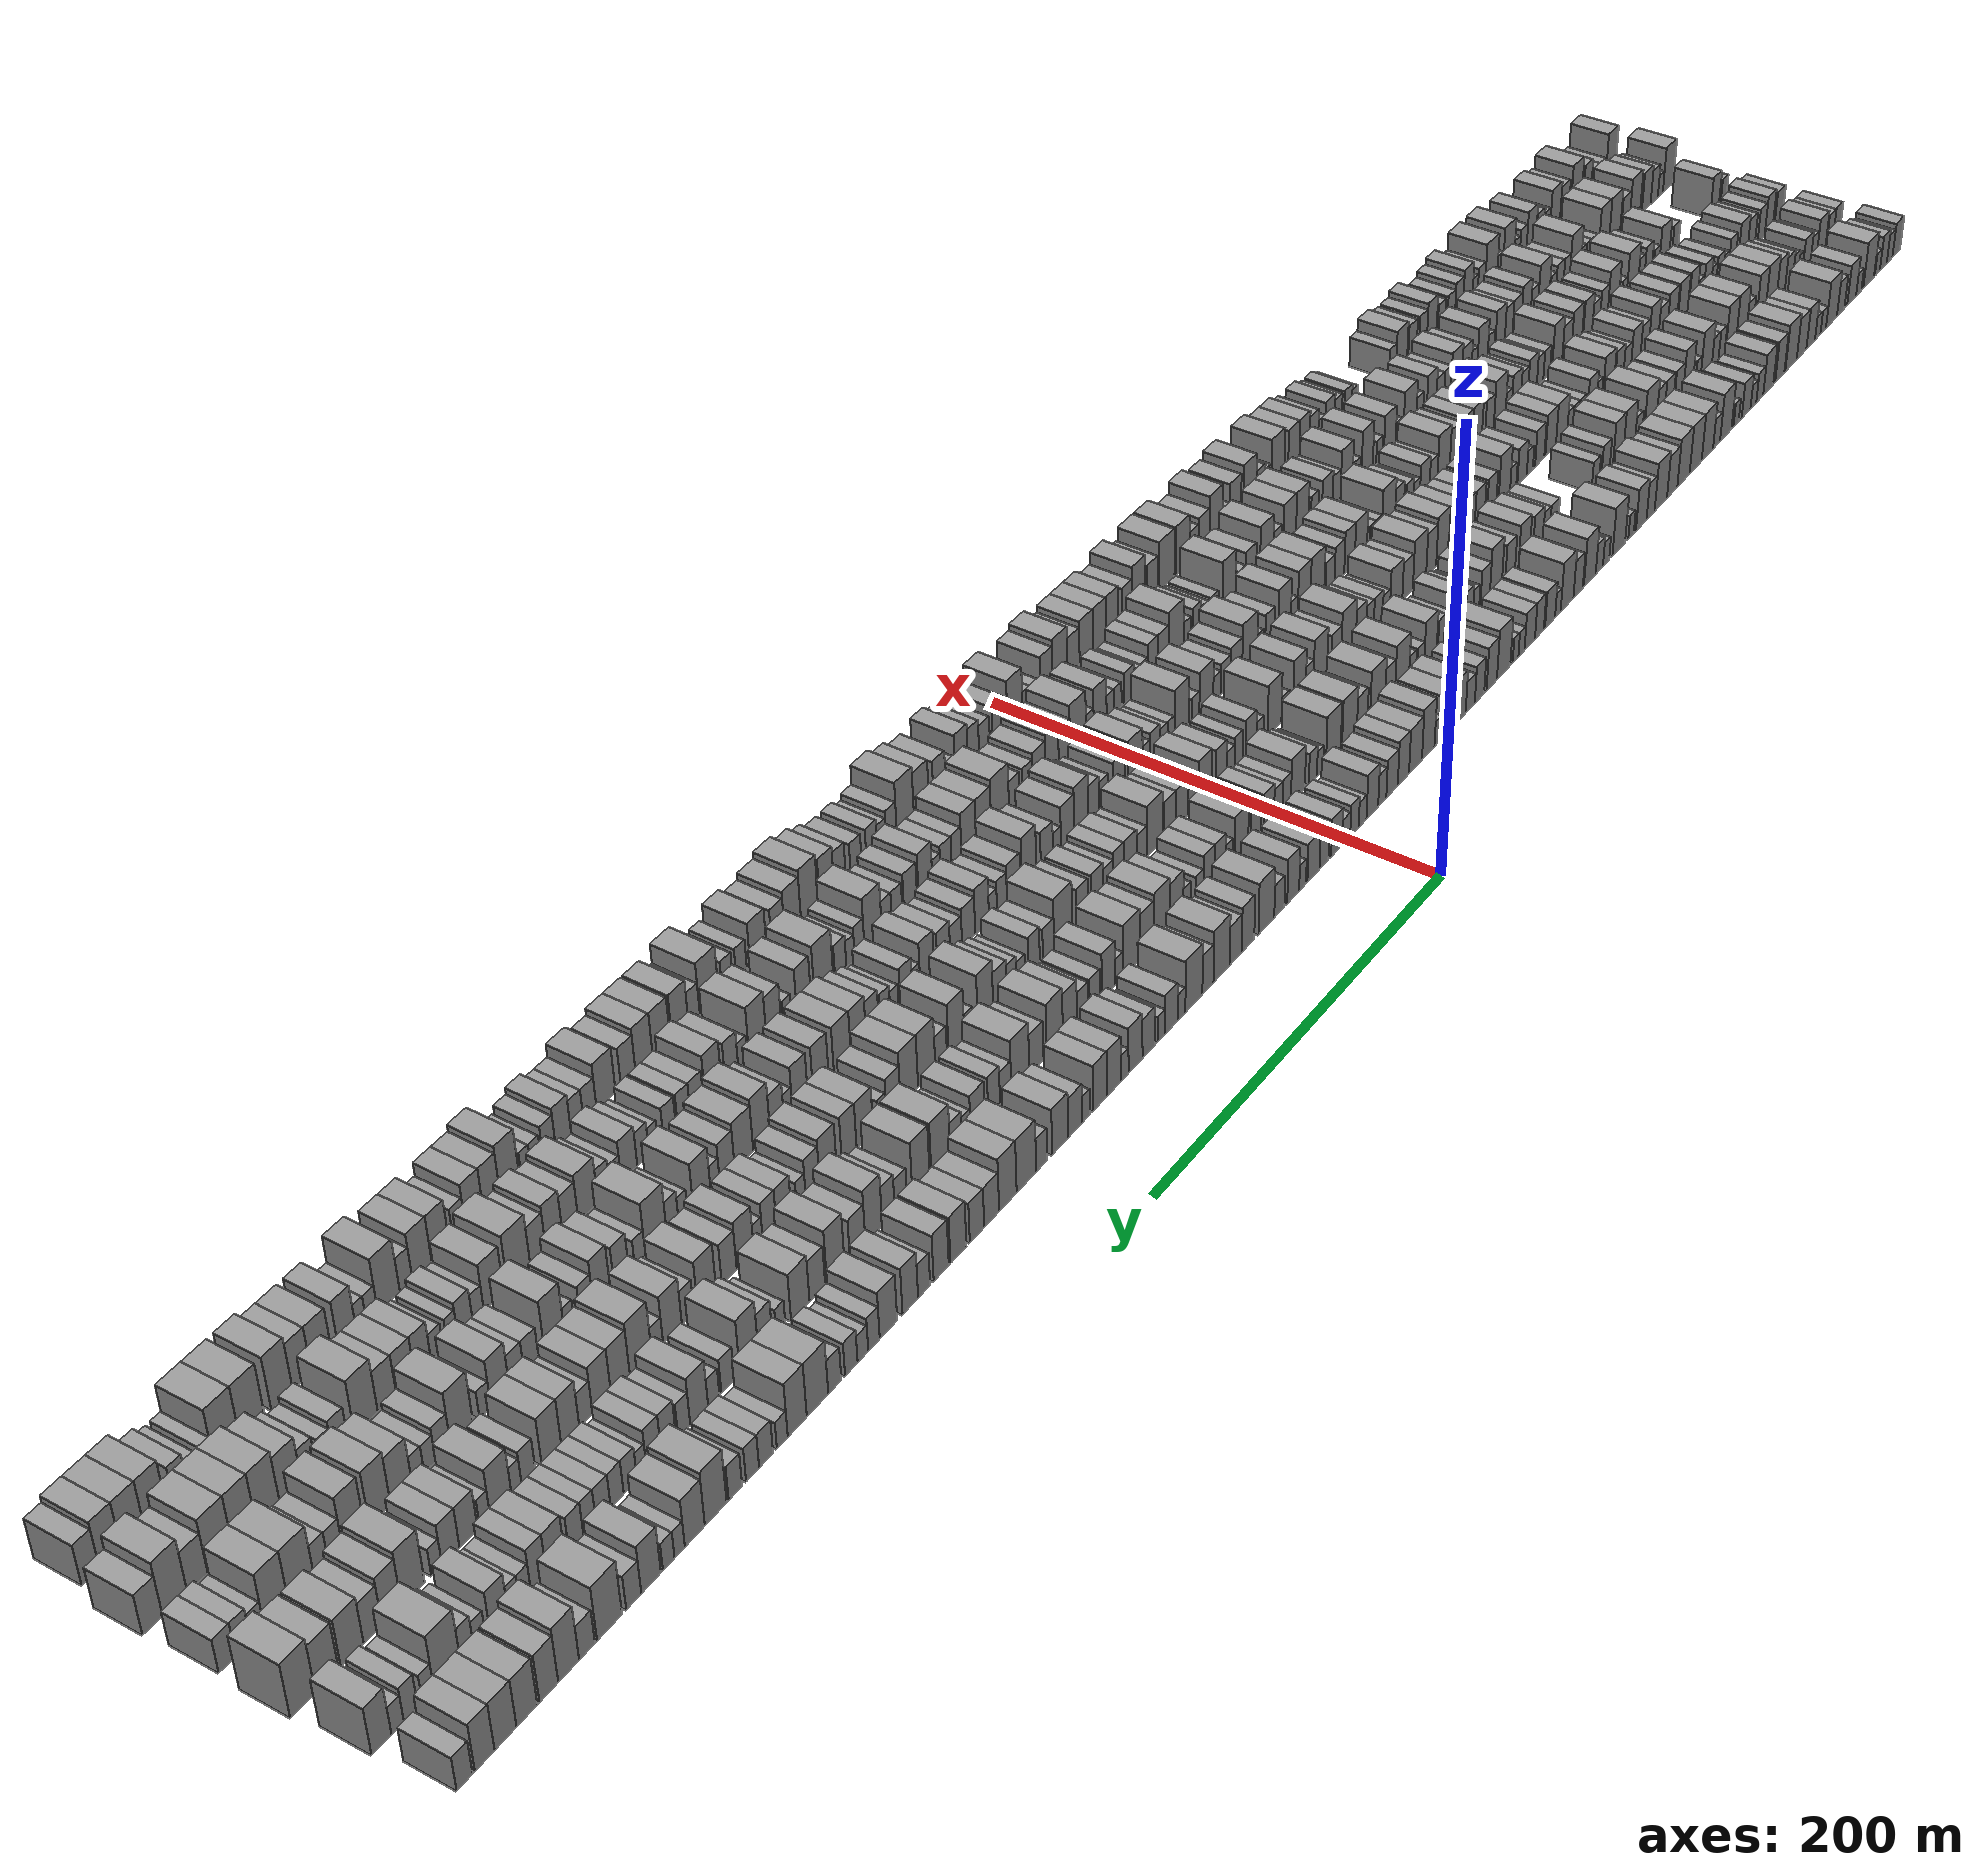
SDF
<sdf version="1.6">
 <world name="default">
  <scene>
   <sky><clouds><speed>12</speed></clouds></sky>
   <ambient>0.4 0.4 0.4 1</ambient>
   <background>0.7 0.7 0.7 1</background>
   <shadows>1</shadows>
  </scene>
  <gravity>0 0 -9.8066</gravity>
  <magnetic_field>6e-06 2.3e-05 -4.2e-05</magnetic_field>
  <physics default="0" name="default_physics" type="ode">
   <ode>
    <solver>
     <type>quick</type>
     <iters>10</iters>
     <sor>1.0</sor>
     <use_dynamic_moi_rescaling>0</use_dynamic_moi_rescaling>
    </solver>
    <constraints>
     <cfm>0</cfm>
     <erp>0.2</erp>
     <contact_max_correcting_vel>100</contact_max_correcting_vel>
     <contact_surface_layer>0.001</contact_surface_layer>
    </constraints>
   </ode>
   <max_step_size>0.004</max_step_size>
   <real_time_factor>1</real_time_factor>
   <real_time_update_rate>250</real_time_update_rate>
  </physics>
  <light name="sun" type="directional">
   <pose>0 0 10 0 0 0</pose>
   <diffuse>0.8 0.8 0.8 1</diffuse>
   <specular>0.2 0.2 0.2 1</specular>
   <attenuation>
    <range>1000</range>
    <constant>0.9</constant>
    <linear>0.01</linear>
    <quadratic>0.001</quadratic>
   </attenuation>
   <direction>-0.5 0.1 -0.9</direction>
  </light>
  <model name="building_1">
   <static>1</static>
   <pose>50.0000 -505.6453 0 0.000000 0.000000 0.000000</pose>
   <link name="link">
    <pose>0 0 9.00 0 0 0</pose>
    <collision name="collision"><geometry><box><size>20.0000 8.7094 18.0000</size></box></geometry></collision>
    <visual name="visual">
     <cast_shadows>0</cast_shadows>
     <geometry><box><size>20.0000 8.7094 18.0000</size></box></geometry>
     <material>
      <script>
       <uri>model://grey_wall/materials/scripts</uri>
       <uri>model://grey_wall/materials/textures</uri>
       <name>vrc/grey_wall</name>
      </script>
     </material>
    </visual>
   </link>
  </model>
  <model name="building_2">
   <static>1</static>
   <pose>50.0000 -498.0498 0 0.000000 0.000000 0.000000</pose>
   <link name="link">
    <pose>0 0 7.50 0 0 0</pose>
    <collision name="collision"><geometry><box><size>20.0000 6.4816 15.0000</size></box></geometry></collision>
    <visual name="visual">
     <cast_shadows>0</cast_shadows>
     <geometry><box><size>20.0000 6.4816 15.0000</size></box></geometry>
     <material>
      <script>
       <uri>model://grey_wall/materials/scripts</uri>
       <uri>model://grey_wall/materials/textures</uri>
       <name>vrc/grey_wall</name>
      </script>
     </material>
    </visual>
   </link>
  </model>
  <model name="building_3">
   <static>1</static>
   <pose>50.0000 -490.9728 0 0.000000 0.000000 0.000000</pose>
   <link name="link">
    <pose>0 0 9.00 0 0 0</pose>
    <collision name="collision"><geometry><box><size>20.0000 7.6724 18.0000</size></box></geometry></collision>
    <visual name="visual">
     <cast_shadows>0</cast_shadows>
     <geometry><box><size>20.0000 7.6724 18.0000</size></box></geometry>
     <material>
      <script>
       <uri>model://grey_wall/materials/scripts</uri>
       <uri>model://grey_wall/materials/textures</uri>
       <name>vrc/grey_wall</name>
      </script>
     </material>
    </visual>
   </link>
  </model>
  <model name="building_4">
   <static>1</static>
   <pose>50.0000 -484.3131 0 0.000000 0.000000 0.000000</pose>
   <link name="link">
    <pose>0 0 6.00 0 0 0</pose>
    <collision name="collision"><geometry><box><size>20.0000 5.6470 12.0000</size></box></geometry></collision>
    <visual name="visual">
     <cast_shadows>0</cast_shadows>
     <geometry><box><size>20.0000 5.6470 12.0000</size></box></geometry>
     <material>
      <script>
       <uri>model://grey_wall/materials/scripts</uri>
       <uri>model://grey_wall/materials/textures</uri>
       <name>vrc/grey_wall</name>
      </script>
     </material>
    </visual>
   </link>
  </model>
  <model name="building_5">
   <static>1</static>
   <pose>50.0000 -474.5490 0 0.000000 0.000000 0.000000</pose>
   <link name="link">
    <pose>0 0 12.00 0 0 0</pose>
    <collision name="collision"><geometry><box><size>20.0000 11.8813 24.0000</size></box></geometry></collision>
    <visual name="visual">
     <cast_shadows>0</cast_shadows>
     <geometry><box><size>20.0000 11.8813 24.0000</size></box></geometry>
     <material>
      <script>
       <uri>model://grey_wall/materials/scripts</uri>
       <uri>model://grey_wall/materials/textures</uri>
       <name>vrc/grey_wall</name>
      </script>
     </material>
    </visual>
   </link>
  </model>
  <model name="building_6">
   <static>1</static>
   <pose>50.0000 -463.6855 0 0.000000 0.000000 0.000000</pose>
   <link name="link">
    <pose>0 0 6.00 0 0 0</pose>
    <collision name="collision"><geometry><box><size>20.0000 5.8457 12.0000</size></box></geometry></collision>
    <visual name="visual">
     <cast_shadows>0</cast_shadows>
     <geometry><box><size>20.0000 5.8457 12.0000</size></box></geometry>
     <material>
      <script>
       <uri>model://grey_wall/materials/scripts</uri>
       <uri>model://grey_wall/materials/textures</uri>
       <name>vrc/grey_wall</name>
      </script>
     </material>
    </visual>
   </link>
  </model>
  <model name="building_7">
   <static>1</static>
   <pose>50.0000 -455.8654 0 0.000000 0.000000 0.000000</pose>
   <link name="link">
    <pose>0 0 10.50 0 0 0</pose>
    <collision name="collision"><geometry><box><size>20.0000 9.7946 21.0000</size></box></geometry></collision>
    <visual name="visual">
     <cast_shadows>0</cast_shadows>
     <geometry><box><size>20.0000 9.7946 21.0000</size></box></geometry>
     <material>
      <script>
       <uri>model://grey_wall/materials/scripts</uri>
       <uri>model://grey_wall/materials/textures</uri>
       <name>vrc/grey_wall</name>
      </script>
     </material>
    </visual>
   </link>
  </model>
  <model name="building_8">
   <static>1</static>
   <pose>50.0000 -443.9238 0 0.000000 0.000000 0.000000</pose>
   <link name="link">
    <pose>0 0 9.00 0 0 0</pose>
    <collision name="collision"><geometry><box><size>20.0000 8.0886 18.0000</size></box></geometry></collision>
    <visual name="visual">
     <cast_shadows>0</cast_shadows>
     <geometry><box><size>20.0000 8.0886 18.0000</size></box></geometry>
     <material>
      <script>
       <uri>model://grey_wall/materials/scripts</uri>
       <uri>model://grey_wall/materials/textures</uri>
       <name>vrc/grey_wall</name>
      </script>
     </material>
    </visual>
   </link>
  </model>
  <model name="building_9">
   <static>1</static>
   <pose>50.0000 -433.9805 0 0.000000 0.000000 0.000000</pose>
   <link name="link">
    <pose>0 0 12.00 0 0 0</pose>
    <collision name="collision"><geometry><box><size>20.0000 11.7979 24.0000</size></box></geometry></collision>
    <visual name="visual">
     <cast_shadows>0</cast_shadows>
     <geometry><box><size>20.0000 11.7979 24.0000</size></box></geometry>
     <material>
      <script>
       <uri>model://grey_wall/materials/scripts</uri>
       <uri>model://grey_wall/materials/textures</uri>
       <name>vrc/grey_wall</name>
      </script>
     </material>
    </visual>
   </link>
  </model>
  <model name="building_10">
   <static>1</static>
   <pose>50.0000 -425.1136 0 0.000000 0.000000 0.000000</pose>
   <link name="link">
    <pose>0 0 6.00 0 0 0</pose>
    <collision name="collision"><geometry><box><size>20.0000 5.9361 12.0000</size></box></geometry></collision>
    <visual name="visual">
     <cast_shadows>0</cast_shadows>
     <geometry><box><size>20.0000 5.9361 12.0000</size></box></geometry>
     <material>
      <script>
       <uri>model://grey_wall/materials/scripts</uri>
       <uri>model://grey_wall/materials/textures</uri>
       <name>vrc/grey_wall</name>
      </script>
     </material>
    </visual>
   </link>
  </model>
  <model name="building_11">
   <static>1</static>
   <pose>50.0000 -419.2511 0 0.000000 0.000000 0.000000</pose>
   <link name="link">
    <pose>0 0 6.00 0 0 0</pose>
    <collision name="collision"><geometry><box><size>20.0000 5.7888 12.0000</size></box></geometry></collision>
    <visual name="visual">
     <cast_shadows>0</cast_shadows>
     <geometry><box><size>20.0000 5.7888 12.0000</size></box></geometry>
     <material>
      <script>
       <uri>model://grey_wall/materials/scripts</uri>
       <uri>model://grey_wall/materials/textures</uri>
       <name>vrc/grey_wall</name>
      </script>
     </material>
    </visual>
   </link>
  </model>
  <model name="building_12">
   <static>1</static>
   <pose>50.0000 -411.7991 0 0.000000 0.000000 0.000000</pose>
   <link name="link">
    <pose>0 0 10.50 0 0 0</pose>
    <collision name="collision"><geometry><box><size>20.0000 9.1152 21.0000</size></box></geometry></collision>
    <visual name="visual">
     <cast_shadows>0</cast_shadows>
     <geometry><box><size>20.0000 9.1152 21.0000</size></box></geometry>
     <material>
      <script>
       <uri>model://grey_wall/materials/scripts</uri>
       <uri>model://grey_wall/materials/textures</uri>
       <name>vrc/grey_wall</name>
      </script>
     </material>
    </visual>
   </link>
  </model>
  <model name="building_13">
   <static>1</static>
   <pose>50.0000 -402.1448 0 0.000000 0.000000 0.000000</pose>
   <link name="link">
    <pose>0 0 10.50 0 0 0</pose>
    <collision name="collision"><geometry><box><size>20.0000 10.1934 21.0000</size></box></geometry></collision>
    <visual name="visual">
     <cast_shadows>0</cast_shadows>
     <geometry><box><size>20.0000 10.1934 21.0000</size></box></geometry>
     <material>
      <script>
       <uri>model://grey_wall/materials/scripts</uri>
       <uri>model://grey_wall/materials/textures</uri>
       <name>vrc/grey_wall</name>
      </script>
     </material>
    </visual>
   </link>
  </model>
  <model name="building_14">
   <static>1</static>
   <pose>50.0000 -391.1169 0 0.000000 0.000000 0.000000</pose>
   <link name="link">
    <pose>0 0 12.00 0 0 0</pose>
    <collision name="collision"><geometry><box><size>20.0000 11.8624 24.0000</size></box></geometry></collision>
    <visual name="visual">
     <cast_shadows>0</cast_shadows>
     <geometry><box><size>20.0000 11.8624 24.0000</size></box></geometry>
     <material>
      <script>
       <uri>model://grey_wall/materials/scripts</uri>
       <uri>model://grey_wall/materials/textures</uri>
       <name>vrc/grey_wall</name>
      </script>
     </material>
    </visual>
   </link>
  </model>
  <model name="building_15">
   <static>1</static>
   <pose>50.0000 -379.4605 0 0.000000 0.000000 0.000000</pose>
   <link name="link">
    <pose>0 0 10.50 0 0 0</pose>
    <collision name="collision"><geometry><box><size>20.0000 9.4505 21.0000</size></box></geometry></collision>
    <visual name="visual">
     <cast_shadows>0</cast_shadows>
     <geometry><box><size>20.0000 9.4505 21.0000</size></box></geometry>
     <material>
      <script>
       <uri>model://grey_wall/materials/scripts</uri>
       <uri>model://grey_wall/materials/textures</uri>
       <name>vrc/grey_wall</name>
      </script>
     </material>
    </visual>
   </link>
  </model>
  <model name="building_16">
   <static>1</static>
   <pose>50.0000 -367.6167 0 0.000000 0.000000 0.000000</pose>
   <link name="link">
    <pose>0 0 10.50 0 0 0</pose>
    <collision name="collision"><geometry><box><size>20.0000 10.2370 21.0000</size></box></geometry></collision>
    <visual name="visual">
     <cast_shadows>0</cast_shadows>
     <geometry><box><size>20.0000 10.2370 21.0000</size></box></geometry>
     <material>
      <script>
       <uri>model://grey_wall/materials/scripts</uri>
       <uri>model://grey_wall/materials/textures</uri>
       <name>vrc/grey_wall</name>
      </script>
     </material>
    </visual>
   </link>
  </model>
  <model name="building_17">
   <static>1</static>
   <pose>50.0000 -358.9702 0 0.000000 0.000000 0.000000</pose>
   <link name="link">
    <pose>0 0 7.50 0 0 0</pose>
    <collision name="collision"><geometry><box><size>20.0000 7.0561 15.0000</size></box></geometry></collision>
    <visual name="visual">
     <cast_shadows>0</cast_shadows>
     <geometry><box><size>20.0000 7.0561 15.0000</size></box></geometry>
     <material>
      <script>
       <uri>model://grey_wall/materials/scripts</uri>
       <uri>model://grey_wall/materials/textures</uri>
       <name>vrc/grey_wall</name>
      </script>
     </material>
    </visual>
   </link>
  </model>
  <model name="building_18">
   <static>1</static>
   <pose>50.0000 -352.5513 0 0.000000 0.000000 0.000000</pose>
   <link name="link">
    <pose>0 0 6.00 0 0 0</pose>
    <collision name="collision"><geometry><box><size>20.0000 5.7816 12.0000</size></box></geometry></collision>
    <visual name="visual">
     <cast_shadows>0</cast_shadows>
     <geometry><box><size>20.0000 5.7816 12.0000</size></box></geometry>
     <material>
      <script>
       <uri>model://grey_wall/materials/scripts</uri>
       <uri>model://grey_wall/materials/textures</uri>
       <name>vrc/grey_wall</name>
      </script>
     </material>
    </visual>
   </link>
  </model>
  <model name="building_19">
   <static>1</static>
   <pose>50.0000 -345.2167 0 0.000000 0.000000 0.000000</pose>
   <link name="link">
    <pose>0 0 9.00 0 0 0</pose>
    <collision name="collision"><geometry><box><size>20.0000 8.8877 18.0000</size></box></geometry></collision>
    <visual name="visual">
     <cast_shadows>0</cast_shadows>
     <geometry><box><size>20.0000 8.8877 18.0000</size></box></geometry>
     <material>
      <script>
       <uri>model://grey_wall/materials/scripts</uri>
       <uri>model://grey_wall/materials/textures</uri>
       <name>vrc/grey_wall</name>
      </script>
     </material>
    </visual>
   </link>
  </model>
  <model name="building_20">
   <static>1</static>
   <pose>50.0000 -335.1742 0 0.000000 0.000000 0.000000</pose>
   <link name="link">
    <pose>0 0 6.00 0 0 0</pose>
    <collision name="collision"><geometry><box><size>20.0000 5.1972 12.0000</size></box></geometry></collision>
    <visual name="visual">
     <cast_shadows>0</cast_shadows>
     <geometry><box><size>20.0000 5.1972 12.0000</size></box></geometry>
     <material>
      <script>
       <uri>model://grey_wall/materials/scripts</uri>
       <uri>model://grey_wall/materials/textures</uri>
       <name>vrc/grey_wall</name>
      </script>
     </material>
    </visual>
   </link>
  </model>
  <model name="building_21">
   <static>1</static>
   <pose>50.0000 -324.9259 0 0.000000 0.000000 0.000000</pose>
   <link name="link">
    <pose>0 0 12.00 0 0 0</pose>
    <collision name="collision"><geometry><box><size>20.0000 11.2994 24.0000</size></box></geometry></collision>
    <visual name="visual">
     <cast_shadows>0</cast_shadows>
     <geometry><box><size>20.0000 11.2994 24.0000</size></box></geometry>
     <material>
      <script>
       <uri>model://grey_wall/materials/scripts</uri>
       <uri>model://grey_wall/materials/textures</uri>
       <name>vrc/grey_wall</name>
      </script>
     </material>
    </visual>
   </link>
  </model>
  <model name="building_22">
   <static>1</static>
   <pose>50.0000 -315.8454 0 0.000000 0.000000 0.000000</pose>
   <link name="link">
    <pose>0 0 7.50 0 0 0</pose>
    <collision name="collision"><geometry><box><size>20.0000 6.8616 15.0000</size></box></geometry></collision>
    <visual name="visual">
     <cast_shadows>0</cast_shadows>
     <geometry><box><size>20.0000 6.8616 15.0000</size></box></geometry>
     <material>
      <script>
       <uri>model://grey_wall/materials/scripts</uri>
       <uri>model://grey_wall/materials/textures</uri>
       <name>vrc/grey_wall</name>
      </script>
     </material>
    </visual>
   </link>
  </model>
  <model name="building_23">
   <static>1</static>
   <pose>50.0000 -306.8492 0 0.000000 0.000000 0.000000</pose>
   <link name="link">
    <pose>0 0 12.00 0 0 0</pose>
    <collision name="collision"><geometry><box><size>20.0000 11.1307 24.0000</size></box></geometry></collision>
    <visual name="visual">
     <cast_shadows>0</cast_shadows>
     <geometry><box><size>20.0000 11.1307 24.0000</size></box></geometry>
     <material>
      <script>
       <uri>model://grey_wall/materials/scripts</uri>
       <uri>model://grey_wall/materials/textures</uri>
       <name>vrc/grey_wall</name>
      </script>
     </material>
    </visual>
   </link>
  </model>
  <model name="building_24">
   <static>1</static>
   <pose>50.0000 -295.4927 0 0.000000 0.000000 0.000000</pose>
   <link name="link">
    <pose>0 0 12.00 0 0 0</pose>
    <collision name="collision"><geometry><box><size>20.0000 11.5824 24.0000</size></box></geometry></collision>
    <visual name="visual">
     <cast_shadows>0</cast_shadows>
     <geometry><box><size>20.0000 11.5824 24.0000</size></box></geometry>
     <material>
      <script>
       <uri>model://grey_wall/materials/scripts</uri>
       <uri>model://grey_wall/materials/textures</uri>
       <name>vrc/grey_wall</name>
      </script>
     </material>
    </visual>
   </link>
  </model>
  <model name="building_25">
   <static>1</static>
   <pose>50.0000 -283.8319 0 0.000000 0.000000 0.000000</pose>
   <link name="link">
    <pose>0 0 12.00 0 0 0</pose>
    <collision name="collision"><geometry><box><size>20.0000 11.7392 24.0000</size></box></geometry></collision>
    <visual name="visual">
     <cast_shadows>0</cast_shadows>
     <geometry><box><size>20.0000 11.7392 24.0000</size></box></geometry>
     <material>
      <script>
       <uri>model://grey_wall/materials/scripts</uri>
       <uri>model://grey_wall/materials/textures</uri>
       <name>vrc/grey_wall</name>
      </script>
     </material>
    </visual>
   </link>
  </model>
  <model name="building_26">
   <static>1</static>
   <pose>50.0000 -273.0505 0 0.000000 0.000000 0.000000</pose>
   <link name="link">
    <pose>0 0 10.50 0 0 0</pose>
    <collision name="collision"><geometry><box><size>20.0000 9.8234 21.0000</size></box></geometry></collision>
    <visual name="visual">
     <cast_shadows>0</cast_shadows>
     <geometry><box><size>20.0000 9.8234 21.0000</size></box></geometry>
     <material>
      <script>
       <uri>model://grey_wall/materials/scripts</uri>
       <uri>model://grey_wall/materials/textures</uri>
       <name>vrc/grey_wall</name>
      </script>
     </material>
    </visual>
   </link>
  </model>
  <model name="building_27">
   <static>1</static>
   <pose>50.0000 -262.3443 0 0.000000 0.000000 0.000000</pose>
   <link name="link">
    <pose>0 0 12.00 0 0 0</pose>
    <collision name="collision"><geometry><box><size>20.0000 11.5891 24.0000</size></box></geometry></collision>
    <visual name="visual">
     <cast_shadows>0</cast_shadows>
     <geometry><box><size>20.0000 11.5891 24.0000</size></box></geometry>
     <material>
      <script>
       <uri>model://grey_wall/materials/scripts</uri>
       <uri>model://grey_wall/materials/textures</uri>
       <name>vrc/grey_wall</name>
      </script>
     </material>
    </visual>
   </link>
  </model>
  <model name="building_28">
   <static>1</static>
   <pose>50.0000 -252.7994 0 0.000000 0.000000 0.000000</pose>
   <link name="link">
    <pose>0 0 9.00 0 0 0</pose>
    <collision name="collision"><geometry><box><size>20.0000 7.5006 18.0000</size></box></geometry></collision>
    <visual name="visual">
     <cast_shadows>0</cast_shadows>
     <geometry><box><size>20.0000 7.5006 18.0000</size></box></geometry>
     <material>
      <script>
       <uri>model://grey_wall/materials/scripts</uri>
       <uri>model://grey_wall/materials/textures</uri>
       <name>vrc/grey_wall</name>
      </script>
     </material>
    </visual>
   </link>
  </model>
  <model name="building_29">
   <static>1</static>
   <pose>50.0000 -244.1160 0 0.000000 0.000000 0.000000</pose>
   <link name="link">
    <pose>0 0 10.50 0 0 0</pose>
    <collision name="collision"><geometry><box><size>20.0000 9.8663 21.0000</size></box></geometry></collision>
    <visual name="visual">
     <cast_shadows>0</cast_shadows>
     <geometry><box><size>20.0000 9.8663 21.0000</size></box></geometry>
     <material>
      <script>
       <uri>model://grey_wall/materials/scripts</uri>
       <uri>model://grey_wall/materials/textures</uri>
       <name>vrc/grey_wall</name>
      </script>
     </material>
    </visual>
   </link>
  </model>
  <model name="building_30">
   <static>1</static>
   <pose>50.0000 -234.6776 0 0.000000 0.000000 0.000000</pose>
   <link name="link">
    <pose>0 0 6.00 0 0 0</pose>
    <collision name="collision"><geometry><box><size>20.0000 5.0105 12.0000</size></box></geometry></collision>
    <visual name="visual">
     <cast_shadows>0</cast_shadows>
     <geometry><box><size>20.0000 5.0105 12.0000</size></box></geometry>
     <material>
      <script>
       <uri>model://grey_wall/materials/scripts</uri>
       <uri>model://grey_wall/materials/textures</uri>
       <name>vrc/grey_wall</name>
      </script>
     </material>
    </visual>
   </link>
  </model>
  <model name="building_31">
   <static>1</static>
   <pose>50.0000 -223.4328 0 0.000000 0.000000 0.000000</pose>
   <link name="link">
    <pose>0 0 12.00 0 0 0</pose>
    <collision name="collision"><geometry><box><size>20.0000 11.4790 24.0000</size></box></geometry></collision>
    <visual name="visual">
     <cast_shadows>0</cast_shadows>
     <geometry><box><size>20.0000 11.4790 24.0000</size></box></geometry>
     <material>
      <script>
       <uri>model://grey_wall/materials/scripts</uri>
       <uri>model://grey_wall/materials/textures</uri>
       <name>vrc/grey_wall</name>
      </script>
     </material>
    </visual>
   </link>
  </model>
  <model name="building_32">
   <static>1</static>
   <pose>50.0000 -211.8994 0 0.000000 0.000000 0.000000</pose>
   <link name="link">
    <pose>0 0 6.00 0 0 0</pose>
    <collision name="collision"><geometry><box><size>20.0000 5.5879 12.0000</size></box></geometry></collision>
    <visual name="visual">
     <cast_shadows>0</cast_shadows>
     <geometry><box><size>20.0000 5.5879 12.0000</size></box></geometry>
     <material>
      <script>
       <uri>model://grey_wall/materials/scripts</uri>
       <uri>model://grey_wall/materials/textures</uri>
       <name>vrc/grey_wall</name>
      </script>
     </material>
    </visual>
   </link>
  </model>
  <model name="building_33">
   <static>1</static>
   <pose>50.0000 -205.8719 0 0.000000 0.000000 0.000000</pose>
   <link name="link">
    <pose>0 0 7.50 0 0 0</pose>
    <collision name="collision"><geometry><box><size>20.0000 6.4670 15.0000</size></box></geometry></collision>
    <visual name="visual">
     <cast_shadows>0</cast_shadows>
     <geometry><box><size>20.0000 6.4670 15.0000</size></box></geometry>
     <material>
      <script>
       <uri>model://grey_wall/materials/scripts</uri>
       <uri>model://grey_wall/materials/textures</uri>
       <name>vrc/grey_wall</name>
      </script>
     </material>
    </visual>
   </link>
  </model>
  <model name="building_34">
   <static>1</static>
   <pose>50.0000 -197.3775 0 0.000000 0.000000 0.000000</pose>
   <link name="link">
    <pose>0 0 12.00 0 0 0</pose>
    <collision name="collision"><geometry><box><size>20.0000 10.5219 24.0000</size></box></geometry></collision>
    <visual name="visual">
     <cast_shadows>0</cast_shadows>
     <geometry><box><size>20.0000 10.5219 24.0000</size></box></geometry>
     <material>
      <script>
       <uri>model://grey_wall/materials/scripts</uri>
       <uri>model://grey_wall/materials/textures</uri>
       <name>vrc/grey_wall</name>
      </script>
     </material>
    </visual>
   </link>
  </model>
  <model name="building_35">
   <static>1</static>
   <pose>50.0000 -187.0116 0 0.000000 0.000000 0.000000</pose>
   <link name="link">
    <pose>0 0 9.00 0 0 0</pose>
    <collision name="collision"><geometry><box><size>20.0000 8.2099 18.0000</size></box></geometry></collision>
    <visual name="visual">
     <cast_shadows>0</cast_shadows>
     <geometry><box><size>20.0000 8.2099 18.0000</size></box></geometry>
     <material>
      <script>
       <uri>model://grey_wall/materials/scripts</uri>
       <uri>model://grey_wall/materials/textures</uri>
       <name>vrc/grey_wall</name>
      </script>
     </material>
    </visual>
   </link>
  </model>
  <model name="building_36">
   <static>1</static>
   <pose>50.0000 -177.3087 0 0.000000 0.000000 0.000000</pose>
   <link name="link">
    <pose>0 0 12.00 0 0 0</pose>
    <collision name="collision"><geometry><box><size>20.0000 11.1958 24.0000</size></box></geometry></collision>
    <visual name="visual">
     <cast_shadows>0</cast_shadows>
     <geometry><box><size>20.0000 11.1958 24.0000</size></box></geometry>
     <material>
      <script>
       <uri>model://grey_wall/materials/scripts</uri>
       <uri>model://grey_wall/materials/textures</uri>
       <name>vrc/grey_wall</name>
      </script>
     </material>
    </visual>
   </link>
  </model>
  <model name="building_37">
   <static>1</static>
   <pose>50.0000 -169.2720 0 0.000000 0.000000 0.000000</pose>
   <link name="link">
    <pose>0 0 6.00 0 0 0</pose>
    <collision name="collision"><geometry><box><size>20.0000 4.8776 12.0000</size></box></geometry></collision>
    <visual name="visual">
     <cast_shadows>0</cast_shadows>
     <geometry><box><size>20.0000 4.8776 12.0000</size></box></geometry>
     <material>
      <script>
       <uri>model://grey_wall/materials/scripts</uri>
       <uri>model://grey_wall/materials/textures</uri>
       <name>vrc/grey_wall</name>
      </script>
     </material>
    </visual>
   </link>
  </model>
  <model name="building_38">
   <static>1</static>
   <pose>50.0000 -162.4852 0 0.000000 0.000000 0.000000</pose>
   <link name="link">
    <pose>0 0 9.00 0 0 0</pose>
    <collision name="collision"><geometry><box><size>20.0000 8.6959 18.0000</size></box></geometry></collision>
    <visual name="visual">
     <cast_shadows>0</cast_shadows>
     <geometry><box><size>20.0000 8.6959 18.0000</size></box></geometry>
     <material>
      <script>
       <uri>model://grey_wall/materials/scripts</uri>
       <uri>model://grey_wall/materials/textures</uri>
       <name>vrc/grey_wall</name>
      </script>
     </material>
    </visual>
   </link>
  </model>
  <model name="building_39">
   <static>1</static>
   <pose>50.0000 -153.3412 0 0.000000 0.000000 0.000000</pose>
   <link name="link">
    <pose>0 0 9.00 0 0 0</pose>
    <collision name="collision"><geometry><box><size>20.0000 7.5921 18.0000</size></box></geometry></collision>
    <visual name="visual">
     <cast_shadows>0</cast_shadows>
     <geometry><box><size>20.0000 7.5921 18.0000</size></box></geometry>
     <material>
      <script>
       <uri>model://grey_wall/materials/scripts</uri>
       <uri>model://grey_wall/materials/textures</uri>
       <name>vrc/grey_wall</name>
      </script>
     </material>
    </visual>
   </link>
  </model>
  <model name="building_40">
   <static>1</static>
   <pose>50.0000 -145.0955 0 0.000000 0.000000 0.000000</pose>
   <link name="link">
    <pose>0 0 9.00 0 0 0</pose>
    <collision name="collision"><geometry><box><size>20.0000 8.8993 18.0000</size></box></geometry></collision>
    <visual name="visual">
     <cast_shadows>0</cast_shadows>
     <geometry><box><size>20.0000 8.8993 18.0000</size></box></geometry>
     <material>
      <script>
       <uri>model://grey_wall/materials/scripts</uri>
       <uri>model://grey_wall/materials/textures</uri>
       <name>vrc/grey_wall</name>
      </script>
     </material>
    </visual>
   </link>
  </model>
  <model name="building_41">
   <static>1</static>
   <pose>50.0000 -138.0604 0 0.000000 0.000000 0.000000</pose>
   <link name="link">
    <pose>0 0 6.00 0 0 0</pose>
    <collision name="collision"><geometry><box><size>20.0000 5.1710 12.0000</size></box></geometry></collision>
    <visual name="visual">
     <cast_shadows>0</cast_shadows>
     <geometry><box><size>20.0000 5.1710 12.0000</size></box></geometry>
     <material>
      <script>
       <uri>model://grey_wall/materials/scripts</uri>
       <uri>model://grey_wall/materials/textures</uri>
       <name>vrc/grey_wall</name>
      </script>
     </material>
    </visual>
   </link>
  </model>
  <model name="building_42">
   <static>1</static>
   <pose>50.0000 -133.0396 0 0.000000 0.000000 0.000000</pose>
   <link name="link">
    <pose>0 0 6.00 0 0 0</pose>
    <collision name="collision"><geometry><box><size>20.0000 4.8706 12.0000</size></box></geometry></collision>
    <visual name="visual">
     <cast_shadows>0</cast_shadows>
     <geometry><box><size>20.0000 4.8706 12.0000</size></box></geometry>
     <material>
      <script>
       <uri>model://grey_wall/materials/scripts</uri>
       <uri>model://grey_wall/materials/textures</uri>
       <name>vrc/grey_wall</name>
      </script>
     </material>
    </visual>
   </link>
  </model>
  <model name="building_43">
   <static>1</static>
   <pose>50.0000 -123.0273 0 0.000000 0.000000 0.000000</pose>
   <link name="link">
    <pose>0 0 12.00 0 0 0</pose>
    <collision name="collision"><geometry><box><size>20.0000 11.1539 24.0000</size></box></geometry></collision>
    <visual name="visual">
     <cast_shadows>0</cast_shadows>
     <geometry><box><size>20.0000 11.1539 24.0000</size></box></geometry>
     <material>
      <script>
       <uri>model://grey_wall/materials/scripts</uri>
       <uri>model://grey_wall/materials/textures</uri>
       <name>vrc/grey_wall</name>
      </script>
     </material>
    </visual>
   </link>
  </model>
  <model name="building_44">
   <static>1</static>
   <pose>50.0000 -113.1561 0 0.000000 0.000000 0.000000</pose>
   <link name="link">
    <pose>0 0 10.50 0 0 0</pose>
    <collision name="collision"><geometry><box><size>20.0000 8.5886 21.0000</size></box></geometry></collision>
    <visual name="visual">
     <cast_shadows>0</cast_shadows>
     <geometry><box><size>20.0000 8.5886 21.0000</size></box></geometry>
     <material>
      <script>
       <uri>model://grey_wall/materials/scripts</uri>
       <uri>model://grey_wall/materials/textures</uri>
       <name>vrc/grey_wall</name>
      </script>
     </material>
    </visual>
   </link>
  </model>
  <model name="building_45">
   <static>1</static>
   <pose>50.0000 -103.0229 0 0.000000 0.000000 0.000000</pose>
   <link name="link">
    <pose>0 0 9.00 0 0 0</pose>
    <collision name="collision"><geometry><box><size>20.0000 7.6777 18.0000</size></box></geometry></collision>
    <visual name="visual">
     <cast_shadows>0</cast_shadows>
     <geometry><box><size>20.0000 7.6777 18.0000</size></box></geometry>
     <material>
      <script>
       <uri>model://grey_wall/materials/scripts</uri>
       <uri>model://grey_wall/materials/textures</uri>
       <name>vrc/grey_wall</name>
      </script>
     </material>
    </visual>
   </link>
  </model>
  <model name="building_46">
   <static>1</static>
   <pose>50.0000 -95.4468 0 0.000000 0.000000 0.000000</pose>
   <link name="link">
    <pose>0 0 7.50 0 0 0</pose>
    <collision name="collision"><geometry><box><size>20.0000 7.4744 15.0000</size></box></geometry></collision>
    <visual name="visual">
     <cast_shadows>0</cast_shadows>
     <geometry><box><size>20.0000 7.4744 15.0000</size></box></geometry>
     <material>
      <script>
       <uri>model://grey_wall/materials/scripts</uri>
       <uri>model://grey_wall/materials/textures</uri>
       <name>vrc/grey_wall</name>
      </script>
     </material>
    </visual>
   </link>
  </model>
  <model name="building_47">
   <static>1</static>
   <pose>50.0000 -86.9775 0 0.000000 0.000000 0.000000</pose>
   <link name="link">
    <pose>0 0 10.50 0 0 0</pose>
    <collision name="collision"><geometry><box><size>20.0000 9.4643 21.0000</size></box></geometry></collision>
    <visual name="visual">
     <cast_shadows>0</cast_shadows>
     <geometry><box><size>20.0000 9.4643 21.0000</size></box></geometry>
     <material>
      <script>
       <uri>model://grey_wall/materials/scripts</uri>
       <uri>model://grey_wall/materials/textures</uri>
       <name>vrc/grey_wall</name>
      </script>
     </material>
    </visual>
   </link>
  </model>
  <model name="building_48">
   <static>1</static>
   <pose>50.0000 -77.1496 0 0.000000 0.000000 0.000000</pose>
   <link name="link">
    <pose>0 0 10.50 0 0 0</pose>
    <collision name="collision"><geometry><box><size>20.0000 10.1915 21.0000</size></box></geometry></collision>
    <visual name="visual">
     <cast_shadows>0</cast_shadows>
     <geometry><box><size>20.0000 10.1915 21.0000</size></box></geometry>
     <material>
      <script>
       <uri>model://grey_wall/materials/scripts</uri>
       <uri>model://grey_wall/materials/textures</uri>
       <name>vrc/grey_wall</name>
      </script>
     </material>
    </visual>
   </link>
  </model>
  <model name="building_49">
   <static>1</static>
   <pose>50.0000 -69.3749 0 0.000000 0.000000 0.000000</pose>
   <link name="link">
    <pose>0 0 6.00 0 0 0</pose>
    <collision name="collision"><geometry><box><size>20.0000 5.3580 12.0000</size></box></geometry></collision>
    <visual name="visual">
     <cast_shadows>0</cast_shadows>
     <geometry><box><size>20.0000 5.3580 12.0000</size></box></geometry>
     <material>
      <script>
       <uri>model://grey_wall/materials/scripts</uri>
       <uri>model://grey_wall/materials/textures</uri>
       <name>vrc/grey_wall</name>
      </script>
     </material>
    </visual>
   </link>
  </model>
  <model name="building_50">
   <static>1</static>
   <pose>50.0000 -61.7293 0 0.000000 0.000000 0.000000</pose>
   <link name="link">
    <pose>0 0 12.00 0 0 0</pose>
    <collision name="collision"><geometry><box><size>20.0000 9.9330 24.0000</size></box></geometry></collision>
    <visual name="visual">
     <cast_shadows>0</cast_shadows>
     <geometry><box><size>20.0000 9.9330 24.0000</size></box></geometry>
     <material>
      <script>
       <uri>model://grey_wall/materials/scripts</uri>
       <uri>model://grey_wall/materials/textures</uri>
       <name>vrc/grey_wall</name>
      </script>
     </material>
    </visual>
   </link>
  </model>
  <model name="building_51">
   <static>1</static>
   <pose>50.0000 -51.6775 0 0.000000 0.000000 0.000000</pose>
   <link name="link">
    <pose>0 0 10.50 0 0 0</pose>
    <collision name="collision"><geometry><box><size>20.0000 10.1707 21.0000</size></box></geometry></collision>
    <visual name="visual">
     <cast_shadows>0</cast_shadows>
     <geometry><box><size>20.0000 10.1707 21.0000</size></box></geometry>
     <material>
      <script>
       <uri>model://grey_wall/materials/scripts</uri>
       <uri>model://grey_wall/materials/textures</uri>
       <name>vrc/grey_wall</name>
      </script>
     </material>
    </visual>
   </link>
  </model>
  <model name="building_52">
   <static>1</static>
   <pose>50.0000 -42.2199 0 0.000000 0.000000 0.000000</pose>
   <link name="link">
    <pose>0 0 10.50 0 0 0</pose>
    <collision name="collision"><geometry><box><size>20.0000 8.7445 21.0000</size></box></geometry></collision>
    <visual name="visual">
     <cast_shadows>0</cast_shadows>
     <geometry><box><size>20.0000 8.7445 21.0000</size></box></geometry>
     <material>
      <script>
       <uri>model://grey_wall/materials/scripts</uri>
       <uri>model://grey_wall/materials/textures</uri>
       <name>vrc/grey_wall</name>
      </script>
     </material>
    </visual>
   </link>
  </model>
  <model name="building_53">
   <static>1</static>
   <pose>50.0000 -33.4236 0 0.000000 0.000000 0.000000</pose>
   <link name="link">
    <pose>0 0 9.00 0 0 0</pose>
    <collision name="collision"><geometry><box><size>20.0000 8.8480 18.0000</size></box></geometry></collision>
    <visual name="visual">
     <cast_shadows>0</cast_shadows>
     <geometry><box><size>20.0000 8.8480 18.0000</size></box></geometry>
     <material>
      <script>
       <uri>model://grey_wall/materials/scripts</uri>
       <uri>model://grey_wall/materials/textures</uri>
       <name>vrc/grey_wall</name>
      </script>
     </material>
    </visual>
   </link>
  </model>
  <model name="building_54">
   <static>1</static>
   <pose>50.0000 -25.8845 0 0.000000 0.000000 0.000000</pose>
   <link name="link">
    <pose>0 0 7.50 0 0 0</pose>
    <collision name="collision"><geometry><box><size>20.0000 6.2303 15.0000</size></box></geometry></collision>
    <visual name="visual">
     <cast_shadows>0</cast_shadows>
     <geometry><box><size>20.0000 6.2303 15.0000</size></box></geometry>
     <material>
      <script>
       <uri>model://grey_wall/materials/scripts</uri>
       <uri>model://grey_wall/materials/textures</uri>
       <name>vrc/grey_wall</name>
      </script>
     </material>
    </visual>
   </link>
  </model>
  <model name="building_55">
   <static>1</static>
   <pose>50.0000 -18.3283 0 0.000000 0.000000 0.000000</pose>
   <link name="link">
    <pose>0 0 10.50 0 0 0</pose>
    <collision name="collision"><geometry><box><size>20.0000 8.8821 21.0000</size></box></geometry></collision>
    <visual name="visual">
     <cast_shadows>0</cast_shadows>
     <geometry><box><size>20.0000 8.8821 21.0000</size></box></geometry>
     <material>
      <script>
       <uri>model://grey_wall/materials/scripts</uri>
       <uri>model://grey_wall/materials/textures</uri>
       <name>vrc/grey_wall</name>
      </script>
     </material>
    </visual>
   </link>
  </model>
  <model name="building_56">
   <static>1</static>
   <pose>50.0000 -10.9449 0 0.000000 0.000000 0.000000</pose>
   <link name="link">
    <pose>0 0 6.00 0 0 0</pose>
    <collision name="collision"><geometry><box><size>20.0000 5.8846 12.0000</size></box></geometry></collision>
    <visual name="visual">
     <cast_shadows>0</cast_shadows>
     <geometry><box><size>20.0000 5.8846 12.0000</size></box></geometry>
     <material>
      <script>
       <uri>model://grey_wall/materials/scripts</uri>
       <uri>model://grey_wall/materials/textures</uri>
       <name>vrc/grey_wall</name>
      </script>
     </material>
    </visual>
   </link>
  </model>
  <model name="building_57">
   <static>1</static>
   <pose>50.0000 -4.8059 0 0.000000 0.000000 0.000000</pose>
   <link name="link">
    <pose>0 0 7.50 0 0 0</pose>
    <collision name="collision"><geometry><box><size>20.0000 6.3935 15.0000</size></box></geometry></collision>
    <visual name="visual">
     <cast_shadows>0</cast_shadows>
     <geometry><box><size>20.0000 6.3935 15.0000</size></box></geometry>
     <material>
      <script>
       <uri>model://grey_wall/materials/scripts</uri>
       <uri>model://grey_wall/materials/textures</uri>
       <name>vrc/grey_wall</name>
      </script>
     </material>
    </visual>
   </link>
  </model>
  <model name="building_58">
   <static>1</static>
   <pose>50.0000 1.3599 0 0.000000 0.000000 0.000000</pose>
   <link name="link">
    <pose>0 0 6.00 0 0 0</pose>
    <collision name="collision"><geometry><box><size>20.0000 5.9380 12.0000</size></box></geometry></collision>
    <visual name="visual">
     <cast_shadows>0</cast_shadows>
     <geometry><box><size>20.0000 5.9380 12.0000</size></box></geometry>
     <material>
      <script>
       <uri>model://grey_wall/materials/scripts</uri>
       <uri>model://grey_wall/materials/textures</uri>
       <name>vrc/grey_wall</name>
      </script>
     </material>
    </visual>
   </link>
  </model>
  <model name="building_59">
   <static>1</static>
   <pose>50.0000 8.4683 0 0.000000 0.000000 0.000000</pose>
   <link name="link">
    <pose>0 0 9.00 0 0 0</pose>
    <collision name="collision"><geometry><box><size>20.0000 8.2787 18.0000</size></box></geometry></collision>
    <visual name="visual">
     <cast_shadows>0</cast_shadows>
     <geometry><box><size>20.0000 8.2787 18.0000</size></box></geometry>
     <material>
      <script>
       <uri>model://grey_wall/materials/scripts</uri>
       <uri>model://grey_wall/materials/textures</uri>
       <name>vrc/grey_wall</name>
      </script>
     </material>
    </visual>
   </link>
  </model>
  <model name="building_60">
   <static>1</static>
   <pose>50.0000 17.8891 0 0.000000 0.000000 0.000000</pose>
   <link name="link">
    <pose>0 0 7.50 0 0 0</pose>
    <collision name="collision"><geometry><box><size>20.0000 6.5629 15.0000</size></box></geometry></collision>
    <visual name="visual">
     <cast_shadows>0</cast_shadows>
     <geometry><box><size>20.0000 6.5629 15.0000</size></box></geometry>
     <material>
      <script>
       <uri>model://grey_wall/materials/scripts</uri>
       <uri>model://grey_wall/materials/textures</uri>
       <name>vrc/grey_wall</name>
      </script>
     </material>
    </visual>
   </link>
  </model>
  <model name="building_61">
   <static>1</static>
   <pose>50.0000 25.6056 0 0.000000 0.000000 0.000000</pose>
   <link name="link">
    <pose>0 0 9.00 0 0 0</pose>
    <collision name="collision"><geometry><box><size>20.0000 8.8702 18.0000</size></box></geometry></collision>
    <visual name="visual">
     <cast_shadows>0</cast_shadows>
     <geometry><box><size>20.0000 8.8702 18.0000</size></box></geometry>
     <material>
      <script>
       <uri>model://grey_wall/materials/scripts</uri>
       <uri>model://grey_wall/materials/textures</uri>
       <name>vrc/grey_wall</name>
      </script>
     </material>
    </visual>
   </link>
  </model>
  <model name="building_62">
   <static>1</static>
   <pose>50.0000 33.5187 0 0.000000 0.000000 0.000000</pose>
   <link name="link">
    <pose>0 0 6.00 0 0 0</pose>
    <collision name="collision"><geometry><box><size>20.0000 4.9560 12.0000</size></box></geometry></collision>
    <visual name="visual">
     <cast_shadows>0</cast_shadows>
     <geometry><box><size>20.0000 4.9560 12.0000</size></box></geometry>
     <material>
      <script>
       <uri>model://grey_wall/materials/scripts</uri>
       <uri>model://grey_wall/materials/textures</uri>
       <name>vrc/grey_wall</name>
      </script>
     </material>
    </visual>
   </link>
  </model>
  <model name="building_63">
   <static>1</static>
   <pose>50.0000 40.3112 0 0.000000 0.000000 0.000000</pose>
   <link name="link">
    <pose>0 0 10.50 0 0 0</pose>
    <collision name="collision"><geometry><box><size>20.0000 8.6291 21.0000</size></box></geometry></collision>
    <visual name="visual">
     <cast_shadows>0</cast_shadows>
     <geometry><box><size>20.0000 8.6291 21.0000</size></box></geometry>
     <material>
      <script>
       <uri>model://grey_wall/materials/scripts</uri>
       <uri>model://grey_wall/materials/textures</uri>
       <name>vrc/grey_wall</name>
      </script>
     </material>
    </visual>
   </link>
  </model>
  <model name="building_64">
   <static>1</static>
   <pose>50.0000 50.2512 0 0.000000 0.000000 0.000000</pose>
   <link name="link">
    <pose>0 0 7.50 0 0 0</pose>
    <collision name="collision"><geometry><box><size>20.0000 7.2509 15.0000</size></box></geometry></collision>
    <visual name="visual">
     <cast_shadows>0</cast_shadows>
     <geometry><box><size>20.0000 7.2509 15.0000</size></box></geometry>
     <material>
      <script>
       <uri>model://grey_wall/materials/scripts</uri>
       <uri>model://grey_wall/materials/textures</uri>
       <name>vrc/grey_wall</name>
      </script>
     </material>
    </visual>
   </link>
  </model>
  <model name="building_65">
   <static>1</static>
   <pose>50.0000 59.4497 0 0.000000 0.000000 0.000000</pose>
   <link name="link">
    <pose>0 0 12.00 0 0 0</pose>
    <collision name="collision"><geometry><box><size>20.0000 11.1460 24.0000</size></box></geometry></collision>
    <visual name="visual">
     <cast_shadows>0</cast_shadows>
     <geometry><box><size>20.0000 11.1460 24.0000</size></box></geometry>
     <material>
      <script>
       <uri>model://grey_wall/materials/scripts</uri>
       <uri>model://grey_wall/materials/textures</uri>
       <name>vrc/grey_wall</name>
      </script>
     </material>
    </visual>
   </link>
  </model>
  <model name="building_66">
   <static>1</static>
   <pose>50.0000 72.3787 0 0.000000 0.000000 0.000000</pose>
   <link name="link">
    <pose>0 0 10.50 0 0 0</pose>
    <collision name="collision"><geometry><box><size>20.0000 8.7119 21.0000</size></box></geometry></collision>
    <visual name="visual">
     <cast_shadows>0</cast_shadows>
     <geometry><box><size>20.0000 8.7119 21.0000</size></box></geometry>
     <material>
      <script>
       <uri>model://grey_wall/materials/scripts</uri>
       <uri>model://grey_wall/materials/textures</uri>
       <name>vrc/grey_wall</name>
      </script>
     </material>
    </visual>
   </link>
  </model>
  <model name="building_67">
   <static>1</static>
   <pose>50.0000 80.9021 0 0.000000 0.000000 0.000000</pose>
   <link name="link">
    <pose>0 0 9.00 0 0 0</pose>
    <collision name="collision"><geometry><box><size>20.0000 8.3349 18.0000</size></box></geometry></collision>
    <visual name="visual">
     <cast_shadows>0</cast_shadows>
     <geometry><box><size>20.0000 8.3349 18.0000</size></box></geometry>
     <material>
      <script>
       <uri>model://grey_wall/materials/scripts</uri>
       <uri>model://grey_wall/materials/textures</uri>
       <name>vrc/grey_wall</name>
      </script>
     </material>
    </visual>
   </link>
  </model>
  <model name="building_68">
   <static>1</static>
   <pose>50.0000 90.6959 0 0.000000 0.000000 0.000000</pose>
   <link name="link">
    <pose>0 0 12.00 0 0 0</pose>
    <collision name="collision"><geometry><box><size>20.0000 11.2526 24.0000</size></box></geometry></collision>
    <visual name="visual">
     <cast_shadows>0</cast_shadows>
     <geometry><box><size>20.0000 11.2526 24.0000</size></box></geometry>
     <material>
      <script>
       <uri>model://grey_wall/materials/scripts</uri>
       <uri>model://grey_wall/materials/textures</uri>
       <name>vrc/grey_wall</name>
      </script>
     </material>
    </visual>
   </link>
  </model>
  <model name="building_69">
   <static>1</static>
   <pose>50.0000 100.0988 0 0.000000 0.000000 0.000000</pose>
   <link name="link">
    <pose>0 0 9.00 0 0 0</pose>
    <collision name="collision"><geometry><box><size>20.0000 7.5531 18.0000</size></box></geometry></collision>
    <visual name="visual">
     <cast_shadows>0</cast_shadows>
     <geometry><box><size>20.0000 7.5531 18.0000</size></box></geometry>
     <material>
      <script>
       <uri>model://grey_wall/materials/scripts</uri>
       <uri>model://grey_wall/materials/textures</uri>
       <name>vrc/grey_wall</name>
      </script>
     </material>
    </visual>
   </link>
  </model>
  <model name="building_70">
   <static>1</static>
   <pose>50.0000 109.6138 0 0.000000 0.000000 0.000000</pose>
   <link name="link">
    <pose>0 0 12.00 0 0 0</pose>
    <collision name="collision"><geometry><box><size>20.0000 11.4770 24.0000</size></box></geometry></collision>
    <visual name="visual">
     <cast_shadows>0</cast_shadows>
     <geometry><box><size>20.0000 11.4770 24.0000</size></box></geometry>
     <material>
      <script>
       <uri>model://grey_wall/materials/scripts</uri>
       <uri>model://grey_wall/materials/textures</uri>
       <name>vrc/grey_wall</name>
      </script>
     </material>
    </visual>
   </link>
  </model>
  <model name="building_71">
   <static>1</static>
   <pose>50.0000 117.9902 0 0.000000 0.000000 0.000000</pose>
   <link name="link">
    <pose>0 0 6.00 0 0 0</pose>
    <collision name="collision"><geometry><box><size>20.0000 5.2758 12.0000</size></box></geometry></collision>
    <visual name="visual">
     <cast_shadows>0</cast_shadows>
     <geometry><box><size>20.0000 5.2758 12.0000</size></box></geometry>
     <material>
      <script>
       <uri>model://grey_wall/materials/scripts</uri>
       <uri>model://grey_wall/materials/textures</uri>
       <name>vrc/grey_wall</name>
      </script>
     </material>
    </visual>
   </link>
  </model>
  <model name="building_72">
   <static>1</static>
   <pose>50.0000 124.7291 0 0.000000 0.000000 0.000000</pose>
   <link name="link">
    <pose>0 0 9.00 0 0 0</pose>
    <collision name="collision"><geometry><box><size>20.0000 8.2020 18.0000</size></box></geometry></collision>
    <visual name="visual">
     <cast_shadows>0</cast_shadows>
     <geometry><box><size>20.0000 8.2020 18.0000</size></box></geometry>
     <material>
      <script>
       <uri>model://grey_wall/materials/scripts</uri>
       <uri>model://grey_wall/materials/textures</uri>
       <name>vrc/grey_wall</name>
      </script>
     </material>
    </visual>
   </link>
  </model>
  <model name="building_73">
   <static>1</static>
   <pose>50.0000 131.2964 0 0.000000 0.000000 0.000000</pose>
   <link name="link">
    <pose>0 0 6.00 0 0 0</pose>
    <collision name="collision"><geometry><box><size>20.0000 4.9325 12.0000</size></box></geometry></collision>
    <visual name="visual">
     <cast_shadows>0</cast_shadows>
     <geometry><box><size>20.0000 4.9325 12.0000</size></box></geometry>
     <material>
      <script>
       <uri>model://grey_wall/materials/scripts</uri>
       <uri>model://grey_wall/materials/textures</uri>
       <name>vrc/grey_wall</name>
      </script>
     </material>
    </visual>
   </link>
  </model>
  <model name="building_74">
   <static>1</static>
   <pose>50.0000 139.7619 0 0.000000 0.000000 0.000000</pose>
   <link name="link">
    <pose>0 0 9.00 0 0 0</pose>
    <collision name="collision"><geometry><box><size>20.0000 7.9987 18.0000</size></box></geometry></collision>
    <visual name="visual">
     <cast_shadows>0</cast_shadows>
     <geometry><box><size>20.0000 7.9987 18.0000</size></box></geometry>
     <material>
      <script>
       <uri>model://grey_wall/materials/scripts</uri>
       <uri>model://grey_wall/materials/textures</uri>
       <name>vrc/grey_wall</name>
      </script>
     </material>
    </visual>
   </link>
  </model>
  <model name="building_75">
   <static>1</static>
   <pose>50.0000 148.2903 0 0.000000 0.000000 0.000000</pose>
   <link name="link">
    <pose>0 0 10.50 0 0 0</pose>
    <collision name="collision"><geometry><box><size>20.0000 9.0580 21.0000</size></box></geometry></collision>
    <visual name="visual">
     <cast_shadows>0</cast_shadows>
     <geometry><box><size>20.0000 9.0580 21.0000</size></box></geometry>
     <material>
      <script>
       <uri>model://grey_wall/materials/scripts</uri>
       <uri>model://grey_wall/materials/textures</uri>
       <name>vrc/grey_wall</name>
      </script>
     </material>
    </visual>
   </link>
  </model>
  <model name="building_76">
   <static>1</static>
   <pose>50.0000 155.2801 0 0.000000 0.000000 0.000000</pose>
   <link name="link">
    <pose>0 0 6.00 0 0 0</pose>
    <collision name="collision"><geometry><box><size>20.0000 4.9215 12.0000</size></box></geometry></collision>
    <visual name="visual">
     <cast_shadows>0</cast_shadows>
     <geometry><box><size>20.0000 4.9215 12.0000</size></box></geometry>
     <material>
      <script>
       <uri>model://grey_wall/materials/scripts</uri>
       <uri>model://grey_wall/materials/textures</uri>
       <name>vrc/grey_wall</name>
      </script>
     </material>
    </visual>
   </link>
  </model>
  <model name="building_77">
   <static>1</static>
   <pose>50.0000 162.1785 0 0.000000 0.000000 0.000000</pose>
   <link name="link">
    <pose>0 0 10.50 0 0 0</pose>
    <collision name="collision"><geometry><box><size>20.0000 8.8755 21.0000</size></box></geometry></collision>
    <visual name="visual">
     <cast_shadows>0</cast_shadows>
     <geometry><box><size>20.0000 8.8755 21.0000</size></box></geometry>
     <material>
      <script>
       <uri>model://grey_wall/materials/scripts</uri>
       <uri>model://grey_wall/materials/textures</uri>
       <name>vrc/grey_wall</name>
      </script>
     </material>
    </visual>
   </link>
  </model>
  <model name="building_78">
   <static>1</static>
   <pose>50.0000 170.9984 0 0.000000 0.000000 0.000000</pose>
   <link name="link">
    <pose>0 0 10.50 0 0 0</pose>
    <collision name="collision"><geometry><box><size>20.0000 8.7642 21.0000</size></box></geometry></collision>
    <visual name="visual">
     <cast_shadows>0</cast_shadows>
     <geometry><box><size>20.0000 8.7642 21.0000</size></box></geometry>
     <material>
      <script>
       <uri>model://grey_wall/materials/scripts</uri>
       <uri>model://grey_wall/materials/textures</uri>
       <name>vrc/grey_wall</name>
      </script>
     </material>
    </visual>
   </link>
  </model>
  <model name="building_79">
   <static>1</static>
   <pose>50.0000 179.8649 0 0.000000 0.000000 0.000000</pose>
   <link name="link">
    <pose>0 0 6.00 0 0 0</pose>
    <collision name="collision"><geometry><box><size>20.0000 4.9689 12.0000</size></box></geometry></collision>
    <visual name="visual">
     <cast_shadows>0</cast_shadows>
     <geometry><box><size>20.0000 4.9689 12.0000</size></box></geometry>
     <material>
      <script>
       <uri>model://grey_wall/materials/scripts</uri>
       <uri>model://grey_wall/materials/textures</uri>
       <name>vrc/grey_wall</name>
      </script>
     </material>
    </visual>
   </link>
  </model>
  <model name="building_80">
   <static>1</static>
   <pose>50.0000 186.7361 0 0.000000 0.000000 0.000000</pose>
   <link name="link">
    <pose>0 0 9.00 0 0 0</pose>
    <collision name="collision"><geometry><box><size>20.0000 8.7735 18.0000</size></box></geometry></collision>
    <visual name="visual">
     <cast_shadows>0</cast_shadows>
     <geometry><box><size>20.0000 8.7735 18.0000</size></box></geometry>
     <material>
      <script>
       <uri>model://grey_wall/materials/scripts</uri>
       <uri>model://grey_wall/materials/textures</uri>
       <name>vrc/grey_wall</name>
      </script>
     </material>
    </visual>
   </link>
  </model>
  <model name="building_81">
   <static>1</static>
   <pose>50.0000 196.1083 0 0.000000 0.000000 0.000000</pose>
   <link name="link">
    <pose>0 0 10.50 0 0 0</pose>
    <collision name="collision"><geometry><box><size>20.0000 9.9709 21.0000</size></box></geometry></collision>
    <visual name="visual">
     <cast_shadows>0</cast_shadows>
     <geometry><box><size>20.0000 9.9709 21.0000</size></box></geometry>
     <material>
      <script>
       <uri>model://grey_wall/materials/scripts</uri>
       <uri>model://grey_wall/materials/textures</uri>
       <name>vrc/grey_wall</name>
      </script>
     </material>
    </visual>
   </link>
  </model>
  <model name="building_82">
   <static>1</static>
   <pose>50.0000 207.4845 0 0.000000 0.000000 0.000000</pose>
   <link name="link">
    <pose>0 0 7.50 0 0 0</pose>
    <collision name="collision"><geometry><box><size>20.0000 6.7815 15.0000</size></box></geometry></collision>
    <visual name="visual">
     <cast_shadows>0</cast_shadows>
     <geometry><box><size>20.0000 6.7815 15.0000</size></box></geometry>
     <material>
      <script>
       <uri>model://grey_wall/materials/scripts</uri>
       <uri>model://grey_wall/materials/textures</uri>
       <name>vrc/grey_wall</name>
      </script>
     </material>
    </visual>
   </link>
  </model>
  <model name="building_83">
   <static>1</static>
   <pose>50.0000 216.8279 0 0.000000 0.000000 0.000000</pose>
   <link name="link">
    <pose>0 0 12.00 0 0 0</pose>
    <collision name="collision"><geometry><box><size>20.0000 11.9053 24.0000</size></box></geometry></collision>
    <visual name="visual">
     <cast_shadows>0</cast_shadows>
     <geometry><box><size>20.0000 11.9053 24.0000</size></box></geometry>
     <material>
      <script>
       <uri>model://grey_wall/materials/scripts</uri>
       <uri>model://grey_wall/materials/textures</uri>
       <name>vrc/grey_wall</name>
      </script>
     </material>
    </visual>
   </link>
  </model>
  <model name="building_84">
   <static>1</static>
   <pose>50.0000 228.0397 0 0.000000 0.000000 0.000000</pose>
   <link name="link">
    <pose>0 0 12.00 0 0 0</pose>
    <collision name="collision"><geometry><box><size>20.0000 10.5184 24.0000</size></box></geometry></collision>
    <visual name="visual">
     <cast_shadows>0</cast_shadows>
     <geometry><box><size>20.0000 10.5184 24.0000</size></box></geometry>
     <material>
      <script>
       <uri>model://grey_wall/materials/scripts</uri>
       <uri>model://grey_wall/materials/textures</uri>
       <name>vrc/grey_wall</name>
      </script>
     </material>
    </visual>
   </link>
  </model>
  <model name="building_85">
   <static>1</static>
   <pose>50.0000 237.7181 0 0.000000 0.000000 0.000000</pose>
   <link name="link">
    <pose>0 0 9.00 0 0 0</pose>
    <collision name="collision"><geometry><box><size>20.0000 8.8385 18.0000</size></box></geometry></collision>
    <visual name="visual">
     <cast_shadows>0</cast_shadows>
     <geometry><box><size>20.0000 8.8385 18.0000</size></box></geometry>
     <material>
      <script>
       <uri>model://grey_wall/materials/scripts</uri>
       <uri>model://grey_wall/materials/textures</uri>
       <name>vrc/grey_wall</name>
      </script>
     </material>
    </visual>
   </link>
  </model>
  <model name="building_86">
   <static>1</static>
   <pose>50.0000 246.3934 0 0.000000 0.000000 0.000000</pose>
   <link name="link">
    <pose>0 0 9.00 0 0 0</pose>
    <collision name="collision"><geometry><box><size>20.0000 8.5120 18.0000</size></box></geometry></collision>
    <visual name="visual">
     <cast_shadows>0</cast_shadows>
     <geometry><box><size>20.0000 8.5120 18.0000</size></box></geometry>
     <material>
      <script>
       <uri>model://grey_wall/materials/scripts</uri>
       <uri>model://grey_wall/materials/textures</uri>
       <name>vrc/grey_wall</name>
      </script>
     </material>
    </visual>
   </link>
  </model>
  <model name="building_87">
   <static>1</static>
   <pose>50.0000 257.2827 0 0.000000 0.000000 0.000000</pose>
   <link name="link">
    <pose>0 0 10.50 0 0 0</pose>
    <collision name="collision"><geometry><box><size>20.0000 9.2667 21.0000</size></box></geometry></collision>
    <visual name="visual">
     <cast_shadows>0</cast_shadows>
     <geometry><box><size>20.0000 9.2667 21.0000</size></box></geometry>
     <material>
      <script>
       <uri>model://grey_wall/materials/scripts</uri>
       <uri>model://grey_wall/materials/textures</uri>
       <name>vrc/grey_wall</name>
      </script>
     </material>
    </visual>
   </link>
  </model>
  <model name="building_88">
   <static>1</static>
   <pose>50.0000 267.2782 0 0.000000 0.000000 0.000000</pose>
   <link name="link">
    <pose>0 0 10.50 0 0 0</pose>
    <collision name="collision"><geometry><box><size>20.0000 8.7244 21.0000</size></box></geometry></collision>
    <visual name="visual">
     <cast_shadows>0</cast_shadows>
     <geometry><box><size>20.0000 8.7244 21.0000</size></box></geometry>
     <material>
      <script>
       <uri>model://grey_wall/materials/scripts</uri>
       <uri>model://grey_wall/materials/textures</uri>
       <name>vrc/grey_wall</name>
      </script>
     </material>
    </visual>
   </link>
  </model>
  <model name="building_89">
   <static>1</static>
   <pose>50.0000 277.0668 0 0.000000 0.000000 0.000000</pose>
   <link name="link">
    <pose>0 0 7.50 0 0 0</pose>
    <collision name="collision"><geometry><box><size>20.0000 6.8528 15.0000</size></box></geometry></collision>
    <visual name="visual">
     <cast_shadows>0</cast_shadows>
     <geometry><box><size>20.0000 6.8528 15.0000</size></box></geometry>
     <material>
      <script>
       <uri>model://grey_wall/materials/scripts</uri>
       <uri>model://grey_wall/materials/textures</uri>
       <name>vrc/grey_wall</name>
      </script>
     </material>
    </visual>
   </link>
  </model>
  <model name="building_90">
   <static>1</static>
   <pose>50.0000 284.9057 0 0.000000 0.000000 0.000000</pose>
   <link name="link">
    <pose>0 0 10.50 0 0 0</pose>
    <collision name="collision"><geometry><box><size>20.0000 8.8249 21.0000</size></box></geometry></collision>
    <visual name="visual">
     <cast_shadows>0</cast_shadows>
     <geometry><box><size>20.0000 8.8249 21.0000</size></box></geometry>
     <material>
      <script>
       <uri>model://grey_wall/materials/scripts</uri>
       <uri>model://grey_wall/materials/textures</uri>
       <name>vrc/grey_wall</name>
      </script>
     </material>
    </visual>
   </link>
  </model>
  <model name="building_91">
   <static>1</static>
   <pose>50.0000 297.1972 0 0.000000 0.000000 0.000000</pose>
   <link name="link">
    <pose>0 0 10.50 0 0 0</pose>
    <collision name="collision"><geometry><box><size>20.0000 9.7582 21.0000</size></box></geometry></collision>
    <visual name="visual">
     <cast_shadows>0</cast_shadows>
     <geometry><box><size>20.0000 9.7582 21.0000</size></box></geometry>
     <material>
      <script>
       <uri>model://grey_wall/materials/scripts</uri>
       <uri>model://grey_wall/materials/textures</uri>
       <name>vrc/grey_wall</name>
      </script>
     </material>
    </visual>
   </link>
  </model>
  <model name="building_92">
   <static>1</static>
   <pose>50.0000 305.2541 0 0.000000 0.000000 0.000000</pose>
   <link name="link">
    <pose>0 0 7.50 0 0 0</pose>
    <collision name="collision"><geometry><box><size>20.0000 6.3554 15.0000</size></box></geometry></collision>
    <visual name="visual">
     <cast_shadows>0</cast_shadows>
     <geometry><box><size>20.0000 6.3554 15.0000</size></box></geometry>
     <material>
      <script>
       <uri>model://grey_wall/materials/scripts</uri>
       <uri>model://grey_wall/materials/textures</uri>
       <name>vrc/grey_wall</name>
      </script>
     </material>
    </visual>
   </link>
  </model>
  <model name="building_93">
   <static>1</static>
   <pose>50.0000 311.3676 0 0.000000 0.000000 0.000000</pose>
   <link name="link">
    <pose>0 0 6.00 0 0 0</pose>
    <collision name="collision"><geometry><box><size>20.0000 5.8716 12.0000</size></box></geometry></collision>
    <visual name="visual">
     <cast_shadows>0</cast_shadows>
     <geometry><box><size>20.0000 5.8716 12.0000</size></box></geometry>
     <material>
      <script>
       <uri>model://grey_wall/materials/scripts</uri>
       <uri>model://grey_wall/materials/textures</uri>
       <name>vrc/grey_wall</name>
      </script>
     </material>
    </visual>
   </link>
  </model>
  <model name="building_94">
   <static>1</static>
   <pose>50.0000 317.7325 0 0.000000 0.000000 0.000000</pose>
   <link name="link">
    <pose>0 0 7.50 0 0 0</pose>
    <collision name="collision"><geometry><box><size>20.0000 6.8582 15.0000</size></box></geometry></collision>
    <visual name="visual">
     <cast_shadows>0</cast_shadows>
     <geometry><box><size>20.0000 6.8582 15.0000</size></box></geometry>
     <material>
      <script>
       <uri>model://grey_wall/materials/scripts</uri>
       <uri>model://grey_wall/materials/textures</uri>
       <name>vrc/grey_wall</name>
      </script>
     </material>
    </visual>
   </link>
  </model>
  <model name="building_95">
   <static>1</static>
   <pose>50.0000 326.7030 0 0.000000 0.000000 0.000000</pose>
   <link name="link">
    <pose>0 0 7.50 0 0 0</pose>
    <collision name="collision"><geometry><box><size>20.0000 7.0827 15.0000</size></box></geometry></collision>
    <visual name="visual">
     <cast_shadows>0</cast_shadows>
     <geometry><box><size>20.0000 7.0827 15.0000</size></box></geometry>
     <material>
      <script>
       <uri>model://grey_wall/materials/scripts</uri>
       <uri>model://grey_wall/materials/textures</uri>
       <name>vrc/grey_wall</name>
      </script>
     </material>
    </visual>
   </link>
  </model>
  <model name="building_96">
   <static>1</static>
   <pose>50.0000 336.0041 0 0.000000 0.000000 0.000000</pose>
   <link name="link">
    <pose>0 0 12.00 0 0 0</pose>
    <collision name="collision"><geometry><box><size>20.0000 11.5197 24.0000</size></box></geometry></collision>
    <visual name="visual">
     <cast_shadows>0</cast_shadows>
     <geometry><box><size>20.0000 11.5197 24.0000</size></box></geometry>
     <material>
      <script>
       <uri>model://grey_wall/materials/scripts</uri>
       <uri>model://grey_wall/materials/textures</uri>
       <name>vrc/grey_wall</name>
      </script>
     </material>
    </visual>
   </link>
  </model>
  <model name="building_97">
   <static>1</static>
   <pose>50.0000 346.7947 0 0.000000 0.000000 0.000000</pose>
   <link name="link">
    <pose>0 0 12.00 0 0 0</pose>
    <collision name="collision"><geometry><box><size>20.0000 10.0614 24.0000</size></box></geometry></collision>
    <visual name="visual">
     <cast_shadows>0</cast_shadows>
     <geometry><box><size>20.0000 10.0614 24.0000</size></box></geometry>
     <material>
      <script>
       <uri>model://grey_wall/materials/scripts</uri>
       <uri>model://grey_wall/materials/textures</uri>
       <name>vrc/grey_wall</name>
      </script>
     </material>
    </visual>
   </link>
  </model>
  <model name="building_98">
   <static>1</static>
   <pose>50.0000 354.6883 0 0.000000 0.000000 0.000000</pose>
   <link name="link">
    <pose>0 0 6.00 0 0 0</pose>
    <collision name="collision"><geometry><box><size>20.0000 5.7258 12.0000</size></box></geometry></collision>
    <visual name="visual">
     <cast_shadows>0</cast_shadows>
     <geometry><box><size>20.0000 5.7258 12.0000</size></box></geometry>
     <material>
      <script>
       <uri>model://grey_wall/materials/scripts</uri>
       <uri>model://grey_wall/materials/textures</uri>
       <name>vrc/grey_wall</name>
      </script>
     </material>
    </visual>
   </link>
  </model>
  <model name="building_99">
   <static>1</static>
   <pose>50.0000 363.1642 0 0.000000 0.000000 0.000000</pose>
   <link name="link">
    <pose>0 0 7.50 0 0 0</pose>
    <collision name="collision"><geometry><box><size>20.0000 7.2261 15.0000</size></box></geometry></collision>
    <visual name="visual">
     <cast_shadows>0</cast_shadows>
     <geometry><box><size>20.0000 7.2261 15.0000</size></box></geometry>
     <material>
      <script>
       <uri>model://grey_wall/materials/scripts</uri>
       <uri>model://grey_wall/materials/textures</uri>
       <name>vrc/grey_wall</name>
      </script>
     </material>
    </visual>
   </link>
  </model>
  <model name="building_100">
   <static>1</static>
   <pose>50.0000 370.1564 0 0.000000 0.000000 0.000000</pose>
   <link name="link">
    <pose>0 0 7.50 0 0 0</pose>
    <collision name="collision"><geometry><box><size>20.0000 6.7582 15.0000</size></box></geometry></collision>
    <visual name="visual">
     <cast_shadows>0</cast_shadows>
     <geometry><box><size>20.0000 6.7582 15.0000</size></box></geometry>
     <material>
      <script>
       <uri>model://grey_wall/materials/scripts</uri>
       <uri>model://grey_wall/materials/textures</uri>
       <name>vrc/grey_wall</name>
      </script>
     </material>
    </visual>
   </link>
  </model>
  <model name="building_101">
   <static>1</static>
   <pose>50.0000 378.9886 0 0.000000 0.000000 0.000000</pose>
   <link name="link">
    <pose>0 0 7.50 0 0 0</pose>
    <collision name="collision"><geometry><box><size>20.0000 6.9061 15.0000</size></box></geometry></collision>
    <visual name="visual">
     <cast_shadows>0</cast_shadows>
     <geometry><box><size>20.0000 6.9061 15.0000</size></box></geometry>
     <material>
      <script>
       <uri>model://grey_wall/materials/scripts</uri>
       <uri>model://grey_wall/materials/textures</uri>
       <name>vrc/grey_wall</name>
      </script>
     </material>
    </visual>
   </link>
  </model>
  <model name="building_102">
   <static>1</static>
   <pose>50.0000 388.9622 0 0.000000 0.000000 0.000000</pose>
   <link name="link">
    <pose>0 0 12.00 0 0 0</pose>
    <collision name="collision"><geometry><box><size>20.0000 11.0410 24.0000</size></box></geometry></collision>
    <visual name="visual">
     <cast_shadows>0</cast_shadows>
     <geometry><box><size>20.0000 11.0410 24.0000</size></box></geometry>
     <material>
      <script>
       <uri>model://grey_wall/materials/scripts</uri>
       <uri>model://grey_wall/materials/textures</uri>
       <name>vrc/grey_wall</name>
      </script>
     </material>
    </visual>
   </link>
  </model>
  <model name="building_103">
   <static>1</static>
   <pose>50.0000 399.4861 0 0.000000 0.000000 0.000000</pose>
   <link name="link">
    <pose>0 0 10.50 0 0 0</pose>
    <collision name="collision"><geometry><box><size>20.0000 10.0069 21.0000</size></box></geometry></collision>
    <visual name="visual">
     <cast_shadows>0</cast_shadows>
     <geometry><box><size>20.0000 10.0069 21.0000</size></box></geometry>
     <material>
      <script>
       <uri>model://grey_wall/materials/scripts</uri>
       <uri>model://grey_wall/materials/textures</uri>
       <name>vrc/grey_wall</name>
      </script>
     </material>
    </visual>
   </link>
  </model>
  <model name="building_104">
   <static>1</static>
   <pose>50.0000 407.0296 0 0.000000 0.000000 0.000000</pose>
   <link name="link">
    <pose>0 0 6.00 0 0 0</pose>
    <collision name="collision"><geometry><box><size>20.0000 5.0802 12.0000</size></box></geometry></collision>
    <visual name="visual">
     <cast_shadows>0</cast_shadows>
     <geometry><box><size>20.0000 5.0802 12.0000</size></box></geometry>
     <material>
      <script>
       <uri>model://grey_wall/materials/scripts</uri>
       <uri>model://grey_wall/materials/textures</uri>
       <name>vrc/grey_wall</name>
      </script>
     </material>
    </visual>
   </link>
  </model>
  <model name="building_105">
   <static>1</static>
   <pose>50.0000 412.4384 0 0.000000 0.000000 0.000000</pose>
   <link name="link">
    <pose>0 0 6.00 0 0 0</pose>
    <collision name="collision"><geometry><box><size>20.0000 5.7373 12.0000</size></box></geometry></collision>
    <visual name="visual">
     <cast_shadows>0</cast_shadows>
     <geometry><box><size>20.0000 5.7373 12.0000</size></box></geometry>
     <material>
      <script>
       <uri>model://grey_wall/materials/scripts</uri>
       <uri>model://grey_wall/materials/textures</uri>
       <name>vrc/grey_wall</name>
      </script>
     </material>
    </visual>
   </link>
  </model>
  <model name="building_106">
   <static>1</static>
   <pose>50.0000 421.0700 0 0.000000 0.000000 0.000000</pose>
   <link name="link">
    <pose>0 0 10.50 0 0 0</pose>
    <collision name="collision"><geometry><box><size>20.0000 9.5259 21.0000</size></box></geometry></collision>
    <visual name="visual">
     <cast_shadows>0</cast_shadows>
     <geometry><box><size>20.0000 9.5259 21.0000</size></box></geometry>
     <material>
      <script>
       <uri>model://grey_wall/materials/scripts</uri>
       <uri>model://grey_wall/materials/textures</uri>
       <name>vrc/grey_wall</name>
      </script>
     </material>
    </visual>
   </link>
  </model>
  <model name="building_107">
   <static>1</static>
   <pose>50.0000 429.4889 0 0.000000 0.000000 0.000000</pose>
   <link name="link">
    <pose>0 0 7.50 0 0 0</pose>
    <collision name="collision"><geometry><box><size>20.0000 7.3120 15.0000</size></box></geometry></collision>
    <visual name="visual">
     <cast_shadows>0</cast_shadows>
     <geometry><box><size>20.0000 7.3120 15.0000</size></box></geometry>
     <material>
      <script>
       <uri>model://grey_wall/materials/scripts</uri>
       <uri>model://grey_wall/materials/textures</uri>
       <name>vrc/grey_wall</name>
      </script>
     </material>
    </visual>
   </link>
  </model>
  <model name="building_108">
   <static>1</static>
   <pose>50.0000 441.0995 0 0.000000 0.000000 0.000000</pose>
   <link name="link">
    <pose>0 0 12.00 0 0 0</pose>
    <collision name="collision"><geometry><box><size>20.0000 11.9092 24.0000</size></box></geometry></collision>
    <visual name="visual">
     <cast_shadows>0</cast_shadows>
     <geometry><box><size>20.0000 11.9092 24.0000</size></box></geometry>
     <material>
      <script>
       <uri>model://grey_wall/materials/scripts</uri>
       <uri>model://grey_wall/materials/textures</uri>
       <name>vrc/grey_wall</name>
      </script>
     </material>
    </visual>
   </link>
  </model>
  <model name="building_109">
   <static>1</static>
   <pose>50.0000 451.7712 0 0.000000 0.000000 0.000000</pose>
   <link name="link">
    <pose>0 0 7.50 0 0 0</pose>
    <collision name="collision"><geometry><box><size>20.0000 7.4341 15.0000</size></box></geometry></collision>
    <visual name="visual">
     <cast_shadows>0</cast_shadows>
     <geometry><box><size>20.0000 7.4341 15.0000</size></box></geometry>
     <material>
      <script>
       <uri>model://grey_wall/materials/scripts</uri>
       <uri>model://grey_wall/materials/textures</uri>
       <name>vrc/grey_wall</name>
      </script>
     </material>
    </visual>
   </link>
  </model>
  <model name="building_110">
   <static>1</static>
   <pose>50.0000 460.3554 0 0.000000 0.000000 0.000000</pose>
   <link name="link">
    <pose>0 0 12.00 0 0 0</pose>
    <collision name="collision"><geometry><box><size>20.0000 9.7344 24.0000</size></box></geometry></collision>
    <visual name="visual">
     <cast_shadows>0</cast_shadows>
     <geometry><box><size>20.0000 9.7344 24.0000</size></box></geometry>
     <material>
      <script>
       <uri>model://grey_wall/materials/scripts</uri>
       <uri>model://grey_wall/materials/textures</uri>
       <name>vrc/grey_wall</name>
      </script>
     </material>
    </visual>
   </link>
  </model>
  <model name="building_111">
   <static>1</static>
   <pose>50.0000 469.5502 0 0.000000 0.000000 0.000000</pose>
   <link name="link">
    <pose>0 0 10.50 0 0 0</pose>
    <collision name="collision"><geometry><box><size>20.0000 8.6552 21.0000</size></box></geometry></collision>
    <visual name="visual">
     <cast_shadows>0</cast_shadows>
     <geometry><box><size>20.0000 8.6552 21.0000</size></box></geometry>
     <material>
      <script>
       <uri>model://grey_wall/materials/scripts</uri>
       <uri>model://grey_wall/materials/textures</uri>
       <name>vrc/grey_wall</name>
      </script>
     </material>
    </visual>
   </link>
  </model>
  <model name="building_112">
   <static>1</static>
   <pose>50.0000 479.6152 0 0.000000 0.000000 0.000000</pose>
   <link name="link">
    <pose>0 0 10.50 0 0 0</pose>
    <collision name="collision"><geometry><box><size>20.0000 9.4749 21.0000</size></box></geometry></collision>
    <visual name="visual">
     <cast_shadows>0</cast_shadows>
     <geometry><box><size>20.0000 9.4749 21.0000</size></box></geometry>
     <material>
      <script>
       <uri>model://grey_wall/materials/scripts</uri>
       <uri>model://grey_wall/materials/textures</uri>
       <name>vrc/grey_wall</name>
      </script>
     </material>
    </visual>
   </link>
  </model>
  <model name="building_113">
   <static>1</static>
   <pose>50.0000 489.2938 0 0.000000 0.000000 0.000000</pose>
   <link name="link">
    <pose>0 0 10.50 0 0 0</pose>
    <collision name="collision"><geometry><box><size>20.0000 9.8824 21.0000</size></box></geometry></collision>
    <visual name="visual">
     <cast_shadows>0</cast_shadows>
     <geometry><box><size>20.0000 9.8824 21.0000</size></box></geometry>
     <material>
      <script>
       <uri>model://grey_wall/materials/scripts</uri>
       <uri>model://grey_wall/materials/textures</uri>
       <name>vrc/grey_wall</name>
      </script>
     </material>
    </visual>
   </link>
  </model>
  <model name="building_114">
   <static>1</static>
   <pose>50.0000 498.6228 0 0.000000 0.000000 0.000000</pose>
   <link name="link">
    <pose>0 0 10.50 0 0 0</pose>
    <collision name="collision"><geometry><box><size>20.0000 8.7757 21.0000</size></box></geometry></collision>
    <visual name="visual">
     <cast_shadows>0</cast_shadows>
     <geometry><box><size>20.0000 8.7757 21.0000</size></box></geometry>
     <material>
      <script>
       <uri>model://grey_wall/materials/scripts</uri>
       <uri>model://grey_wall/materials/textures</uri>
       <name>vrc/grey_wall</name>
      </script>
     </material>
    </visual>
   </link>
  </model>
  <model name="building_115">
   <static>1</static>
   <pose>50.0000 507.5429 0 0.000000 0.000000 0.000000</pose>
   <link name="link">
    <pose>0 0 7.50 0 0 0</pose>
    <collision name="collision"><geometry><box><size>20.0000 7.0644 15.0000</size></box></geometry></collision>
    <visual name="visual">
     <cast_shadows>0</cast_shadows>
     <geometry><box><size>20.0000 7.0644 15.0000</size></box></geometry>
     <material>
      <script>
       <uri>model://grey_wall/materials/scripts</uri>
       <uri>model://grey_wall/materials/textures</uri>
       <name>vrc/grey_wall</name>
      </script>
     </material>
    </visual>
   </link>
  </model>
  <model name="building_116">
   <static>1</static>
   <pose>79.0000 -503.1869 0 0.000000 0.000000 0.000000</pose>
   <link name="link">
    <pose>0 0 9.00 0 0 0</pose>
    <collision name="collision"><geometry><box><size>20.0000 7.6262 18.0000</size></box></geometry></collision>
    <visual name="visual">
     <cast_shadows>0</cast_shadows>
     <geometry><box><size>20.0000 7.6262 18.0000</size></box></geometry>
     <material>
      <script>
       <uri>model://grey_wall/materials/scripts</uri>
       <uri>model://grey_wall/materials/textures</uri>
       <name>vrc/grey_wall</name>
      </script>
     </material>
    </visual>
   </link>
  </model>
  <model name="building_117">
   <static>1</static>
   <pose>79.0000 -495.6692 0 0.000000 0.000000 0.000000</pose>
   <link name="link">
    <pose>0 0 9.00 0 0 0</pose>
    <collision name="collision"><geometry><box><size>20.0000 7.4091 18.0000</size></box></geometry></collision>
    <visual name="visual">
     <cast_shadows>0</cast_shadows>
     <geometry><box><size>20.0000 7.4091 18.0000</size></box></geometry>
     <material>
      <script>
       <uri>model://grey_wall/materials/scripts</uri>
       <uri>model://grey_wall/materials/textures</uri>
       <name>vrc/grey_wall</name>
      </script>
     </material>
    </visual>
   </link>
  </model>
  <model name="building_118">
   <static>1</static>
   <pose>79.0000 -486.1451 0 0.000000 0.000000 0.000000</pose>
   <link name="link">
    <pose>0 0 10.50 0 0 0</pose>
    <collision name="collision"><geometry><box><size>20.0000 9.6391 21.0000</size></box></geometry></collision>
    <visual name="visual">
     <cast_shadows>0</cast_shadows>
     <geometry><box><size>20.0000 9.6391 21.0000</size></box></geometry>
     <material>
      <script>
       <uri>model://grey_wall/materials/scripts</uri>
       <uri>model://grey_wall/materials/textures</uri>
       <name>vrc/grey_wall</name>
      </script>
     </material>
    </visual>
   </link>
  </model>
  <model name="building_119">
   <static>1</static>
   <pose>79.0000 -477.9860 0 0.000000 0.000000 0.000000</pose>
   <link name="link">
    <pose>0 0 7.50 0 0 0</pose>
    <collision name="collision"><geometry><box><size>20.0000 6.6792 15.0000</size></box></geometry></collision>
    <visual name="visual">
     <cast_shadows>0</cast_shadows>
     <geometry><box><size>20.0000 6.6792 15.0000</size></box></geometry>
     <material>
      <script>
       <uri>model://grey_wall/materials/scripts</uri>
       <uri>model://grey_wall/materials/textures</uri>
       <name>vrc/grey_wall</name>
      </script>
     </material>
    </visual>
   </link>
  </model>
  <model name="building_120">
   <static>1</static>
   <pose>79.0000 -470.2939 0 0.000000 0.000000 0.000000</pose>
   <link name="link">
    <pose>0 0 9.00 0 0 0</pose>
    <collision name="collision"><geometry><box><size>20.0000 8.7049 18.0000</size></box></geometry></collision>
    <visual name="visual">
     <cast_shadows>0</cast_shadows>
     <geometry><box><size>20.0000 8.7049 18.0000</size></box></geometry>
     <material>
      <script>
       <uri>model://grey_wall/materials/scripts</uri>
       <uri>model://grey_wall/materials/textures</uri>
       <name>vrc/grey_wall</name>
      </script>
     </material>
    </visual>
   </link>
  </model>
  <model name="building_121">
   <static>1</static>
   <pose>79.0000 -463.5202 0 0.000000 0.000000 0.000000</pose>
   <link name="link">
    <pose>0 0 6.00 0 0 0</pose>
    <collision name="collision"><geometry><box><size>20.0000 4.8425 12.0000</size></box></geometry></collision>
    <visual name="visual">
     <cast_shadows>0</cast_shadows>
     <geometry><box><size>20.0000 4.8425 12.0000</size></box></geometry>
     <material>
      <script>
       <uri>model://grey_wall/materials/scripts</uri>
       <uri>model://grey_wall/materials/textures</uri>
       <name>vrc/grey_wall</name>
      </script>
     </material>
    </visual>
   </link>
  </model>
  <model name="building_122">
   <static>1</static>
   <pose>79.0000 -458.0935 0 0.000000 0.000000 0.000000</pose>
   <link name="link">
    <pose>0 0 7.50 0 0 0</pose>
    <collision name="collision"><geometry><box><size>20.0000 6.0108 15.0000</size></box></geometry></collision>
    <visual name="visual">
     <cast_shadows>0</cast_shadows>
     <geometry><box><size>20.0000 6.0108 15.0000</size></box></geometry>
     <material>
      <script>
       <uri>model://grey_wall/materials/scripts</uri>
       <uri>model://grey_wall/materials/textures</uri>
       <name>vrc/grey_wall</name>
      </script>
     </material>
    </visual>
   </link>
  </model>
  <model name="building_123">
   <static>1</static>
   <pose>79.0000 -451.0458 0 0.000000 0.000000 0.000000</pose>
   <link name="link">
    <pose>0 0 9.00 0 0 0</pose>
    <collision name="collision"><geometry><box><size>20.0000 8.0846 18.0000</size></box></geometry></collision>
    <visual name="visual">
     <cast_shadows>0</cast_shadows>
     <geometry><box><size>20.0000 8.0846 18.0000</size></box></geometry>
     <material>
      <script>
       <uri>model://grey_wall/materials/scripts</uri>
       <uri>model://grey_wall/materials/textures</uri>
       <name>vrc/grey_wall</name>
      </script>
     </material>
    </visual>
   </link>
  </model>
  <model name="building_124">
   <static>1</static>
   <pose>79.0000 -442.5810 0 0.000000 0.000000 0.000000</pose>
   <link name="link">
    <pose>0 0 10.50 0 0 0</pose>
    <collision name="collision"><geometry><box><size>20.0000 8.8451 21.0000</size></box></geometry></collision>
    <visual name="visual">
     <cast_shadows>0</cast_shadows>
     <geometry><box><size>20.0000 8.8451 21.0000</size></box></geometry>
     <material>
      <script>
       <uri>model://grey_wall/materials/scripts</uri>
       <uri>model://grey_wall/materials/textures</uri>
       <name>vrc/grey_wall</name>
      </script>
     </material>
    </visual>
   </link>
  </model>
  <model name="building_125">
   <static>1</static>
   <pose>79.0000 -432.3821 0 0.000000 0.000000 0.000000</pose>
   <link name="link">
    <pose>0 0 12.00 0 0 0</pose>
    <collision name="collision"><geometry><box><size>20.0000 11.5528 24.0000</size></box></geometry></collision>
    <visual name="visual">
     <cast_shadows>0</cast_shadows>
     <geometry><box><size>20.0000 11.5528 24.0000</size></box></geometry>
     <material>
      <script>
       <uri>model://grey_wall/materials/scripts</uri>
       <uri>model://grey_wall/materials/textures</uri>
       <name>vrc/grey_wall</name>
      </script>
     </material>
    </visual>
   </link>
  </model>
  <model name="building_126">
   <static>1</static>
   <pose>79.0000 -421.8019 0 0.000000 0.000000 0.000000</pose>
   <link name="link">
    <pose>0 0 12.00 0 0 0</pose>
    <collision name="collision"><geometry><box><size>20.0000 9.6076 24.0000</size></box></geometry></collision>
    <visual name="visual">
     <cast_shadows>0</cast_shadows>
     <geometry><box><size>20.0000 9.6076 24.0000</size></box></geometry>
     <material>
      <script>
       <uri>model://grey_wall/materials/scripts</uri>
       <uri>model://grey_wall/materials/textures</uri>
       <name>vrc/grey_wall</name>
      </script>
     </material>
    </visual>
   </link>
  </model>
  <model name="building_127">
   <static>1</static>
   <pose>79.0000 -410.4574 0 0.000000 0.000000 0.000000</pose>
   <link name="link">
    <pose>0 0 7.50 0 0 0</pose>
    <collision name="collision"><geometry><box><size>20.0000 7.0812 15.0000</size></box></geometry></collision>
    <visual name="visual">
     <cast_shadows>0</cast_shadows>
     <geometry><box><size>20.0000 7.0812 15.0000</size></box></geometry>
     <material>
      <script>
       <uri>model://grey_wall/materials/scripts</uri>
       <uri>model://grey_wall/materials/textures</uri>
       <name>vrc/grey_wall</name>
      </script>
     </material>
    </visual>
   </link>
  </model>
  <model name="building_128">
   <static>1</static>
   <pose>79.0000 -401.4521 0 0.000000 0.000000 0.000000</pose>
   <link name="link">
    <pose>0 0 12.00 0 0 0</pose>
    <collision name="collision"><geometry><box><size>20.0000 10.9295 24.0000</size></box></geometry></collision>
    <visual name="visual">
     <cast_shadows>0</cast_shadows>
     <geometry><box><size>20.0000 10.9295 24.0000</size></box></geometry>
     <material>
      <script>
       <uri>model://grey_wall/materials/scripts</uri>
       <uri>model://grey_wall/materials/textures</uri>
       <name>vrc/grey_wall</name>
      </script>
     </material>
    </visual>
   </link>
  </model>
  <model name="building_129">
   <static>1</static>
   <pose>79.0000 -390.6165 0 0.000000 0.000000 0.000000</pose>
   <link name="link">
    <pose>0 0 12.00 0 0 0</pose>
    <collision name="collision"><geometry><box><size>20.0000 10.7417 24.0000</size></box></geometry></collision>
    <visual name="visual">
     <cast_shadows>0</cast_shadows>
     <geometry><box><size>20.0000 10.7417 24.0000</size></box></geometry>
     <material>
      <script>
       <uri>model://grey_wall/materials/scripts</uri>
       <uri>model://grey_wall/materials/textures</uri>
       <name>vrc/grey_wall</name>
      </script>
     </material>
    </visual>
   </link>
  </model>
  <model name="building_130">
   <static>1</static>
   <pose>79.0000 -381.1751 0 0.000000 0.000000 0.000000</pose>
   <link name="link">
    <pose>0 0 7.50 0 0 0</pose>
    <collision name="collision"><geometry><box><size>20.0000 6.1411 15.0000</size></box></geometry></collision>
    <visual name="visual">
     <cast_shadows>0</cast_shadows>
     <geometry><box><size>20.0000 6.1411 15.0000</size></box></geometry>
     <material>
      <script>
       <uri>model://grey_wall/materials/scripts</uri>
       <uri>model://grey_wall/materials/textures</uri>
       <name>vrc/grey_wall</name>
      </script>
     </material>
    </visual>
   </link>
  </model>
  <model name="building_131">
   <static>1</static>
   <pose>79.0000 -374.6351 0 0.000000 0.000000 0.000000</pose>
   <link name="link">
    <pose>0 0 7.50 0 0 0</pose>
    <collision name="collision"><geometry><box><size>20.0000 6.9390 15.0000</size></box></geometry></collision>
    <visual name="visual">
     <cast_shadows>0</cast_shadows>
     <geometry><box><size>20.0000 6.9390 15.0000</size></box></geometry>
     <material>
      <script>
       <uri>model://grey_wall/materials/scripts</uri>
       <uri>model://grey_wall/materials/textures</uri>
       <name>vrc/grey_wall</name>
      </script>
     </material>
    </visual>
   </link>
  </model>
  <model name="building_132">
   <static>1</static>
   <pose>79.0000 -365.6140 0 0.000000 0.000000 0.000000</pose>
   <link name="link">
    <pose>0 0 12.00 0 0 0</pose>
    <collision name="collision"><geometry><box><size>20.0000 11.1031 24.0000</size></box></geometry></collision>
    <visual name="visual">
     <cast_shadows>0</cast_shadows>
     <geometry><box><size>20.0000 11.1031 24.0000</size></box></geometry>
     <material>
      <script>
       <uri>model://grey_wall/materials/scripts</uri>
       <uri>model://grey_wall/materials/textures</uri>
       <name>vrc/grey_wall</name>
      </script>
     </material>
    </visual>
   </link>
  </model>
  <model name="building_133">
   <static>1</static>
   <pose>79.0000 -357.5461 0 0.000000 0.000000 0.000000</pose>
   <link name="link">
    <pose>0 0 6.00 0 0 0</pose>
    <collision name="collision"><geometry><box><size>20.0000 5.0327 12.0000</size></box></geometry></collision>
    <visual name="visual">
     <cast_shadows>0</cast_shadows>
     <geometry><box><size>20.0000 5.0327 12.0000</size></box></geometry>
     <material>
      <script>
       <uri>model://grey_wall/materials/scripts</uri>
       <uri>model://grey_wall/materials/textures</uri>
       <name>vrc/grey_wall</name>
      </script>
     </material>
    </visual>
   </link>
  </model>
  <model name="building_134">
   <static>1</static>
   <pose>79.0000 -347.1965 0 0.000000 0.000000 0.000000</pose>
   <link name="link">
    <pose>0 0 12.00 0 0 0</pose>
    <collision name="collision"><geometry><box><size>20.0000 9.6665 24.0000</size></box></geometry></collision>
    <visual name="visual">
     <cast_shadows>0</cast_shadows>
     <geometry><box><size>20.0000 9.6665 24.0000</size></box></geometry>
     <material>
      <script>
       <uri>model://grey_wall/materials/scripts</uri>
       <uri>model://grey_wall/materials/textures</uri>
       <name>vrc/grey_wall</name>
      </script>
     </material>
    </visual>
   </link>
  </model>
  <model name="building_135">
   <static>1</static>
   <pose>79.0000 -337.9759 0 0.000000 0.000000 0.000000</pose>
   <link name="link">
    <pose>0 0 9.00 0 0 0</pose>
    <collision name="collision"><geometry><box><size>20.0000 8.7748 18.0000</size></box></geometry></collision>
    <visual name="visual">
     <cast_shadows>0</cast_shadows>
     <geometry><box><size>20.0000 8.7748 18.0000</size></box></geometry>
     <material>
      <script>
       <uri>model://grey_wall/materials/scripts</uri>
       <uri>model://grey_wall/materials/textures</uri>
       <name>vrc/grey_wall</name>
      </script>
     </material>
    </visual>
   </link>
  </model>
  <model name="building_136">
   <static>1</static>
   <pose>79.0000 -328.4315 0 0.000000 0.000000 0.000000</pose>
   <link name="link">
    <pose>0 0 9.00 0 0 0</pose>
    <collision name="collision"><geometry><box><size>20.0000 8.3140 18.0000</size></box></geometry></collision>
    <visual name="visual">
     <cast_shadows>0</cast_shadows>
     <geometry><box><size>20.0000 8.3140 18.0000</size></box></geometry>
     <material>
      <script>
       <uri>model://grey_wall/materials/scripts</uri>
       <uri>model://grey_wall/materials/textures</uri>
       <name>vrc/grey_wall</name>
      </script>
     </material>
    </visual>
   </link>
  </model>
  <model name="building_137">
   <static>1</static>
   <pose>79.0000 -320.3533 0 0.000000 0.000000 0.000000</pose>
   <link name="link">
    <pose>0 0 9.00 0 0 0</pose>
    <collision name="collision"><geometry><box><size>20.0000 7.8424 18.0000</size></box></geometry></collision>
    <visual name="visual">
     <cast_shadows>0</cast_shadows>
     <geometry><box><size>20.0000 7.8424 18.0000</size></box></geometry>
     <material>
      <script>
       <uri>model://grey_wall/materials/scripts</uri>
       <uri>model://grey_wall/materials/textures</uri>
       <name>vrc/grey_wall</name>
      </script>
     </material>
    </visual>
   </link>
  </model>
  <model name="building_138">
   <static>1</static>
   <pose>79.0000 -310.4746 0 0.000000 0.000000 0.000000</pose>
   <link name="link">
    <pose>0 0 12.00 0 0 0</pose>
    <collision name="collision"><geometry><box><size>20.0000 11.9148 24.0000</size></box></geometry></collision>
    <visual name="visual">
     <cast_shadows>0</cast_shadows>
     <geometry><box><size>20.0000 11.9148 24.0000</size></box></geometry>
     <material>
      <script>
       <uri>model://grey_wall/materials/scripts</uri>
       <uri>model://grey_wall/materials/textures</uri>
       <name>vrc/grey_wall</name>
      </script>
     </material>
    </visual>
   </link>
  </model>
  <model name="building_139">
   <static>1</static>
   <pose>79.0000 -299.1031 0 0.000000 0.000000 0.000000</pose>
   <link name="link">
    <pose>0 0 7.50 0 0 0</pose>
    <collision name="collision"><geometry><box><size>20.0000 6.8283 15.0000</size></box></geometry></collision>
    <visual name="visual">
     <cast_shadows>0</cast_shadows>
     <geometry><box><size>20.0000 6.8283 15.0000</size></box></geometry>
     <material>
      <script>
       <uri>model://grey_wall/materials/scripts</uri>
       <uri>model://grey_wall/materials/textures</uri>
       <name>vrc/grey_wall</name>
      </script>
     </material>
    </visual>
   </link>
  </model>
  <model name="building_140">
   <static>1</static>
   <pose>79.0000 -290.1957 0 0.000000 0.000000 0.000000</pose>
   <link name="link">
    <pose>0 0 12.00 0 0 0</pose>
    <collision name="collision"><geometry><box><size>20.0000 10.9865 24.0000</size></box></geometry></collision>
    <visual name="visual">
     <cast_shadows>0</cast_shadows>
     <geometry><box><size>20.0000 10.9865 24.0000</size></box></geometry>
     <material>
      <script>
       <uri>model://grey_wall/materials/scripts</uri>
       <uri>model://grey_wall/materials/textures</uri>
       <name>vrc/grey_wall</name>
      </script>
     </material>
    </visual>
   </link>
  </model>
  <model name="building_141">
   <static>1</static>
   <pose>79.0000 -279.8552 0 0.000000 0.000000 0.000000</pose>
   <link name="link">
    <pose>0 0 12.00 0 0 0</pose>
    <collision name="collision"><geometry><box><size>20.0000 9.6945 24.0000</size></box></geometry></collision>
    <visual name="visual">
     <cast_shadows>0</cast_shadows>
     <geometry><box><size>20.0000 9.6945 24.0000</size></box></geometry>
     <material>
      <script>
       <uri>model://grey_wall/materials/scripts</uri>
       <uri>model://grey_wall/materials/textures</uri>
       <name>vrc/grey_wall</name>
      </script>
     </material>
    </visual>
   </link>
  </model>
  <model name="building_142">
   <static>1</static>
   <pose>79.0000 -268.1449 0 0.000000 0.000000 0.000000</pose>
   <link name="link">
    <pose>0 0 9.00 0 0 0</pose>
    <collision name="collision"><geometry><box><size>20.0000 7.7260 18.0000</size></box></geometry></collision>
    <visual name="visual">
     <cast_shadows>0</cast_shadows>
     <geometry><box><size>20.0000 7.7260 18.0000</size></box></geometry>
     <material>
      <script>
       <uri>model://grey_wall/materials/scripts</uri>
       <uri>model://grey_wall/materials/textures</uri>
       <name>vrc/grey_wall</name>
      </script>
     </material>
    </visual>
   </link>
  </model>
  <model name="building_143">
   <static>1</static>
   <pose>79.0000 -258.9259 0 0.000000 0.000000 0.000000</pose>
   <link name="link">
    <pose>0 0 7.50 0 0 0</pose>
    <collision name="collision"><geometry><box><size>20.0000 6.7119 15.0000</size></box></geometry></collision>
    <visual name="visual">
     <cast_shadows>0</cast_shadows>
     <geometry><box><size>20.0000 6.7119 15.0000</size></box></geometry>
     <material>
      <script>
       <uri>model://grey_wall/materials/scripts</uri>
       <uri>model://grey_wall/materials/textures</uri>
       <name>vrc/grey_wall</name>
      </script>
     </material>
    </visual>
   </link>
  </model>
  <model name="building_144">
   <static>1</static>
   <pose>79.0000 -221.3448 0 0.000000 0.000000 0.000000</pose>
   <link name="link">
    <pose>0 0 7.50 0 0 0</pose>
    <collision name="collision"><geometry><box><size>20.0000 7.4835 15.0000</size></box></geometry></collision>
    <visual name="visual">
     <cast_shadows>0</cast_shadows>
     <geometry><box><size>20.0000 7.4835 15.0000</size></box></geometry>
     <material>
      <script>
       <uri>model://grey_wall/materials/scripts</uri>
       <uri>model://grey_wall/materials/textures</uri>
       <name>vrc/grey_wall</name>
      </script>
     </material>
    </visual>
   </link>
  </model>
  <model name="building_145">
   <static>1</static>
   <pose>79.0000 -214.5574 0 0.000000 0.000000 0.000000</pose>
   <link name="link">
    <pose>0 0 7.50 0 0 0</pose>
    <collision name="collision"><geometry><box><size>20.0000 6.0912 15.0000</size></box></geometry></collision>
    <visual name="visual">
     <cast_shadows>0</cast_shadows>
     <geometry><box><size>20.0000 6.0912 15.0000</size></box></geometry>
     <material>
      <script>
       <uri>model://grey_wall/materials/scripts</uri>
       <uri>model://grey_wall/materials/textures</uri>
       <name>vrc/grey_wall</name>
      </script>
     </material>
    </visual>
   </link>
  </model>
  <model name="building_146">
   <static>1</static>
   <pose>79.0000 -207.1182 0 0.000000 0.000000 0.000000</pose>
   <link name="link">
    <pose>0 0 9.00 0 0 0</pose>
    <collision name="collision"><geometry><box><size>20.0000 8.7872 18.0000</size></box></geometry></collision>
    <visual name="visual">
     <cast_shadows>0</cast_shadows>
     <geometry><box><size>20.0000 8.7872 18.0000</size></box></geometry>
     <material>
      <script>
       <uri>model://grey_wall/materials/scripts</uri>
       <uri>model://grey_wall/materials/textures</uri>
       <name>vrc/grey_wall</name>
      </script>
     </material>
    </visual>
   </link>
  </model>
  <model name="building_147">
   <static>1</static>
   <pose>79.0000 -194.9103 0 0.000000 0.000000 0.000000</pose>
   <link name="link">
    <pose>0 0 10.50 0 0 0</pose>
    <collision name="collision"><geometry><box><size>20.0000 9.6287 21.0000</size></box></geometry></collision>
    <visual name="visual">
     <cast_shadows>0</cast_shadows>
     <geometry><box><size>20.0000 9.6287 21.0000</size></box></geometry>
     <material>
      <script>
       <uri>model://grey_wall/materials/scripts</uri>
       <uri>model://grey_wall/materials/textures</uri>
       <name>vrc/grey_wall</name>
      </script>
     </material>
    </visual>
   </link>
  </model>
  <model name="building_148">
   <static>1</static>
   <pose>79.0000 -182.8905 0 0.000000 0.000000 0.000000</pose>
   <link name="link">
    <pose>0 0 9.00 0 0 0</pose>
    <collision name="collision"><geometry><box><size>20.0000 8.4109 18.0000</size></box></geometry></collision>
    <visual name="visual">
     <cast_shadows>0</cast_shadows>
     <geometry><box><size>20.0000 8.4109 18.0000</size></box></geometry>
     <material>
      <script>
       <uri>model://grey_wall/materials/scripts</uri>
       <uri>model://grey_wall/materials/textures</uri>
       <name>vrc/grey_wall</name>
      </script>
     </material>
    </visual>
   </link>
  </model>
  <model name="building_149">
   <static>1</static>
   <pose>79.0000 -170.4833 0 0.000000 0.000000 0.000000</pose>
   <link name="link">
    <pose>0 0 12.00 0 0 0</pose>
    <collision name="collision"><geometry><box><size>20.0000 10.4036 24.0000</size></box></geometry></collision>
    <visual name="visual">
     <cast_shadows>0</cast_shadows>
     <geometry><box><size>20.0000 10.4036 24.0000</size></box></geometry>
     <material>
      <script>
       <uri>model://grey_wall/materials/scripts</uri>
       <uri>model://grey_wall/materials/textures</uri>
       <name>vrc/grey_wall</name>
      </script>
     </material>
    </visual>
   </link>
  </model>
  <model name="building_150">
   <static>1</static>
   <pose>79.0000 -161.3096 0 0.000000 0.000000 0.000000</pose>
   <link name="link">
    <pose>0 0 9.00 0 0 0</pose>
    <collision name="collision"><geometry><box><size>20.0000 7.9438 18.0000</size></box></geometry></collision>
    <visual name="visual">
     <cast_shadows>0</cast_shadows>
     <geometry><box><size>20.0000 7.9438 18.0000</size></box></geometry>
     <material>
      <script>
       <uri>model://grey_wall/materials/scripts</uri>
       <uri>model://grey_wall/materials/textures</uri>
       <name>vrc/grey_wall</name>
      </script>
     </material>
    </visual>
   </link>
  </model>
  <model name="building_151">
   <static>1</static>
   <pose>79.0000 -153.6676 0 0.000000 0.000000 0.000000</pose>
   <link name="link">
    <pose>0 0 6.00 0 0 0</pose>
    <collision name="collision"><geometry><box><size>20.0000 5.3401 12.0000</size></box></geometry></collision>
    <visual name="visual">
     <cast_shadows>0</cast_shadows>
     <geometry><box><size>20.0000 5.3401 12.0000</size></box></geometry>
     <material>
      <script>
       <uri>model://grey_wall/materials/scripts</uri>
       <uri>model://grey_wall/materials/textures</uri>
       <name>vrc/grey_wall</name>
      </script>
     </material>
    </visual>
   </link>
  </model>
  <model name="building_152">
   <static>1</static>
   <pose>79.0000 -147.8236 0 0.000000 0.000000 0.000000</pose>
   <link name="link">
    <pose>0 0 7.50 0 0 0</pose>
    <collision name="collision"><geometry><box><size>20.0000 6.3480 15.0000</size></box></geometry></collision>
    <visual name="visual">
     <cast_shadows>0</cast_shadows>
     <geometry><box><size>20.0000 6.3480 15.0000</size></box></geometry>
     <material>
      <script>
       <uri>model://grey_wall/materials/scripts</uri>
       <uri>model://grey_wall/materials/textures</uri>
       <name>vrc/grey_wall</name>
      </script>
     </material>
    </visual>
   </link>
  </model>
  <model name="building_153">
   <static>1</static>
   <pose>79.0000 -140.7801 0 0.000000 0.000000 0.000000</pose>
   <link name="link">
    <pose>0 0 9.00 0 0 0</pose>
    <collision name="collision"><geometry><box><size>20.0000 7.7390 18.0000</size></box></geometry></collision>
    <visual name="visual">
     <cast_shadows>0</cast_shadows>
     <geometry><box><size>20.0000 7.7390 18.0000</size></box></geometry>
     <material>
      <script>
       <uri>model://grey_wall/materials/scripts</uri>
       <uri>model://grey_wall/materials/textures</uri>
       <name>vrc/grey_wall</name>
      </script>
     </material>
    </visual>
   </link>
  </model>
  <model name="building_154">
   <static>1</static>
   <pose>79.0000 -132.4318 0 0.000000 0.000000 0.000000</pose>
   <link name="link">
    <pose>0 0 6.00 0 0 0</pose>
    <collision name="collision"><geometry><box><size>20.0000 4.9576 12.0000</size></box></geometry></collision>
    <visual name="visual">
     <cast_shadows>0</cast_shadows>
     <geometry><box><size>20.0000 4.9576 12.0000</size></box></geometry>
     <material>
      <script>
       <uri>model://grey_wall/materials/scripts</uri>
       <uri>model://grey_wall/materials/textures</uri>
       <name>vrc/grey_wall</name>
      </script>
     </material>
    </visual>
   </link>
  </model>
  <model name="building_155">
   <static>1</static>
   <pose>79.0000 -124.8890 0 0.000000 0.000000 0.000000</pose>
   <link name="link">
    <pose>0 0 7.50 0 0 0</pose>
    <collision name="collision"><geometry><box><size>20.0000 6.1279 15.0000</size></box></geometry></collision>
    <visual name="visual">
     <cast_shadows>0</cast_shadows>
     <geometry><box><size>20.0000 6.1279 15.0000</size></box></geometry>
     <material>
      <script>
       <uri>model://grey_wall/materials/scripts</uri>
       <uri>model://grey_wall/materials/textures</uri>
       <name>vrc/grey_wall</name>
      </script>
     </material>
    </visual>
   </link>
  </model>
  <model name="building_156">
   <static>1</static>
   <pose>79.0000 -115.7261 0 0.000000 0.000000 0.000000</pose>
   <link name="link">
    <pose>0 0 10.50 0 0 0</pose>
    <collision name="collision"><geometry><box><size>20.0000 10.1979 21.0000</size></box></geometry></collision>
    <visual name="visual">
     <cast_shadows>0</cast_shadows>
     <geometry><box><size>20.0000 10.1979 21.0000</size></box></geometry>
     <material>
      <script>
       <uri>model://grey_wall/materials/scripts</uri>
       <uri>model://grey_wall/materials/textures</uri>
       <name>vrc/grey_wall</name>
      </script>
     </material>
    </visual>
   </link>
  </model>
  <model name="building_157">
   <static>1</static>
   <pose>79.0000 -107.7711 0 0.000000 0.000000 0.000000</pose>
   <link name="link">
    <pose>0 0 6.00 0 0 0</pose>
    <collision name="collision"><geometry><box><size>20.0000 5.7121 12.0000</size></box></geometry></collision>
    <visual name="visual">
     <cast_shadows>0</cast_shadows>
     <geometry><box><size>20.0000 5.7121 12.0000</size></box></geometry>
     <material>
      <script>
       <uri>model://grey_wall/materials/scripts</uri>
       <uri>model://grey_wall/materials/textures</uri>
       <name>vrc/grey_wall</name>
      </script>
     </material>
    </visual>
   </link>
  </model>
  <model name="building_158">
   <static>1</static>
   <pose>79.0000 -101.0985 0 0.000000 0.000000 0.000000</pose>
   <link name="link">
    <pose>0 0 6.00 0 0 0</pose>
    <collision name="collision"><geometry><box><size>20.0000 5.6331 12.0000</size></box></geometry></collision>
    <visual name="visual">
     <cast_shadows>0</cast_shadows>
     <geometry><box><size>20.0000 5.6331 12.0000</size></box></geometry>
     <material>
      <script>
       <uri>model://grey_wall/materials/scripts</uri>
       <uri>model://grey_wall/materials/textures</uri>
       <name>vrc/grey_wall</name>
      </script>
     </material>
    </visual>
   </link>
  </model>
  <model name="building_159">
   <static>1</static>
   <pose>79.0000 -92.6958 0 0.000000 0.000000 0.000000</pose>
   <link name="link">
    <pose>0 0 12.00 0 0 0</pose>
    <collision name="collision"><geometry><box><size>20.0000 11.1722 24.0000</size></box></geometry></collision>
    <visual name="visual">
     <cast_shadows>0</cast_shadows>
     <geometry><box><size>20.0000 11.1722 24.0000</size></box></geometry>
     <material>
      <script>
       <uri>model://grey_wall/materials/scripts</uri>
       <uri>model://grey_wall/materials/textures</uri>
       <name>vrc/grey_wall</name>
      </script>
     </material>
    </visual>
   </link>
  </model>
  <model name="building_160">
   <static>1</static>
   <pose>79.0000 -83.1535 0 0.000000 0.000000 0.000000</pose>
   <link name="link">
    <pose>0 0 9.00 0 0 0</pose>
    <collision name="collision"><geometry><box><size>20.0000 7.9123 18.0000</size></box></geometry></collision>
    <visual name="visual">
     <cast_shadows>0</cast_shadows>
     <geometry><box><size>20.0000 7.9123 18.0000</size></box></geometry>
     <material>
      <script>
       <uri>model://grey_wall/materials/scripts</uri>
       <uri>model://grey_wall/materials/textures</uri>
       <name>vrc/grey_wall</name>
      </script>
     </material>
    </visual>
   </link>
  </model>
  <model name="building_161">
   <static>1</static>
   <pose>79.0000 -73.2806 0 0.000000 0.000000 0.000000</pose>
   <link name="link">
    <pose>0 0 12.00 0 0 0</pose>
    <collision name="collision"><geometry><box><size>20.0000 11.8336 24.0000</size></box></geometry></collision>
    <visual name="visual">
     <cast_shadows>0</cast_shadows>
     <geometry><box><size>20.0000 11.8336 24.0000</size></box></geometry>
     <material>
      <script>
       <uri>model://grey_wall/materials/scripts</uri>
       <uri>model://grey_wall/materials/textures</uri>
       <name>vrc/grey_wall</name>
      </script>
     </material>
    </visual>
   </link>
  </model>
  <model name="building_162">
   <static>1</static>
   <pose>79.0000 -61.2248 0 0.000000 0.000000 0.000000</pose>
   <link name="link">
    <pose>0 0 9.00 0 0 0</pose>
    <collision name="collision"><geometry><box><size>20.0000 8.2779 18.0000</size></box></geometry></collision>
    <visual name="visual">
     <cast_shadows>0</cast_shadows>
     <geometry><box><size>20.0000 8.2779 18.0000</size></box></geometry>
     <material>
      <script>
       <uri>model://grey_wall/materials/scripts</uri>
       <uri>model://grey_wall/materials/textures</uri>
       <name>vrc/grey_wall</name>
      </script>
     </material>
    </visual>
   </link>
  </model>
  <model name="building_163">
   <static>1</static>
   <pose>79.0000 -51.3364 0 0.000000 0.000000 0.000000</pose>
   <link name="link">
    <pose>0 0 12.00 0 0 0</pose>
    <collision name="collision"><geometry><box><size>20.0000 11.4990 24.0000</size></box></geometry></collision>
    <visual name="visual">
     <cast_shadows>0</cast_shadows>
     <geometry><box><size>20.0000 11.4990 24.0000</size></box></geometry>
     <material>
      <script>
       <uri>model://grey_wall/materials/scripts</uri>
       <uri>model://grey_wall/materials/textures</uri>
       <name>vrc/grey_wall</name>
      </script>
     </material>
    </visual>
   </link>
  </model>
  <model name="building_164">
   <static>1</static>
   <pose>79.0000 -38.9985 0 0.000000 0.000000 0.000000</pose>
   <link name="link">
    <pose>0 0 12.00 0 0 0</pose>
    <collision name="collision"><geometry><box><size>20.0000 11.1768 24.0000</size></box></geometry></collision>
    <visual name="visual">
     <cast_shadows>0</cast_shadows>
     <geometry><box><size>20.0000 11.1768 24.0000</size></box></geometry>
     <material>
      <script>
       <uri>model://grey_wall/materials/scripts</uri>
       <uri>model://grey_wall/materials/textures</uri>
       <name>vrc/grey_wall</name>
      </script>
     </material>
    </visual>
   </link>
  </model>
  <model name="building_165">
   <static>1</static>
   <pose>79.0000 -29.0011 0 0.000000 0.000000 0.000000</pose>
   <link name="link">
    <pose>0 0 6.00 0 0 0</pose>
    <collision name="collision"><geometry><box><size>20.0000 4.8180 12.0000</size></box></geometry></collision>
    <visual name="visual">
     <cast_shadows>0</cast_shadows>
     <geometry><box><size>20.0000 4.8180 12.0000</size></box></geometry>
     <material>
      <script>
       <uri>model://grey_wall/materials/scripts</uri>
       <uri>model://grey_wall/materials/textures</uri>
       <name>vrc/grey_wall</name>
      </script>
     </material>
    </visual>
   </link>
  </model>
  <model name="building_166">
   <static>1</static>
   <pose>79.0000 -23.5528 0 0.000000 0.000000 0.000000</pose>
   <link name="link">
    <pose>0 0 7.50 0 0 0</pose>
    <collision name="collision"><geometry><box><size>20.0000 6.0787 15.0000</size></box></geometry></collision>
    <visual name="visual">
     <cast_shadows>0</cast_shadows>
     <geometry><box><size>20.0000 6.0787 15.0000</size></box></geometry>
     <material>
      <script>
       <uri>model://grey_wall/materials/scripts</uri>
       <uri>model://grey_wall/materials/textures</uri>
       <name>vrc/grey_wall</name>
      </script>
     </material>
    </visual>
   </link>
  </model>
  <model name="building_167">
   <static>1</static>
   <pose>79.0000 -12.3014 0 0.000000 0.000000 0.000000</pose>
   <link name="link">
    <pose>0 0 10.50 0 0 0</pose>
    <collision name="collision"><geometry><box><size>20.0000 10.4240 21.0000</size></box></geometry></collision>
    <visual name="visual">
     <cast_shadows>0</cast_shadows>
     <geometry><box><size>20.0000 10.4240 21.0000</size></box></geometry>
     <material>
      <script>
       <uri>model://grey_wall/materials/scripts</uri>
       <uri>model://grey_wall/materials/textures</uri>
       <name>vrc/grey_wall</name>
      </script>
     </material>
    </visual>
   </link>
  </model>
  <model name="building_168">
   <static>1</static>
   <pose>79.0000 -3.9907 0 0.000000 0.000000 0.000000</pose>
   <link name="link">
    <pose>0 0 7.50 0 0 0</pose>
    <collision name="collision"><geometry><box><size>20.0000 6.1975 15.0000</size></box></geometry></collision>
    <visual name="visual">
     <cast_shadows>0</cast_shadows>
     <geometry><box><size>20.0000 6.1975 15.0000</size></box></geometry>
     <material>
      <script>
       <uri>model://grey_wall/materials/scripts</uri>
       <uri>model://grey_wall/materials/textures</uri>
       <name>vrc/grey_wall</name>
      </script>
     </material>
    </visual>
   </link>
  </model>
  <model name="building_169">
   <static>1</static>
   <pose>79.0000 2.2662 0 0.000000 0.000000 0.000000</pose>
   <link name="link">
    <pose>0 0 7.50 0 0 0</pose>
    <collision name="collision"><geometry><box><size>20.0000 6.3163 15.0000</size></box></geometry></collision>
    <visual name="visual">
     <cast_shadows>0</cast_shadows>
     <geometry><box><size>20.0000 6.3163 15.0000</size></box></geometry>
     <material>
      <script>
       <uri>model://grey_wall/materials/scripts</uri>
       <uri>model://grey_wall/materials/textures</uri>
       <name>vrc/grey_wall</name>
      </script>
     </material>
    </visual>
   </link>
  </model>
  <model name="building_170">
   <static>1</static>
   <pose>79.0000 9.2977 0 0.000000 0.000000 0.000000</pose>
   <link name="link">
    <pose>0 0 9.00 0 0 0</pose>
    <collision name="collision"><geometry><box><size>20.0000 7.7469 18.0000</size></box></geometry></collision>
    <visual name="visual">
     <cast_shadows>0</cast_shadows>
     <geometry><box><size>20.0000 7.7469 18.0000</size></box></geometry>
     <material>
      <script>
       <uri>model://grey_wall/materials/scripts</uri>
       <uri>model://grey_wall/materials/textures</uri>
       <name>vrc/grey_wall</name>
      </script>
     </material>
    </visual>
   </link>
  </model>
  <model name="building_171">
   <static>1</static>
   <pose>79.0000 18.7049 0 0.000000 0.000000 0.000000</pose>
   <link name="link">
    <pose>0 0 7.50 0 0 0</pose>
    <collision name="collision"><geometry><box><size>20.0000 7.0675 15.0000</size></box></geometry></collision>
    <visual name="visual">
     <cast_shadows>0</cast_shadows>
     <geometry><box><size>20.0000 7.0675 15.0000</size></box></geometry>
     <material>
      <script>
       <uri>model://grey_wall/materials/scripts</uri>
       <uri>model://grey_wall/materials/textures</uri>
       <name>vrc/grey_wall</name>
      </script>
     </material>
    </visual>
   </link>
  </model>
  <model name="building_172">
   <static>1</static>
   <pose>79.0000 29.1415 0 0.000000 0.000000 0.000000</pose>
   <link name="link">
    <pose>0 0 10.50 0 0 0</pose>
    <collision name="collision"><geometry><box><size>20.0000 9.8056 21.0000</size></box></geometry></collision>
    <visual name="visual">
     <cast_shadows>0</cast_shadows>
     <geometry><box><size>20.0000 9.8056 21.0000</size></box></geometry>
     <material>
      <script>
       <uri>model://grey_wall/materials/scripts</uri>
       <uri>model://grey_wall/materials/textures</uri>
       <name>vrc/grey_wall</name>
      </script>
     </material>
    </visual>
   </link>
  </model>
  <model name="building_173">
   <static>1</static>
   <pose>79.0000 37.7145 0 0.000000 0.000000 0.000000</pose>
   <link name="link">
    <pose>0 0 6.00 0 0 0</pose>
    <collision name="collision"><geometry><box><size>20.0000 5.3405 12.0000</size></box></geometry></collision>
    <visual name="visual">
     <cast_shadows>0</cast_shadows>
     <geometry><box><size>20.0000 5.3405 12.0000</size></box></geometry>
     <material>
      <script>
       <uri>model://grey_wall/materials/scripts</uri>
       <uri>model://grey_wall/materials/textures</uri>
       <name>vrc/grey_wall</name>
      </script>
     </material>
    </visual>
   </link>
  </model>
  <model name="building_174">
   <static>1</static>
   <pose>79.0000 44.1637 0 0.000000 0.000000 0.000000</pose>
   <link name="link">
    <pose>0 0 9.00 0 0 0</pose>
    <collision name="collision"><geometry><box><size>20.0000 7.5579 18.0000</size></box></geometry></collision>
    <visual name="visual">
     <cast_shadows>0</cast_shadows>
     <geometry><box><size>20.0000 7.5579 18.0000</size></box></geometry>
     <material>
      <script>
       <uri>model://grey_wall/materials/scripts</uri>
       <uri>model://grey_wall/materials/textures</uri>
       <name>vrc/grey_wall</name>
      </script>
     </material>
    </visual>
   </link>
  </model>
  <model name="building_175">
   <static>1</static>
   <pose>79.0000 52.0012 0 0.000000 0.000000 0.000000</pose>
   <link name="link">
    <pose>0 0 9.00 0 0 0</pose>
    <collision name="collision"><geometry><box><size>20.0000 8.1171 18.0000</size></box></geometry></collision>
    <visual name="visual">
     <cast_shadows>0</cast_shadows>
     <geometry><box><size>20.0000 8.1171 18.0000</size></box></geometry>
     <material>
      <script>
       <uri>model://grey_wall/materials/scripts</uri>
       <uri>model://grey_wall/materials/textures</uri>
       <name>vrc/grey_wall</name>
      </script>
     </material>
    </visual>
   </link>
  </model>
  <model name="building_176">
   <static>1</static>
   <pose>79.0000 58.7872 0 0.000000 0.000000 0.000000</pose>
   <link name="link">
    <pose>0 0 6.00 0 0 0</pose>
    <collision name="collision"><geometry><box><size>20.0000 5.4549 12.0000</size></box></geometry></collision>
    <visual name="visual">
     <cast_shadows>0</cast_shadows>
     <geometry><box><size>20.0000 5.4549 12.0000</size></box></geometry>
     <material>
      <script>
       <uri>model://grey_wall/materials/scripts</uri>
       <uri>model://grey_wall/materials/textures</uri>
       <name>vrc/grey_wall</name>
      </script>
     </material>
    </visual>
   </link>
  </model>
  <model name="building_177">
   <static>1</static>
   <pose>79.0000 67.2705 0 0.000000 0.000000 0.000000</pose>
   <link name="link">
    <pose>0 0 6.00 0 0 0</pose>
    <collision name="collision"><geometry><box><size>20.0000 5.5117 12.0000</size></box></geometry></collision>
    <visual name="visual">
     <cast_shadows>0</cast_shadows>
     <geometry><box><size>20.0000 5.5117 12.0000</size></box></geometry>
     <material>
      <script>
       <uri>model://grey_wall/materials/scripts</uri>
       <uri>model://grey_wall/materials/textures</uri>
       <name>vrc/grey_wall</name>
      </script>
     </material>
    </visual>
   </link>
  </model>
  <model name="building_178">
   <static>1</static>
   <pose>79.0000 74.6813 0 0.000000 0.000000 0.000000</pose>
   <link name="link">
    <pose>0 0 10.50 0 0 0</pose>
    <collision name="collision"><geometry><box><size>20.0000 9.3098 21.0000</size></box></geometry></collision>
    <visual name="visual">
     <cast_shadows>0</cast_shadows>
     <geometry><box><size>20.0000 9.3098 21.0000</size></box></geometry>
     <material>
      <script>
       <uri>model://grey_wall/materials/scripts</uri>
       <uri>model://grey_wall/materials/textures</uri>
       <name>vrc/grey_wall</name>
      </script>
     </material>
    </visual>
   </link>
  </model>
  <model name="building_179">
   <static>1</static>
   <pose>79.0000 84.7605 0 0.000000 0.000000 0.000000</pose>
   <link name="link">
    <pose>0 0 12.00 0 0 0</pose>
    <collision name="collision"><geometry><box><size>20.0000 10.8487 24.0000</size></box></geometry></collision>
    <visual name="visual">
     <cast_shadows>0</cast_shadows>
     <geometry><box><size>20.0000 10.8487 24.0000</size></box></geometry>
     <material>
      <script>
       <uri>model://grey_wall/materials/scripts</uri>
       <uri>model://grey_wall/materials/textures</uri>
       <name>vrc/grey_wall</name>
      </script>
     </material>
    </visual>
   </link>
  </model>
  <model name="building_180">
   <static>1</static>
   <pose>79.0000 94.9074 0 0.000000 0.000000 0.000000</pose>
   <link name="link">
    <pose>0 0 10.50 0 0 0</pose>
    <collision name="collision"><geometry><box><size>20.0000 9.4451 21.0000</size></box></geometry></collision>
    <visual name="visual">
     <cast_shadows>0</cast_shadows>
     <geometry><box><size>20.0000 9.4451 21.0000</size></box></geometry>
     <material>
      <script>
       <uri>model://grey_wall/materials/scripts</uri>
       <uri>model://grey_wall/materials/textures</uri>
       <name>vrc/grey_wall</name>
      </script>
     </material>
    </visual>
   </link>
  </model>
  <model name="building_181">
   <static>1</static>
   <pose>79.0000 105.1843 0 0.000000 0.000000 0.000000</pose>
   <link name="link">
    <pose>0 0 12.00 0 0 0</pose>
    <collision name="collision"><geometry><box><size>20.0000 11.1088 24.0000</size></box></geometry></collision>
    <visual name="visual">
     <cast_shadows>0</cast_shadows>
     <geometry><box><size>20.0000 11.1088 24.0000</size></box></geometry>
     <material>
      <script>
       <uri>model://grey_wall/materials/scripts</uri>
       <uri>model://grey_wall/materials/textures</uri>
       <name>vrc/grey_wall</name>
      </script>
     </material>
    </visual>
   </link>
  </model>
  <model name="building_182">
   <static>1</static>
   <pose>79.0000 113.4474 0 0.000000 0.000000 0.000000</pose>
   <link name="link">
    <pose>0 0 6.00 0 0 0</pose>
    <collision name="collision"><geometry><box><size>20.0000 5.4174 12.0000</size></box></geometry></collision>
    <visual name="visual">
     <cast_shadows>0</cast_shadows>
     <geometry><box><size>20.0000 5.4174 12.0000</size></box></geometry>
     <material>
      <script>
       <uri>model://grey_wall/materials/scripts</uri>
       <uri>model://grey_wall/materials/textures</uri>
       <name>vrc/grey_wall</name>
      </script>
     </material>
    </visual>
   </link>
  </model>
  <model name="building_183">
   <static>1</static>
   <pose>79.0000 120.5263 0 0.000000 0.000000 0.000000</pose>
   <link name="link">
    <pose>0 0 10.50 0 0 0</pose>
    <collision name="collision"><geometry><box><size>20.0000 8.7404 21.0000</size></box></geometry></collision>
    <visual name="visual">
     <cast_shadows>0</cast_shadows>
     <geometry><box><size>20.0000 8.7404 21.0000</size></box></geometry>
     <material>
      <script>
       <uri>model://grey_wall/materials/scripts</uri>
       <uri>model://grey_wall/materials/textures</uri>
       <name>vrc/grey_wall</name>
      </script>
     </material>
    </visual>
   </link>
  </model>
  <model name="building_184">
   <static>1</static>
   <pose>79.0000 129.3909 0 0.000000 0.000000 0.000000</pose>
   <link name="link">
    <pose>0 0 7.50 0 0 0</pose>
    <collision name="collision"><geometry><box><size>20.0000 6.9887 15.0000</size></box></geometry></collision>
    <visual name="visual">
     <cast_shadows>0</cast_shadows>
     <geometry><box><size>20.0000 6.9887 15.0000</size></box></geometry>
     <material>
      <script>
       <uri>model://grey_wall/materials/scripts</uri>
       <uri>model://grey_wall/materials/textures</uri>
       <name>vrc/grey_wall</name>
      </script>
     </material>
    </visual>
   </link>
  </model>
  <model name="building_185">
   <static>1</static>
   <pose>79.0000 137.4964 0 0.000000 0.000000 0.000000</pose>
   <link name="link">
    <pose>0 0 7.50 0 0 0</pose>
    <collision name="collision"><geometry><box><size>20.0000 7.2224 15.0000</size></box></geometry></collision>
    <visual name="visual">
     <cast_shadows>0</cast_shadows>
     <geometry><box><size>20.0000 7.2224 15.0000</size></box></geometry>
     <material>
      <script>
       <uri>model://grey_wall/materials/scripts</uri>
       <uri>model://grey_wall/materials/textures</uri>
       <name>vrc/grey_wall</name>
      </script>
     </material>
    </visual>
   </link>
  </model>
  <model name="building_186">
   <static>1</static>
   <pose>79.0000 145.6397 0 0.000000 0.000000 0.000000</pose>
   <link name="link">
    <pose>0 0 10.50 0 0 0</pose>
    <collision name="collision"><geometry><box><size>20.0000 9.0642 21.0000</size></box></geometry></collision>
    <visual name="visual">
     <cast_shadows>0</cast_shadows>
     <geometry><box><size>20.0000 9.0642 21.0000</size></box></geometry>
     <material>
      <script>
       <uri>model://grey_wall/materials/scripts</uri>
       <uri>model://grey_wall/materials/textures</uri>
       <name>vrc/grey_wall</name>
      </script>
     </material>
    </visual>
   </link>
  </model>
  <model name="building_187">
   <static>1</static>
   <pose>79.0000 155.3525 0 0.000000 0.000000 0.000000</pose>
   <link name="link">
    <pose>0 0 12.00 0 0 0</pose>
    <collision name="collision"><geometry><box><size>20.0000 10.3614 24.0000</size></box></geometry></collision>
    <visual name="visual">
     <cast_shadows>0</cast_shadows>
     <geometry><box><size>20.0000 10.3614 24.0000</size></box></geometry>
     <material>
      <script>
       <uri>model://grey_wall/materials/scripts</uri>
       <uri>model://grey_wall/materials/textures</uri>
       <name>vrc/grey_wall</name>
      </script>
     </material>
    </visual>
   </link>
  </model>
  <model name="building_188">
   <static>1</static>
   <pose>79.0000 167.0000 0 0.000000 0.000000 0.000000</pose>
   <link name="link">
    <pose>0 0 9.00 0 0 0</pose>
    <collision name="collision"><geometry><box><size>20.0000 8.9337 18.0000</size></box></geometry></collision>
    <visual name="visual">
     <cast_shadows>0</cast_shadows>
     <geometry><box><size>20.0000 8.9337 18.0000</size></box></geometry>
     <material>
      <script>
       <uri>model://grey_wall/materials/scripts</uri>
       <uri>model://grey_wall/materials/textures</uri>
       <name>vrc/grey_wall</name>
      </script>
     </material>
    </visual>
   </link>
  </model>
  <model name="building_189">
   <static>1</static>
   <pose>79.0000 177.0766 0 0.000000 0.000000 0.000000</pose>
   <link name="link">
    <pose>0 0 12.00 0 0 0</pose>
    <collision name="collision"><geometry><box><size>20.0000 11.2196 24.0000</size></box></geometry></collision>
    <visual name="visual">
     <cast_shadows>0</cast_shadows>
     <geometry><box><size>20.0000 11.2196 24.0000</size></box></geometry>
     <material>
      <script>
       <uri>model://grey_wall/materials/scripts</uri>
       <uri>model://grey_wall/materials/textures</uri>
       <name>vrc/grey_wall</name>
      </script>
     </material>
    </visual>
   </link>
  </model>
  <model name="building_190">
   <static>1</static>
   <pose>79.0000 186.1910 0 0.000000 0.000000 0.000000</pose>
   <link name="link">
    <pose>0 0 7.50 0 0 0</pose>
    <collision name="collision"><geometry><box><size>20.0000 7.0092 15.0000</size></box></geometry></collision>
    <visual name="visual">
     <cast_shadows>0</cast_shadows>
     <geometry><box><size>20.0000 7.0092 15.0000</size></box></geometry>
     <material>
      <script>
       <uri>model://grey_wall/materials/scripts</uri>
       <uri>model://grey_wall/materials/textures</uri>
       <name>vrc/grey_wall</name>
      </script>
     </material>
    </visual>
   </link>
  </model>
  <model name="building_191">
   <static>1</static>
   <pose>79.0000 193.2999 0 0.000000 0.000000 0.000000</pose>
   <link name="link">
    <pose>0 0 9.00 0 0 0</pose>
    <collision name="collision"><geometry><box><size>20.0000 7.2085 18.0000</size></box></geometry></collision>
    <visual name="visual">
     <cast_shadows>0</cast_shadows>
     <geometry><box><size>20.0000 7.2085 18.0000</size></box></geometry>
     <material>
      <script>
       <uri>model://grey_wall/materials/scripts</uri>
       <uri>model://grey_wall/materials/textures</uri>
       <name>vrc/grey_wall</name>
      </script>
     </material>
    </visual>
   </link>
  </model>
  <model name="building_192">
   <static>1</static>
   <pose>79.0000 203.2547 0 0.000000 0.000000 0.000000</pose>
   <link name="link">
    <pose>0 0 9.00 0 0 0</pose>
    <collision name="collision"><geometry><box><size>20.0000 8.7010 18.0000</size></box></geometry></collision>
    <visual name="visual">
     <cast_shadows>0</cast_shadows>
     <geometry><box><size>20.0000 8.7010 18.0000</size></box></geometry>
     <material>
      <script>
       <uri>model://grey_wall/materials/scripts</uri>
       <uri>model://grey_wall/materials/textures</uri>
       <name>vrc/grey_wall</name>
      </script>
     </material>
    </visual>
   </link>
  </model>
  <model name="building_193">
   <static>1</static>
   <pose>79.0000 210.2230 0 0.000000 0.000000 0.000000</pose>
   <link name="link">
    <pose>0 0 6.00 0 0 0</pose>
    <collision name="collision"><geometry><box><size>20.0000 5.2356 12.0000</size></box></geometry></collision>
    <visual name="visual">
     <cast_shadows>0</cast_shadows>
     <geometry><box><size>20.0000 5.2356 12.0000</size></box></geometry>
     <material>
      <script>
       <uri>model://grey_wall/materials/scripts</uri>
       <uri>model://grey_wall/materials/textures</uri>
       <name>vrc/grey_wall</name>
      </script>
     </material>
    </visual>
   </link>
  </model>
  <model name="building_194">
   <static>1</static>
   <pose>79.0000 216.3647 0 0.000000 0.000000 0.000000</pose>
   <link name="link">
    <pose>0 0 7.50 0 0 0</pose>
    <collision name="collision"><geometry><box><size>20.0000 7.0479 15.0000</size></box></geometry></collision>
    <visual name="visual">
     <cast_shadows>0</cast_shadows>
     <geometry><box><size>20.0000 7.0479 15.0000</size></box></geometry>
     <material>
      <script>
       <uri>model://grey_wall/materials/scripts</uri>
       <uri>model://grey_wall/materials/textures</uri>
       <name>vrc/grey_wall</name>
      </script>
     </material>
    </visual>
   </link>
  </model>
  <model name="building_195">
   <static>1</static>
   <pose>79.0000 225.4957 0 0.000000 0.000000 0.000000</pose>
   <link name="link">
    <pose>0 0 12.00 0 0 0</pose>
    <collision name="collision"><geometry><box><size>20.0000 11.2140 24.0000</size></box></geometry></collision>
    <visual name="visual">
     <cast_shadows>0</cast_shadows>
     <geometry><box><size>20.0000 11.2140 24.0000</size></box></geometry>
     <material>
      <script>
       <uri>model://grey_wall/materials/scripts</uri>
       <uri>model://grey_wall/materials/textures</uri>
       <name>vrc/grey_wall</name>
      </script>
     </material>
    </visual>
   </link>
  </model>
  <model name="building_196">
   <static>1</static>
   <pose>79.0000 237.2000 0 0.000000 0.000000 0.000000</pose>
   <link name="link">
    <pose>0 0 12.00 0 0 0</pose>
    <collision name="collision"><geometry><box><size>20.0000 10.1947 24.0000</size></box></geometry></collision>
    <visual name="visual">
     <cast_shadows>0</cast_shadows>
     <geometry><box><size>20.0000 10.1947 24.0000</size></box></geometry>
     <material>
      <script>
       <uri>model://grey_wall/materials/scripts</uri>
       <uri>model://grey_wall/materials/textures</uri>
       <name>vrc/grey_wall</name>
      </script>
     </material>
    </visual>
   </link>
  </model>
  <model name="building_197">
   <static>1</static>
   <pose>79.0000 248.8759 0 0.000000 0.000000 0.000000</pose>
   <link name="link">
    <pose>0 0 7.50 0 0 0</pose>
    <collision name="collision"><geometry><box><size>20.0000 7.1571 15.0000</size></box></geometry></collision>
    <visual name="visual">
     <cast_shadows>0</cast_shadows>
     <geometry><box><size>20.0000 7.1571 15.0000</size></box></geometry>
     <material>
      <script>
       <uri>model://grey_wall/materials/scripts</uri>
       <uri>model://grey_wall/materials/textures</uri>
       <name>vrc/grey_wall</name>
      </script>
     </material>
    </visual>
   </link>
  </model>
  <model name="building_198">
   <static>1</static>
   <pose>79.0000 256.0802 0 0.000000 0.000000 0.000000</pose>
   <link name="link">
    <pose>0 0 9.00 0 0 0</pose>
    <collision name="collision"><geometry><box><size>20.0000 7.2515 18.0000</size></box></geometry></collision>
    <visual name="visual">
     <cast_shadows>0</cast_shadows>
     <geometry><box><size>20.0000 7.2515 18.0000</size></box></geometry>
     <material>
      <script>
       <uri>model://grey_wall/materials/scripts</uri>
       <uri>model://grey_wall/materials/textures</uri>
       <name>vrc/grey_wall</name>
      </script>
     </material>
    </visual>
   </link>
  </model>
  <model name="building_199">
   <static>1</static>
   <pose>79.0000 264.5120 0 0.000000 0.000000 0.000000</pose>
   <link name="link">
    <pose>0 0 12.00 0 0 0</pose>
    <collision name="collision"><geometry><box><size>20.0000 9.6120 24.0000</size></box></geometry></collision>
    <visual name="visual">
     <cast_shadows>0</cast_shadows>
     <geometry><box><size>20.0000 9.6120 24.0000</size></box></geometry>
     <material>
      <script>
       <uri>model://grey_wall/materials/scripts</uri>
       <uri>model://grey_wall/materials/textures</uri>
       <name>vrc/grey_wall</name>
      </script>
     </material>
    </visual>
   </link>
  </model>
  <model name="building_200">
   <static>1</static>
   <pose>79.0000 273.7120 0 0.000000 0.000000 0.000000</pose>
   <link name="link">
    <pose>0 0 9.00 0 0 0</pose>
    <collision name="collision"><geometry><box><size>20.0000 8.7881 18.0000</size></box></geometry></collision>
    <visual name="visual">
     <cast_shadows>0</cast_shadows>
     <geometry><box><size>20.0000 8.7881 18.0000</size></box></geometry>
     <material>
      <script>
       <uri>model://grey_wall/materials/scripts</uri>
       <uri>model://grey_wall/materials/textures</uri>
       <name>vrc/grey_wall</name>
      </script>
     </material>
    </visual>
   </link>
  </model>
  <model name="building_201">
   <static>1</static>
   <pose>79.0000 286.0327 0 0.000000 0.000000 0.000000</pose>
   <link name="link">
    <pose>0 0 12.00 0 0 0</pose>
    <collision name="collision"><geometry><box><size>20.0000 9.8533 24.0000</size></box></geometry></collision>
    <visual name="visual">
     <cast_shadows>0</cast_shadows>
     <geometry><box><size>20.0000 9.8533 24.0000</size></box></geometry>
     <material>
      <script>
       <uri>model://grey_wall/materials/scripts</uri>
       <uri>model://grey_wall/materials/textures</uri>
       <name>vrc/grey_wall</name>
      </script>
     </material>
    </visual>
   </link>
  </model>
  <model name="building_202">
   <static>1</static>
   <pose>79.0000 296.2886 0 0.000000 0.000000 0.000000</pose>
   <link name="link">
    <pose>0 0 9.00 0 0 0</pose>
    <collision name="collision"><geometry><box><size>20.0000 8.6585 18.0000</size></box></geometry></collision>
    <visual name="visual">
     <cast_shadows>0</cast_shadows>
     <geometry><box><size>20.0000 8.6585 18.0000</size></box></geometry>
     <material>
      <script>
       <uri>model://grey_wall/materials/scripts</uri>
       <uri>model://grey_wall/materials/textures</uri>
       <name>vrc/grey_wall</name>
      </script>
     </material>
    </visual>
   </link>
  </model>
  <model name="building_203">
   <static>1</static>
   <pose>79.0000 305.6801 0 0.000000 0.000000 0.000000</pose>
   <link name="link">
    <pose>0 0 10.50 0 0 0</pose>
    <collision name="collision"><geometry><box><size>20.0000 10.1244 21.0000</size></box></geometry></collision>
    <visual name="visual">
     <cast_shadows>0</cast_shadows>
     <geometry><box><size>20.0000 10.1244 21.0000</size></box></geometry>
     <material>
      <script>
       <uri>model://grey_wall/materials/scripts</uri>
       <uri>model://grey_wall/materials/textures</uri>
       <name>vrc/grey_wall</name>
      </script>
     </material>
    </visual>
   </link>
  </model>
  <model name="building_204">
   <static>1</static>
   <pose>79.0000 316.2147 0 0.000000 0.000000 0.000000</pose>
   <link name="link">
    <pose>0 0 6.00 0 0 0</pose>
    <collision name="collision"><geometry><box><size>20.0000 4.9448 12.0000</size></box></geometry></collision>
    <visual name="visual">
     <cast_shadows>0</cast_shadows>
     <geometry><box><size>20.0000 4.9448 12.0000</size></box></geometry>
     <material>
      <script>
       <uri>model://grey_wall/materials/scripts</uri>
       <uri>model://grey_wall/materials/textures</uri>
       <name>vrc/grey_wall</name>
      </script>
     </material>
    </visual>
   </link>
  </model>
  <model name="building_205">
   <static>1</static>
   <pose>79.0000 324.4566 0 0.000000 0.000000 0.000000</pose>
   <link name="link">
    <pose>0 0 9.00 0 0 0</pose>
    <collision name="collision"><geometry><box><size>20.0000 7.5390 18.0000</size></box></geometry></collision>
    <visual name="visual">
     <cast_shadows>0</cast_shadows>
     <geometry><box><size>20.0000 7.5390 18.0000</size></box></geometry>
     <material>
      <script>
       <uri>model://grey_wall/materials/scripts</uri>
       <uri>model://grey_wall/materials/textures</uri>
       <name>vrc/grey_wall</name>
      </script>
     </material>
    </visual>
   </link>
  </model>
  <model name="building_206">
   <static>1</static>
   <pose>79.0000 333.1781 0 0.000000 0.000000 0.000000</pose>
   <link name="link">
    <pose>0 0 12.00 0 0 0</pose>
    <collision name="collision"><geometry><box><size>20.0000 9.9040 24.0000</size></box></geometry></collision>
    <visual name="visual">
     <cast_shadows>0</cast_shadows>
     <geometry><box><size>20.0000 9.9040 24.0000</size></box></geometry>
     <material>
      <script>
       <uri>model://grey_wall/materials/scripts</uri>
       <uri>model://grey_wall/materials/textures</uri>
       <name>vrc/grey_wall</name>
      </script>
     </material>
    </visual>
   </link>
  </model>
  <model name="building_207">
   <static>1</static>
   <pose>79.0000 344.5242 0 0.000000 0.000000 0.000000</pose>
   <link name="link">
    <pose>0 0 7.50 0 0 0</pose>
    <collision name="collision"><geometry><box><size>20.0000 6.7881 15.0000</size></box></geometry></collision>
    <visual name="visual">
     <cast_shadows>0</cast_shadows>
     <geometry><box><size>20.0000 6.7881 15.0000</size></box></geometry>
     <material>
      <script>
       <uri>model://grey_wall/materials/scripts</uri>
       <uri>model://grey_wall/materials/textures</uri>
       <name>vrc/grey_wall</name>
      </script>
     </material>
    </visual>
   </link>
  </model>
  <model name="building_208">
   <static>1</static>
   <pose>79.0000 351.8543 0 0.000000 0.000000 0.000000</pose>
   <link name="link">
    <pose>0 0 6.00 0 0 0</pose>
    <collision name="collision"><geometry><box><size>20.0000 5.8721 12.0000</size></box></geometry></collision>
    <visual name="visual">
     <cast_shadows>0</cast_shadows>
     <geometry><box><size>20.0000 5.8721 12.0000</size></box></geometry>
     <material>
      <script>
       <uri>model://grey_wall/materials/scripts</uri>
       <uri>model://grey_wall/materials/textures</uri>
       <name>vrc/grey_wall</name>
      </script>
     </material>
    </visual>
   </link>
  </model>
  <model name="building_209">
   <static>1</static>
   <pose>79.0000 359.4162 0 0.000000 0.000000 0.000000</pose>
   <link name="link">
    <pose>0 0 10.50 0 0 0</pose>
    <collision name="collision"><geometry><box><size>20.0000 9.2517 21.0000</size></box></geometry></collision>
    <visual name="visual">
     <cast_shadows>0</cast_shadows>
     <geometry><box><size>20.0000 9.2517 21.0000</size></box></geometry>
     <material>
      <script>
       <uri>model://grey_wall/materials/scripts</uri>
       <uri>model://grey_wall/materials/textures</uri>
       <name>vrc/grey_wall</name>
      </script>
     </material>
    </visual>
   </link>
  </model>
  <model name="building_210">
   <static>1</static>
   <pose>79.0000 367.1193 0 0.000000 0.000000 0.000000</pose>
   <link name="link">
    <pose>0 0 7.50 0 0 0</pose>
    <collision name="collision"><geometry><box><size>20.0000 6.1545 15.0000</size></box></geometry></collision>
    <visual name="visual">
     <cast_shadows>0</cast_shadows>
     <geometry><box><size>20.0000 6.1545 15.0000</size></box></geometry>
     <material>
      <script>
       <uri>model://grey_wall/materials/scripts</uri>
       <uri>model://grey_wall/materials/textures</uri>
       <name>vrc/grey_wall</name>
      </script>
     </material>
    </visual>
   </link>
  </model>
  <model name="building_211">
   <static>1</static>
   <pose>79.0000 374.9611 0 0.000000 0.000000 0.000000</pose>
   <link name="link">
    <pose>0 0 9.00 0 0 0</pose>
    <collision name="collision"><geometry><box><size>20.0000 7.5292 18.0000</size></box></geometry></collision>
    <visual name="visual">
     <cast_shadows>0</cast_shadows>
     <geometry><box><size>20.0000 7.5292 18.0000</size></box></geometry>
     <material>
      <script>
       <uri>model://grey_wall/materials/scripts</uri>
       <uri>model://grey_wall/materials/textures</uri>
       <name>vrc/grey_wall</name>
      </script>
     </material>
    </visual>
   </link>
  </model>
  <model name="building_212">
   <static>1</static>
   <pose>79.0000 382.4216 0 0.000000 0.000000 0.000000</pose>
   <link name="link">
    <pose>0 0 9.00 0 0 0</pose>
    <collision name="collision"><geometry><box><size>20.0000 7.3918 18.0000</size></box></geometry></collision>
    <visual name="visual">
     <cast_shadows>0</cast_shadows>
     <geometry><box><size>20.0000 7.3918 18.0000</size></box></geometry>
     <material>
      <script>
       <uri>model://grey_wall/materials/scripts</uri>
       <uri>model://grey_wall/materials/textures</uri>
       <name>vrc/grey_wall</name>
      </script>
     </material>
    </visual>
   </link>
  </model>
  <model name="building_213">
   <static>1</static>
   <pose>79.0000 388.5293 0 0.000000 0.000000 0.000000</pose>
   <link name="link">
    <pose>0 0 6.00 0 0 0</pose>
    <collision name="collision"><geometry><box><size>20.0000 4.8237 12.0000</size></box></geometry></collision>
    <visual name="visual">
     <cast_shadows>0</cast_shadows>
     <geometry><box><size>20.0000 4.8237 12.0000</size></box></geometry>
     <material>
      <script>
       <uri>model://grey_wall/materials/scripts</uri>
       <uri>model://grey_wall/materials/textures</uri>
       <name>vrc/grey_wall</name>
      </script>
     </material>
    </visual>
   </link>
  </model>
  <model name="building_214">
   <static>1</static>
   <pose>79.0000 394.2707 0 0.000000 0.000000 0.000000</pose>
   <link name="link">
    <pose>0 0 7.50 0 0 0</pose>
    <collision name="collision"><geometry><box><size>20.0000 6.6591 15.0000</size></box></geometry></collision>
    <visual name="visual">
     <cast_shadows>0</cast_shadows>
     <geometry><box><size>20.0000 6.6591 15.0000</size></box></geometry>
     <material>
      <script>
       <uri>model://grey_wall/materials/scripts</uri>
       <uri>model://grey_wall/materials/textures</uri>
       <name>vrc/grey_wall</name>
      </script>
     </material>
    </visual>
   </link>
  </model>
  <model name="building_215">
   <static>1</static>
   <pose>79.0000 400.8053 0 0.000000 0.000000 0.000000</pose>
   <link name="link">
    <pose>0 0 7.50 0 0 0</pose>
    <collision name="collision"><geometry><box><size>20.0000 6.4101 15.0000</size></box></geometry></collision>
    <visual name="visual">
     <cast_shadows>0</cast_shadows>
     <geometry><box><size>20.0000 6.4101 15.0000</size></box></geometry>
     <material>
      <script>
       <uri>model://grey_wall/materials/scripts</uri>
       <uri>model://grey_wall/materials/textures</uri>
       <name>vrc/grey_wall</name>
      </script>
     </material>
    </visual>
   </link>
  </model>
  <model name="building_216">
   <static>1</static>
   <pose>79.0000 407.6153 0 0.000000 0.000000 0.000000</pose>
   <link name="link">
    <pose>0 0 7.50 0 0 0</pose>
    <collision name="collision"><geometry><box><size>20.0000 7.2100 15.0000</size></box></geometry></collision>
    <visual name="visual">
     <cast_shadows>0</cast_shadows>
     <geometry><box><size>20.0000 7.2100 15.0000</size></box></geometry>
     <material>
      <script>
       <uri>model://grey_wall/materials/scripts</uri>
       <uri>model://grey_wall/materials/textures</uri>
       <name>vrc/grey_wall</name>
      </script>
     </material>
    </visual>
   </link>
  </model>
  <model name="building_217">
   <static>1</static>
   <pose>79.0000 414.2735 0 0.000000 0.000000 0.000000</pose>
   <link name="link">
    <pose>0 0 7.50 0 0 0</pose>
    <collision name="collision"><geometry><box><size>20.0000 6.1064 15.0000</size></box></geometry></collision>
    <visual name="visual">
     <cast_shadows>0</cast_shadows>
     <geometry><box><size>20.0000 6.1064 15.0000</size></box></geometry>
     <material>
      <script>
       <uri>model://grey_wall/materials/scripts</uri>
       <uri>model://grey_wall/materials/textures</uri>
       <name>vrc/grey_wall</name>
      </script>
     </material>
    </visual>
   </link>
  </model>
  <model name="building_218">
   <static>1</static>
   <pose>79.0000 420.8566 0 0.000000 0.000000 0.000000</pose>
   <link name="link">
    <pose>0 0 7.50 0 0 0</pose>
    <collision name="collision"><geometry><box><size>20.0000 7.0598 15.0000</size></box></geometry></collision>
    <visual name="visual">
     <cast_shadows>0</cast_shadows>
     <geometry><box><size>20.0000 7.0598 15.0000</size></box></geometry>
     <material>
      <script>
       <uri>model://grey_wall/materials/scripts</uri>
       <uri>model://grey_wall/materials/textures</uri>
       <name>vrc/grey_wall</name>
      </script>
     </material>
    </visual>
   </link>
  </model>
  <model name="building_219">
   <static>1</static>
   <pose>79.0000 430.7290 0 0.000000 0.000000 0.000000</pose>
   <link name="link">
    <pose>0 0 9.00 0 0 0</pose>
    <collision name="collision"><geometry><box><size>20.0000 8.6850 18.0000</size></box></geometry></collision>
    <visual name="visual">
     <cast_shadows>0</cast_shadows>
     <geometry><box><size>20.0000 8.6850 18.0000</size></box></geometry>
     <material>
      <script>
       <uri>model://grey_wall/materials/scripts</uri>
       <uri>model://grey_wall/materials/textures</uri>
       <name>vrc/grey_wall</name>
      </script>
     </material>
    </visual>
   </link>
  </model>
  <model name="building_220">
   <static>1</static>
   <pose>79.0000 438.7784 0 0.000000 0.000000 0.000000</pose>
   <link name="link">
    <pose>0 0 9.00 0 0 0</pose>
    <collision name="collision"><geometry><box><size>20.0000 7.4138 18.0000</size></box></geometry></collision>
    <visual name="visual">
     <cast_shadows>0</cast_shadows>
     <geometry><box><size>20.0000 7.4138 18.0000</size></box></geometry>
     <material>
      <script>
       <uri>model://grey_wall/materials/scripts</uri>
       <uri>model://grey_wall/materials/textures</uri>
       <name>vrc/grey_wall</name>
      </script>
     </material>
    </visual>
   </link>
  </model>
  <model name="building_221">
   <static>1</static>
   <pose>79.0000 445.1678 0 0.000000 0.000000 0.000000</pose>
   <link name="link">
    <pose>0 0 6.00 0 0 0</pose>
    <collision name="collision"><geometry><box><size>20.0000 5.3648 12.0000</size></box></geometry></collision>
    <visual name="visual">
     <cast_shadows>0</cast_shadows>
     <geometry><box><size>20.0000 5.3648 12.0000</size></box></geometry>
     <material>
      <script>
       <uri>model://grey_wall/materials/scripts</uri>
       <uri>model://grey_wall/materials/textures</uri>
       <name>vrc/grey_wall</name>
      </script>
     </material>
    </visual>
   </link>
  </model>
  <model name="building_222">
   <static>1</static>
   <pose>79.0000 450.4638 0 0.000000 0.000000 0.000000</pose>
   <link name="link">
    <pose>0 0 6.00 0 0 0</pose>
    <collision name="collision"><geometry><box><size>20.0000 5.2271 12.0000</size></box></geometry></collision>
    <visual name="visual">
     <cast_shadows>0</cast_shadows>
     <geometry><box><size>20.0000 5.2271 12.0000</size></box></geometry>
     <material>
      <script>
       <uri>model://grey_wall/materials/scripts</uri>
       <uri>model://grey_wall/materials/textures</uri>
       <name>vrc/grey_wall</name>
      </script>
     </material>
    </visual>
   </link>
  </model>
  <model name="building_223">
   <static>1</static>
   <pose>79.0000 457.2818 0 0.000000 0.000000 0.000000</pose>
   <link name="link">
    <pose>0 0 9.00 0 0 0</pose>
    <collision name="collision"><geometry><box><size>20.0000 8.4089 18.0000</size></box></geometry></collision>
    <visual name="visual">
     <cast_shadows>0</cast_shadows>
     <geometry><box><size>20.0000 8.4089 18.0000</size></box></geometry>
     <material>
      <script>
       <uri>model://grey_wall/materials/scripts</uri>
       <uri>model://grey_wall/materials/textures</uri>
       <name>vrc/grey_wall</name>
      </script>
     </material>
    </visual>
   </link>
  </model>
  <model name="building_224">
   <static>1</static>
   <pose>79.0000 466.1671 0 0.000000 0.000000 0.000000</pose>
   <link name="link">
    <pose>0 0 6.00 0 0 0</pose>
    <collision name="collision"><geometry><box><size>20.0000 5.3617 12.0000</size></box></geometry></collision>
    <visual name="visual">
     <cast_shadows>0</cast_shadows>
     <geometry><box><size>20.0000 5.3617 12.0000</size></box></geometry>
     <material>
      <script>
       <uri>model://grey_wall/materials/scripts</uri>
       <uri>model://grey_wall/materials/textures</uri>
       <name>vrc/grey_wall</name>
      </script>
     </material>
    </visual>
   </link>
  </model>
  <model name="building_225">
   <static>1</static>
   <pose>79.0000 471.8829 0 0.000000 0.000000 0.000000</pose>
   <link name="link">
    <pose>0 0 7.50 0 0 0</pose>
    <collision name="collision"><geometry><box><size>20.0000 6.0700 15.0000</size></box></geometry></collision>
    <visual name="visual">
     <cast_shadows>0</cast_shadows>
     <geometry><box><size>20.0000 6.0700 15.0000</size></box></geometry>
     <material>
      <script>
       <uri>model://grey_wall/materials/scripts</uri>
       <uri>model://grey_wall/materials/textures</uri>
       <name>vrc/grey_wall</name>
      </script>
     </material>
    </visual>
   </link>
  </model>
  <model name="building_226">
   <static>1</static>
   <pose>79.0000 480.8819 0 0.000000 0.000000 0.000000</pose>
   <link name="link">
    <pose>0 0 12.00 0 0 0</pose>
    <collision name="collision"><geometry><box><size>20.0000 11.9279 24.0000</size></box></geometry></collision>
    <visual name="visual">
     <cast_shadows>0</cast_shadows>
     <geometry><box><size>20.0000 11.9279 24.0000</size></box></geometry>
     <material>
      <script>
       <uri>model://grey_wall/materials/scripts</uri>
       <uri>model://grey_wall/materials/textures</uri>
       <name>vrc/grey_wall</name>
      </script>
     </material>
    </visual>
   </link>
  </model>
  <model name="building_227">
   <static>1</static>
   <pose>79.0000 489.4643 0 0.000000 0.000000 0.000000</pose>
   <link name="link">
    <pose>0 0 6.00 0 0 0</pose>
    <collision name="collision"><geometry><box><size>20.0000 5.2369 12.0000</size></box></geometry></collision>
    <visual name="visual">
     <cast_shadows>0</cast_shadows>
     <geometry><box><size>20.0000 5.2369 12.0000</size></box></geometry>
     <material>
      <script>
       <uri>model://grey_wall/materials/scripts</uri>
       <uri>model://grey_wall/materials/textures</uri>
       <name>vrc/grey_wall</name>
      </script>
     </material>
    </visual>
   </link>
  </model>
  <model name="building_228">
   <static>1</static>
   <pose>79.0000 497.1953 0 0.000000 0.000000 0.000000</pose>
   <link name="link">
    <pose>0 0 7.50 0 0 0</pose>
    <collision name="collision"><geometry><box><size>20.0000 6.2251 15.0000</size></box></geometry></collision>
    <visual name="visual">
     <cast_shadows>0</cast_shadows>
     <geometry><box><size>20.0000 6.2251 15.0000</size></box></geometry>
     <material>
      <script>
       <uri>model://grey_wall/materials/scripts</uri>
       <uri>model://grey_wall/materials/textures</uri>
       <name>vrc/grey_wall</name>
      </script>
     </material>
    </visual>
   </link>
  </model>
  <model name="building_229">
   <static>1</static>
   <pose>79.0000 503.0365 0 0.000000 0.000000 0.000000</pose>
   <link name="link">
    <pose>0 0 6.00 0 0 0</pose>
    <collision name="collision"><geometry><box><size>20.0000 5.4574 12.0000</size></box></geometry></collision>
    <visual name="visual">
     <cast_shadows>0</cast_shadows>
     <geometry><box><size>20.0000 5.4574 12.0000</size></box></geometry>
     <material>
      <script>
       <uri>model://grey_wall/materials/scripts</uri>
       <uri>model://grey_wall/materials/textures</uri>
       <name>vrc/grey_wall</name>
      </script>
     </material>
    </visual>
   </link>
  </model>
  <model name="building_230">
   <static>1</static>
   <pose>79.0000 510.1173 0 0.000000 0.000000 0.000000</pose>
   <link name="link">
    <pose>0 0 10.50 0 0 0</pose>
    <collision name="collision"><geometry><box><size>20.0000 8.7043 21.0000</size></box></geometry></collision>
    <visual name="visual">
     <cast_shadows>0</cast_shadows>
     <geometry><box><size>20.0000 8.7043 21.0000</size></box></geometry>
     <material>
      <script>
       <uri>model://grey_wall/materials/scripts</uri>
       <uri>model://grey_wall/materials/textures</uri>
       <name>vrc/grey_wall</name>
      </script>
     </material>
    </visual>
   </link>
  </model>
  <model name="building_231">
   <static>1</static>
   <pose>108.0000 -502.6519 0 0.000000 0.000000 0.000000</pose>
   <link name="link">
    <pose>0 0 9.00 0 0 0</pose>
    <collision name="collision"><geometry><box><size>20.0000 8.6961 18.0000</size></box></geometry></collision>
    <visual name="visual">
     <cast_shadows>0</cast_shadows>
     <geometry><box><size>20.0000 8.6961 18.0000</size></box></geometry>
     <material>
      <script>
       <uri>model://grey_wall/materials/scripts</uri>
       <uri>model://grey_wall/materials/textures</uri>
       <name>vrc/grey_wall</name>
      </script>
     </material>
    </visual>
   </link>
  </model>
  <model name="building_232">
   <static>1</static>
   <pose>108.0000 -491.9632 0 0.000000 0.000000 0.000000</pose>
   <link name="link">
    <pose>0 0 10.50 0 0 0</pose>
    <collision name="collision"><geometry><box><size>20.0000 8.6814 21.0000</size></box></geometry></collision>
    <visual name="visual">
     <cast_shadows>0</cast_shadows>
     <geometry><box><size>20.0000 8.6814 21.0000</size></box></geometry>
     <material>
      <script>
       <uri>model://grey_wall/materials/scripts</uri>
       <uri>model://grey_wall/materials/textures</uri>
       <name>vrc/grey_wall</name>
      </script>
     </material>
    </visual>
   </link>
  </model>
  <model name="building_233">
   <static>1</static>
   <pose>108.0000 -483.7270 0 0.000000 0.000000 0.000000</pose>
   <link name="link">
    <pose>0 0 9.00 0 0 0</pose>
    <collision name="collision"><geometry><box><size>20.0000 7.7909 18.0000</size></box></geometry></collision>
    <visual name="visual">
     <cast_shadows>0</cast_shadows>
     <geometry><box><size>20.0000 7.7909 18.0000</size></box></geometry>
     <material>
      <script>
       <uri>model://grey_wall/materials/scripts</uri>
       <uri>model://grey_wall/materials/textures</uri>
       <name>vrc/grey_wall</name>
      </script>
     </material>
    </visual>
   </link>
  </model>
  <model name="building_234">
   <static>1</static>
   <pose>108.0000 -472.7758 0 0.000000 0.000000 0.000000</pose>
   <link name="link">
    <pose>0 0 9.00 0 0 0</pose>
    <collision name="collision"><geometry><box><size>20.0000 8.1114 18.0000</size></box></geometry></collision>
    <visual name="visual">
     <cast_shadows>0</cast_shadows>
     <geometry><box><size>20.0000 8.1114 18.0000</size></box></geometry>
     <material>
      <script>
       <uri>model://grey_wall/materials/scripts</uri>
       <uri>model://grey_wall/materials/textures</uri>
       <name>vrc/grey_wall</name>
      </script>
     </material>
    </visual>
   </link>
  </model>
  <model name="building_235">
   <static>1</static>
   <pose>108.0000 -463.8039 0 0.000000 0.000000 0.000000</pose>
   <link name="link">
    <pose>0 0 10.50 0 0 0</pose>
    <collision name="collision"><geometry><box><size>20.0000 9.8325 21.0000</size></box></geometry></collision>
    <visual name="visual">
     <cast_shadows>0</cast_shadows>
     <geometry><box><size>20.0000 9.8325 21.0000</size></box></geometry>
     <material>
      <script>
       <uri>model://grey_wall/materials/scripts</uri>
       <uri>model://grey_wall/materials/textures</uri>
       <name>vrc/grey_wall</name>
      </script>
     </material>
    </visual>
   </link>
  </model>
  <model name="building_236">
   <static>1</static>
   <pose>108.0000 -452.2452 0 0.000000 0.000000 0.000000</pose>
   <link name="link">
    <pose>0 0 9.00 0 0 0</pose>
    <collision name="collision"><geometry><box><size>20.0000 7.2849 18.0000</size></box></geometry></collision>
    <visual name="visual">
     <cast_shadows>0</cast_shadows>
     <geometry><box><size>20.0000 7.2849 18.0000</size></box></geometry>
     <material>
      <script>
       <uri>model://grey_wall/materials/scripts</uri>
       <uri>model://grey_wall/materials/textures</uri>
       <name>vrc/grey_wall</name>
      </script>
     </material>
    </visual>
   </link>
  </model>
  <model name="building_237">
   <static>1</static>
   <pose>108.0000 -445.9034 0 0.000000 0.000000 0.000000</pose>
   <link name="link">
    <pose>0 0 6.00 0 0 0</pose>
    <collision name="collision"><geometry><box><size>20.0000 5.3988 12.0000</size></box></geometry></collision>
    <visual name="visual">
     <cast_shadows>0</cast_shadows>
     <geometry><box><size>20.0000 5.3988 12.0000</size></box></geometry>
     <material>
      <script>
       <uri>model://grey_wall/materials/scripts</uri>
       <uri>model://grey_wall/materials/textures</uri>
       <name>vrc/grey_wall</name>
      </script>
     </material>
    </visual>
   </link>
  </model>
  <model name="building_238">
   <static>1</static>
   <pose>108.0000 -439.5211 0 0.000000 0.000000 0.000000</pose>
   <link name="link">
    <pose>0 0 7.50 0 0 0</pose>
    <collision name="collision"><geometry><box><size>20.0000 7.3658 15.0000</size></box></geometry></collision>
    <visual name="visual">
     <cast_shadows>0</cast_shadows>
     <geometry><box><size>20.0000 7.3658 15.0000</size></box></geometry>
     <material>
      <script>
       <uri>model://grey_wall/materials/scripts</uri>
       <uri>model://grey_wall/materials/textures</uri>
       <name>vrc/grey_wall</name>
      </script>
     </material>
    </visual>
   </link>
  </model>
  <model name="building_239">
   <static>1</static>
   <pose>108.0000 -433.0848 0 0.000000 0.000000 0.000000</pose>
   <link name="link">
    <pose>0 0 6.00 0 0 0</pose>
    <collision name="collision"><geometry><box><size>20.0000 5.5068 12.0000</size></box></geometry></collision>
    <visual name="visual">
     <cast_shadows>0</cast_shadows>
     <geometry><box><size>20.0000 5.5068 12.0000</size></box></geometry>
     <material>
      <script>
       <uri>model://grey_wall/materials/scripts</uri>
       <uri>model://grey_wall/materials/textures</uri>
       <name>vrc/grey_wall</name>
      </script>
     </material>
    </visual>
   </link>
  </model>
  <model name="building_240">
   <static>1</static>
   <pose>108.0000 -426.4070 0 0.000000 0.000000 0.000000</pose>
   <link name="link">
    <pose>0 0 9.00 0 0 0</pose>
    <collision name="collision"><geometry><box><size>20.0000 7.8487 18.0000</size></box></geometry></collision>
    <visual name="visual">
     <cast_shadows>0</cast_shadows>
     <geometry><box><size>20.0000 7.8487 18.0000</size></box></geometry>
     <material>
      <script>
       <uri>model://grey_wall/materials/scripts</uri>
       <uri>model://grey_wall/materials/textures</uri>
       <name>vrc/grey_wall</name>
      </script>
     </material>
    </visual>
   </link>
  </model>
  <model name="building_241">
   <static>1</static>
   <pose>108.0000 -419.7957 0 0.000000 0.000000 0.000000</pose>
   <link name="link">
    <pose>0 0 6.00 0 0 0</pose>
    <collision name="collision"><geometry><box><size>20.0000 5.3739 12.0000</size></box></geometry></collision>
    <visual name="visual">
     <cast_shadows>0</cast_shadows>
     <geometry><box><size>20.0000 5.3739 12.0000</size></box></geometry>
     <material>
      <script>
       <uri>model://grey_wall/materials/scripts</uri>
       <uri>model://grey_wall/materials/textures</uri>
       <name>vrc/grey_wall</name>
      </script>
     </material>
    </visual>
   </link>
  </model>
  <model name="building_242">
   <static>1</static>
   <pose>108.0000 -411.7180 0 0.000000 0.000000 0.000000</pose>
   <link name="link">
    <pose>0 0 10.50 0 0 0</pose>
    <collision name="collision"><geometry><box><size>20.0000 8.7815 21.0000</size></box></geometry></collision>
    <visual name="visual">
     <cast_shadows>0</cast_shadows>
     <geometry><box><size>20.0000 8.7815 21.0000</size></box></geometry>
     <material>
      <script>
       <uri>model://grey_wall/materials/scripts</uri>
       <uri>model://grey_wall/materials/textures</uri>
       <name>vrc/grey_wall</name>
      </script>
     </material>
    </visual>
   </link>
  </model>
  <model name="building_243">
   <static>1</static>
   <pose>108.0000 -401.3558 0 0.000000 0.000000 0.000000</pose>
   <link name="link">
    <pose>0 0 10.50 0 0 0</pose>
    <collision name="collision"><geometry><box><size>20.0000 9.9428 21.0000</size></box></geometry></collision>
    <visual name="visual">
     <cast_shadows>0</cast_shadows>
     <geometry><box><size>20.0000 9.9428 21.0000</size></box></geometry>
     <material>
      <script>
       <uri>model://grey_wall/materials/scripts</uri>
       <uri>model://grey_wall/materials/textures</uri>
       <name>vrc/grey_wall</name>
      </script>
     </material>
    </visual>
   </link>
  </model>
  <model name="building_244">
   <static>1</static>
   <pose>108.0000 -390.5470 0 0.000000 0.000000 0.000000</pose>
   <link name="link">
    <pose>0 0 10.50 0 0 0</pose>
    <collision name="collision"><geometry><box><size>20.0000 9.6748 21.0000</size></box></geometry></collision>
    <visual name="visual">
     <cast_shadows>0</cast_shadows>
     <geometry><box><size>20.0000 9.6748 21.0000</size></box></geometry>
     <material>
      <script>
       <uri>model://grey_wall/materials/scripts</uri>
       <uri>model://grey_wall/materials/textures</uri>
       <name>vrc/grey_wall</name>
      </script>
     </material>
    </visual>
   </link>
  </model>
  <model name="building_245">
   <static>1</static>
   <pose>108.0000 -381.2159 0 0.000000 0.000000 0.000000</pose>
   <link name="link">
    <pose>0 0 9.00 0 0 0</pose>
    <collision name="collision"><geometry><box><size>20.0000 8.9873 18.0000</size></box></geometry></collision>
    <visual name="visual">
     <cast_shadows>0</cast_shadows>
     <geometry><box><size>20.0000 8.9873 18.0000</size></box></geometry>
     <material>
      <script>
       <uri>model://grey_wall/materials/scripts</uri>
       <uri>model://grey_wall/materials/textures</uri>
       <name>vrc/grey_wall</name>
      </script>
     </material>
    </visual>
   </link>
  </model>
  <model name="building_246">
   <static>1</static>
   <pose>108.0000 -371.8917 0 0.000000 0.000000 0.000000</pose>
   <link name="link">
    <pose>0 0 12.00 0 0 0</pose>
    <collision name="collision"><geometry><box><size>20.0000 9.6612 24.0000</size></box></geometry></collision>
    <visual name="visual">
     <cast_shadows>0</cast_shadows>
     <geometry><box><size>20.0000 9.6612 24.0000</size></box></geometry>
     <material>
      <script>
       <uri>model://grey_wall/materials/scripts</uri>
       <uri>model://grey_wall/materials/textures</uri>
       <name>vrc/grey_wall</name>
      </script>
     </material>
    </visual>
   </link>
  </model>
  <model name="building_247">
   <static>1</static>
   <pose>108.0000 -363.0323 0 0.000000 0.000000 0.000000</pose>
   <link name="link">
    <pose>0 0 9.00 0 0 0</pose>
    <collision name="collision"><geometry><box><size>20.0000 8.0576 18.0000</size></box></geometry></collision>
    <visual name="visual">
     <cast_shadows>0</cast_shadows>
     <geometry><box><size>20.0000 8.0576 18.0000</size></box></geometry>
     <material>
      <script>
       <uri>model://grey_wall/materials/scripts</uri>
       <uri>model://grey_wall/materials/textures</uri>
       <name>vrc/grey_wall</name>
      </script>
     </material>
    </visual>
   </link>
  </model>
  <model name="building_248">
   <static>1</static>
   <pose>108.0000 -354.3794 0 0.000000 0.000000 0.000000</pose>
   <link name="link">
    <pose>0 0 10.50 0 0 0</pose>
    <collision name="collision"><geometry><box><size>20.0000 9.2481 21.0000</size></box></geometry></collision>
    <visual name="visual">
     <cast_shadows>0</cast_shadows>
     <geometry><box><size>20.0000 9.2481 21.0000</size></box></geometry>
     <material>
      <script>
       <uri>model://grey_wall/materials/scripts</uri>
       <uri>model://grey_wall/materials/textures</uri>
       <name>vrc/grey_wall</name>
      </script>
     </material>
    </visual>
   </link>
  </model>
  <model name="building_249">
   <static>1</static>
   <pose>108.0000 -346.1368 0 0.000000 0.000000 0.000000</pose>
   <link name="link">
    <pose>0 0 7.50 0 0 0</pose>
    <collision name="collision"><geometry><box><size>20.0000 7.2371 15.0000</size></box></geometry></collision>
    <visual name="visual">
     <cast_shadows>0</cast_shadows>
     <geometry><box><size>20.0000 7.2371 15.0000</size></box></geometry>
     <material>
      <script>
       <uri>model://grey_wall/materials/scripts</uri>
       <uri>model://grey_wall/materials/textures</uri>
       <name>vrc/grey_wall</name>
      </script>
     </material>
    </visual>
   </link>
  </model>
  <model name="building_250">
   <static>1</static>
   <pose>108.0000 -338.4086 0 0.000000 0.000000 0.000000</pose>
   <link name="link">
    <pose>0 0 9.00 0 0 0</pose>
    <collision name="collision"><geometry><box><size>20.0000 8.2192 18.0000</size></box></geometry></collision>
    <visual name="visual">
     <cast_shadows>0</cast_shadows>
     <geometry><box><size>20.0000 8.2192 18.0000</size></box></geometry>
     <material>
      <script>
       <uri>model://grey_wall/materials/scripts</uri>
       <uri>model://grey_wall/materials/textures</uri>
       <name>vrc/grey_wall</name>
      </script>
     </material>
    </visual>
   </link>
  </model>
  <model name="building_251">
   <static>1</static>
   <pose>108.0000 -328.0817 0 0.000000 0.000000 0.000000</pose>
   <link name="link">
    <pose>0 0 10.50 0 0 0</pose>
    <collision name="collision"><geometry><box><size>20.0000 10.4348 21.0000</size></box></geometry></collision>
    <visual name="visual">
     <cast_shadows>0</cast_shadows>
     <geometry><box><size>20.0000 10.4348 21.0000</size></box></geometry>
     <material>
      <script>
       <uri>model://grey_wall/materials/scripts</uri>
       <uri>model://grey_wall/materials/textures</uri>
       <name>vrc/grey_wall</name>
      </script>
     </material>
    </visual>
   </link>
  </model>
  <model name="building_252">
   <static>1</static>
   <pose>108.0000 -319.3493 0 0.000000 0.000000 0.000000</pose>
   <link name="link">
    <pose>0 0 6.00 0 0 0</pose>
    <collision name="collision"><geometry><box><size>20.0000 5.0300 12.0000</size></box></geometry></collision>
    <visual name="visual">
     <cast_shadows>0</cast_shadows>
     <geometry><box><size>20.0000 5.0300 12.0000</size></box></geometry>
     <material>
      <script>
       <uri>model://grey_wall/materials/scripts</uri>
       <uri>model://grey_wall/materials/textures</uri>
       <name>vrc/grey_wall</name>
      </script>
     </material>
    </visual>
   </link>
  </model>
  <model name="building_253">
   <static>1</static>
   <pose>108.0000 -312.5192 0 0.000000 0.000000 0.000000</pose>
   <link name="link">
    <pose>0 0 9.00 0 0 0</pose>
    <collision name="collision"><geometry><box><size>20.0000 8.6300 18.0000</size></box></geometry></collision>
    <visual name="visual">
     <cast_shadows>0</cast_shadows>
     <geometry><box><size>20.0000 8.6300 18.0000</size></box></geometry>
     <material>
      <script>
       <uri>model://grey_wall/materials/scripts</uri>
       <uri>model://grey_wall/materials/textures</uri>
       <name>vrc/grey_wall</name>
      </script>
     </material>
    </visual>
   </link>
  </model>
  <model name="building_254">
   <static>1</static>
   <pose>108.0000 -303.2706 0 0.000000 0.000000 0.000000</pose>
   <link name="link">
    <pose>0 0 6.00 0 0 0</pose>
    <collision name="collision"><geometry><box><size>20.0000 5.8672 12.0000</size></box></geometry></collision>
    <visual name="visual">
     <cast_shadows>0</cast_shadows>
     <geometry><box><size>20.0000 5.8672 12.0000</size></box></geometry>
     <material>
      <script>
       <uri>model://grey_wall/materials/scripts</uri>
       <uri>model://grey_wall/materials/textures</uri>
       <name>vrc/grey_wall</name>
      </script>
     </material>
    </visual>
   </link>
  </model>
  <model name="building_255">
   <static>1</static>
   <pose>108.0000 -297.5417 0 0.000000 0.000000 0.000000</pose>
   <link name="link">
    <pose>0 0 6.00 0 0 0</pose>
    <collision name="collision"><geometry><box><size>20.0000 5.5905 12.0000</size></box></geometry></collision>
    <visual name="visual">
     <cast_shadows>0</cast_shadows>
     <geometry><box><size>20.0000 5.5905 12.0000</size></box></geometry>
     <material>
      <script>
       <uri>model://grey_wall/materials/scripts</uri>
       <uri>model://grey_wall/materials/textures</uri>
       <name>vrc/grey_wall</name>
      </script>
     </material>
    </visual>
   </link>
  </model>
  <model name="building_256">
   <static>1</static>
   <pose>108.0000 -291.9974 0 0.000000 0.000000 0.000000</pose>
   <link name="link">
    <pose>0 0 6.00 0 0 0</pose>
    <collision name="collision"><geometry><box><size>20.0000 5.4981 12.0000</size></box></geometry></collision>
    <visual name="visual">
     <cast_shadows>0</cast_shadows>
     <geometry><box><size>20.0000 5.4981 12.0000</size></box></geometry>
     <material>
      <script>
       <uri>model://grey_wall/materials/scripts</uri>
       <uri>model://grey_wall/materials/textures</uri>
       <name>vrc/grey_wall</name>
      </script>
     </material>
    </visual>
   </link>
  </model>
  <model name="building_257">
   <static>1</static>
   <pose>108.0000 -284.0546 0 0.000000 0.000000 0.000000</pose>
   <link name="link">
    <pose>0 0 10.50 0 0 0</pose>
    <collision name="collision"><geometry><box><size>20.0000 10.3875 21.0000</size></box></geometry></collision>
    <visual name="visual">
     <cast_shadows>0</cast_shadows>
     <geometry><box><size>20.0000 10.3875 21.0000</size></box></geometry>
     <material>
      <script>
       <uri>model://grey_wall/materials/scripts</uri>
       <uri>model://grey_wall/materials/textures</uri>
       <name>vrc/grey_wall</name>
      </script>
     </material>
    </visual>
   </link>
  </model>
  <model name="building_258">
   <static>1</static>
   <pose>108.0000 -274.0103 0 0.000000 0.000000 0.000000</pose>
   <link name="link">
    <pose>0 0 10.50 0 0 0</pose>
    <collision name="collision"><geometry><box><size>20.0000 9.7011 21.0000</size></box></geometry></collision>
    <visual name="visual">
     <cast_shadows>0</cast_shadows>
     <geometry><box><size>20.0000 9.7011 21.0000</size></box></geometry>
     <material>
      <script>
       <uri>model://grey_wall/materials/scripts</uri>
       <uri>model://grey_wall/materials/textures</uri>
       <name>vrc/grey_wall</name>
      </script>
     </material>
    </visual>
   </link>
  </model>
  <model name="building_259">
   <static>1</static>
   <pose>108.0000 -263.9703 0 0.000000 0.000000 0.000000</pose>
   <link name="link">
    <pose>0 0 9.00 0 0 0</pose>
    <collision name="collision"><geometry><box><size>20.0000 8.3788 18.0000</size></box></geometry></collision>
    <visual name="visual">
     <cast_shadows>0</cast_shadows>
     <geometry><box><size>20.0000 8.3788 18.0000</size></box></geometry>
     <material>
      <script>
       <uri>model://grey_wall/materials/scripts</uri>
       <uri>model://grey_wall/materials/textures</uri>
       <name>vrc/grey_wall</name>
      </script>
     </material>
    </visual>
   </link>
  </model>
  <model name="building_260">
   <static>1</static>
   <pose>108.0000 -255.0025 0 0.000000 0.000000 0.000000</pose>
   <link name="link">
    <pose>0 0 6.00 0 0 0</pose>
    <collision name="collision"><geometry><box><size>20.0000 5.5568 12.0000</size></box></geometry></collision>
    <visual name="visual">
     <cast_shadows>0</cast_shadows>
     <geometry><box><size>20.0000 5.5568 12.0000</size></box></geometry>
     <material>
      <script>
       <uri>model://grey_wall/materials/scripts</uri>
       <uri>model://grey_wall/materials/textures</uri>
       <name>vrc/grey_wall</name>
      </script>
     </material>
    </visual>
   </link>
  </model>
  <model name="building_261">
   <static>1</static>
   <pose>108.0000 -247.9977 0 0.000000 0.000000 0.000000</pose>
   <link name="link">
    <pose>0 0 9.00 0 0 0</pose>
    <collision name="collision"><geometry><box><size>20.0000 8.4528 18.0000</size></box></geometry></collision>
    <visual name="visual">
     <cast_shadows>0</cast_shadows>
     <geometry><box><size>20.0000 8.4528 18.0000</size></box></geometry>
     <material>
      <script>
       <uri>model://grey_wall/materials/scripts</uri>
       <uri>model://grey_wall/materials/textures</uri>
       <name>vrc/grey_wall</name>
      </script>
     </material>
    </visual>
   </link>
  </model>
  <model name="building_262">
   <static>1</static>
   <pose>108.0000 -239.9920 0 0.000000 0.000000 0.000000</pose>
   <link name="link">
    <pose>0 0 6.00 0 0 0</pose>
    <collision name="collision"><geometry><box><size>20.0000 5.5586 12.0000</size></box></geometry></collision>
    <visual name="visual">
     <cast_shadows>0</cast_shadows>
     <geometry><box><size>20.0000 5.5586 12.0000</size></box></geometry>
     <material>
      <script>
       <uri>model://grey_wall/materials/scripts</uri>
       <uri>model://grey_wall/materials/textures</uri>
       <name>vrc/grey_wall</name>
      </script>
     </material>
    </visual>
   </link>
  </model>
  <model name="building_263">
   <static>1</static>
   <pose>108.0000 -232.0579 0 0.000000 0.000000 0.000000</pose>
   <link name="link">
    <pose>0 0 12.00 0 0 0</pose>
    <collision name="collision"><geometry><box><size>20.0000 10.3098 24.0000</size></box></geometry></collision>
    <visual name="visual">
     <cast_shadows>0</cast_shadows>
     <geometry><box><size>20.0000 10.3098 24.0000</size></box></geometry>
     <material>
      <script>
       <uri>model://grey_wall/materials/scripts</uri>
       <uri>model://grey_wall/materials/textures</uri>
       <name>vrc/grey_wall</name>
      </script>
     </material>
    </visual>
   </link>
  </model>
  <model name="building_264">
   <static>1</static>
   <pose>108.0000 -220.8111 0 0.000000 0.000000 0.000000</pose>
   <link name="link">
    <pose>0 0 9.00 0 0 0</pose>
    <collision name="collision"><geometry><box><size>20.0000 8.1837 18.0000</size></box></geometry></collision>
    <visual name="visual">
     <cast_shadows>0</cast_shadows>
     <geometry><box><size>20.0000 8.1837 18.0000</size></box></geometry>
     <material>
      <script>
       <uri>model://grey_wall/materials/scripts</uri>
       <uri>model://grey_wall/materials/textures</uri>
       <name>vrc/grey_wall</name>
      </script>
     </material>
    </visual>
   </link>
  </model>
  <model name="building_265">
   <static>1</static>
   <pose>108.0000 -210.3652 0 0.000000 0.000000 0.000000</pose>
   <link name="link">
    <pose>0 0 9.00 0 0 0</pose>
    <collision name="collision"><geometry><box><size>20.0000 8.7081 18.0000</size></box></geometry></collision>
    <visual name="visual">
     <cast_shadows>0</cast_shadows>
     <geometry><box><size>20.0000 8.7081 18.0000</size></box></geometry>
     <material>
      <script>
       <uri>model://grey_wall/materials/scripts</uri>
       <uri>model://grey_wall/materials/textures</uri>
       <name>vrc/grey_wall</name>
      </script>
     </material>
    </visual>
   </link>
  </model>
  <model name="building_266">
   <static>1</static>
   <pose>108.0000 -201.6700 0 0.000000 0.000000 0.000000</pose>
   <link name="link">
    <pose>0 0 9.00 0 0 0</pose>
    <collision name="collision"><geometry><box><size>20.0000 8.6824 18.0000</size></box></geometry></collision>
    <visual name="visual">
     <cast_shadows>0</cast_shadows>
     <geometry><box><size>20.0000 8.6824 18.0000</size></box></geometry>
     <material>
      <script>
       <uri>model://grey_wall/materials/scripts</uri>
       <uri>model://grey_wall/materials/textures</uri>
       <name>vrc/grey_wall</name>
      </script>
     </material>
    </visual>
   </link>
  </model>
  <model name="building_267">
   <static>1</static>
   <pose>108.0000 -190.8737 0 0.000000 0.000000 0.000000</pose>
   <link name="link">
    <pose>0 0 10.50 0 0 0</pose>
    <collision name="collision"><geometry><box><size>20.0000 8.9103 21.0000</size></box></geometry></collision>
    <visual name="visual">
     <cast_shadows>0</cast_shadows>
     <geometry><box><size>20.0000 8.9103 21.0000</size></box></geometry>
     <material>
      <script>
       <uri>model://grey_wall/materials/scripts</uri>
       <uri>model://grey_wall/materials/textures</uri>
       <name>vrc/grey_wall</name>
      </script>
     </material>
    </visual>
   </link>
  </model>
  <model name="building_268">
   <static>1</static>
   <pose>108.0000 -178.2295 0 0.000000 0.000000 0.000000</pose>
   <link name="link">
    <pose>0 0 12.00 0 0 0</pose>
    <collision name="collision"><geometry><box><size>20.0000 10.3782 24.0000</size></box></geometry></collision>
    <visual name="visual">
     <cast_shadows>0</cast_shadows>
     <geometry><box><size>20.0000 10.3782 24.0000</size></box></geometry>
     <material>
      <script>
       <uri>model://grey_wall/materials/scripts</uri>
       <uri>model://grey_wall/materials/textures</uri>
       <name>vrc/grey_wall</name>
      </script>
     </material>
    </visual>
   </link>
  </model>
  <model name="building_269">
   <static>1</static>
   <pose>108.0000 -168.7989 0 0.000000 0.000000 0.000000</pose>
   <link name="link">
    <pose>0 0 10.50 0 0 0</pose>
    <collision name="collision"><geometry><box><size>20.0000 8.4829 21.0000</size></box></geometry></collision>
    <visual name="visual">
     <cast_shadows>0</cast_shadows>
     <geometry><box><size>20.0000 8.4829 21.0000</size></box></geometry>
     <material>
      <script>
       <uri>model://grey_wall/materials/scripts</uri>
       <uri>model://grey_wall/materials/textures</uri>
       <name>vrc/grey_wall</name>
      </script>
     </material>
    </visual>
   </link>
  </model>
  <model name="building_270">
   <static>1</static>
   <pose>108.0000 -159.0065 0 0.000000 0.000000 0.000000</pose>
   <link name="link">
    <pose>0 0 12.00 0 0 0</pose>
    <collision name="collision"><geometry><box><size>20.0000 11.1020 24.0000</size></box></geometry></collision>
    <visual name="visual">
     <cast_shadows>0</cast_shadows>
     <geometry><box><size>20.0000 11.1020 24.0000</size></box></geometry>
     <material>
      <script>
       <uri>model://grey_wall/materials/scripts</uri>
       <uri>model://grey_wall/materials/textures</uri>
       <name>vrc/grey_wall</name>
      </script>
     </material>
    </visual>
   </link>
  </model>
  <model name="building_271">
   <static>1</static>
   <pose>108.0000 -149.0666 0 0.000000 0.000000 0.000000</pose>
   <link name="link">
    <pose>0 0 9.00 0 0 0</pose>
    <collision name="collision"><geometry><box><size>20.0000 8.7778 18.0000</size></box></geometry></collision>
    <visual name="visual">
     <cast_shadows>0</cast_shadows>
     <geometry><box><size>20.0000 8.7778 18.0000</size></box></geometry>
     <material>
      <script>
       <uri>model://grey_wall/materials/scripts</uri>
       <uri>model://grey_wall/materials/textures</uri>
       <name>vrc/grey_wall</name>
      </script>
     </material>
    </visual>
   </link>
  </model>
  <model name="building_272">
   <static>1</static>
   <pose>108.0000 -139.5581 0 0.000000 0.000000 0.000000</pose>
   <link name="link">
    <pose>0 0 10.50 0 0 0</pose>
    <collision name="collision"><geometry><box><size>20.0000 10.2393 21.0000</size></box></geometry></collision>
    <visual name="visual">
     <cast_shadows>0</cast_shadows>
     <geometry><box><size>20.0000 10.2393 21.0000</size></box></geometry>
     <material>
      <script>
       <uri>model://grey_wall/materials/scripts</uri>
       <uri>model://grey_wall/materials/textures</uri>
       <name>vrc/grey_wall</name>
      </script>
     </material>
    </visual>
   </link>
  </model>
  <model name="building_273">
   <static>1</static>
   <pose>108.0000 -131.4854 0 0.000000 0.000000 0.000000</pose>
   <link name="link">
    <pose>0 0 6.00 0 0 0</pose>
    <collision name="collision"><geometry><box><size>20.0000 5.9061 12.0000</size></box></geometry></collision>
    <visual name="visual">
     <cast_shadows>0</cast_shadows>
     <geometry><box><size>20.0000 5.9061 12.0000</size></box></geometry>
     <material>
      <script>
       <uri>model://grey_wall/materials/scripts</uri>
       <uri>model://grey_wall/materials/textures</uri>
       <name>vrc/grey_wall</name>
      </script>
     </material>
    </visual>
   </link>
  </model>
  <model name="building_274">
   <static>1</static>
   <pose>108.0000 -124.9109 0 0.000000 0.000000 0.000000</pose>
   <link name="link">
    <pose>0 0 7.50 0 0 0</pose>
    <collision name="collision"><geometry><box><size>20.0000 7.2428 15.0000</size></box></geometry></collision>
    <visual name="visual">
     <cast_shadows>0</cast_shadows>
     <geometry><box><size>20.0000 7.2428 15.0000</size></box></geometry>
     <material>
      <script>
       <uri>model://grey_wall/materials/scripts</uri>
       <uri>model://grey_wall/materials/textures</uri>
       <name>vrc/grey_wall</name>
      </script>
     </material>
    </visual>
   </link>
  </model>
  <model name="building_275">
   <static>1</static>
   <pose>108.0000 -118.2334 0 0.000000 0.000000 0.000000</pose>
   <link name="link">
    <pose>0 0 7.50 0 0 0</pose>
    <collision name="collision"><geometry><box><size>20.0000 6.1122 15.0000</size></box></geometry></collision>
    <visual name="visual">
     <cast_shadows>0</cast_shadows>
     <geometry><box><size>20.0000 6.1122 15.0000</size></box></geometry>
     <material>
      <script>
       <uri>model://grey_wall/materials/scripts</uri>
       <uri>model://grey_wall/materials/textures</uri>
       <name>vrc/grey_wall</name>
      </script>
     </material>
    </visual>
   </link>
  </model>
  <model name="building_276">
   <static>1</static>
   <pose>108.0000 -110.9717 0 0.000000 0.000000 0.000000</pose>
   <link name="link">
    <pose>0 0 9.00 0 0 0</pose>
    <collision name="collision"><geometry><box><size>20.0000 8.4113 18.0000</size></box></geometry></collision>
    <visual name="visual">
     <cast_shadows>0</cast_shadows>
     <geometry><box><size>20.0000 8.4113 18.0000</size></box></geometry>
     <material>
      <script>
       <uri>model://grey_wall/materials/scripts</uri>
       <uri>model://grey_wall/materials/textures</uri>
       <name>vrc/grey_wall</name>
      </script>
     </material>
    </visual>
   </link>
  </model>
  <model name="building_277">
   <static>1</static>
   <pose>108.0000 -100.9916 0 0.000000 0.000000 0.000000</pose>
   <link name="link">
    <pose>0 0 12.00 0 0 0</pose>
    <collision name="collision"><geometry><box><size>20.0000 11.5488 24.0000</size></box></geometry></collision>
    <visual name="visual">
     <cast_shadows>0</cast_shadows>
     <geometry><box><size>20.0000 11.5488 24.0000</size></box></geometry>
     <material>
      <script>
       <uri>model://grey_wall/materials/scripts</uri>
       <uri>model://grey_wall/materials/textures</uri>
       <name>vrc/grey_wall</name>
      </script>
     </material>
    </visual>
   </link>
  </model>
  <model name="building_278">
   <static>1</static>
   <pose>108.0000 -91.1925 0 0.000000 0.000000 0.000000</pose>
   <link name="link">
    <pose>0 0 9.00 0 0 0</pose>
    <collision name="collision"><geometry><box><size>20.0000 8.0494 18.0000</size></box></geometry></collision>
    <visual name="visual">
     <cast_shadows>0</cast_shadows>
     <geometry><box><size>20.0000 8.0494 18.0000</size></box></geometry>
     <material>
      <script>
       <uri>model://grey_wall/materials/scripts</uri>
       <uri>model://grey_wall/materials/textures</uri>
       <name>vrc/grey_wall</name>
      </script>
     </material>
    </visual>
   </link>
  </model>
  <model name="building_279">
   <static>1</static>
   <pose>108.0000 -78.8030 0 0.000000 0.000000 0.000000</pose>
   <link name="link">
    <pose>0 0 12.00 0 0 0</pose>
    <collision name="collision"><geometry><box><size>20.0000 10.7296 24.0000</size></box></geometry></collision>
    <visual name="visual">
     <cast_shadows>0</cast_shadows>
     <geometry><box><size>20.0000 10.7296 24.0000</size></box></geometry>
     <material>
      <script>
       <uri>model://grey_wall/materials/scripts</uri>
       <uri>model://grey_wall/materials/textures</uri>
       <name>vrc/grey_wall</name>
      </script>
     </material>
    </visual>
   </link>
  </model>
  <model name="building_280">
   <static>1</static>
   <pose>108.0000 -70.4256 0 0.000000 0.000000 0.000000</pose>
   <link name="link">
    <pose>0 0 7.50 0 0 0</pose>
    <collision name="collision"><geometry><box><size>20.0000 6.0253 15.0000</size></box></geometry></collision>
    <visual name="visual">
     <cast_shadows>0</cast_shadows>
     <geometry><box><size>20.0000 6.0253 15.0000</size></box></geometry>
     <material>
      <script>
       <uri>model://grey_wall/materials/scripts</uri>
       <uri>model://grey_wall/materials/textures</uri>
       <name>vrc/grey_wall</name>
      </script>
     </material>
    </visual>
   </link>
  </model>
  <model name="building_281">
   <static>1</static>
   <pose>108.0000 -62.5819 0 0.000000 0.000000 0.000000</pose>
   <link name="link">
    <pose>0 0 12.00 0 0 0</pose>
    <collision name="collision"><geometry><box><size>20.0000 9.6620 24.0000</size></box></geometry></collision>
    <visual name="visual">
     <cast_shadows>0</cast_shadows>
     <geometry><box><size>20.0000 9.6620 24.0000</size></box></geometry>
     <material>
      <script>
       <uri>model://grey_wall/materials/scripts</uri>
       <uri>model://grey_wall/materials/textures</uri>
       <name>vrc/grey_wall</name>
      </script>
     </material>
    </visual>
   </link>
  </model>
  <model name="building_282">
   <static>1</static>
   <pose>108.0000 -51.8193 0 0.000000 0.000000 0.000000</pose>
   <link name="link">
    <pose>0 0 6.00 0 0 0</pose>
    <collision name="collision"><geometry><box><size>20.0000 5.8633 12.0000</size></box></geometry></collision>
    <visual name="visual">
     <cast_shadows>0</cast_shadows>
     <geometry><box><size>20.0000 5.8633 12.0000</size></box></geometry>
     <material>
      <script>
       <uri>model://grey_wall/materials/scripts</uri>
       <uri>model://grey_wall/materials/textures</uri>
       <name>vrc/grey_wall</name>
      </script>
     </material>
    </visual>
   </link>
  </model>
  <model name="building_283">
   <static>1</static>
   <pose>108.0000 -43.6812 0 0.000000 0.000000 0.000000</pose>
   <link name="link">
    <pose>0 0 12.00 0 0 0</pose>
    <collision name="collision"><geometry><box><size>20.0000 10.4129 24.0000</size></box></geometry></collision>
    <visual name="visual">
     <cast_shadows>0</cast_shadows>
     <geometry><box><size>20.0000 10.4129 24.0000</size></box></geometry>
     <material>
      <script>
       <uri>model://grey_wall/materials/scripts</uri>
       <uri>model://grey_wall/materials/textures</uri>
       <name>vrc/grey_wall</name>
      </script>
     </material>
    </visual>
   </link>
  </model>
  <model name="building_284">
   <static>1</static>
   <pose>108.0000 -32.7437 0 0.000000 0.000000 0.000000</pose>
   <link name="link">
    <pose>0 0 6.00 0 0 0</pose>
    <collision name="collision"><geometry><box><size>20.0000 5.4621 12.0000</size></box></geometry></collision>
    <visual name="visual">
     <cast_shadows>0</cast_shadows>
     <geometry><box><size>20.0000 5.4621 12.0000</size></box></geometry>
     <material>
      <script>
       <uri>model://grey_wall/materials/scripts</uri>
       <uri>model://grey_wall/materials/textures</uri>
       <name>vrc/grey_wall</name>
      </script>
     </material>
    </visual>
   </link>
  </model>
  <model name="building_285">
   <static>1</static>
   <pose>108.0000 -25.9898 0 0.000000 0.000000 0.000000</pose>
   <link name="link">
    <pose>0 0 9.00 0 0 0</pose>
    <collision name="collision"><geometry><box><size>20.0000 8.0456 18.0000</size></box></geometry></collision>
    <visual name="visual">
     <cast_shadows>0</cast_shadows>
     <geometry><box><size>20.0000 8.0456 18.0000</size></box></geometry>
     <material>
      <script>
       <uri>model://grey_wall/materials/scripts</uri>
       <uri>model://grey_wall/materials/textures</uri>
       <name>vrc/grey_wall</name>
      </script>
     </material>
    </visual>
   </link>
  </model>
  <model name="building_286">
   <static>1</static>
   <pose>108.0000 -16.8710 0 0.000000 0.000000 0.000000</pose>
   <link name="link">
    <pose>0 0 7.50 0 0 0</pose>
    <collision name="collision"><geometry><box><size>20.0000 6.1920 15.0000</size></box></geometry></collision>
    <visual name="visual">
     <cast_shadows>0</cast_shadows>
     <geometry><box><size>20.0000 6.1920 15.0000</size></box></geometry>
     <material>
      <script>
       <uri>model://grey_wall/materials/scripts</uri>
       <uri>model://grey_wall/materials/textures</uri>
       <name>vrc/grey_wall</name>
      </script>
     </material>
    </visual>
   </link>
  </model>
  <model name="building_287">
   <static>1</static>
   <pose>108.0000 -10.9769 0 0.000000 0.000000 0.000000</pose>
   <link name="link">
    <pose>0 0 6.00 0 0 0</pose>
    <collision name="collision"><geometry><box><size>20.0000 5.5963 12.0000</size></box></geometry></collision>
    <visual name="visual">
     <cast_shadows>0</cast_shadows>
     <geometry><box><size>20.0000 5.5963 12.0000</size></box></geometry>
     <material>
      <script>
       <uri>model://grey_wall/materials/scripts</uri>
       <uri>model://grey_wall/materials/textures</uri>
       <name>vrc/grey_wall</name>
      </script>
     </material>
    </visual>
   </link>
  </model>
  <model name="building_288">
   <static>1</static>
   <pose>108.0000 -4.1993 0 0.000000 0.000000 0.000000</pose>
   <link name="link">
    <pose>0 0 9.00 0 0 0</pose>
    <collision name="collision"><geometry><box><size>20.0000 7.9589 18.0000</size></box></geometry></collision>
    <visual name="visual">
     <cast_shadows>0</cast_shadows>
     <geometry><box><size>20.0000 7.9589 18.0000</size></box></geometry>
     <material>
      <script>
       <uri>model://grey_wall/materials/scripts</uri>
       <uri>model://grey_wall/materials/textures</uri>
       <name>vrc/grey_wall</name>
      </script>
     </material>
    </visual>
   </link>
  </model>
  <model name="building_289">
   <static>1</static>
   <pose>108.0000 7.5299 0 0.000000 0.000000 0.000000</pose>
   <link name="link">
    <pose>0 0 10.50 0 0 0</pose>
    <collision name="collision"><geometry><box><size>20.0000 9.4995 21.0000</size></box></geometry></collision>
    <visual name="visual">
     <cast_shadows>0</cast_shadows>
     <geometry><box><size>20.0000 9.4995 21.0000</size></box></geometry>
     <material>
      <script>
       <uri>model://grey_wall/materials/scripts</uri>
       <uri>model://grey_wall/materials/textures</uri>
       <name>vrc/grey_wall</name>
      </script>
     </material>
    </visual>
   </link>
  </model>
  <model name="building_290">
   <static>1</static>
   <pose>108.0000 17.1210 0 0.000000 0.000000 0.000000</pose>
   <link name="link">
    <pose>0 0 6.00 0 0 0</pose>
    <collision name="collision"><geometry><box><size>20.0000 5.6827 12.0000</size></box></geometry></collision>
    <visual name="visual">
     <cast_shadows>0</cast_shadows>
     <geometry><box><size>20.0000 5.6827 12.0000</size></box></geometry>
     <material>
      <script>
       <uri>model://grey_wall/materials/scripts</uri>
       <uri>model://grey_wall/materials/textures</uri>
       <name>vrc/grey_wall</name>
      </script>
     </material>
    </visual>
   </link>
  </model>
  <model name="building_291">
   <static>1</static>
   <pose>108.0000 24.2059 0 0.000000 0.000000 0.000000</pose>
   <link name="link">
    <pose>0 0 9.00 0 0 0</pose>
    <collision name="collision"><geometry><box><size>20.0000 8.4871 18.0000</size></box></geometry></collision>
    <visual name="visual">
     <cast_shadows>0</cast_shadows>
     <geometry><box><size>20.0000 8.4871 18.0000</size></box></geometry>
     <material>
      <script>
       <uri>model://grey_wall/materials/scripts</uri>
       <uri>model://grey_wall/materials/textures</uri>
       <name>vrc/grey_wall</name>
      </script>
     </material>
    </visual>
   </link>
  </model>
  <model name="building_292">
   <static>1</static>
   <pose>108.0000 32.7574 0 0.000000 0.000000 0.000000</pose>
   <link name="link">
    <pose>0 0 9.00 0 0 0</pose>
    <collision name="collision"><geometry><box><size>20.0000 8.6159 18.0000</size></box></geometry></collision>
    <visual name="visual">
     <cast_shadows>0</cast_shadows>
     <geometry><box><size>20.0000 8.6159 18.0000</size></box></geometry>
     <material>
      <script>
       <uri>model://grey_wall/materials/scripts</uri>
       <uri>model://grey_wall/materials/textures</uri>
       <name>vrc/grey_wall</name>
      </script>
     </material>
    </visual>
   </link>
  </model>
  <model name="building_293">
   <static>1</static>
   <pose>108.0000 43.4688 0 0.000000 0.000000 0.000000</pose>
   <link name="link">
    <pose>0 0 12.00 0 0 0</pose>
    <collision name="collision"><geometry><box><size>20.0000 10.8070 24.0000</size></box></geometry></collision>
    <visual name="visual">
     <cast_shadows>0</cast_shadows>
     <geometry><box><size>20.0000 10.8070 24.0000</size></box></geometry>
     <material>
      <script>
       <uri>model://grey_wall/materials/scripts</uri>
       <uri>model://grey_wall/materials/textures</uri>
       <name>vrc/grey_wall</name>
      </script>
     </material>
    </visual>
   </link>
  </model>
  <model name="building_294">
   <static>1</static>
   <pose>108.0000 52.4509 0 0.000000 0.000000 0.000000</pose>
   <link name="link">
    <pose>0 0 7.50 0 0 0</pose>
    <collision name="collision"><geometry><box><size>20.0000 7.1570 15.0000</size></box></geometry></collision>
    <visual name="visual">
     <cast_shadows>0</cast_shadows>
     <geometry><box><size>20.0000 7.1570 15.0000</size></box></geometry>
     <material>
      <script>
       <uri>model://grey_wall/materials/scripts</uri>
       <uri>model://grey_wall/materials/textures</uri>
       <name>vrc/grey_wall</name>
      </script>
     </material>
    </visual>
   </link>
  </model>
  <model name="building_295">
   <static>1</static>
   <pose>108.0000 60.2613 0 0.000000 0.000000 0.000000</pose>
   <link name="link">
    <pose>0 0 9.00 0 0 0</pose>
    <collision name="collision"><geometry><box><size>20.0000 8.4639 18.0000</size></box></geometry></collision>
    <visual name="visual">
     <cast_shadows>0</cast_shadows>
     <geometry><box><size>20.0000 8.4639 18.0000</size></box></geometry>
     <material>
      <script>
       <uri>model://grey_wall/materials/scripts</uri>
       <uri>model://grey_wall/materials/textures</uri>
       <name>vrc/grey_wall</name>
      </script>
     </material>
    </visual>
   </link>
  </model>
  <model name="building_296">
   <static>1</static>
   <pose>108.0000 68.2900 0 0.000000 0.000000 0.000000</pose>
   <link name="link">
    <pose>0 0 9.00 0 0 0</pose>
    <collision name="collision"><geometry><box><size>20.0000 7.5933 18.0000</size></box></geometry></collision>
    <visual name="visual">
     <cast_shadows>0</cast_shadows>
     <geometry><box><size>20.0000 7.5933 18.0000</size></box></geometry>
     <material>
      <script>
       <uri>model://grey_wall/materials/scripts</uri>
       <uri>model://grey_wall/materials/textures</uri>
       <name>vrc/grey_wall</name>
      </script>
     </material>
    </visual>
   </link>
  </model>
  <model name="building_297">
   <static>1</static>
   <pose>108.0000 75.4480 0 0.000000 0.000000 0.000000</pose>
   <link name="link">
    <pose>0 0 7.50 0 0 0</pose>
    <collision name="collision"><geometry><box><size>20.0000 6.7228 15.0000</size></box></geometry></collision>
    <visual name="visual">
     <cast_shadows>0</cast_shadows>
     <geometry><box><size>20.0000 6.7228 15.0000</size></box></geometry>
     <material>
      <script>
       <uri>model://grey_wall/materials/scripts</uri>
       <uri>model://grey_wall/materials/textures</uri>
       <name>vrc/grey_wall</name>
      </script>
     </material>
    </visual>
   </link>
  </model>
  <model name="building_298">
   <static>1</static>
   <pose>108.0000 83.0011 0 0.000000 0.000000 0.000000</pose>
   <link name="link">
    <pose>0 0 9.00 0 0 0</pose>
    <collision name="collision"><geometry><box><size>20.0000 8.3834 18.0000</size></box></geometry></collision>
    <visual name="visual">
     <cast_shadows>0</cast_shadows>
     <geometry><box><size>20.0000 8.3834 18.0000</size></box></geometry>
     <material>
      <script>
       <uri>model://grey_wall/materials/scripts</uri>
       <uri>model://grey_wall/materials/textures</uri>
       <name>vrc/grey_wall</name>
      </script>
     </material>
    </visual>
   </link>
  </model>
  <model name="building_299">
   <static>1</static>
   <pose>108.0000 92.9595 0 0.000000 0.000000 0.000000</pose>
   <link name="link">
    <pose>0 0 9.00 0 0 0</pose>
    <collision name="collision"><geometry><box><size>20.0000 7.5333 18.0000</size></box></geometry></collision>
    <visual name="visual">
     <cast_shadows>0</cast_shadows>
     <geometry><box><size>20.0000 7.5333 18.0000</size></box></geometry>
     <material>
      <script>
       <uri>model://grey_wall/materials/scripts</uri>
       <uri>model://grey_wall/materials/textures</uri>
       <name>vrc/grey_wall</name>
      </script>
     </material>
    </visual>
   </link>
  </model>
  <model name="building_300">
   <static>1</static>
   <pose>108.0000 105.7232 0 0.000000 0.000000 0.000000</pose>
   <link name="link">
    <pose>0 0 12.00 0 0 0</pose>
    <collision name="collision"><geometry><box><size>20.0000 11.9941 24.0000</size></box></geometry></collision>
    <visual name="visual">
     <cast_shadows>0</cast_shadows>
     <geometry><box><size>20.0000 11.9941 24.0000</size></box></geometry>
     <material>
      <script>
       <uri>model://grey_wall/materials/scripts</uri>
       <uri>model://grey_wall/materials/textures</uri>
       <name>vrc/grey_wall</name>
      </script>
     </material>
    </visual>
   </link>
  </model>
  <model name="building_301">
   <static>1</static>
   <pose>108.0000 115.3726 0 0.000000 0.000000 0.000000</pose>
   <link name="link">
    <pose>0 0 7.50 0 0 0</pose>
    <collision name="collision"><geometry><box><size>20.0000 7.3047 15.0000</size></box></geometry></collision>
    <visual name="visual">
     <cast_shadows>0</cast_shadows>
     <geometry><box><size>20.0000 7.3047 15.0000</size></box></geometry>
     <material>
      <script>
       <uri>model://grey_wall/materials/scripts</uri>
       <uri>model://grey_wall/materials/textures</uri>
       <name>vrc/grey_wall</name>
      </script>
     </material>
    </visual>
   </link>
  </model>
  <model name="building_302">
   <static>1</static>
   <pose>108.0000 124.7236 0 0.000000 0.000000 0.000000</pose>
   <link name="link">
    <pose>0 0 9.00 0 0 0</pose>
    <collision name="collision"><geometry><box><size>20.0000 7.3973 18.0000</size></box></geometry></collision>
    <visual name="visual">
     <cast_shadows>0</cast_shadows>
     <geometry><box><size>20.0000 7.3973 18.0000</size></box></geometry>
     <material>
      <script>
       <uri>model://grey_wall/materials/scripts</uri>
       <uri>model://grey_wall/materials/textures</uri>
       <name>vrc/grey_wall</name>
      </script>
     </material>
    </visual>
   </link>
  </model>
  <model name="building_303">
   <static>1</static>
   <pose>108.0000 133.2756 0 0.000000 0.000000 0.000000</pose>
   <link name="link">
    <pose>0 0 6.00 0 0 0</pose>
    <collision name="collision"><geometry><box><size>20.0000 5.7067 12.0000</size></box></geometry></collision>
    <visual name="visual">
     <cast_shadows>0</cast_shadows>
     <geometry><box><size>20.0000 5.7067 12.0000</size></box></geometry>
     <material>
      <script>
       <uri>model://grey_wall/materials/scripts</uri>
       <uri>model://grey_wall/materials/textures</uri>
       <name>vrc/grey_wall</name>
      </script>
     </material>
    </visual>
   </link>
  </model>
  <model name="building_304">
   <static>1</static>
   <pose>108.0000 139.2570 0 0.000000 0.000000 0.000000</pose>
   <link name="link">
    <pose>0 0 7.50 0 0 0</pose>
    <collision name="collision"><geometry><box><size>20.0000 6.2562 15.0000</size></box></geometry></collision>
    <visual name="visual">
     <cast_shadows>0</cast_shadows>
     <geometry><box><size>20.0000 6.2562 15.0000</size></box></geometry>
     <material>
      <script>
       <uri>model://grey_wall/materials/scripts</uri>
       <uri>model://grey_wall/materials/textures</uri>
       <name>vrc/grey_wall</name>
      </script>
     </material>
    </visual>
   </link>
  </model>
  <model name="building_305">
   <static>1</static>
   <pose>108.0000 146.6408 0 0.000000 0.000000 0.000000</pose>
   <link name="link">
    <pose>0 0 9.00 0 0 0</pose>
    <collision name="collision"><geometry><box><size>20.0000 8.5114 18.0000</size></box></geometry></collision>
    <visual name="visual">
     <cast_shadows>0</cast_shadows>
     <geometry><box><size>20.0000 8.5114 18.0000</size></box></geometry>
     <material>
      <script>
       <uri>model://grey_wall/materials/scripts</uri>
       <uri>model://grey_wall/materials/textures</uri>
       <name>vrc/grey_wall</name>
      </script>
     </material>
    </visual>
   </link>
  </model>
  <model name="building_306">
   <static>1</static>
   <pose>108.0000 155.7515 0 0.000000 0.000000 0.000000</pose>
   <link name="link">
    <pose>0 0 12.00 0 0 0</pose>
    <collision name="collision"><geometry><box><size>20.0000 9.7099 24.0000</size></box></geometry></collision>
    <visual name="visual">
     <cast_shadows>0</cast_shadows>
     <geometry><box><size>20.0000 9.7099 24.0000</size></box></geometry>
     <material>
      <script>
       <uri>model://grey_wall/materials/scripts</uri>
       <uri>model://grey_wall/materials/textures</uri>
       <name>vrc/grey_wall</name>
      </script>
     </material>
    </visual>
   </link>
  </model>
  <model name="building_307">
   <static>1</static>
   <pose>108.0000 166.3014 0 0.000000 0.000000 0.000000</pose>
   <link name="link">
    <pose>0 0 6.00 0 0 0</pose>
    <collision name="collision"><geometry><box><size>20.0000 5.3900 12.0000</size></box></geometry></collision>
    <visual name="visual">
     <cast_shadows>0</cast_shadows>
     <geometry><box><size>20.0000 5.3900 12.0000</size></box></geometry>
     <material>
      <script>
       <uri>model://grey_wall/materials/scripts</uri>
       <uri>model://grey_wall/materials/textures</uri>
       <name>vrc/grey_wall</name>
      </script>
     </material>
    </visual>
   </link>
  </model>
  <model name="building_308">
   <static>1</static>
   <pose>108.0000 173.8607 0 0.000000 0.000000 0.000000</pose>
   <link name="link">
    <pose>0 0 12.00 0 0 0</pose>
    <collision name="collision"><geometry><box><size>20.0000 9.7286 24.0000</size></box></geometry></collision>
    <visual name="visual">
     <cast_shadows>0</cast_shadows>
     <geometry><box><size>20.0000 9.7286 24.0000</size></box></geometry>
     <material>
      <script>
       <uri>model://grey_wall/materials/scripts</uri>
       <uri>model://grey_wall/materials/textures</uri>
       <name>vrc/grey_wall</name>
      </script>
     </material>
    </visual>
   </link>
  </model>
  <model name="building_309">
   <static>1</static>
   <pose>108.0000 183.3002 0 0.000000 0.000000 0.000000</pose>
   <link name="link">
    <pose>0 0 7.50 0 0 0</pose>
    <collision name="collision"><geometry><box><size>20.0000 7.1505 15.0000</size></box></geometry></collision>
    <visual name="visual">
     <cast_shadows>0</cast_shadows>
     <geometry><box><size>20.0000 7.1505 15.0000</size></box></geometry>
     <material>
      <script>
       <uri>model://grey_wall/materials/scripts</uri>
       <uri>model://grey_wall/materials/textures</uri>
       <name>vrc/grey_wall</name>
      </script>
     </material>
    </visual>
   </link>
  </model>
  <model name="building_310">
   <static>1</static>
   <pose>108.0000 192.1241 0 0.000000 0.000000 0.000000</pose>
   <link name="link">
    <pose>0 0 12.00 0 0 0</pose>
    <collision name="collision"><geometry><box><size>20.0000 10.4971 24.0000</size></box></geometry></collision>
    <visual name="visual">
     <cast_shadows>0</cast_shadows>
     <geometry><box><size>20.0000 10.4971 24.0000</size></box></geometry>
     <material>
      <script>
       <uri>model://grey_wall/materials/scripts</uri>
       <uri>model://grey_wall/materials/textures</uri>
       <name>vrc/grey_wall</name>
      </script>
     </material>
    </visual>
   </link>
  </model>
  <model name="building_311">
   <static>1</static>
   <pose>108.0000 202.6365 0 0.000000 0.000000 0.000000</pose>
   <link name="link">
    <pose>0 0 12.00 0 0 0</pose>
    <collision name="collision"><geometry><box><size>20.0000 10.5278 24.0000</size></box></geometry></collision>
    <visual name="visual">
     <cast_shadows>0</cast_shadows>
     <geometry><box><size>20.0000 10.5278 24.0000</size></box></geometry>
     <material>
      <script>
       <uri>model://grey_wall/materials/scripts</uri>
       <uri>model://grey_wall/materials/textures</uri>
       <name>vrc/grey_wall</name>
      </script>
     </material>
    </visual>
   </link>
  </model>
  <model name="building_312">
   <static>1</static>
   <pose>108.0000 212.0618 0 0.000000 0.000000 0.000000</pose>
   <link name="link">
    <pose>0 0 9.00 0 0 0</pose>
    <collision name="collision"><geometry><box><size>20.0000 8.3226 18.0000</size></box></geometry></collision>
    <visual name="visual">
     <cast_shadows>0</cast_shadows>
     <geometry><box><size>20.0000 8.3226 18.0000</size></box></geometry>
     <material>
      <script>
       <uri>model://grey_wall/materials/scripts</uri>
       <uri>model://grey_wall/materials/textures</uri>
       <name>vrc/grey_wall</name>
      </script>
     </material>
    </visual>
   </link>
  </model>
  <model name="building_313">
   <static>1</static>
   <pose>108.0000 218.6816 0 0.000000 0.000000 0.000000</pose>
   <link name="link">
    <pose>0 0 6.00 0 0 0</pose>
    <collision name="collision"><geometry><box><size>20.0000 4.9171 12.0000</size></box></geometry></collision>
    <visual name="visual">
     <cast_shadows>0</cast_shadows>
     <geometry><box><size>20.0000 4.9171 12.0000</size></box></geometry>
     <material>
      <script>
       <uri>model://grey_wall/materials/scripts</uri>
       <uri>model://grey_wall/materials/textures</uri>
       <name>vrc/grey_wall</name>
      </script>
     </material>
    </visual>
   </link>
  </model>
  <model name="building_314">
   <static>1</static>
   <pose>108.0000 229.0045 0 0.000000 0.000000 0.000000</pose>
   <link name="link">
    <pose>0 0 10.50 0 0 0</pose>
    <collision name="collision"><geometry><box><size>20.0000 9.7286 21.0000</size></box></geometry></collision>
    <visual name="visual">
     <cast_shadows>0</cast_shadows>
     <geometry><box><size>20.0000 9.7286 21.0000</size></box></geometry>
     <material>
      <script>
       <uri>model://grey_wall/materials/scripts</uri>
       <uri>model://grey_wall/materials/textures</uri>
       <name>vrc/grey_wall</name>
      </script>
     </material>
    </visual>
   </link>
  </model>
  <model name="building_315">
   <static>1</static>
   <pose>108.0000 238.1333 0 0.000000 0.000000 0.000000</pose>
   <link name="link">
    <pose>0 0 10.50 0 0 0</pose>
    <collision name="collision"><geometry><box><size>20.0000 8.5292 21.0000</size></box></geometry></collision>
    <visual name="visual">
     <cast_shadows>0</cast_shadows>
     <geometry><box><size>20.0000 8.5292 21.0000</size></box></geometry>
     <material>
      <script>
       <uri>model://grey_wall/materials/scripts</uri>
       <uri>model://grey_wall/materials/textures</uri>
       <name>vrc/grey_wall</name>
      </script>
     </material>
    </visual>
   </link>
  </model>
  <model name="building_316">
   <static>1</static>
   <pose>108.0000 250.2283 0 0.000000 0.000000 0.000000</pose>
   <link name="link">
    <pose>0 0 10.50 0 0 0</pose>
    <collision name="collision"><geometry><box><size>20.0000 9.6608 21.0000</size></box></geometry></collision>
    <visual name="visual">
     <cast_shadows>0</cast_shadows>
     <geometry><box><size>20.0000 9.6608 21.0000</size></box></geometry>
     <material>
      <script>
       <uri>model://grey_wall/materials/scripts</uri>
       <uri>model://grey_wall/materials/textures</uri>
       <name>vrc/grey_wall</name>
      </script>
     </material>
    </visual>
   </link>
  </model>
  <model name="building_317">
   <static>1</static>
   <pose>108.0000 259.0182 0 0.000000 0.000000 0.000000</pose>
   <link name="link">
    <pose>0 0 9.00 0 0 0</pose>
    <collision name="collision"><geometry><box><size>20.0000 7.9190 18.0000</size></box></geometry></collision>
    <visual name="visual">
     <cast_shadows>0</cast_shadows>
     <geometry><box><size>20.0000 7.9190 18.0000</size></box></geometry>
     <material>
      <script>
       <uri>model://grey_wall/materials/scripts</uri>
       <uri>model://grey_wall/materials/textures</uri>
       <name>vrc/grey_wall</name>
      </script>
     </material>
    </visual>
   </link>
  </model>
  <model name="building_318">
   <static>1</static>
   <pose>108.0000 265.5538 0 0.000000 0.000000 0.000000</pose>
   <link name="link">
    <pose>0 0 6.00 0 0 0</pose>
    <collision name="collision"><geometry><box><size>20.0000 5.1522 12.0000</size></box></geometry></collision>
    <visual name="visual">
     <cast_shadows>0</cast_shadows>
     <geometry><box><size>20.0000 5.1522 12.0000</size></box></geometry>
     <material>
      <script>
       <uri>model://grey_wall/materials/scripts</uri>
       <uri>model://grey_wall/materials/textures</uri>
       <name>vrc/grey_wall</name>
      </script>
     </material>
    </visual>
   </link>
  </model>
  <model name="building_319">
   <static>1</static>
   <pose>108.0000 275.2608 0 0.000000 0.000000 0.000000</pose>
   <link name="link">
    <pose>0 0 9.00 0 0 0</pose>
    <collision name="collision"><geometry><box><size>20.0000 8.2618 18.0000</size></box></geometry></collision>
    <visual name="visual">
     <cast_shadows>0</cast_shadows>
     <geometry><box><size>20.0000 8.2618 18.0000</size></box></geometry>
     <material>
      <script>
       <uri>model://grey_wall/materials/scripts</uri>
       <uri>model://grey_wall/materials/textures</uri>
       <name>vrc/grey_wall</name>
      </script>
     </material>
    </visual>
   </link>
  </model>
  <model name="building_320">
   <static>1</static>
   <pose>108.0000 283.1948 0 0.000000 0.000000 0.000000</pose>
   <link name="link">
    <pose>0 0 9.00 0 0 0</pose>
    <collision name="collision"><geometry><box><size>20.0000 7.6061 18.0000</size></box></geometry></collision>
    <visual name="visual">
     <cast_shadows>0</cast_shadows>
     <geometry><box><size>20.0000 7.6061 18.0000</size></box></geometry>
     <material>
      <script>
       <uri>model://grey_wall/materials/scripts</uri>
       <uri>model://grey_wall/materials/textures</uri>
       <name>vrc/grey_wall</name>
      </script>
     </material>
    </visual>
   </link>
  </model>
  <model name="building_321">
   <static>1</static>
   <pose>108.0000 289.4673 0 0.000000 0.000000 0.000000</pose>
   <link name="link">
    <pose>0 0 6.00 0 0 0</pose>
    <collision name="collision"><geometry><box><size>20.0000 4.9388 12.0000</size></box></geometry></collision>
    <visual name="visual">
     <cast_shadows>0</cast_shadows>
     <geometry><box><size>20.0000 4.9388 12.0000</size></box></geometry>
     <material>
      <script>
       <uri>model://grey_wall/materials/scripts</uri>
       <uri>model://grey_wall/materials/textures</uri>
       <name>vrc/grey_wall</name>
      </script>
     </material>
    </visual>
   </link>
  </model>
  <model name="building_322">
   <static>1</static>
   <pose>108.0000 296.6614 0 0.000000 0.000000 0.000000</pose>
   <link name="link">
    <pose>0 0 10.50 0 0 0</pose>
    <collision name="collision"><geometry><box><size>20.0000 9.4494 21.0000</size></box></geometry></collision>
    <visual name="visual">
     <cast_shadows>0</cast_shadows>
     <geometry><box><size>20.0000 9.4494 21.0000</size></box></geometry>
     <material>
      <script>
       <uri>model://grey_wall/materials/scripts</uri>
       <uri>model://grey_wall/materials/textures</uri>
       <name>vrc/grey_wall</name>
      </script>
     </material>
    </visual>
   </link>
  </model>
  <model name="building_323">
   <static>1</static>
   <pose>108.0000 305.4300 0 0.000000 0.000000 0.000000</pose>
   <link name="link">
    <pose>0 0 9.00 0 0 0</pose>
    <collision name="collision"><geometry><box><size>20.0000 8.0879 18.0000</size></box></geometry></collision>
    <visual name="visual">
     <cast_shadows>0</cast_shadows>
     <geometry><box><size>20.0000 8.0879 18.0000</size></box></geometry>
     <material>
      <script>
       <uri>model://grey_wall/materials/scripts</uri>
       <uri>model://grey_wall/materials/textures</uri>
       <name>vrc/grey_wall</name>
      </script>
     </material>
    </visual>
   </link>
  </model>
  <model name="building_324">
   <static>1</static>
   <pose>108.0000 317.4230 0 0.000000 0.000000 0.000000</pose>
   <link name="link">
    <pose>0 0 10.50 0 0 0</pose>
    <collision name="collision"><geometry><box><size>20.0000 9.8982 21.0000</size></box></geometry></collision>
    <visual name="visual">
     <cast_shadows>0</cast_shadows>
     <geometry><box><size>20.0000 9.8982 21.0000</size></box></geometry>
     <material>
      <script>
       <uri>model://grey_wall/materials/scripts</uri>
       <uri>model://grey_wall/materials/textures</uri>
       <name>vrc/grey_wall</name>
      </script>
     </material>
    </visual>
   </link>
  </model>
  <model name="building_325">
   <static>1</static>
   <pose>108.0000 327.5571 0 0.000000 0.000000 0.000000</pose>
   <link name="link">
    <pose>0 0 7.50 0 0 0</pose>
    <collision name="collision"><geometry><box><size>20.0000 6.3698 15.0000</size></box></geometry></collision>
    <visual name="visual">
     <cast_shadows>0</cast_shadows>
     <geometry><box><size>20.0000 6.3698 15.0000</size></box></geometry>
     <material>
      <script>
       <uri>model://grey_wall/materials/scripts</uri>
       <uri>model://grey_wall/materials/textures</uri>
       <name>vrc/grey_wall</name>
      </script>
     </material>
    </visual>
   </link>
  </model>
  <model name="building_326">
   <static>1</static>
   <pose>108.0000 335.6737 0 0.000000 0.000000 0.000000</pose>
   <link name="link">
    <pose>0 0 10.50 0 0 0</pose>
    <collision name="collision"><geometry><box><size>20.0000 9.8633 21.0000</size></box></geometry></collision>
    <visual name="visual">
     <cast_shadows>0</cast_shadows>
     <geometry><box><size>20.0000 9.8633 21.0000</size></box></geometry>
     <material>
      <script>
       <uri>model://grey_wall/materials/scripts</uri>
       <uri>model://grey_wall/materials/textures</uri>
       <name>vrc/grey_wall</name>
      </script>
     </material>
    </visual>
   </link>
  </model>
  <model name="building_327">
   <static>1</static>
   <pose>108.0000 343.5466 0 0.000000 0.000000 0.000000</pose>
   <link name="link">
    <pose>0 0 6.00 0 0 0</pose>
    <collision name="collision"><geometry><box><size>20.0000 5.8824 12.0000</size></box></geometry></collision>
    <visual name="visual">
     <cast_shadows>0</cast_shadows>
     <geometry><box><size>20.0000 5.8824 12.0000</size></box></geometry>
     <material>
      <script>
       <uri>model://grey_wall/materials/scripts</uri>
       <uri>model://grey_wall/materials/textures</uri>
       <name>vrc/grey_wall</name>
      </script>
     </material>
    </visual>
   </link>
  </model>
  <model name="building_328">
   <static>1</static>
   <pose>108.0000 352.0879 0 0.000000 0.000000 0.000000</pose>
   <link name="link">
    <pose>0 0 12.00 0 0 0</pose>
    <collision name="collision"><geometry><box><size>20.0000 11.2002 24.0000</size></box></geometry></collision>
    <visual name="visual">
     <cast_shadows>0</cast_shadows>
     <geometry><box><size>20.0000 11.2002 24.0000</size></box></geometry>
     <material>
      <script>
       <uri>model://grey_wall/materials/scripts</uri>
       <uri>model://grey_wall/materials/textures</uri>
       <name>vrc/grey_wall</name>
      </script>
     </material>
    </visual>
   </link>
  </model>
  <model name="building_329">
   <static>1</static>
   <pose>108.0000 362.4910 0 0.000000 0.000000 0.000000</pose>
   <link name="link">
    <pose>0 0 10.50 0 0 0</pose>
    <collision name="collision"><geometry><box><size>20.0000 9.6060 21.0000</size></box></geometry></collision>
    <visual name="visual">
     <cast_shadows>0</cast_shadows>
     <geometry><box><size>20.0000 9.6060 21.0000</size></box></geometry>
     <material>
      <script>
       <uri>model://grey_wall/materials/scripts</uri>
       <uri>model://grey_wall/materials/textures</uri>
       <name>vrc/grey_wall</name>
      </script>
     </material>
    </visual>
   </link>
  </model>
  <model name="building_330">
   <static>1</static>
   <pose>108.0000 371.9802 0 0.000000 0.000000 0.000000</pose>
   <link name="link">
    <pose>0 0 10.50 0 0 0</pose>
    <collision name="collision"><geometry><box><size>20.0000 9.3723 21.0000</size></box></geometry></collision>
    <visual name="visual">
     <cast_shadows>0</cast_shadows>
     <geometry><box><size>20.0000 9.3723 21.0000</size></box></geometry>
     <material>
      <script>
       <uri>model://grey_wall/materials/scripts</uri>
       <uri>model://grey_wall/materials/textures</uri>
       <name>vrc/grey_wall</name>
      </script>
     </material>
    </visual>
   </link>
  </model>
  <model name="building_331">
   <static>1</static>
   <pose>108.0000 379.9646 0 0.000000 0.000000 0.000000</pose>
   <link name="link">
    <pose>0 0 7.50 0 0 0</pose>
    <collision name="collision"><geometry><box><size>20.0000 6.5965 15.0000</size></box></geometry></collision>
    <visual name="visual">
     <cast_shadows>0</cast_shadows>
     <geometry><box><size>20.0000 6.5965 15.0000</size></box></geometry>
     <material>
      <script>
       <uri>model://grey_wall/materials/scripts</uri>
       <uri>model://grey_wall/materials/textures</uri>
       <name>vrc/grey_wall</name>
      </script>
     </material>
    </visual>
   </link>
  </model>
  <model name="building_332">
   <static>1</static>
   <pose>108.0000 387.7366 0 0.000000 0.000000 0.000000</pose>
   <link name="link">
    <pose>0 0 10.50 0 0 0</pose>
    <collision name="collision"><geometry><box><size>20.0000 8.9475 21.0000</size></box></geometry></collision>
    <visual name="visual">
     <cast_shadows>0</cast_shadows>
     <geometry><box><size>20.0000 8.9475 21.0000</size></box></geometry>
     <material>
      <script>
       <uri>model://grey_wall/materials/scripts</uri>
       <uri>model://grey_wall/materials/textures</uri>
       <name>vrc/grey_wall</name>
      </script>
     </material>
    </visual>
   </link>
  </model>
  <model name="building_333">
   <static>1</static>
   <pose>108.0000 397.0273 0 0.000000 0.000000 0.000000</pose>
   <link name="link">
    <pose>0 0 10.50 0 0 0</pose>
    <collision name="collision"><geometry><box><size>20.0000 9.6339 21.0000</size></box></geometry></collision>
    <visual name="visual">
     <cast_shadows>0</cast_shadows>
     <geometry><box><size>20.0000 9.6339 21.0000</size></box></geometry>
     <material>
      <script>
       <uri>model://grey_wall/materials/scripts</uri>
       <uri>model://grey_wall/materials/textures</uri>
       <name>vrc/grey_wall</name>
      </script>
     </material>
    </visual>
   </link>
  </model>
  <model name="building_334">
   <static>1</static>
   <pose>108.0000 408.1901 0 0.000000 0.000000 0.000000</pose>
   <link name="link">
    <pose>0 0 7.50 0 0 0</pose>
    <collision name="collision"><geometry><box><size>20.0000 6.6919 15.0000</size></box></geometry></collision>
    <visual name="visual">
     <cast_shadows>0</cast_shadows>
     <geometry><box><size>20.0000 6.6919 15.0000</size></box></geometry>
     <material>
      <script>
       <uri>model://grey_wall/materials/scripts</uri>
       <uri>model://grey_wall/materials/textures</uri>
       <name>vrc/grey_wall</name>
      </script>
     </material>
    </visual>
   </link>
  </model>
  <model name="building_335">
   <static>1</static>
   <pose>108.0000 413.9583 0 0.000000 0.000000 0.000000</pose>
   <link name="link">
    <pose>0 0 6.00 0 0 0</pose>
    <collision name="collision"><geometry><box><size>20.0000 4.8446 12.0000</size></box></geometry></collision>
    <visual name="visual">
     <cast_shadows>0</cast_shadows>
     <geometry><box><size>20.0000 4.8446 12.0000</size></box></geometry>
     <material>
      <script>
       <uri>model://grey_wall/materials/scripts</uri>
       <uri>model://grey_wall/materials/textures</uri>
       <name>vrc/grey_wall</name>
      </script>
     </material>
    </visual>
   </link>
  </model>
  <model name="building_336">
   <static>1</static>
   <pose>108.0000 421.5113 0 0.000000 0.000000 0.000000</pose>
   <link name="link">
    <pose>0 0 10.50 0 0 0</pose>
    <collision name="collision"><geometry><box><size>20.0000 10.2613 21.0000</size></box></geometry></collision>
    <visual name="visual">
     <cast_shadows>0</cast_shadows>
     <geometry><box><size>20.0000 10.2613 21.0000</size></box></geometry>
     <material>
      <script>
       <uri>model://grey_wall/materials/scripts</uri>
       <uri>model://grey_wall/materials/textures</uri>
       <name>vrc/grey_wall</name>
      </script>
     </material>
    </visual>
   </link>
  </model>
  <model name="building_337">
   <static>1</static>
   <pose>108.0000 429.0922 0 0.000000 0.000000 0.000000</pose>
   <link name="link">
    <pose>0 0 6.00 0 0 0</pose>
    <collision name="collision"><geometry><box><size>20.0000 4.9005 12.0000</size></box></geometry></collision>
    <visual name="visual">
     <cast_shadows>0</cast_shadows>
     <geometry><box><size>20.0000 4.9005 12.0000</size></box></geometry>
     <material>
      <script>
       <uri>model://grey_wall/materials/scripts</uri>
       <uri>model://grey_wall/materials/textures</uri>
       <name>vrc/grey_wall</name>
      </script>
     </material>
    </visual>
   </link>
  </model>
  <model name="building_338">
   <static>1</static>
   <pose>108.0000 436.8158 0 0.000000 0.000000 0.000000</pose>
   <link name="link">
    <pose>0 0 9.00 0 0 0</pose>
    <collision name="collision"><geometry><box><size>20.0000 8.5467 18.0000</size></box></geometry></collision>
    <visual name="visual">
     <cast_shadows>0</cast_shadows>
     <geometry><box><size>20.0000 8.5467 18.0000</size></box></geometry>
     <material>
      <script>
       <uri>model://grey_wall/materials/scripts</uri>
       <uri>model://grey_wall/materials/textures</uri>
       <name>vrc/grey_wall</name>
      </script>
     </material>
    </visual>
   </link>
  </model>
  <model name="building_339">
   <static>1</static>
   <pose>108.0000 445.1561 0 0.000000 0.000000 0.000000</pose>
   <link name="link">
    <pose>0 0 9.00 0 0 0</pose>
    <collision name="collision"><geometry><box><size>20.0000 8.1340 18.0000</size></box></geometry></collision>
    <visual name="visual">
     <cast_shadows>0</cast_shadows>
     <geometry><box><size>20.0000 8.1340 18.0000</size></box></geometry>
     <material>
      <script>
       <uri>model://grey_wall/materials/scripts</uri>
       <uri>model://grey_wall/materials/textures</uri>
       <name>vrc/grey_wall</name>
      </script>
     </material>
    </visual>
   </link>
  </model>
  <model name="building_340">
   <static>1</static>
   <pose>108.0000 451.7113 0 0.000000 0.000000 0.000000</pose>
   <link name="link">
    <pose>0 0 6.00 0 0 0</pose>
    <collision name="collision"><geometry><box><size>20.0000 4.9764 12.0000</size></box></geometry></collision>
    <visual name="visual">
     <cast_shadows>0</cast_shadows>
     <geometry><box><size>20.0000 4.9764 12.0000</size></box></geometry>
     <material>
      <script>
       <uri>model://grey_wall/materials/scripts</uri>
       <uri>model://grey_wall/materials/textures</uri>
       <name>vrc/grey_wall</name>
      </script>
     </material>
    </visual>
   </link>
  </model>
  <model name="building_341">
   <static>1</static>
   <pose>108.0000 462.4557 0 0.000000 0.000000 0.000000</pose>
   <link name="link">
    <pose>0 0 12.00 0 0 0</pose>
    <collision name="collision"><geometry><box><size>20.0000 10.5124 24.0000</size></box></geometry></collision>
    <visual name="visual">
     <cast_shadows>0</cast_shadows>
     <geometry><box><size>20.0000 10.5124 24.0000</size></box></geometry>
     <material>
      <script>
       <uri>model://grey_wall/materials/scripts</uri>
       <uri>model://grey_wall/materials/textures</uri>
       <name>vrc/grey_wall</name>
      </script>
     </material>
    </visual>
   </link>
  </model>
  <model name="building_342">
   <static>1</static>
   <pose>108.0000 472.1024 0 0.000000 0.000000 0.000000</pose>
   <link name="link">
    <pose>0 0 10.50 0 0 0</pose>
    <collision name="collision"><geometry><box><size>20.0000 8.7811 21.0000</size></box></geometry></collision>
    <visual name="visual">
     <cast_shadows>0</cast_shadows>
     <geometry><box><size>20.0000 8.7811 21.0000</size></box></geometry>
     <material>
      <script>
       <uri>model://grey_wall/materials/scripts</uri>
       <uri>model://grey_wall/materials/textures</uri>
       <name>vrc/grey_wall</name>
      </script>
     </material>
    </visual>
   </link>
  </model>
  <model name="building_343">
   <static>1</static>
   <pose>108.0000 480.6254 0 0.000000 0.000000 0.000000</pose>
   <link name="link">
    <pose>0 0 9.00 0 0 0</pose>
    <collision name="collision"><geometry><box><size>20.0000 8.2649 18.0000</size></box></geometry></collision>
    <visual name="visual">
     <cast_shadows>0</cast_shadows>
     <geometry><box><size>20.0000 8.2649 18.0000</size></box></geometry>
     <material>
      <script>
       <uri>model://grey_wall/materials/scripts</uri>
       <uri>model://grey_wall/materials/textures</uri>
       <name>vrc/grey_wall</name>
      </script>
     </material>
    </visual>
   </link>
  </model>
  <model name="building_344">
   <static>1</static>
   <pose>108.0000 489.8284 0 0.000000 0.000000 0.000000</pose>
   <link name="link">
    <pose>0 0 10.50 0 0 0</pose>
    <collision name="collision"><geometry><box><size>20.0000 10.1411 21.0000</size></box></geometry></collision>
    <visual name="visual">
     <cast_shadows>0</cast_shadows>
     <geometry><box><size>20.0000 10.1411 21.0000</size></box></geometry>
     <material>
      <script>
       <uri>model://grey_wall/materials/scripts</uri>
       <uri>model://grey_wall/materials/textures</uri>
       <name>vrc/grey_wall</name>
      </script>
     </material>
    </visual>
   </link>
  </model>
  <model name="building_345">
   <static>1</static>
   <pose>108.0000 500.9494 0 0.000000 0.000000 0.000000</pose>
   <link name="link">
    <pose>0 0 10.50 0 0 0</pose>
    <collision name="collision"><geometry><box><size>20.0000 10.1008 21.0000</size></box></geometry></collision>
    <visual name="visual">
     <cast_shadows>0</cast_shadows>
     <geometry><box><size>20.0000 10.1008 21.0000</size></box></geometry>
     <material>
      <script>
       <uri>model://grey_wall/materials/scripts</uri>
       <uri>model://grey_wall/materials/textures</uri>
       <name>vrc/grey_wall</name>
      </script>
     </material>
    </visual>
   </link>
  </model>
  <model name="building_346">
   <static>1</static>
   <pose>108.0000 511.4466 0 0.000000 0.000000 0.000000</pose>
   <link name="link">
    <pose>0 0 12.00 0 0 0</pose>
    <collision name="collision"><geometry><box><size>20.0000 10.8937 24.0000</size></box></geometry></collision>
    <visual name="visual">
     <cast_shadows>0</cast_shadows>
     <geometry><box><size>20.0000 10.8937 24.0000</size></box></geometry>
     <material>
      <script>
       <uri>model://grey_wall/materials/scripts</uri>
       <uri>model://grey_wall/materials/textures</uri>
       <name>vrc/grey_wall</name>
      </script>
     </material>
    </visual>
   </link>
  </model>
  <model name="building_347">
   <static>1</static>
   <pose>137.0000 -503.9081 0 0.000000 0.000000 0.000000</pose>
   <link name="link">
    <pose>0 0 7.50 0 0 0</pose>
    <collision name="collision"><geometry><box><size>20.0000 6.1839 15.0000</size></box></geometry></collision>
    <visual name="visual">
     <cast_shadows>0</cast_shadows>
     <geometry><box><size>20.0000 6.1839 15.0000</size></box></geometry>
     <material>
      <script>
       <uri>model://grey_wall/materials/scripts</uri>
       <uri>model://grey_wall/materials/textures</uri>
       <name>vrc/grey_wall</name>
      </script>
     </material>
    </visual>
   </link>
  </model>
  <model name="building_348">
   <static>1</static>
   <pose>137.0000 -494.3367 0 0.000000 0.000000 0.000000</pose>
   <link name="link">
    <pose>0 0 10.50 0 0 0</pose>
    <collision name="collision"><geometry><box><size>20.0000 8.9589 21.0000</size></box></geometry></collision>
    <visual name="visual">
     <cast_shadows>0</cast_shadows>
     <geometry><box><size>20.0000 8.9589 21.0000</size></box></geometry>
     <material>
      <script>
       <uri>model://grey_wall/materials/scripts</uri>
       <uri>model://grey_wall/materials/textures</uri>
       <name>vrc/grey_wall</name>
      </script>
     </material>
    </visual>
   </link>
  </model>
  <model name="building_349">
   <static>1</static>
   <pose>137.0000 -453.0053 0 0.000000 0.000000 0.000000</pose>
   <link name="link">
    <pose>0 0 7.50 0 0 0</pose>
    <collision name="collision"><geometry><box><size>20.0000 6.5680 15.0000</size></box></geometry></collision>
    <visual name="visual">
     <cast_shadows>0</cast_shadows>
     <geometry><box><size>20.0000 6.5680 15.0000</size></box></geometry>
     <material>
      <script>
       <uri>model://grey_wall/materials/scripts</uri>
       <uri>model://grey_wall/materials/textures</uri>
       <name>vrc/grey_wall</name>
      </script>
     </material>
    </visual>
   </link>
  </model>
  <model name="building_350">
   <static>1</static>
   <pose>137.0000 -441.5563 0 0.000000 0.000000 0.000000</pose>
   <link name="link">
    <pose>0 0 10.50 0 0 0</pose>
    <collision name="collision"><geometry><box><size>20.0000 10.3300 21.0000</size></box></geometry></collision>
    <visual name="visual">
     <cast_shadows>0</cast_shadows>
     <geometry><box><size>20.0000 10.3300 21.0000</size></box></geometry>
     <material>
      <script>
       <uri>model://grey_wall/materials/scripts</uri>
       <uri>model://grey_wall/materials/textures</uri>
       <name>vrc/grey_wall</name>
      </script>
     </material>
    </visual>
   </link>
  </model>
  <model name="building_351">
   <static>1</static>
   <pose>137.0000 -433.4831 0 0.000000 0.000000 0.000000</pose>
   <link name="link">
    <pose>0 0 6.00 0 0 0</pose>
    <collision name="collision"><geometry><box><size>20.0000 5.8165 12.0000</size></box></geometry></collision>
    <visual name="visual">
     <cast_shadows>0</cast_shadows>
     <geometry><box><size>20.0000 5.8165 12.0000</size></box></geometry>
     <material>
      <script>
       <uri>model://grey_wall/materials/scripts</uri>
       <uri>model://grey_wall/materials/textures</uri>
       <name>vrc/grey_wall</name>
      </script>
     </material>
    </visual>
   </link>
  </model>
  <model name="building_352">
   <static>1</static>
   <pose>137.0000 -424.7986 0 0.000000 0.000000 0.000000</pose>
   <link name="link">
    <pose>0 0 9.00 0 0 0</pose>
    <collision name="collision"><geometry><box><size>20.0000 7.5524 18.0000</size></box></geometry></collision>
    <visual name="visual">
     <cast_shadows>0</cast_shadows>
     <geometry><box><size>20.0000 7.5524 18.0000</size></box></geometry>
     <material>
      <script>
       <uri>model://grey_wall/materials/scripts</uri>
       <uri>model://grey_wall/materials/textures</uri>
       <name>vrc/grey_wall</name>
      </script>
     </material>
    </visual>
   </link>
  </model>
  <model name="building_353">
   <static>1</static>
   <pose>137.0000 -417.8656 0 0.000000 0.000000 0.000000</pose>
   <link name="link">
    <pose>0 0 7.50 0 0 0</pose>
    <collision name="collision"><geometry><box><size>20.0000 6.3137 15.0000</size></box></geometry></collision>
    <visual name="visual">
     <cast_shadows>0</cast_shadows>
     <geometry><box><size>20.0000 6.3137 15.0000</size></box></geometry>
     <material>
      <script>
       <uri>model://grey_wall/materials/scripts</uri>
       <uri>model://grey_wall/materials/textures</uri>
       <name>vrc/grey_wall</name>
      </script>
     </material>
    </visual>
   </link>
  </model>
  <model name="building_354">
   <static>1</static>
   <pose>137.0000 -408.9428 0 0.000000 0.000000 0.000000</pose>
   <link name="link">
    <pose>0 0 12.00 0 0 0</pose>
    <collision name="collision"><geometry><box><size>20.0000 11.5318 24.0000</size></box></geometry></collision>
    <visual name="visual">
     <cast_shadows>0</cast_shadows>
     <geometry><box><size>20.0000 11.5318 24.0000</size></box></geometry>
     <material>
      <script>
       <uri>model://grey_wall/materials/scripts</uri>
       <uri>model://grey_wall/materials/textures</uri>
       <name>vrc/grey_wall</name>
      </script>
     </material>
    </visual>
   </link>
  </model>
  <model name="building_355">
   <static>1</static>
   <pose>137.0000 -400.7031 0 0.000000 0.000000 0.000000</pose>
   <link name="link">
    <pose>0 0 6.00 0 0 0</pose>
    <collision name="collision"><geometry><box><size>20.0000 4.9476 12.0000</size></box></geometry></collision>
    <visual name="visual">
     <cast_shadows>0</cast_shadows>
     <geometry><box><size>20.0000 4.9476 12.0000</size></box></geometry>
     <material>
      <script>
       <uri>model://grey_wall/materials/scripts</uri>
       <uri>model://grey_wall/materials/textures</uri>
       <name>vrc/grey_wall</name>
      </script>
     </material>
    </visual>
   </link>
  </model>
  <model name="building_356">
   <static>1</static>
   <pose>137.0000 -389.7900 0 0.000000 0.000000 0.000000</pose>
   <link name="link">
    <pose>0 0 12.00 0 0 0</pose>
    <collision name="collision"><geometry><box><size>20.0000 10.8788 24.0000</size></box></geometry></collision>
    <visual name="visual">
     <cast_shadows>0</cast_shadows>
     <geometry><box><size>20.0000 10.8788 24.0000</size></box></geometry>
     <material>
      <script>
       <uri>model://grey_wall/materials/scripts</uri>
       <uri>model://grey_wall/materials/textures</uri>
       <name>vrc/grey_wall</name>
      </script>
     </material>
    </visual>
   </link>
  </model>
  <model name="building_357">
   <static>1</static>
   <pose>137.0000 -380.5550 0 0.000000 0.000000 0.000000</pose>
   <link name="link">
    <pose>0 0 9.00 0 0 0</pose>
    <collision name="collision"><geometry><box><size>20.0000 7.5913 18.0000</size></box></geometry></collision>
    <visual name="visual">
     <cast_shadows>0</cast_shadows>
     <geometry><box><size>20.0000 7.5913 18.0000</size></box></geometry>
     <material>
      <script>
       <uri>model://grey_wall/materials/scripts</uri>
       <uri>model://grey_wall/materials/textures</uri>
       <name>vrc/grey_wall</name>
      </script>
     </material>
    </visual>
   </link>
  </model>
  <model name="building_358">
   <static>1</static>
   <pose>137.0000 -373.0667 0 0.000000 0.000000 0.000000</pose>
   <link name="link">
    <pose>0 0 7.50 0 0 0</pose>
    <collision name="collision"><geometry><box><size>20.0000 7.3852 15.0000</size></box></geometry></collision>
    <visual name="visual">
     <cast_shadows>0</cast_shadows>
     <geometry><box><size>20.0000 7.3852 15.0000</size></box></geometry>
     <material>
      <script>
       <uri>model://grey_wall/materials/scripts</uri>
       <uri>model://grey_wall/materials/textures</uri>
       <name>vrc/grey_wall</name>
      </script>
     </material>
    </visual>
   </link>
  </model>
  <model name="building_359">
   <static>1</static>
   <pose>137.0000 -364.8025 0 0.000000 0.000000 0.000000</pose>
   <link name="link">
    <pose>0 0 10.50 0 0 0</pose>
    <collision name="collision"><geometry><box><size>20.0000 9.1433 21.0000</size></box></geometry></collision>
    <visual name="visual">
     <cast_shadows>0</cast_shadows>
     <geometry><box><size>20.0000 9.1433 21.0000</size></box></geometry>
     <material>
      <script>
       <uri>model://grey_wall/materials/scripts</uri>
       <uri>model://grey_wall/materials/textures</uri>
       <name>vrc/grey_wall</name>
      </script>
     </material>
    </visual>
   </link>
  </model>
  <model name="building_360">
   <static>1</static>
   <pose>137.0000 -354.2568 0 0.000000 0.000000 0.000000</pose>
   <link name="link">
    <pose>0 0 10.50 0 0 0</pose>
    <collision name="collision"><geometry><box><size>20.0000 9.9481 21.0000</size></box></geometry></collision>
    <visual name="visual">
     <cast_shadows>0</cast_shadows>
     <geometry><box><size>20.0000 9.9481 21.0000</size></box></geometry>
     <material>
      <script>
       <uri>model://grey_wall/materials/scripts</uri>
       <uri>model://grey_wall/materials/textures</uri>
       <name>vrc/grey_wall</name>
      </script>
     </material>
    </visual>
   </link>
  </model>
  <model name="building_361">
   <static>1</static>
   <pose>137.0000 -344.8387 0 0.000000 0.000000 0.000000</pose>
   <link name="link">
    <pose>0 0 9.00 0 0 0</pose>
    <collision name="collision"><geometry><box><size>20.0000 8.8883 18.0000</size></box></geometry></collision>
    <visual name="visual">
     <cast_shadows>0</cast_shadows>
     <geometry><box><size>20.0000 8.8883 18.0000</size></box></geometry>
     <material>
      <script>
       <uri>model://grey_wall/materials/scripts</uri>
       <uri>model://grey_wall/materials/textures</uri>
       <name>vrc/grey_wall</name>
      </script>
     </material>
    </visual>
   </link>
  </model>
  <model name="building_362">
   <static>1</static>
   <pose>137.0000 -335.5828 0 0.000000 0.000000 0.000000</pose>
   <link name="link">
    <pose>0 0 12.00 0 0 0</pose>
    <collision name="collision"><geometry><box><size>20.0000 9.6235 24.0000</size></box></geometry></collision>
    <visual name="visual">
     <cast_shadows>0</cast_shadows>
     <geometry><box><size>20.0000 9.6235 24.0000</size></box></geometry>
     <material>
      <script>
       <uri>model://grey_wall/materials/scripts</uri>
       <uri>model://grey_wall/materials/textures</uri>
       <name>vrc/grey_wall</name>
      </script>
     </material>
    </visual>
   </link>
  </model>
  <model name="building_363">
   <static>1</static>
   <pose>137.0000 -325.6632 0 0.000000 0.000000 0.000000</pose>
   <link name="link">
    <pose>0 0 7.50 0 0 0</pose>
    <collision name="collision"><geometry><box><size>20.0000 6.2159 15.0000</size></box></geometry></collision>
    <visual name="visual">
     <cast_shadows>0</cast_shadows>
     <geometry><box><size>20.0000 6.2159 15.0000</size></box></geometry>
     <material>
      <script>
       <uri>model://grey_wall/materials/scripts</uri>
       <uri>model://grey_wall/materials/textures</uri>
       <name>vrc/grey_wall</name>
      </script>
     </material>
    </visual>
   </link>
  </model>
  <model name="building_364">
   <static>1</static>
   <pose>137.0000 -319.4896 0 0.000000 0.000000 0.000000</pose>
   <link name="link">
    <pose>0 0 7.50 0 0 0</pose>
    <collision name="collision"><geometry><box><size>20.0000 6.1313 15.0000</size></box></geometry></collision>
    <visual name="visual">
     <cast_shadows>0</cast_shadows>
     <geometry><box><size>20.0000 6.1313 15.0000</size></box></geometry>
     <material>
      <script>
       <uri>model://grey_wall/materials/scripts</uri>
       <uri>model://grey_wall/materials/textures</uri>
       <name>vrc/grey_wall</name>
      </script>
     </material>
    </visual>
   </link>
  </model>
  <model name="building_365">
   <static>1</static>
   <pose>137.0000 -312.2790 0 0.000000 0.000000 0.000000</pose>
   <link name="link">
    <pose>0 0 9.00 0 0 0</pose>
    <collision name="collision"><geometry><box><size>20.0000 8.2899 18.0000</size></box></geometry></collision>
    <visual name="visual">
     <cast_shadows>0</cast_shadows>
     <geometry><box><size>20.0000 8.2899 18.0000</size></box></geometry>
     <material>
      <script>
       <uri>model://grey_wall/materials/scripts</uri>
       <uri>model://grey_wall/materials/textures</uri>
       <name>vrc/grey_wall</name>
      </script>
     </material>
    </visual>
   </link>
  </model>
  <model name="building_366">
   <static>1</static>
   <pose>137.0000 -304.7952 0 0.000000 0.000000 0.000000</pose>
   <link name="link">
    <pose>0 0 7.50 0 0 0</pose>
    <collision name="collision"><geometry><box><size>20.0000 6.6778 15.0000</size></box></geometry></collision>
    <visual name="visual">
     <cast_shadows>0</cast_shadows>
     <geometry><box><size>20.0000 6.6778 15.0000</size></box></geometry>
     <material>
      <script>
       <uri>model://grey_wall/materials/scripts</uri>
       <uri>model://grey_wall/materials/textures</uri>
       <name>vrc/grey_wall</name>
      </script>
     </material>
    </visual>
   </link>
  </model>
  <model name="building_367">
   <static>1</static>
   <pose>137.0000 -297.2257 0 0.000000 0.000000 0.000000</pose>
   <link name="link">
    <pose>0 0 9.00 0 0 0</pose>
    <collision name="collision"><geometry><box><size>20.0000 8.4610 18.0000</size></box></geometry></collision>
    <visual name="visual">
     <cast_shadows>0</cast_shadows>
     <geometry><box><size>20.0000 8.4610 18.0000</size></box></geometry>
     <material>
      <script>
       <uri>model://grey_wall/materials/scripts</uri>
       <uri>model://grey_wall/materials/textures</uri>
       <name>vrc/grey_wall</name>
      </script>
     </material>
    </visual>
   </link>
  </model>
  <model name="building_368">
   <static>1</static>
   <pose>137.0000 -290.1711 0 0.000000 0.000000 0.000000</pose>
   <link name="link">
    <pose>0 0 6.00 0 0 0</pose>
    <collision name="collision"><geometry><box><size>20.0000 5.6482 12.0000</size></box></geometry></collision>
    <visual name="visual">
     <cast_shadows>0</cast_shadows>
     <geometry><box><size>20.0000 5.6482 12.0000</size></box></geometry>
     <material>
      <script>
       <uri>model://grey_wall/materials/scripts</uri>
       <uri>model://grey_wall/materials/textures</uri>
       <name>vrc/grey_wall</name>
      </script>
     </material>
    </visual>
   </link>
  </model>
  <model name="building_369">
   <static>1</static>
   <pose>137.0000 -282.0194 0 0.000000 0.000000 0.000000</pose>
   <link name="link">
    <pose>0 0 12.00 0 0 0</pose>
    <collision name="collision"><geometry><box><size>20.0000 10.6551 24.0000</size></box></geometry></collision>
    <visual name="visual">
     <cast_shadows>0</cast_shadows>
     <geometry><box><size>20.0000 10.6551 24.0000</size></box></geometry>
     <material>
      <script>
       <uri>model://grey_wall/materials/scripts</uri>
       <uri>model://grey_wall/materials/textures</uri>
       <name>vrc/grey_wall</name>
      </script>
     </material>
    </visual>
   </link>
  </model>
  <model name="building_370">
   <static>1</static>
   <pose>137.0000 -272.7763 0 0.000000 0.000000 0.000000</pose>
   <link name="link">
    <pose>0 0 9.00 0 0 0</pose>
    <collision name="collision"><geometry><box><size>20.0000 7.8312 18.0000</size></box></geometry></collision>
    <visual name="visual">
     <cast_shadows>0</cast_shadows>
     <geometry><box><size>20.0000 7.8312 18.0000</size></box></geometry>
     <material>
      <script>
       <uri>model://grey_wall/materials/scripts</uri>
       <uri>model://grey_wall/materials/textures</uri>
       <name>vrc/grey_wall</name>
      </script>
     </material>
    </visual>
   </link>
  </model>
  <model name="building_371">
   <static>1</static>
   <pose>137.0000 -261.6184 0 0.000000 0.000000 0.000000</pose>
   <link name="link">
    <pose>0 0 10.50 0 0 0</pose>
    <collision name="collision"><geometry><box><size>20.0000 8.4846 21.0000</size></box></geometry></collision>
    <visual name="visual">
     <cast_shadows>0</cast_shadows>
     <geometry><box><size>20.0000 8.4846 21.0000</size></box></geometry>
     <material>
      <script>
       <uri>model://grey_wall/materials/scripts</uri>
       <uri>model://grey_wall/materials/textures</uri>
       <name>vrc/grey_wall</name>
      </script>
     </material>
    </visual>
   </link>
  </model>
  <model name="building_372">
   <static>1</static>
   <pose>137.0000 -253.0241 0 0.000000 0.000000 0.000000</pose>
   <link name="link">
    <pose>0 0 10.50 0 0 0</pose>
    <collision name="collision"><geometry><box><size>20.0000 8.7040 21.0000</size></box></geometry></collision>
    <visual name="visual">
     <cast_shadows>0</cast_shadows>
     <geometry><box><size>20.0000 8.7040 21.0000</size></box></geometry>
     <material>
      <script>
       <uri>model://grey_wall/materials/scripts</uri>
       <uri>model://grey_wall/materials/textures</uri>
       <name>vrc/grey_wall</name>
      </script>
     </material>
    </visual>
   </link>
  </model>
  <model name="building_373">
   <static>1</static>
   <pose>137.0000 -241.4494 0 0.000000 0.000000 0.000000</pose>
   <link name="link">
    <pose>0 0 10.50 0 0 0</pose>
    <collision name="collision"><geometry><box><size>20.0000 8.4453 21.0000</size></box></geometry></collision>
    <visual name="visual">
     <cast_shadows>0</cast_shadows>
     <geometry><box><size>20.0000 8.4453 21.0000</size></box></geometry>
     <material>
      <script>
       <uri>model://grey_wall/materials/scripts</uri>
       <uri>model://grey_wall/materials/textures</uri>
       <name>vrc/grey_wall</name>
      </script>
     </material>
    </visual>
   </link>
  </model>
  <model name="building_374">
   <static>1</static>
   <pose>137.0000 -231.8343 0 0.000000 0.000000 0.000000</pose>
   <link name="link">
    <pose>0 0 12.00 0 0 0</pose>
    <collision name="collision"><geometry><box><size>20.0000 10.7849 24.0000</size></box></geometry></collision>
    <visual name="visual">
     <cast_shadows>0</cast_shadows>
     <geometry><box><size>20.0000 10.7849 24.0000</size></box></geometry>
     <material>
      <script>
       <uri>model://grey_wall/materials/scripts</uri>
       <uri>model://grey_wall/materials/textures</uri>
       <name>vrc/grey_wall</name>
      </script>
     </material>
    </visual>
   </link>
  </model>
  <model name="building_375">
   <static>1</static>
   <pose>137.0000 -223.0422 0 0.000000 0.000000 0.000000</pose>
   <link name="link">
    <pose>0 0 7.50 0 0 0</pose>
    <collision name="collision"><geometry><box><size>20.0000 6.7993 15.0000</size></box></geometry></collision>
    <visual name="visual">
     <cast_shadows>0</cast_shadows>
     <geometry><box><size>20.0000 6.7993 15.0000</size></box></geometry>
     <material>
      <script>
       <uri>model://grey_wall/materials/scripts</uri>
       <uri>model://grey_wall/materials/textures</uri>
       <name>vrc/grey_wall</name>
      </script>
     </material>
    </visual>
   </link>
  </model>
  <model name="building_376">
   <static>1</static>
   <pose>137.0000 -215.4248 0 0.000000 0.000000 0.000000</pose>
   <link name="link">
    <pose>0 0 9.00 0 0 0</pose>
    <collision name="collision"><geometry><box><size>20.0000 8.4355 18.0000</size></box></geometry></collision>
    <visual name="visual">
     <cast_shadows>0</cast_shadows>
     <geometry><box><size>20.0000 8.4355 18.0000</size></box></geometry>
     <material>
      <script>
       <uri>model://grey_wall/materials/scripts</uri>
       <uri>model://grey_wall/materials/textures</uri>
       <name>vrc/grey_wall</name>
      </script>
     </material>
    </visual>
   </link>
  </model>
  <model name="building_377">
   <static>1</static>
   <pose>137.0000 -208.4265 0 0.000000 0.000000 0.000000</pose>
   <link name="link">
    <pose>0 0 6.00 0 0 0</pose>
    <collision name="collision"><geometry><box><size>20.0000 5.5611 12.0000</size></box></geometry></collision>
    <visual name="visual">
     <cast_shadows>0</cast_shadows>
     <geometry><box><size>20.0000 5.5611 12.0000</size></box></geometry>
     <material>
      <script>
       <uri>model://grey_wall/materials/scripts</uri>
       <uri>model://grey_wall/materials/textures</uri>
       <name>vrc/grey_wall</name>
      </script>
     </material>
    </visual>
   </link>
  </model>
  <model name="building_378">
   <static>1</static>
   <pose>137.0000 -202.5121 0 0.000000 0.000000 0.000000</pose>
   <link name="link">
    <pose>0 0 7.50 0 0 0</pose>
    <collision name="collision"><geometry><box><size>20.0000 6.2679 15.0000</size></box></geometry></collision>
    <visual name="visual">
     <cast_shadows>0</cast_shadows>
     <geometry><box><size>20.0000 6.2679 15.0000</size></box></geometry>
     <material>
      <script>
       <uri>model://grey_wall/materials/scripts</uri>
       <uri>model://grey_wall/materials/textures</uri>
       <name>vrc/grey_wall</name>
      </script>
     </material>
    </visual>
   </link>
  </model>
  <model name="building_379">
   <static>1</static>
   <pose>137.0000 -193.6588 0 0.000000 0.000000 0.000000</pose>
   <link name="link">
    <pose>0 0 9.00 0 0 0</pose>
    <collision name="collision"><geometry><box><size>20.0000 7.4387 18.0000</size></box></geometry></collision>
    <visual name="visual">
     <cast_shadows>0</cast_shadows>
     <geometry><box><size>20.0000 7.4387 18.0000</size></box></geometry>
     <material>
      <script>
       <uri>model://grey_wall/materials/scripts</uri>
       <uri>model://grey_wall/materials/textures</uri>
       <name>vrc/grey_wall</name>
      </script>
     </material>
    </visual>
   </link>
  </model>
  <model name="building_380">
   <static>1</static>
   <pose>137.0000 -184.4314 0 0.000000 0.000000 0.000000</pose>
   <link name="link">
    <pose>0 0 12.00 0 0 0</pose>
    <collision name="collision"><geometry><box><size>20.0000 11.0161 24.0000</size></box></geometry></collision>
    <visual name="visual">
     <cast_shadows>0</cast_shadows>
     <geometry><box><size>20.0000 11.0161 24.0000</size></box></geometry>
     <material>
      <script>
       <uri>model://grey_wall/materials/scripts</uri>
       <uri>model://grey_wall/materials/textures</uri>
       <name>vrc/grey_wall</name>
      </script>
     </material>
    </visual>
   </link>
  </model>
  <model name="building_381">
   <static>1</static>
   <pose>137.0000 -176.4632 0 0.000000 0.000000 0.000000</pose>
   <link name="link">
    <pose>0 0 6.00 0 0 0</pose>
    <collision name="collision"><geometry><box><size>20.0000 4.9203 12.0000</size></box></geometry></collision>
    <visual name="visual">
     <cast_shadows>0</cast_shadows>
     <geometry><box><size>20.0000 4.9203 12.0000</size></box></geometry>
     <material>
      <script>
       <uri>model://grey_wall/materials/scripts</uri>
       <uri>model://grey_wall/materials/textures</uri>
       <name>vrc/grey_wall</name>
      </script>
     </material>
    </visual>
   </link>
  </model>
  <model name="building_382">
   <static>1</static>
   <pose>137.0000 -171.2724 0 0.000000 0.000000 0.000000</pose>
   <link name="link">
    <pose>0 0 6.00 0 0 0</pose>
    <collision name="collision"><geometry><box><size>20.0000 5.4612 12.0000</size></box></geometry></collision>
    <visual name="visual">
     <cast_shadows>0</cast_shadows>
     <geometry><box><size>20.0000 5.4612 12.0000</size></box></geometry>
     <material>
      <script>
       <uri>model://grey_wall/materials/scripts</uri>
       <uri>model://grey_wall/materials/textures</uri>
       <name>vrc/grey_wall</name>
      </script>
     </material>
    </visual>
   </link>
  </model>
  <model name="building_383">
   <static>1</static>
   <pose>137.0000 -161.5500 0 0.000000 0.000000 0.000000</pose>
   <link name="link">
    <pose>0 0 10.50 0 0 0</pose>
    <collision name="collision"><geometry><box><size>20.0000 9.9835 21.0000</size></box></geometry></collision>
    <visual name="visual">
     <cast_shadows>0</cast_shadows>
     <geometry><box><size>20.0000 9.9835 21.0000</size></box></geometry>
     <material>
      <script>
       <uri>model://grey_wall/materials/scripts</uri>
       <uri>model://grey_wall/materials/textures</uri>
       <name>vrc/grey_wall</name>
      </script>
     </material>
    </visual>
   </link>
  </model>
  <model name="building_384">
   <static>1</static>
   <pose>137.0000 -152.2651 0 0.000000 0.000000 0.000000</pose>
   <link name="link">
    <pose>0 0 10.50 0 0 0</pose>
    <collision name="collision"><geometry><box><size>20.0000 8.5863 21.0000</size></box></geometry></collision>
    <visual name="visual">
     <cast_shadows>0</cast_shadows>
     <geometry><box><size>20.0000 8.5863 21.0000</size></box></geometry>
     <material>
      <script>
       <uri>model://grey_wall/materials/scripts</uri>
       <uri>model://grey_wall/materials/textures</uri>
       <name>vrc/grey_wall</name>
      </script>
     </material>
    </visual>
   </link>
  </model>
  <model name="building_385">
   <static>1</static>
   <pose>137.0000 -144.0159 0 0.000000 0.000000 0.000000</pose>
   <link name="link">
    <pose>0 0 9.00 0 0 0</pose>
    <collision name="collision"><geometry><box><size>20.0000 7.9121 18.0000</size></box></geometry></collision>
    <visual name="visual">
     <cast_shadows>0</cast_shadows>
     <geometry><box><size>20.0000 7.9121 18.0000</size></box></geometry>
     <material>
      <script>
       <uri>model://grey_wall/materials/scripts</uri>
       <uri>model://grey_wall/materials/textures</uri>
       <name>vrc/grey_wall</name>
      </script>
     </material>
    </visual>
   </link>
  </model>
  <model name="building_386">
   <static>1</static>
   <pose>137.0000 -136.4050 0 0.000000 0.000000 0.000000</pose>
   <link name="link">
    <pose>0 0 7.50 0 0 0</pose>
    <collision name="collision"><geometry><box><size>20.0000 7.3097 15.0000</size></box></geometry></collision>
    <visual name="visual">
     <cast_shadows>0</cast_shadows>
     <geometry><box><size>20.0000 7.3097 15.0000</size></box></geometry>
     <material>
      <script>
       <uri>model://grey_wall/materials/scripts</uri>
       <uri>model://grey_wall/materials/textures</uri>
       <name>vrc/grey_wall</name>
      </script>
     </material>
    </visual>
   </link>
  </model>
  <model name="building_387">
   <static>1</static>
   <pose>137.0000 -126.1695 0 0.000000 0.000000 0.000000</pose>
   <link name="link">
    <pose>0 0 12.00 0 0 0</pose>
    <collision name="collision"><geometry><box><size>20.0000 11.1613 24.0000</size></box></geometry></collision>
    <visual name="visual">
     <cast_shadows>0</cast_shadows>
     <geometry><box><size>20.0000 11.1613 24.0000</size></box></geometry>
     <material>
      <script>
       <uri>model://grey_wall/materials/scripts</uri>
       <uri>model://grey_wall/materials/textures</uri>
       <name>vrc/grey_wall</name>
      </script>
     </material>
    </visual>
   </link>
  </model>
  <model name="building_388">
   <static>1</static>
   <pose>137.0000 -115.5624 0 0.000000 0.000000 0.000000</pose>
   <link name="link">
    <pose>0 0 12.00 0 0 0</pose>
    <collision name="collision"><geometry><box><size>20.0000 10.0529 24.0000</size></box></geometry></collision>
    <visual name="visual">
     <cast_shadows>0</cast_shadows>
     <geometry><box><size>20.0000 10.0529 24.0000</size></box></geometry>
     <material>
      <script>
       <uri>model://grey_wall/materials/scripts</uri>
       <uri>model://grey_wall/materials/textures</uri>
       <name>vrc/grey_wall</name>
      </script>
     </material>
    </visual>
   </link>
  </model>
  <model name="building_389">
   <static>1</static>
   <pose>137.0000 -107.8095 0 0.000000 0.000000 0.000000</pose>
   <link name="link">
    <pose>0 0 6.00 0 0 0</pose>
    <collision name="collision"><geometry><box><size>20.0000 5.4529 12.0000</size></box></geometry></collision>
    <visual name="visual">
     <cast_shadows>0</cast_shadows>
     <geometry><box><size>20.0000 5.4529 12.0000</size></box></geometry>
     <material>
      <script>
       <uri>model://grey_wall/materials/scripts</uri>
       <uri>model://grey_wall/materials/textures</uri>
       <name>vrc/grey_wall</name>
      </script>
     </material>
    </visual>
   </link>
  </model>
  <model name="building_390">
   <static>1</static>
   <pose>137.0000 -100.1904 0 0.000000 0.000000 0.000000</pose>
   <link name="link">
    <pose>0 0 12.00 0 0 0</pose>
    <collision name="collision"><geometry><box><size>20.0000 9.7853 24.0000</size></box></geometry></collision>
    <visual name="visual">
     <cast_shadows>0</cast_shadows>
     <geometry><box><size>20.0000 9.7853 24.0000</size></box></geometry>
     <material>
      <script>
       <uri>model://grey_wall/materials/scripts</uri>
       <uri>model://grey_wall/materials/textures</uri>
       <name>vrc/grey_wall</name>
      </script>
     </material>
    </visual>
   </link>
  </model>
  <model name="building_391">
   <static>1</static>
   <pose>137.0000 -88.6573 0 0.000000 0.000000 0.000000</pose>
   <link name="link">
    <pose>0 0 9.00 0 0 0</pose>
    <collision name="collision"><geometry><box><size>20.0000 7.2808 18.0000</size></box></geometry></collision>
    <visual name="visual">
     <cast_shadows>0</cast_shadows>
     <geometry><box><size>20.0000 7.2808 18.0000</size></box></geometry>
     <material>
      <script>
       <uri>model://grey_wall/materials/scripts</uri>
       <uri>model://grey_wall/materials/textures</uri>
       <name>vrc/grey_wall</name>
      </script>
     </material>
    </visual>
   </link>
  </model>
  <model name="building_392">
   <static>1</static>
   <pose>137.0000 -81.4250 0 0.000000 0.000000 0.000000</pose>
   <link name="link">
    <pose>0 0 6.00 0 0 0</pose>
    <collision name="collision"><geometry><box><size>20.0000 5.1839 12.0000</size></box></geometry></collision>
    <visual name="visual">
     <cast_shadows>0</cast_shadows>
     <geometry><box><size>20.0000 5.1839 12.0000</size></box></geometry>
     <material>
      <script>
       <uri>model://grey_wall/materials/scripts</uri>
       <uri>model://grey_wall/materials/textures</uri>
       <name>vrc/grey_wall</name>
      </script>
     </material>
    </visual>
   </link>
  </model>
  <model name="building_393">
   <static>1</static>
   <pose>137.0000 -73.1207 0 0.000000 0.000000 0.000000</pose>
   <link name="link">
    <pose>0 0 12.00 0 0 0</pose>
    <collision name="collision"><geometry><box><size>20.0000 11.4245 24.0000</size></box></geometry></collision>
    <visual name="visual">
     <cast_shadows>0</cast_shadows>
     <geometry><box><size>20.0000 11.4245 24.0000</size></box></geometry>
     <material>
      <script>
       <uri>model://grey_wall/materials/scripts</uri>
       <uri>model://grey_wall/materials/textures</uri>
       <name>vrc/grey_wall</name>
      </script>
     </material>
    </visual>
   </link>
  </model>
  <model name="building_394">
   <static>1</static>
   <pose>137.0000 -63.1039 0 0.000000 0.000000 0.000000</pose>
   <link name="link">
    <pose>0 0 9.00 0 0 0</pose>
    <collision name="collision"><geometry><box><size>20.0000 8.6091 18.0000</size></box></geometry></collision>
    <visual name="visual">
     <cast_shadows>0</cast_shadows>
     <geometry><box><size>20.0000 8.6091 18.0000</size></box></geometry>
     <material>
      <script>
       <uri>model://grey_wall/materials/scripts</uri>
       <uri>model://grey_wall/materials/textures</uri>
       <name>vrc/grey_wall</name>
      </script>
     </material>
    </visual>
   </link>
  </model>
  <model name="building_395">
   <static>1</static>
   <pose>137.0000 -55.0749 0 0.000000 0.000000 0.000000</pose>
   <link name="link">
    <pose>0 0 7.50 0 0 0</pose>
    <collision name="collision"><geometry><box><size>20.0000 7.4489 15.0000</size></box></geometry></collision>
    <visual name="visual">
     <cast_shadows>0</cast_shadows>
     <geometry><box><size>20.0000 7.4489 15.0000</size></box></geometry>
     <material>
      <script>
       <uri>model://grey_wall/materials/scripts</uri>
       <uri>model://grey_wall/materials/textures</uri>
       <name>vrc/grey_wall</name>
      </script>
     </material>
    </visual>
   </link>
  </model>
  <model name="building_396">
   <static>1</static>
   <pose>137.0000 -48.4615 0 0.000000 0.000000 0.000000</pose>
   <link name="link">
    <pose>0 0 6.00 0 0 0</pose>
    <collision name="collision"><geometry><box><size>20.0000 5.7779 12.0000</size></box></geometry></collision>
    <visual name="visual">
     <cast_shadows>0</cast_shadows>
     <geometry><box><size>20.0000 5.7779 12.0000</size></box></geometry>
     <material>
      <script>
       <uri>model://grey_wall/materials/scripts</uri>
       <uri>model://grey_wall/materials/textures</uri>
       <name>vrc/grey_wall</name>
      </script>
     </material>
    </visual>
   </link>
  </model>
  <model name="building_397">
   <static>1</static>
   <pose>137.0000 -40.3963 0 0.000000 0.000000 0.000000</pose>
   <link name="link">
    <pose>0 0 10.50 0 0 0</pose>
    <collision name="collision"><geometry><box><size>20.0000 10.3524 21.0000</size></box></geometry></collision>
    <visual name="visual">
     <cast_shadows>0</cast_shadows>
     <geometry><box><size>20.0000 10.3524 21.0000</size></box></geometry>
     <material>
      <script>
       <uri>model://grey_wall/materials/scripts</uri>
       <uri>model://grey_wall/materials/textures</uri>
       <name>vrc/grey_wall</name>
      </script>
     </material>
    </visual>
   </link>
  </model>
  <model name="building_398">
   <static>1</static>
   <pose>137.0000 -32.3867 0 0.000000 0.000000 0.000000</pose>
   <link name="link">
    <pose>0 0 6.00 0 0 0</pose>
    <collision name="collision"><geometry><box><size>20.0000 5.6668 12.0000</size></box></geometry></collision>
    <visual name="visual">
     <cast_shadows>0</cast_shadows>
     <geometry><box><size>20.0000 5.6668 12.0000</size></box></geometry>
     <material>
      <script>
       <uri>model://grey_wall/materials/scripts</uri>
       <uri>model://grey_wall/materials/textures</uri>
       <name>vrc/grey_wall</name>
      </script>
     </material>
    </visual>
   </link>
  </model>
  <model name="building_399">
   <static>1</static>
   <pose>137.0000 -22.2273 0 0.000000 0.000000 0.000000</pose>
   <link name="link">
    <pose>0 0 12.00 0 0 0</pose>
    <collision name="collision"><geometry><box><size>20.0000 10.6520 24.0000</size></box></geometry></collision>
    <visual name="visual">
     <cast_shadows>0</cast_shadows>
     <geometry><box><size>20.0000 10.6520 24.0000</size></box></geometry>
     <material>
      <script>
       <uri>model://grey_wall/materials/scripts</uri>
       <uri>model://grey_wall/materials/textures</uri>
       <name>vrc/grey_wall</name>
      </script>
     </material>
    </visual>
   </link>
  </model>
  <model name="building_400">
   <static>1</static>
   <pose>137.0000 -14.3689 0 0.000000 0.000000 0.000000</pose>
   <link name="link">
    <pose>0 0 6.00 0 0 0</pose>
    <collision name="collision"><geometry><box><size>20.0000 5.0649 12.0000</size></box></geometry></collision>
    <visual name="visual">
     <cast_shadows>0</cast_shadows>
     <geometry><box><size>20.0000 5.0649 12.0000</size></box></geometry>
     <material>
      <script>
       <uri>model://grey_wall/materials/scripts</uri>
       <uri>model://grey_wall/materials/textures</uri>
       <name>vrc/grey_wall</name>
      </script>
     </material>
    </visual>
   </link>
  </model>
  <model name="building_401">
   <static>1</static>
   <pose>137.0000 -8.9883 0 0.000000 0.000000 0.000000</pose>
   <link name="link">
    <pose>0 0 6.00 0 0 0</pose>
    <collision name="collision"><geometry><box><size>20.0000 5.6963 12.0000</size></box></geometry></collision>
    <visual name="visual">
     <cast_shadows>0</cast_shadows>
     <geometry><box><size>20.0000 5.6963 12.0000</size></box></geometry>
     <material>
      <script>
       <uri>model://grey_wall/materials/scripts</uri>
       <uri>model://grey_wall/materials/textures</uri>
       <name>vrc/grey_wall</name>
      </script>
     </material>
    </visual>
   </link>
  </model>
  <model name="building_402">
   <static>1</static>
   <pose>137.0000 -2.6716 0 0.000000 0.000000 0.000000</pose>
   <link name="link">
    <pose>0 0 7.50 0 0 0</pose>
    <collision name="collision"><geometry><box><size>20.0000 6.9371 15.0000</size></box></geometry></collision>
    <visual name="visual">
     <cast_shadows>0</cast_shadows>
     <geometry><box><size>20.0000 6.9371 15.0000</size></box></geometry>
     <material>
      <script>
       <uri>model://grey_wall/materials/scripts</uri>
       <uri>model://grey_wall/materials/textures</uri>
       <name>vrc/grey_wall</name>
      </script>
     </material>
    </visual>
   </link>
  </model>
  <model name="building_403">
   <static>1</static>
   <pose>137.0000 3.4702 0 0.000000 0.000000 0.000000</pose>
   <link name="link">
    <pose>0 0 6.00 0 0 0</pose>
    <collision name="collision"><geometry><box><size>20.0000 5.3465 12.0000</size></box></geometry></collision>
    <visual name="visual">
     <cast_shadows>0</cast_shadows>
     <geometry><box><size>20.0000 5.3465 12.0000</size></box></geometry>
     <material>
      <script>
       <uri>model://grey_wall/materials/scripts</uri>
       <uri>model://grey_wall/materials/textures</uri>
       <name>vrc/grey_wall</name>
      </script>
     </material>
    </visual>
   </link>
  </model>
  <model name="building_404">
   <static>1</static>
   <pose>137.0000 11.2338 0 0.000000 0.000000 0.000000</pose>
   <link name="link">
    <pose>0 0 10.50 0 0 0</pose>
    <collision name="collision"><geometry><box><size>20.0000 10.1808 21.0000</size></box></geometry></collision>
    <visual name="visual">
     <cast_shadows>0</cast_shadows>
     <geometry><box><size>20.0000 10.1808 21.0000</size></box></geometry>
     <material>
      <script>
       <uri>model://grey_wall/materials/scripts</uri>
       <uri>model://grey_wall/materials/textures</uri>
       <name>vrc/grey_wall</name>
      </script>
     </material>
    </visual>
   </link>
  </model>
  <model name="building_405">
   <static>1</static>
   <pose>137.0000 22.7324 0 0.000000 0.000000 0.000000</pose>
   <link name="link">
    <pose>0 0 9.00 0 0 0</pose>
    <collision name="collision"><geometry><box><size>20.0000 8.8163 18.0000</size></box></geometry></collision>
    <visual name="visual">
     <cast_shadows>0</cast_shadows>
     <geometry><box><size>20.0000 8.8163 18.0000</size></box></geometry>
     <material>
      <script>
       <uri>model://grey_wall/materials/scripts</uri>
       <uri>model://grey_wall/materials/textures</uri>
       <name>vrc/grey_wall</name>
      </script>
     </material>
    </visual>
   </link>
  </model>
  <model name="building_406">
   <static>1</static>
   <pose>137.0000 33.4234 0 0.000000 0.000000 0.000000</pose>
   <link name="link">
    <pose>0 0 7.50 0 0 0</pose>
    <collision name="collision"><geometry><box><size>20.0000 6.5657 15.0000</size></box></geometry></collision>
    <visual name="visual">
     <cast_shadows>0</cast_shadows>
     <geometry><box><size>20.0000 6.5657 15.0000</size></box></geometry>
     <material>
      <script>
       <uri>model://grey_wall/materials/scripts</uri>
       <uri>model://grey_wall/materials/textures</uri>
       <name>vrc/grey_wall</name>
      </script>
     </material>
    </visual>
   </link>
  </model>
  <model name="building_407">
   <static>1</static>
   <pose>137.0000 40.5179 0 0.000000 0.000000 0.000000</pose>
   <link name="link">
    <pose>0 0 9.00 0 0 0</pose>
    <collision name="collision"><geometry><box><size>20.0000 7.6233 18.0000</size></box></geometry></collision>
    <visual name="visual">
     <cast_shadows>0</cast_shadows>
     <geometry><box><size>20.0000 7.6233 18.0000</size></box></geometry>
     <material>
      <script>
       <uri>model://grey_wall/materials/scripts</uri>
       <uri>model://grey_wall/materials/textures</uri>
       <name>vrc/grey_wall</name>
      </script>
     </material>
    </visual>
   </link>
  </model>
  <model name="building_408">
   <static>1</static>
   <pose>137.0000 49.1403 0 0.000000 0.000000 0.000000</pose>
   <link name="link">
    <pose>0 0 12.00 0 0 0</pose>
    <collision name="collision"><geometry><box><size>20.0000 9.6216 24.0000</size></box></geometry></collision>
    <visual name="visual">
     <cast_shadows>0</cast_shadows>
     <geometry><box><size>20.0000 9.6216 24.0000</size></box></geometry>
     <material>
      <script>
       <uri>model://grey_wall/materials/scripts</uri>
       <uri>model://grey_wall/materials/textures</uri>
       <name>vrc/grey_wall</name>
      </script>
     </material>
    </visual>
   </link>
  </model>
  <model name="building_409">
   <static>1</static>
   <pose>137.0000 58.4550 0 0.000000 0.000000 0.000000</pose>
   <link name="link">
    <pose>0 0 10.50 0 0 0</pose>
    <collision name="collision"><geometry><box><size>20.0000 9.0077 21.0000</size></box></geometry></collision>
    <visual name="visual">
     <cast_shadows>0</cast_shadows>
     <geometry><box><size>20.0000 9.0077 21.0000</size></box></geometry>
     <material>
      <script>
       <uri>model://grey_wall/materials/scripts</uri>
       <uri>model://grey_wall/materials/textures</uri>
       <name>vrc/grey_wall</name>
      </script>
     </material>
    </visual>
   </link>
  </model>
  <model name="building_410">
   <static>1</static>
   <pose>137.0000 65.6561 0 0.000000 0.000000 0.000000</pose>
   <link name="link">
    <pose>0 0 6.00 0 0 0</pose>
    <collision name="collision"><geometry><box><size>20.0000 5.3944 12.0000</size></box></geometry></collision>
    <visual name="visual">
     <cast_shadows>0</cast_shadows>
     <geometry><box><size>20.0000 5.3944 12.0000</size></box></geometry>
     <material>
      <script>
       <uri>model://grey_wall/materials/scripts</uri>
       <uri>model://grey_wall/materials/textures</uri>
       <name>vrc/grey_wall</name>
      </script>
     </material>
    </visual>
   </link>
  </model>
  <model name="building_411">
   <static>1</static>
   <pose>137.0000 72.4473 0 0.000000 0.000000 0.000000</pose>
   <link name="link">
    <pose>0 0 9.00 0 0 0</pose>
    <collision name="collision"><geometry><box><size>20.0000 8.1880 18.0000</size></box></geometry></collision>
    <visual name="visual">
     <cast_shadows>0</cast_shadows>
     <geometry><box><size>20.0000 8.1880 18.0000</size></box></geometry>
     <material>
      <script>
       <uri>model://grey_wall/materials/scripts</uri>
       <uri>model://grey_wall/materials/textures</uri>
       <name>vrc/grey_wall</name>
      </script>
     </material>
    </visual>
   </link>
  </model>
  <model name="building_412">
   <static>1</static>
   <pose>137.0000 84.3416 0 0.000000 0.000000 0.000000</pose>
   <link name="link">
    <pose>0 0 12.00 0 0 0</pose>
    <collision name="collision"><geometry><box><size>20.0000 9.6006 24.0000</size></box></geometry></collision>
    <visual name="visual">
     <cast_shadows>0</cast_shadows>
     <geometry><box><size>20.0000 9.6006 24.0000</size></box></geometry>
     <material>
      <script>
       <uri>model://grey_wall/materials/scripts</uri>
       <uri>model://grey_wall/materials/textures</uri>
       <name>vrc/grey_wall</name>
      </script>
     </material>
    </visual>
   </link>
  </model>
  <model name="building_413">
   <static>1</static>
   <pose>137.0000 94.5643 0 0.000000 0.000000 0.000000</pose>
   <link name="link">
    <pose>0 0 9.00 0 0 0</pose>
    <collision name="collision"><geometry><box><size>20.0000 8.8448 18.0000</size></box></geometry></collision>
    <visual name="visual">
     <cast_shadows>0</cast_shadows>
     <geometry><box><size>20.0000 8.8448 18.0000</size></box></geometry>
     <material>
      <script>
       <uri>model://grey_wall/materials/scripts</uri>
       <uri>model://grey_wall/materials/textures</uri>
       <name>vrc/grey_wall</name>
      </script>
     </material>
    </visual>
   </link>
  </model>
  <model name="building_414">
   <static>1</static>
   <pose>137.0000 102.2534 0 0.000000 0.000000 0.000000</pose>
   <link name="link">
    <pose>0 0 7.50 0 0 0</pose>
    <collision name="collision"><geometry><box><size>20.0000 6.5333 15.0000</size></box></geometry></collision>
    <visual name="visual">
     <cast_shadows>0</cast_shadows>
     <geometry><box><size>20.0000 6.5333 15.0000</size></box></geometry>
     <material>
      <script>
       <uri>model://grey_wall/materials/scripts</uri>
       <uri>model://grey_wall/materials/textures</uri>
       <name>vrc/grey_wall</name>
      </script>
     </material>
    </visual>
   </link>
  </model>
  <model name="building_415">
   <static>1</static>
   <pose>137.0000 108.1250 0 0.000000 0.000000 0.000000</pose>
   <link name="link">
    <pose>0 0 6.00 0 0 0</pose>
    <collision name="collision"><geometry><box><size>20.0000 5.2099 12.0000</size></box></geometry></collision>
    <visual name="visual">
     <cast_shadows>0</cast_shadows>
     <geometry><box><size>20.0000 5.2099 12.0000</size></box></geometry>
     <material>
      <script>
       <uri>model://grey_wall/materials/scripts</uri>
       <uri>model://grey_wall/materials/textures</uri>
       <name>vrc/grey_wall</name>
      </script>
     </material>
    </visual>
   </link>
  </model>
  <model name="building_416">
   <static>1</static>
   <pose>137.0000 115.1902 0 0.000000 0.000000 0.000000</pose>
   <link name="link">
    <pose>0 0 10.50 0 0 0</pose>
    <collision name="collision"><geometry><box><size>20.0000 8.9206 21.0000</size></box></geometry></collision>
    <visual name="visual">
     <cast_shadows>0</cast_shadows>
     <geometry><box><size>20.0000 8.9206 21.0000</size></box></geometry>
     <material>
      <script>
       <uri>model://grey_wall/materials/scripts</uri>
       <uri>model://grey_wall/materials/textures</uri>
       <name>vrc/grey_wall</name>
      </script>
     </material>
    </visual>
   </link>
  </model>
  <model name="building_417">
   <static>1</static>
   <pose>137.0000 123.8461 0 0.000000 0.000000 0.000000</pose>
   <link name="link">
    <pose>0 0 9.00 0 0 0</pose>
    <collision name="collision"><geometry><box><size>20.0000 8.3913 18.0000</size></box></geometry></collision>
    <visual name="visual">
     <cast_shadows>0</cast_shadows>
     <geometry><box><size>20.0000 8.3913 18.0000</size></box></geometry>
     <material>
      <script>
       <uri>model://grey_wall/materials/scripts</uri>
       <uri>model://grey_wall/materials/textures</uri>
       <name>vrc/grey_wall</name>
      </script>
     </material>
    </visual>
   </link>
  </model>
  <model name="building_418">
   <static>1</static>
   <pose>137.0000 131.7858 0 0.000000 0.000000 0.000000</pose>
   <link name="link">
    <pose>0 0 7.50 0 0 0</pose>
    <collision name="collision"><geometry><box><size>20.0000 7.4880 15.0000</size></box></geometry></collision>
    <visual name="visual">
     <cast_shadows>0</cast_shadows>
     <geometry><box><size>20.0000 7.4880 15.0000</size></box></geometry>
     <material>
      <script>
       <uri>model://grey_wall/materials/scripts</uri>
       <uri>model://grey_wall/materials/textures</uri>
       <name>vrc/grey_wall</name>
      </script>
     </material>
    </visual>
   </link>
  </model>
  <model name="building_419">
   <static>1</static>
   <pose>137.0000 139.5929 0 0.000000 0.000000 0.000000</pose>
   <link name="link">
    <pose>0 0 9.00 0 0 0</pose>
    <collision name="collision"><geometry><box><size>20.0000 8.1262 18.0000</size></box></geometry></collision>
    <visual name="visual">
     <cast_shadows>0</cast_shadows>
     <geometry><box><size>20.0000 8.1262 18.0000</size></box></geometry>
     <material>
      <script>
       <uri>model://grey_wall/materials/scripts</uri>
       <uri>model://grey_wall/materials/textures</uri>
       <name>vrc/grey_wall</name>
      </script>
     </material>
    </visual>
   </link>
  </model>
  <model name="building_420">
   <static>1</static>
   <pose>137.0000 150.0277 0 0.000000 0.000000 0.000000</pose>
   <link name="link">
    <pose>0 0 10.50 0 0 0</pose>
    <collision name="collision"><geometry><box><size>20.0000 8.7435 21.0000</size></box></geometry></collision>
    <visual name="visual">
     <cast_shadows>0</cast_shadows>
     <geometry><box><size>20.0000 8.7435 21.0000</size></box></geometry>
     <material>
      <script>
       <uri>model://grey_wall/materials/scripts</uri>
       <uri>model://grey_wall/materials/textures</uri>
       <name>vrc/grey_wall</name>
      </script>
     </material>
    </visual>
   </link>
  </model>
  <model name="building_421">
   <static>1</static>
   <pose>137.0000 156.8727 0 0.000000 0.000000 0.000000</pose>
   <link name="link">
    <pose>0 0 6.00 0 0 0</pose>
    <collision name="collision"><geometry><box><size>20.0000 4.9464 12.0000</size></box></geometry></collision>
    <visual name="visual">
     <cast_shadows>0</cast_shadows>
     <geometry><box><size>20.0000 4.9464 12.0000</size></box></geometry>
     <material>
      <script>
       <uri>model://grey_wall/materials/scripts</uri>
       <uri>model://grey_wall/materials/textures</uri>
       <name>vrc/grey_wall</name>
      </script>
     </material>
    </visual>
   </link>
  </model>
  <model name="building_422">
   <static>1</static>
   <pose>137.0000 163.0637 0 0.000000 0.000000 0.000000</pose>
   <link name="link">
    <pose>0 0 9.00 0 0 0</pose>
    <collision name="collision"><geometry><box><size>20.0000 7.4354 18.0000</size></box></geometry></collision>
    <visual name="visual">
     <cast_shadows>0</cast_shadows>
     <geometry><box><size>20.0000 7.4354 18.0000</size></box></geometry>
     <material>
      <script>
       <uri>model://grey_wall/materials/scripts</uri>
       <uri>model://grey_wall/materials/textures</uri>
       <name>vrc/grey_wall</name>
      </script>
     </material>
    </visual>
   </link>
  </model>
  <model name="building_423">
   <static>1</static>
   <pose>137.0000 170.3075 0 0.000000 0.000000 0.000000</pose>
   <link name="link">
    <pose>0 0 6.00 0 0 0</pose>
    <collision name="collision"><geometry><box><size>20.0000 5.0522 12.0000</size></box></geometry></collision>
    <visual name="visual">
     <cast_shadows>0</cast_shadows>
     <geometry><box><size>20.0000 5.0522 12.0000</size></box></geometry>
     <material>
      <script>
       <uri>model://grey_wall/materials/scripts</uri>
       <uri>model://grey_wall/materials/textures</uri>
       <name>vrc/grey_wall</name>
      </script>
     </material>
    </visual>
   </link>
  </model>
  <model name="building_424">
   <static>1</static>
   <pose>137.0000 175.8350 0 0.000000 0.000000 0.000000</pose>
   <link name="link">
    <pose>0 0 7.50 0 0 0</pose>
    <collision name="collision"><geometry><box><size>20.0000 6.0028 15.0000</size></box></geometry></collision>
    <visual name="visual">
     <cast_shadows>0</cast_shadows>
     <geometry><box><size>20.0000 6.0028 15.0000</size></box></geometry>
     <material>
      <script>
       <uri>model://grey_wall/materials/scripts</uri>
       <uri>model://grey_wall/materials/textures</uri>
       <name>vrc/grey_wall</name>
      </script>
     </material>
    </visual>
   </link>
  </model>
  <model name="building_425">
   <static>1</static>
   <pose>137.0000 183.7239 0 0.000000 0.000000 0.000000</pose>
   <link name="link">
    <pose>0 0 9.00 0 0 0</pose>
    <collision name="collision"><geometry><box><size>20.0000 7.7748 18.0000</size></box></geometry></collision>
    <visual name="visual">
     <cast_shadows>0</cast_shadows>
     <geometry><box><size>20.0000 7.7748 18.0000</size></box></geometry>
     <material>
      <script>
       <uri>model://grey_wall/materials/scripts</uri>
       <uri>model://grey_wall/materials/textures</uri>
       <name>vrc/grey_wall</name>
      </script>
     </material>
    </visual>
   </link>
  </model>
  <model name="building_426">
   <static>1</static>
   <pose>137.0000 192.2063 0 0.000000 0.000000 0.000000</pose>
   <link name="link">
    <pose>0 0 10.50 0 0 0</pose>
    <collision name="collision"><geometry><box><size>20.0000 9.1900 21.0000</size></box></geometry></collision>
    <visual name="visual">
     <cast_shadows>0</cast_shadows>
     <geometry><box><size>20.0000 9.1900 21.0000</size></box></geometry>
     <material>
      <script>
       <uri>model://grey_wall/materials/scripts</uri>
       <uri>model://grey_wall/materials/textures</uri>
       <name>vrc/grey_wall</name>
      </script>
     </material>
    </visual>
   </link>
  </model>
  <model name="building_427">
   <static>1</static>
   <pose>137.0000 201.8861 0 0.000000 0.000000 0.000000</pose>
   <link name="link">
    <pose>0 0 10.50 0 0 0</pose>
    <collision name="collision"><geometry><box><size>20.0000 10.1696 21.0000</size></box></geometry></collision>
    <visual name="visual">
     <cast_shadows>0</cast_shadows>
     <geometry><box><size>20.0000 10.1696 21.0000</size></box></geometry>
     <material>
      <script>
       <uri>model://grey_wall/materials/scripts</uri>
       <uri>model://grey_wall/materials/textures</uri>
       <name>vrc/grey_wall</name>
      </script>
     </material>
    </visual>
   </link>
  </model>
  <model name="building_428">
   <static>1</static>
   <pose>137.0000 214.5690 0 0.000000 0.000000 0.000000</pose>
   <link name="link">
    <pose>0 0 10.50 0 0 0</pose>
    <collision name="collision"><geometry><box><size>20.0000 9.1962 21.0000</size></box></geometry></collision>
    <visual name="visual">
     <cast_shadows>0</cast_shadows>
     <geometry><box><size>20.0000 9.1962 21.0000</size></box></geometry>
     <material>
      <script>
       <uri>model://grey_wall/materials/scripts</uri>
       <uri>model://grey_wall/materials/textures</uri>
       <name>vrc/grey_wall</name>
      </script>
     </material>
    </visual>
   </link>
  </model>
  <model name="building_429">
   <static>1</static>
   <pose>137.0000 226.6184 0 0.000000 0.000000 0.000000</pose>
   <link name="link">
    <pose>0 0 10.50 0 0 0</pose>
    <collision name="collision"><geometry><box><size>20.0000 8.9027 21.0000</size></box></geometry></collision>
    <visual name="visual">
     <cast_shadows>0</cast_shadows>
     <geometry><box><size>20.0000 8.9027 21.0000</size></box></geometry>
     <material>
      <script>
       <uri>model://grey_wall/materials/scripts</uri>
       <uri>model://grey_wall/materials/textures</uri>
       <name>vrc/grey_wall</name>
      </script>
     </material>
    </visual>
   </link>
  </model>
  <model name="building_430">
   <static>1</static>
   <pose>137.0000 233.5416 0 0.000000 0.000000 0.000000</pose>
   <link name="link">
    <pose>0 0 6.00 0 0 0</pose>
    <collision name="collision"><geometry><box><size>20.0000 4.9438 12.0000</size></box></geometry></collision>
    <visual name="visual">
     <cast_shadows>0</cast_shadows>
     <geometry><box><size>20.0000 4.9438 12.0000</size></box></geometry>
     <material>
      <script>
       <uri>model://grey_wall/materials/scripts</uri>
       <uri>model://grey_wall/materials/textures</uri>
       <name>vrc/grey_wall</name>
      </script>
     </material>
    </visual>
   </link>
  </model>
  <model name="building_431">
   <static>1</static>
   <pose>137.0000 239.9580 0 0.000000 0.000000 0.000000</pose>
   <link name="link">
    <pose>0 0 9.00 0 0 0</pose>
    <collision name="collision"><geometry><box><size>20.0000 7.8889 18.0000</size></box></geometry></collision>
    <visual name="visual">
     <cast_shadows>0</cast_shadows>
     <geometry><box><size>20.0000 7.8889 18.0000</size></box></geometry>
     <material>
      <script>
       <uri>model://grey_wall/materials/scripts</uri>
       <uri>model://grey_wall/materials/textures</uri>
       <name>vrc/grey_wall</name>
      </script>
     </material>
    </visual>
   </link>
  </model>
  <model name="building_432">
   <static>1</static>
   <pose>137.0000 248.7296 0 0.000000 0.000000 0.000000</pose>
   <link name="link">
    <pose>0 0 12.00 0 0 0</pose>
    <collision name="collision"><geometry><box><size>20.0000 9.6543 24.0000</size></box></geometry></collision>
    <visual name="visual">
     <cast_shadows>0</cast_shadows>
     <geometry><box><size>20.0000 9.6543 24.0000</size></box></geometry>
     <material>
      <script>
       <uri>model://grey_wall/materials/scripts</uri>
       <uri>model://grey_wall/materials/textures</uri>
       <name>vrc/grey_wall</name>
      </script>
     </material>
    </visual>
   </link>
  </model>
  <model name="building_433">
   <static>1</static>
   <pose>137.0000 258.7660 0 0.000000 0.000000 0.000000</pose>
   <link name="link">
    <pose>0 0 10.50 0 0 0</pose>
    <collision name="collision"><geometry><box><size>20.0000 10.4185 21.0000</size></box></geometry></collision>
    <visual name="visual">
     <cast_shadows>0</cast_shadows>
     <geometry><box><size>20.0000 10.4185 21.0000</size></box></geometry>
     <material>
      <script>
       <uri>model://grey_wall/materials/scripts</uri>
       <uri>model://grey_wall/materials/textures</uri>
       <name>vrc/grey_wall</name>
      </script>
     </material>
    </visual>
   </link>
  </model>
  <model name="building_434">
   <static>1</static>
   <pose>137.0000 268.1206 0 0.000000 0.000000 0.000000</pose>
   <link name="link">
    <pose>0 0 9.00 0 0 0</pose>
    <collision name="collision"><geometry><box><size>20.0000 8.2907 18.0000</size></box></geometry></collision>
    <visual name="visual">
     <cast_shadows>0</cast_shadows>
     <geometry><box><size>20.0000 8.2907 18.0000</size></box></geometry>
     <material>
      <script>
       <uri>model://grey_wall/materials/scripts</uri>
       <uri>model://grey_wall/materials/textures</uri>
       <name>vrc/grey_wall</name>
      </script>
     </material>
    </visual>
   </link>
  </model>
  <model name="building_435">
   <static>1</static>
   <pose>137.0000 274.7733 0 0.000000 0.000000 0.000000</pose>
   <link name="link">
    <pose>0 0 6.00 0 0 0</pose>
    <collision name="collision"><geometry><box><size>20.0000 5.0147 12.0000</size></box></geometry></collision>
    <visual name="visual">
     <cast_shadows>0</cast_shadows>
     <geometry><box><size>20.0000 5.0147 12.0000</size></box></geometry>
     <material>
      <script>
       <uri>model://grey_wall/materials/scripts</uri>
       <uri>model://grey_wall/materials/textures</uri>
       <name>vrc/grey_wall</name>
      </script>
     </material>
    </visual>
   </link>
  </model>
  <model name="building_436">
   <static>1</static>
   <pose>137.0000 282.0683 0 0.000000 0.000000 0.000000</pose>
   <link name="link">
    <pose>0 0 10.50 0 0 0</pose>
    <collision name="collision"><geometry><box><size>20.0000 9.5755 21.0000</size></box></geometry></collision>
    <visual name="visual">
     <cast_shadows>0</cast_shadows>
     <geometry><box><size>20.0000 9.5755 21.0000</size></box></geometry>
     <material>
      <script>
       <uri>model://grey_wall/materials/scripts</uri>
       <uri>model://grey_wall/materials/textures</uri>
       <name>vrc/grey_wall</name>
      </script>
     </material>
    </visual>
   </link>
  </model>
  <model name="building_437">
   <static>1</static>
   <pose>137.0000 292.3132 0 0.000000 0.000000 0.000000</pose>
   <link name="link">
    <pose>0 0 6.00 0 0 0</pose>
    <collision name="collision"><geometry><box><size>20.0000 4.9142 12.0000</size></box></geometry></collision>
    <visual name="visual">
     <cast_shadows>0</cast_shadows>
     <geometry><box><size>20.0000 4.9142 12.0000</size></box></geometry>
     <material>
      <script>
       <uri>model://grey_wall/materials/scripts</uri>
       <uri>model://grey_wall/materials/textures</uri>
       <name>vrc/grey_wall</name>
      </script>
     </material>
    </visual>
   </link>
  </model>
  <model name="building_438">
   <static>1</static>
   <pose>137.0000 297.9728 0 0.000000 0.000000 0.000000</pose>
   <link name="link">
    <pose>0 0 7.50 0 0 0</pose>
    <collision name="collision"><geometry><box><size>20.0000 6.4049 15.0000</size></box></geometry></collision>
    <visual name="visual">
     <cast_shadows>0</cast_shadows>
     <geometry><box><size>20.0000 6.4049 15.0000</size></box></geometry>
     <material>
      <script>
       <uri>model://grey_wall/materials/scripts</uri>
       <uri>model://grey_wall/materials/textures</uri>
       <name>vrc/grey_wall</name>
      </script>
     </material>
    </visual>
   </link>
  </model>
  <model name="building_439">
   <static>1</static>
   <pose>137.0000 306.9114 0 0.000000 0.000000 0.000000</pose>
   <link name="link">
    <pose>0 0 12.00 0 0 0</pose>
    <collision name="collision"><geometry><box><size>20.0000 11.4725 24.0000</size></box></geometry></collision>
    <visual name="visual">
     <cast_shadows>0</cast_shadows>
     <geometry><box><size>20.0000 11.4725 24.0000</size></box></geometry>
     <material>
      <script>
       <uri>model://grey_wall/materials/scripts</uri>
       <uri>model://grey_wall/materials/textures</uri>
       <name>vrc/grey_wall</name>
      </script>
     </material>
    </visual>
   </link>
  </model>
  <model name="building_440">
   <static>1</static>
   <pose>137.0000 315.4998 0 0.000000 0.000000 0.000000</pose>
   <link name="link">
    <pose>0 0 6.00 0 0 0</pose>
    <collision name="collision"><geometry><box><size>20.0000 5.7043 12.0000</size></box></geometry></collision>
    <visual name="visual">
     <cast_shadows>0</cast_shadows>
     <geometry><box><size>20.0000 5.7043 12.0000</size></box></geometry>
     <material>
      <script>
       <uri>model://grey_wall/materials/scripts</uri>
       <uri>model://grey_wall/materials/textures</uri>
       <name>vrc/grey_wall</name>
      </script>
     </material>
    </visual>
   </link>
  </model>
  <model name="building_441">
   <static>1</static>
   <pose>137.0000 325.2524 0 0.000000 0.000000 0.000000</pose>
   <link name="link">
    <pose>0 0 9.00 0 0 0</pose>
    <collision name="collision"><geometry><box><size>20.0000 7.8008 18.0000</size></box></geometry></collision>
    <visual name="visual">
     <cast_shadows>0</cast_shadows>
     <geometry><box><size>20.0000 7.8008 18.0000</size></box></geometry>
     <material>
      <script>
       <uri>model://grey_wall/materials/scripts</uri>
       <uri>model://grey_wall/materials/textures</uri>
       <name>vrc/grey_wall</name>
      </script>
     </material>
    </visual>
   </link>
  </model>
  <model name="building_442">
   <static>1</static>
   <pose>137.0000 335.4854 0 0.000000 0.000000 0.000000</pose>
   <link name="link">
    <pose>0 0 10.50 0 0 0</pose>
    <collision name="collision"><geometry><box><size>20.0000 8.6653 21.0000</size></box></geometry></collision>
    <visual name="visual">
     <cast_shadows>0</cast_shadows>
     <geometry><box><size>20.0000 8.6653 21.0000</size></box></geometry>
     <material>
      <script>
       <uri>model://grey_wall/materials/scripts</uri>
       <uri>model://grey_wall/materials/textures</uri>
       <name>vrc/grey_wall</name>
      </script>
     </material>
    </visual>
   </link>
  </model>
  <model name="building_443">
   <static>1</static>
   <pose>137.0000 343.2333 0 0.000000 0.000000 0.000000</pose>
   <link name="link">
    <pose>0 0 7.50 0 0 0</pose>
    <collision name="collision"><geometry><box><size>20.0000 6.8306 15.0000</size></box></geometry></collision>
    <visual name="visual">
     <cast_shadows>0</cast_shadows>
     <geometry><box><size>20.0000 6.8306 15.0000</size></box></geometry>
     <material>
      <script>
       <uri>model://grey_wall/materials/scripts</uri>
       <uri>model://grey_wall/materials/textures</uri>
       <name>vrc/grey_wall</name>
      </script>
     </material>
    </visual>
   </link>
  </model>
  <model name="building_444">
   <static>1</static>
   <pose>137.0000 352.1527 0 0.000000 0.000000 0.000000</pose>
   <link name="link">
    <pose>0 0 6.00 0 0 0</pose>
    <collision name="collision"><geometry><box><size>20.0000 5.0082 12.0000</size></box></geometry></collision>
    <visual name="visual">
     <cast_shadows>0</cast_shadows>
     <geometry><box><size>20.0000 5.0082 12.0000</size></box></geometry>
     <material>
      <script>
       <uri>model://grey_wall/materials/scripts</uri>
       <uri>model://grey_wall/materials/textures</uri>
       <name>vrc/grey_wall</name>
      </script>
     </material>
    </visual>
   </link>
  </model>
  <model name="building_445">
   <static>1</static>
   <pose>137.0000 359.6708 0 0.000000 0.000000 0.000000</pose>
   <link name="link">
    <pose>0 0 12.00 0 0 0</pose>
    <collision name="collision"><geometry><box><size>20.0000 10.0281 24.0000</size></box></geometry></collision>
    <visual name="visual">
     <cast_shadows>0</cast_shadows>
     <geometry><box><size>20.0000 10.0281 24.0000</size></box></geometry>
     <material>
      <script>
       <uri>model://grey_wall/materials/scripts</uri>
       <uri>model://grey_wall/materials/textures</uri>
       <name>vrc/grey_wall</name>
      </script>
     </material>
    </visual>
   </link>
  </model>
  <model name="building_446">
   <static>1</static>
   <pose>137.0000 371.3090 0 0.000000 0.000000 0.000000</pose>
   <link name="link">
    <pose>0 0 7.50 0 0 0</pose>
    <collision name="collision"><geometry><box><size>20.0000 7.2482 15.0000</size></box></geometry></collision>
    <visual name="visual">
     <cast_shadows>0</cast_shadows>
     <geometry><box><size>20.0000 7.2482 15.0000</size></box></geometry>
     <material>
      <script>
       <uri>model://grey_wall/materials/scripts</uri>
       <uri>model://grey_wall/materials/textures</uri>
       <name>vrc/grey_wall</name>
      </script>
     </material>
    </visual>
   </link>
  </model>
  <model name="building_447">
   <static>1</static>
   <pose>137.0000 378.6129 0 0.000000 0.000000 0.000000</pose>
   <link name="link">
    <pose>0 0 7.50 0 0 0</pose>
    <collision name="collision"><geometry><box><size>20.0000 7.3597 15.0000</size></box></geometry></collision>
    <visual name="visual">
     <cast_shadows>0</cast_shadows>
     <geometry><box><size>20.0000 7.3597 15.0000</size></box></geometry>
     <material>
      <script>
       <uri>model://grey_wall/materials/scripts</uri>
       <uri>model://grey_wall/materials/textures</uri>
       <name>vrc/grey_wall</name>
      </script>
     </material>
    </visual>
   </link>
  </model>
  <model name="building_448">
   <static>1</static>
   <pose>137.0000 386.8823 0 0.000000 0.000000 0.000000</pose>
   <link name="link">
    <pose>0 0 10.50 0 0 0</pose>
    <collision name="collision"><geometry><box><size>20.0000 9.1791 21.0000</size></box></geometry></collision>
    <visual name="visual">
     <cast_shadows>0</cast_shadows>
     <geometry><box><size>20.0000 9.1791 21.0000</size></box></geometry>
     <material>
      <script>
       <uri>model://grey_wall/materials/scripts</uri>
       <uri>model://grey_wall/materials/textures</uri>
       <name>vrc/grey_wall</name>
      </script>
     </material>
    </visual>
   </link>
  </model>
  <model name="building_449">
   <static>1</static>
   <pose>137.0000 394.2771 0 0.000000 0.000000 0.000000</pose>
   <link name="link">
    <pose>0 0 6.00 0 0 0</pose>
    <collision name="collision"><geometry><box><size>20.0000 5.6105 12.0000</size></box></geometry></collision>
    <visual name="visual">
     <cast_shadows>0</cast_shadows>
     <geometry><box><size>20.0000 5.6105 12.0000</size></box></geometry>
     <material>
      <script>
       <uri>model://grey_wall/materials/scripts</uri>
       <uri>model://grey_wall/materials/textures</uri>
       <name>vrc/grey_wall</name>
      </script>
     </material>
    </visual>
   </link>
  </model>
  <model name="building_450">
   <static>1</static>
   <pose>137.0000 405.4904 0 0.000000 0.000000 0.000000</pose>
   <link name="link">
    <pose>0 0 12.00 0 0 0</pose>
    <collision name="collision"><geometry><box><size>20.0000 10.8160 24.0000</size></box></geometry></collision>
    <visual name="visual">
     <cast_shadows>0</cast_shadows>
     <geometry><box><size>20.0000 10.8160 24.0000</size></box></geometry>
     <material>
      <script>
       <uri>model://grey_wall/materials/scripts</uri>
       <uri>model://grey_wall/materials/textures</uri>
       <name>vrc/grey_wall</name>
      </script>
     </material>
    </visual>
   </link>
  </model>
  <model name="building_451">
   <static>1</static>
   <pose>137.0000 414.5293 0 0.000000 0.000000 0.000000</pose>
   <link name="link">
    <pose>0 0 7.50 0 0 0</pose>
    <collision name="collision"><geometry><box><size>20.0000 7.2619 15.0000</size></box></geometry></collision>
    <visual name="visual">
     <cast_shadows>0</cast_shadows>
     <geometry><box><size>20.0000 7.2619 15.0000</size></box></geometry>
     <material>
      <script>
       <uri>model://grey_wall/materials/scripts</uri>
       <uri>model://grey_wall/materials/textures</uri>
       <name>vrc/grey_wall</name>
      </script>
     </material>
    </visual>
   </link>
  </model>
  <model name="building_452">
   <static>1</static>
   <pose>137.0000 420.8727 0 0.000000 0.000000 0.000000</pose>
   <link name="link">
    <pose>0 0 6.00 0 0 0</pose>
    <collision name="collision"><geometry><box><size>20.0000 5.4248 12.0000</size></box></geometry></collision>
    <visual name="visual">
     <cast_shadows>0</cast_shadows>
     <geometry><box><size>20.0000 5.4248 12.0000</size></box></geometry>
     <material>
      <script>
       <uri>model://grey_wall/materials/scripts</uri>
       <uri>model://grey_wall/materials/textures</uri>
       <name>vrc/grey_wall</name>
      </script>
     </material>
    </visual>
   </link>
  </model>
  <model name="building_453">
   <static>1</static>
   <pose>137.0000 426.4140 0 0.000000 0.000000 0.000000</pose>
   <link name="link">
    <pose>0 0 6.00 0 0 0</pose>
    <collision name="collision"><geometry><box><size>20.0000 5.6580 12.0000</size></box></geometry></collision>
    <visual name="visual">
     <cast_shadows>0</cast_shadows>
     <geometry><box><size>20.0000 5.6580 12.0000</size></box></geometry>
     <material>
      <script>
       <uri>model://grey_wall/materials/scripts</uri>
       <uri>model://grey_wall/materials/textures</uri>
       <name>vrc/grey_wall</name>
      </script>
     </material>
    </visual>
   </link>
  </model>
  <model name="building_454">
   <static>1</static>
   <pose>137.0000 434.2585 0 0.000000 0.000000 0.000000</pose>
   <link name="link">
    <pose>0 0 10.50 0 0 0</pose>
    <collision name="collision"><geometry><box><size>20.0000 10.0308 21.0000</size></box></geometry></collision>
    <visual name="visual">
     <cast_shadows>0</cast_shadows>
     <geometry><box><size>20.0000 10.0308 21.0000</size></box></geometry>
     <material>
      <script>
       <uri>model://grey_wall/materials/scripts</uri>
       <uri>model://grey_wall/materials/textures</uri>
       <name>vrc/grey_wall</name>
      </script>
     </material>
    </visual>
   </link>
  </model>
  <model name="building_455">
   <static>1</static>
   <pose>137.0000 444.1839 0 0.000000 0.000000 0.000000</pose>
   <link name="link">
    <pose>0 0 12.00 0 0 0</pose>
    <collision name="collision"><geometry><box><size>20.0000 9.8200 24.0000</size></box></geometry></collision>
    <visual name="visual">
     <cast_shadows>0</cast_shadows>
     <geometry><box><size>20.0000 9.8200 24.0000</size></box></geometry>
     <material>
      <script>
       <uri>model://grey_wall/materials/scripts</uri>
       <uri>model://grey_wall/materials/textures</uri>
       <name>vrc/grey_wall</name>
      </script>
     </material>
    </visual>
   </link>
  </model>
  <model name="building_456">
   <static>1</static>
   <pose>137.0000 456.0535 0 0.000000 0.000000 0.000000</pose>
   <link name="link">
    <pose>0 0 12.00 0 0 0</pose>
    <collision name="collision"><geometry><box><size>20.0000 9.9194 24.0000</size></box></geometry></collision>
    <visual name="visual">
     <cast_shadows>0</cast_shadows>
     <geometry><box><size>20.0000 9.9194 24.0000</size></box></geometry>
     <material>
      <script>
       <uri>model://grey_wall/materials/scripts</uri>
       <uri>model://grey_wall/materials/textures</uri>
       <name>vrc/grey_wall</name>
      </script>
     </material>
    </visual>
   </link>
  </model>
  <model name="building_457">
   <static>1</static>
   <pose>137.0000 464.2619 0 0.000000 0.000000 0.000000</pose>
   <link name="link">
    <pose>0 0 7.50 0 0 0</pose>
    <collision name="collision"><geometry><box><size>20.0000 6.4974 15.0000</size></box></geometry></collision>
    <visual name="visual">
     <cast_shadows>0</cast_shadows>
     <geometry><box><size>20.0000 6.4974 15.0000</size></box></geometry>
     <material>
      <script>
       <uri>model://grey_wall/materials/scripts</uri>
       <uri>model://grey_wall/materials/textures</uri>
       <name>vrc/grey_wall</name>
      </script>
     </material>
    </visual>
   </link>
  </model>
  <model name="building_458">
   <static>1</static>
   <pose>137.0000 470.6989 0 0.000000 0.000000 0.000000</pose>
   <link name="link">
    <pose>0 0 7.50 0 0 0</pose>
    <collision name="collision"><geometry><box><size>20.0000 6.3768 15.0000</size></box></geometry></collision>
    <visual name="visual">
     <cast_shadows>0</cast_shadows>
     <geometry><box><size>20.0000 6.3768 15.0000</size></box></geometry>
     <material>
      <script>
       <uri>model://grey_wall/materials/scripts</uri>
       <uri>model://grey_wall/materials/textures</uri>
       <name>vrc/grey_wall</name>
      </script>
     </material>
    </visual>
   </link>
  </model>
  <model name="building_459">
   <static>1</static>
   <pose>137.0000 479.6136 0 0.000000 0.000000 0.000000</pose>
   <link name="link">
    <pose>0 0 12.00 0 0 0</pose>
    <collision name="collision"><geometry><box><size>20.0000 11.4525 24.0000</size></box></geometry></collision>
    <visual name="visual">
     <cast_shadows>0</cast_shadows>
     <geometry><box><size>20.0000 11.4525 24.0000</size></box></geometry>
     <material>
      <script>
       <uri>model://grey_wall/materials/scripts</uri>
       <uri>model://grey_wall/materials/textures</uri>
       <name>vrc/grey_wall</name>
      </script>
     </material>
    </visual>
   </link>
  </model>
  <model name="building_460">
   <static>1</static>
   <pose>137.0000 490.6559 0 0.000000 0.000000 0.000000</pose>
   <link name="link">
    <pose>0 0 12.00 0 0 0</pose>
    <collision name="collision"><geometry><box><size>20.0000 10.6320 24.0000</size></box></geometry></collision>
    <visual name="visual">
     <cast_shadows>0</cast_shadows>
     <geometry><box><size>20.0000 10.6320 24.0000</size></box></geometry>
     <material>
      <script>
       <uri>model://grey_wall/materials/scripts</uri>
       <uri>model://grey_wall/materials/textures</uri>
       <name>vrc/grey_wall</name>
      </script>
     </material>
    </visual>
   </link>
  </model>
  <model name="building_461">
   <static>1</static>
   <pose>137.0000 498.9231 0 0.000000 0.000000 0.000000</pose>
   <link name="link">
    <pose>0 0 6.00 0 0 0</pose>
    <collision name="collision"><geometry><box><size>20.0000 5.9023 12.0000</size></box></geometry></collision>
    <visual name="visual">
     <cast_shadows>0</cast_shadows>
     <geometry><box><size>20.0000 5.9023 12.0000</size></box></geometry>
     <material>
      <script>
       <uri>model://grey_wall/materials/scripts</uri>
       <uri>model://grey_wall/materials/textures</uri>
       <name>vrc/grey_wall</name>
      </script>
     </material>
    </visual>
   </link>
  </model>
  <model name="building_462">
   <static>1</static>
   <pose>137.0000 505.1455 0 0.000000 0.000000 0.000000</pose>
   <link name="link">
    <pose>0 0 7.50 0 0 0</pose>
    <collision name="collision"><geometry><box><size>20.0000 6.5425 15.0000</size></box></geometry></collision>
    <visual name="visual">
     <cast_shadows>0</cast_shadows>
     <geometry><box><size>20.0000 6.5425 15.0000</size></box></geometry>
     <material>
      <script>
       <uri>model://grey_wall/materials/scripts</uri>
       <uri>model://grey_wall/materials/textures</uri>
       <name>vrc/grey_wall</name>
      </script>
     </material>
    </visual>
   </link>
  </model>
  <model name="building_463">
   <static>1</static>
   <pose>137.0000 512.0846 0 0.000000 0.000000 0.000000</pose>
   <link name="link">
    <pose>0 0 7.50 0 0 0</pose>
    <collision name="collision"><geometry><box><size>20.0000 7.3358 15.0000</size></box></geometry></collision>
    <visual name="visual">
     <cast_shadows>0</cast_shadows>
     <geometry><box><size>20.0000 7.3358 15.0000</size></box></geometry>
     <material>
      <script>
       <uri>model://grey_wall/materials/scripts</uri>
       <uri>model://grey_wall/materials/textures</uri>
       <name>vrc/grey_wall</name>
      </script>
     </material>
    </visual>
   </link>
  </model>
  <model name="building_464">
   <static>1</static>
   <pose>166.0000 -504.5062 0 0.000000 0.000000 0.000000</pose>
   <link name="link">
    <pose>0 0 12.00 0 0 0</pose>
    <collision name="collision"><geometry><box><size>20.0000 10.9876 24.0000</size></box></geometry></collision>
    <visual name="visual">
     <cast_shadows>0</cast_shadows>
     <geometry><box><size>20.0000 10.9876 24.0000</size></box></geometry>
     <material>
      <script>
       <uri>model://grey_wall/materials/scripts</uri>
       <uri>model://grey_wall/materials/textures</uri>
       <name>vrc/grey_wall</name>
      </script>
     </material>
    </visual>
   </link>
  </model>
  <model name="building_465">
   <static>1</static>
   <pose>166.0000 -496.3556 0 0.000000 0.000000 0.000000</pose>
   <link name="link">
    <pose>0 0 6.00 0 0 0</pose>
    <collision name="collision"><geometry><box><size>20.0000 5.3136 12.0000</size></box></geometry></collision>
    <visual name="visual">
     <cast_shadows>0</cast_shadows>
     <geometry><box><size>20.0000 5.3136 12.0000</size></box></geometry>
     <material>
      <script>
       <uri>model://grey_wall/materials/scripts</uri>
       <uri>model://grey_wall/materials/textures</uri>
       <name>vrc/grey_wall</name>
      </script>
     </material>
    </visual>
   </link>
  </model>
  <model name="building_466">
   <static>1</static>
   <pose>166.0000 -489.8929 0 0.000000 0.000000 0.000000</pose>
   <link name="link">
    <pose>0 0 9.00 0 0 0</pose>
    <collision name="collision"><geometry><box><size>20.0000 7.6117 18.0000</size></box></geometry></collision>
    <visual name="visual">
     <cast_shadows>0</cast_shadows>
     <geometry><box><size>20.0000 7.6117 18.0000</size></box></geometry>
     <material>
      <script>
       <uri>model://grey_wall/materials/scripts</uri>
       <uri>model://grey_wall/materials/textures</uri>
       <name>vrc/grey_wall</name>
      </script>
     </material>
    </visual>
   </link>
  </model>
  <model name="building_467">
   <static>1</static>
   <pose>166.0000 -481.4600 0 0.000000 0.000000 0.000000</pose>
   <link name="link">
    <pose>0 0 10.50 0 0 0</pose>
    <collision name="collision"><geometry><box><size>20.0000 9.2541 21.0000</size></box></geometry></collision>
    <visual name="visual">
     <cast_shadows>0</cast_shadows>
     <geometry><box><size>20.0000 9.2541 21.0000</size></box></geometry>
     <material>
      <script>
       <uri>model://grey_wall/materials/scripts</uri>
       <uri>model://grey_wall/materials/textures</uri>
       <name>vrc/grey_wall</name>
      </script>
     </material>
    </visual>
   </link>
  </model>
  <model name="building_468">
   <static>1</static>
   <pose>166.0000 -469.4089 0 0.000000 0.000000 0.000000</pose>
   <link name="link">
    <pose>0 0 12.00 0 0 0</pose>
    <collision name="collision"><geometry><box><size>20.0000 10.8480 24.0000</size></box></geometry></collision>
    <visual name="visual">
     <cast_shadows>0</cast_shadows>
     <geometry><box><size>20.0000 10.8480 24.0000</size></box></geometry>
     <material>
      <script>
       <uri>model://grey_wall/materials/scripts</uri>
       <uri>model://grey_wall/materials/textures</uri>
       <name>vrc/grey_wall</name>
      </script>
     </material>
    </visual>
   </link>
  </model>
  <model name="building_469">
   <static>1</static>
   <pose>166.0000 -459.6645 0 0.000000 0.000000 0.000000</pose>
   <link name="link">
    <pose>0 0 9.00 0 0 0</pose>
    <collision name="collision"><geometry><box><size>20.0000 8.6408 18.0000</size></box></geometry></collision>
    <visual name="visual">
     <cast_shadows>0</cast_shadows>
     <geometry><box><size>20.0000 8.6408 18.0000</size></box></geometry>
     <material>
      <script>
       <uri>model://grey_wall/materials/scripts</uri>
       <uri>model://grey_wall/materials/textures</uri>
       <name>vrc/grey_wall</name>
      </script>
     </material>
    </visual>
   </link>
  </model>
  <model name="building_470">
   <static>1</static>
   <pose>166.0000 -448.6649 0 0.000000 0.000000 0.000000</pose>
   <link name="link">
    <pose>0 0 12.00 0 0 0</pose>
    <collision name="collision"><geometry><box><size>20.0000 11.3583 24.0000</size></box></geometry></collision>
    <visual name="visual">
     <cast_shadows>0</cast_shadows>
     <geometry><box><size>20.0000 11.3583 24.0000</size></box></geometry>
     <material>
      <script>
       <uri>model://grey_wall/materials/scripts</uri>
       <uri>model://grey_wall/materials/textures</uri>
       <name>vrc/grey_wall</name>
      </script>
     </material>
    </visual>
   </link>
  </model>
  <model name="building_471">
   <static>1</static>
   <pose>166.0000 -437.7035 0 0.000000 0.000000 0.000000</pose>
   <link name="link">
    <pose>0 0 12.00 0 0 0</pose>
    <collision name="collision"><geometry><box><size>20.0000 10.5647 24.0000</size></box></geometry></collision>
    <visual name="visual">
     <cast_shadows>0</cast_shadows>
     <geometry><box><size>20.0000 10.5647 24.0000</size></box></geometry>
     <material>
      <script>
       <uri>model://grey_wall/materials/scripts</uri>
       <uri>model://grey_wall/materials/textures</uri>
       <name>vrc/grey_wall</name>
      </script>
     </material>
    </visual>
   </link>
  </model>
  <model name="building_472">
   <static>1</static>
   <pose>166.0000 -427.6399 0 0.000000 0.000000 0.000000</pose>
   <link name="link">
    <pose>0 0 6.00 0 0 0</pose>
    <collision name="collision"><geometry><box><size>20.0000 5.5625 12.0000</size></box></geometry></collision>
    <visual name="visual">
     <cast_shadows>0</cast_shadows>
     <geometry><box><size>20.0000 5.5625 12.0000</size></box></geometry>
     <material>
      <script>
       <uri>model://grey_wall/materials/scripts</uri>
       <uri>model://grey_wall/materials/textures</uri>
       <name>vrc/grey_wall</name>
      </script>
     </material>
    </visual>
   </link>
  </model>
  <model name="building_473">
   <static>1</static>
   <pose>166.0000 -422.1964 0 0.000000 0.000000 0.000000</pose>
   <link name="link">
    <pose>0 0 6.00 0 0 0</pose>
    <collision name="collision"><geometry><box><size>20.0000 5.3245 12.0000</size></box></geometry></collision>
    <visual name="visual">
     <cast_shadows>0</cast_shadows>
     <geometry><box><size>20.0000 5.3245 12.0000</size></box></geometry>
     <material>
      <script>
       <uri>model://grey_wall/materials/scripts</uri>
       <uri>model://grey_wall/materials/textures</uri>
       <name>vrc/grey_wall</name>
      </script>
     </material>
    </visual>
   </link>
  </model>
  <model name="building_474">
   <static>1</static>
   <pose>166.0000 -417.0422 0 0.000000 0.000000 0.000000</pose>
   <link name="link">
    <pose>0 0 6.00 0 0 0</pose>
    <collision name="collision"><geometry><box><size>20.0000 4.9839 12.0000</size></box></geometry></collision>
    <visual name="visual">
     <cast_shadows>0</cast_shadows>
     <geometry><box><size>20.0000 4.9839 12.0000</size></box></geometry>
     <material>
      <script>
       <uri>model://grey_wall/materials/scripts</uri>
       <uri>model://grey_wall/materials/textures</uri>
       <name>vrc/grey_wall</name>
      </script>
     </material>
    </visual>
   </link>
  </model>
  <model name="building_475">
   <static>1</static>
   <pose>166.0000 -409.0261 0 0.000000 0.000000 0.000000</pose>
   <link name="link">
    <pose>0 0 12.00 0 0 0</pose>
    <collision name="collision"><geometry><box><size>20.0000 11.0481 24.0000</size></box></geometry></collision>
    <visual name="visual">
     <cast_shadows>0</cast_shadows>
     <geometry><box><size>20.0000 11.0481 24.0000</size></box></geometry>
     <material>
      <script>
       <uri>model://grey_wall/materials/scripts</uri>
       <uri>model://grey_wall/materials/textures</uri>
       <name>vrc/grey_wall</name>
      </script>
     </material>
    </visual>
   </link>
  </model>
  <model name="building_476">
   <static>1</static>
   <pose>166.0000 -400.4587 0 0.000000 0.000000 0.000000</pose>
   <link name="link">
    <pose>0 0 7.50 0 0 0</pose>
    <collision name="collision"><geometry><box><size>20.0000 6.0867 15.0000</size></box></geometry></collision>
    <visual name="visual">
     <cast_shadows>0</cast_shadows>
     <geometry><box><size>20.0000 6.0867 15.0000</size></box></geometry>
     <material>
      <script>
       <uri>model://grey_wall/materials/scripts</uri>
       <uri>model://grey_wall/materials/textures</uri>
       <name>vrc/grey_wall</name>
      </script>
     </material>
    </visual>
   </link>
  </model>
  <model name="building_477">
   <static>1</static>
   <pose>166.0000 -393.7168 0 0.000000 0.000000 0.000000</pose>
   <link name="link">
    <pose>0 0 7.50 0 0 0</pose>
    <collision name="collision"><geometry><box><size>20.0000 7.3971 15.0000</size></box></geometry></collision>
    <visual name="visual">
     <cast_shadows>0</cast_shadows>
     <geometry><box><size>20.0000 7.3971 15.0000</size></box></geometry>
     <material>
      <script>
       <uri>model://grey_wall/materials/scripts</uri>
       <uri>model://grey_wall/materials/textures</uri>
       <name>vrc/grey_wall</name>
      </script>
     </material>
    </visual>
   </link>
  </model>
  <model name="building_478">
   <static>1</static>
   <pose>166.0000 -387.2690 0 0.000000 0.000000 0.000000</pose>
   <link name="link">
    <pose>0 0 6.00 0 0 0</pose>
    <collision name="collision"><geometry><box><size>20.0000 5.4985 12.0000</size></box></geometry></collision>
    <visual name="visual">
     <cast_shadows>0</cast_shadows>
     <geometry><box><size>20.0000 5.4985 12.0000</size></box></geometry>
     <material>
      <script>
       <uri>model://grey_wall/materials/scripts</uri>
       <uri>model://grey_wall/materials/textures</uri>
       <name>vrc/grey_wall</name>
      </script>
     </material>
    </visual>
   </link>
  </model>
  <model name="building_479">
   <static>1</static>
   <pose>166.0000 -378.0439 0 0.000000 0.000000 0.000000</pose>
   <link name="link">
    <pose>0 0 12.00 0 0 0</pose>
    <collision name="collision"><geometry><box><size>20.0000 10.9516 24.0000</size></box></geometry></collision>
    <visual name="visual">
     <cast_shadows>0</cast_shadows>
     <geometry><box><size>20.0000 10.9516 24.0000</size></box></geometry>
     <material>
      <script>
       <uri>model://grey_wall/materials/scripts</uri>
       <uri>model://grey_wall/materials/textures</uri>
       <name>vrc/grey_wall</name>
      </script>
     </material>
    </visual>
   </link>
  </model>
  <model name="building_480">
   <static>1</static>
   <pose>166.0000 -369.0242 0 0.000000 0.000000 0.000000</pose>
   <link name="link">
    <pose>0 0 7.50 0 0 0</pose>
    <collision name="collision"><geometry><box><size>20.0000 7.0880 15.0000</size></box></geometry></collision>
    <visual name="visual">
     <cast_shadows>0</cast_shadows>
     <geometry><box><size>20.0000 7.0880 15.0000</size></box></geometry>
     <material>
      <script>
       <uri>model://grey_wall/materials/scripts</uri>
       <uri>model://grey_wall/materials/textures</uri>
       <name>vrc/grey_wall</name>
      </script>
     </material>
    </visual>
   </link>
  </model>
  <model name="building_481">
   <static>1</static>
   <pose>166.0000 -361.0165 0 0.000000 0.000000 0.000000</pose>
   <link name="link">
    <pose>0 0 10.50 0 0 0</pose>
    <collision name="collision"><geometry><box><size>20.0000 8.9274 21.0000</size></box></geometry></collision>
    <visual name="visual">
     <cast_shadows>0</cast_shadows>
     <geometry><box><size>20.0000 8.9274 21.0000</size></box></geometry>
     <material>
      <script>
       <uri>model://grey_wall/materials/scripts</uri>
       <uri>model://grey_wall/materials/textures</uri>
       <name>vrc/grey_wall</name>
      </script>
     </material>
    </visual>
   </link>
  </model>
  <model name="building_482">
   <static>1</static>
   <pose>166.0000 -352.4479 0 0.000000 0.000000 0.000000</pose>
   <link name="link">
    <pose>0 0 9.00 0 0 0</pose>
    <collision name="collision"><geometry><box><size>20.0000 8.2097 18.0000</size></box></geometry></collision>
    <visual name="visual">
     <cast_shadows>0</cast_shadows>
     <geometry><box><size>20.0000 8.2097 18.0000</size></box></geometry>
     <material>
      <script>
       <uri>model://grey_wall/materials/scripts</uri>
       <uri>model://grey_wall/materials/textures</uri>
       <name>vrc/grey_wall</name>
      </script>
     </material>
    </visual>
   </link>
  </model>
  <model name="building_483">
   <static>1</static>
   <pose>166.0000 -344.6536 0 0.000000 0.000000 0.000000</pose>
   <link name="link">
    <pose>0 0 9.00 0 0 0</pose>
    <collision name="collision"><geometry><box><size>20.0000 7.3789 18.0000</size></box></geometry></collision>
    <visual name="visual">
     <cast_shadows>0</cast_shadows>
     <geometry><box><size>20.0000 7.3789 18.0000</size></box></geometry>
     <material>
      <script>
       <uri>model://grey_wall/materials/scripts</uri>
       <uri>model://grey_wall/materials/textures</uri>
       <name>vrc/grey_wall</name>
      </script>
     </material>
    </visual>
   </link>
  </model>
  <model name="building_484">
   <static>1</static>
   <pose>166.0000 -336.4205 0 0.000000 0.000000 0.000000</pose>
   <link name="link">
    <pose>0 0 10.50 0 0 0</pose>
    <collision name="collision"><geometry><box><size>20.0000 9.0875 21.0000</size></box></geometry></collision>
    <visual name="visual">
     <cast_shadows>0</cast_shadows>
     <geometry><box><size>20.0000 9.0875 21.0000</size></box></geometry>
     <material>
      <script>
       <uri>model://grey_wall/materials/scripts</uri>
       <uri>model://grey_wall/materials/textures</uri>
       <name>vrc/grey_wall</name>
      </script>
     </material>
    </visual>
   </link>
  </model>
  <model name="building_485">
   <static>1</static>
   <pose>166.0000 -327.9078 0 0.000000 0.000000 0.000000</pose>
   <link name="link">
    <pose>0 0 6.00 0 0 0</pose>
    <collision name="collision"><geometry><box><size>20.0000 5.9378 12.0000</size></box></geometry></collision>
    <visual name="visual">
     <cast_shadows>0</cast_shadows>
     <geometry><box><size>20.0000 5.9378 12.0000</size></box></geometry>
     <material>
      <script>
       <uri>model://grey_wall/materials/scripts</uri>
       <uri>model://grey_wall/materials/textures</uri>
       <name>vrc/grey_wall</name>
      </script>
     </material>
    </visual>
   </link>
  </model>
  <model name="building_486">
   <static>1</static>
   <pose>166.0000 -320.1332 0 0.000000 0.000000 0.000000</pose>
   <link name="link">
    <pose>0 0 10.50 0 0 0</pose>
    <collision name="collision"><geometry><box><size>20.0000 9.6114 21.0000</size></box></geometry></collision>
    <visual name="visual">
     <cast_shadows>0</cast_shadows>
     <geometry><box><size>20.0000 9.6114 21.0000</size></box></geometry>
     <material>
      <script>
       <uri>model://grey_wall/materials/scripts</uri>
       <uri>model://grey_wall/materials/textures</uri>
       <name>vrc/grey_wall</name>
      </script>
     </material>
    </visual>
   </link>
  </model>
  <model name="building_487">
   <static>1</static>
   <pose>166.0000 -312.6350 0 0.000000 0.000000 0.000000</pose>
   <link name="link">
    <pose>0 0 6.00 0 0 0</pose>
    <collision name="collision"><geometry><box><size>20.0000 5.3851 12.0000</size></box></geometry></collision>
    <visual name="visual">
     <cast_shadows>0</cast_shadows>
     <geometry><box><size>20.0000 5.3851 12.0000</size></box></geometry>
     <material>
      <script>
       <uri>model://grey_wall/materials/scripts</uri>
       <uri>model://grey_wall/materials/textures</uri>
       <name>vrc/grey_wall</name>
      </script>
     </material>
    </visual>
   </link>
  </model>
  <model name="building_488">
   <static>1</static>
   <pose>166.0000 -305.4775 0 0.000000 0.000000 0.000000</pose>
   <link name="link">
    <pose>0 0 9.00 0 0 0</pose>
    <collision name="collision"><geometry><box><size>20.0000 8.9299 18.0000</size></box></geometry></collision>
    <visual name="visual">
     <cast_shadows>0</cast_shadows>
     <geometry><box><size>20.0000 8.9299 18.0000</size></box></geometry>
     <material>
      <script>
       <uri>model://grey_wall/materials/scripts</uri>
       <uri>model://grey_wall/materials/textures</uri>
       <name>vrc/grey_wall</name>
      </script>
     </material>
    </visual>
   </link>
  </model>
  <model name="building_489">
   <static>1</static>
   <pose>166.0000 -296.0775 0 0.000000 0.000000 0.000000</pose>
   <link name="link">
    <pose>0 0 10.50 0 0 0</pose>
    <collision name="collision"><geometry><box><size>20.0000 9.8701 21.0000</size></box></geometry></collision>
    <visual name="visual">
     <cast_shadows>0</cast_shadows>
     <geometry><box><size>20.0000 9.8701 21.0000</size></box></geometry>
     <material>
      <script>
       <uri>model://grey_wall/materials/scripts</uri>
       <uri>model://grey_wall/materials/textures</uri>
       <name>vrc/grey_wall</name>
      </script>
     </material>
    </visual>
   </link>
  </model>
  <model name="building_490">
   <static>1</static>
   <pose>166.0000 -288.0790 0 0.000000 0.000000 0.000000</pose>
   <link name="link">
    <pose>0 0 7.50 0 0 0</pose>
    <collision name="collision"><geometry><box><size>20.0000 6.1269 15.0000</size></box></geometry></collision>
    <visual name="visual">
     <cast_shadows>0</cast_shadows>
     <geometry><box><size>20.0000 6.1269 15.0000</size></box></geometry>
     <material>
      <script>
       <uri>model://grey_wall/materials/scripts</uri>
       <uri>model://grey_wall/materials/textures</uri>
       <name>vrc/grey_wall</name>
      </script>
     </material>
    </visual>
   </link>
  </model>
  <model name="building_491">
   <static>1</static>
   <pose>166.0000 -281.4854 0 0.000000 0.000000 0.000000</pose>
   <link name="link">
    <pose>0 0 7.50 0 0 0</pose>
    <collision name="collision"><geometry><box><size>20.0000 7.0603 15.0000</size></box></geometry></collision>
    <visual name="visual">
     <cast_shadows>0</cast_shadows>
     <geometry><box><size>20.0000 7.0603 15.0000</size></box></geometry>
     <material>
      <script>
       <uri>model://grey_wall/materials/scripts</uri>
       <uri>model://grey_wall/materials/textures</uri>
       <name>vrc/grey_wall</name>
      </script>
     </material>
    </visual>
   </link>
  </model>
  <model name="building_492">
   <static>1</static>
   <pose>166.0000 -273.6605 0 0.000000 0.000000 0.000000</pose>
   <link name="link">
    <pose>0 0 10.50 0 0 0</pose>
    <collision name="collision"><geometry><box><size>20.0000 8.5896 21.0000</size></box></geometry></collision>
    <visual name="visual">
     <cast_shadows>0</cast_shadows>
     <geometry><box><size>20.0000 8.5896 21.0000</size></box></geometry>
     <material>
      <script>
       <uri>model://grey_wall/materials/scripts</uri>
       <uri>model://grey_wall/materials/textures</uri>
       <name>vrc/grey_wall</name>
      </script>
     </material>
    </visual>
   </link>
  </model>
  <model name="building_493">
   <static>1</static>
   <pose>166.0000 -263.2115 0 0.000000 0.000000 0.000000</pose>
   <link name="link">
    <pose>0 0 7.50 0 0 0</pose>
    <collision name="collision"><geometry><box><size>20.0000 6.3084 15.0000</size></box></geometry></collision>
    <visual name="visual">
     <cast_shadows>0</cast_shadows>
     <geometry><box><size>20.0000 6.3084 15.0000</size></box></geometry>
     <material>
      <script>
       <uri>model://grey_wall/materials/scripts</uri>
       <uri>model://grey_wall/materials/textures</uri>
       <name>vrc/grey_wall</name>
      </script>
     </material>
    </visual>
   </link>
  </model>
  <model name="building_494">
   <static>1</static>
   <pose>166.0000 -254.4371 0 0.000000 0.000000 0.000000</pose>
   <link name="link">
    <pose>0 0 12.00 0 0 0</pose>
    <collision name="collision"><geometry><box><size>20.0000 11.2405 24.0000</size></box></geometry></collision>
    <visual name="visual">
     <cast_shadows>0</cast_shadows>
     <geometry><box><size>20.0000 11.2405 24.0000</size></box></geometry>
     <material>
      <script>
       <uri>model://grey_wall/materials/scripts</uri>
       <uri>model://grey_wall/materials/textures</uri>
       <name>vrc/grey_wall</name>
      </script>
     </material>
    </visual>
   </link>
  </model>
  <model name="building_495">
   <static>1</static>
   <pose>166.0000 -244.9300 0 0.000000 0.000000 0.000000</pose>
   <link name="link">
    <pose>0 0 6.00 0 0 0</pose>
    <collision name="collision"><geometry><box><size>20.0000 5.7737 12.0000</size></box></geometry></collision>
    <visual name="visual">
     <cast_shadows>0</cast_shadows>
     <geometry><box><size>20.0000 5.7737 12.0000</size></box></geometry>
     <material>
      <script>
       <uri>model://grey_wall/materials/scripts</uri>
       <uri>model://grey_wall/materials/textures</uri>
       <name>vrc/grey_wall</name>
      </script>
     </material>
    </visual>
   </link>
  </model>
  <model name="building_496">
   <static>1</static>
   <pose>166.0000 -236.9888 0 0.000000 0.000000 0.000000</pose>
   <link name="link">
    <pose>0 0 10.50 0 0 0</pose>
    <collision name="collision"><geometry><box><size>20.0000 10.1088 21.0000</size></box></geometry></collision>
    <visual name="visual">
     <cast_shadows>0</cast_shadows>
     <geometry><box><size>20.0000 10.1088 21.0000</size></box></geometry>
     <material>
      <script>
       <uri>model://grey_wall/materials/scripts</uri>
       <uri>model://grey_wall/materials/textures</uri>
       <name>vrc/grey_wall</name>
      </script>
     </material>
    </visual>
   </link>
  </model>
  <model name="building_497">
   <static>1</static>
   <pose>166.0000 -228.1656 0 0.000000 0.000000 0.000000</pose>
   <link name="link">
    <pose>0 0 6.00 0 0 0</pose>
    <collision name="collision"><geometry><box><size>20.0000 5.5378 12.0000</size></box></geometry></collision>
    <visual name="visual">
     <cast_shadows>0</cast_shadows>
     <geometry><box><size>20.0000 5.5378 12.0000</size></box></geometry>
     <material>
      <script>
       <uri>model://grey_wall/materials/scripts</uri>
       <uri>model://grey_wall/materials/textures</uri>
       <name>vrc/grey_wall</name>
      </script>
     </material>
    </visual>
   </link>
  </model>
  <model name="building_498">
   <static>1</static>
   <pose>166.0000 -217.5573 0 0.000000 0.000000 0.000000</pose>
   <link name="link">
    <pose>0 0 12.00 0 0 0</pose>
    <collision name="collision"><geometry><box><size>20.0000 9.6786 24.0000</size></box></geometry></collision>
    <visual name="visual">
     <cast_shadows>0</cast_shadows>
     <geometry><box><size>20.0000 9.6786 24.0000</size></box></geometry>
     <material>
      <script>
       <uri>model://grey_wall/materials/scripts</uri>
       <uri>model://grey_wall/materials/textures</uri>
       <name>vrc/grey_wall</name>
      </script>
     </material>
    </visual>
   </link>
  </model>
  <model name="building_499">
   <static>1</static>
   <pose>166.0000 -208.9484 0 0.000000 0.000000 0.000000</pose>
   <link name="link">
    <pose>0 0 6.00 0 0 0</pose>
    <collision name="collision"><geometry><box><size>20.0000 5.5392 12.0000</size></box></geometry></collision>
    <visual name="visual">
     <cast_shadows>0</cast_shadows>
     <geometry><box><size>20.0000 5.5392 12.0000</size></box></geometry>
     <material>
      <script>
       <uri>model://grey_wall/materials/scripts</uri>
       <uri>model://grey_wall/materials/textures</uri>
       <name>vrc/grey_wall</name>
      </script>
     </material>
    </visual>
   </link>
  </model>
  <model name="building_500">
   <static>1</static>
   <pose>166.0000 -200.1561 0 0.000000 0.000000 0.000000</pose>
   <link name="link">
    <pose>0 0 12.00 0 0 0</pose>
    <collision name="collision"><geometry><box><size>20.0000 10.0456 24.0000</size></box></geometry></collision>
    <visual name="visual">
     <cast_shadows>0</cast_shadows>
     <geometry><box><size>20.0000 10.0456 24.0000</size></box></geometry>
     <material>
      <script>
       <uri>model://grey_wall/materials/scripts</uri>
       <uri>model://grey_wall/materials/textures</uri>
       <name>vrc/grey_wall</name>
      </script>
     </material>
    </visual>
   </link>
  </model>
  <model name="building_501">
   <static>1</static>
   <pose>166.0000 -191.7968 0 0.000000 0.000000 0.000000</pose>
   <link name="link">
    <pose>0 0 7.50 0 0 0</pose>
    <collision name="collision"><geometry><box><size>20.0000 6.6729 15.0000</size></box></geometry></collision>
    <visual name="visual">
     <cast_shadows>0</cast_shadows>
     <geometry><box><size>20.0000 6.6729 15.0000</size></box></geometry>
     <material>
      <script>
       <uri>model://grey_wall/materials/scripts</uri>
       <uri>model://grey_wall/materials/textures</uri>
       <name>vrc/grey_wall</name>
      </script>
     </material>
    </visual>
   </link>
  </model>
  <model name="building_502">
   <static>1</static>
   <pose>166.0000 -184.0280 0 0.000000 0.000000 0.000000</pose>
   <link name="link">
    <pose>0 0 9.00 0 0 0</pose>
    <collision name="collision"><geometry><box><size>20.0000 8.8647 18.0000</size></box></geometry></collision>
    <visual name="visual">
     <cast_shadows>0</cast_shadows>
     <geometry><box><size>20.0000 8.8647 18.0000</size></box></geometry>
     <material>
      <script>
       <uri>model://grey_wall/materials/scripts</uri>
       <uri>model://grey_wall/materials/textures</uri>
       <name>vrc/grey_wall</name>
      </script>
     </material>
    </visual>
   </link>
  </model>
  <model name="building_503">
   <static>1</static>
   <pose>166.0000 -173.5360 0 0.000000 0.000000 0.000000</pose>
   <link name="link">
    <pose>0 0 7.50 0 0 0</pose>
    <collision name="collision"><geometry><box><size>20.0000 6.1193 15.0000</size></box></geometry></collision>
    <visual name="visual">
     <cast_shadows>0</cast_shadows>
     <geometry><box><size>20.0000 6.1193 15.0000</size></box></geometry>
     <material>
      <script>
       <uri>model://grey_wall/materials/scripts</uri>
       <uri>model://grey_wall/materials/textures</uri>
       <name>vrc/grey_wall</name>
      </script>
     </material>
    </visual>
   </link>
  </model>
  <model name="building_504">
   <static>1</static>
   <pose>166.0000 -163.3809 0 0.000000 0.000000 0.000000</pose>
   <link name="link">
    <pose>0 0 12.00 0 0 0</pose>
    <collision name="collision"><geometry><box><size>20.0000 10.1909 24.0000</size></box></geometry></collision>
    <visual name="visual">
     <cast_shadows>0</cast_shadows>
     <geometry><box><size>20.0000 10.1909 24.0000</size></box></geometry>
     <material>
      <script>
       <uri>model://grey_wall/materials/scripts</uri>
       <uri>model://grey_wall/materials/textures</uri>
       <name>vrc/grey_wall</name>
      </script>
     </material>
    </visual>
   </link>
  </model>
  <model name="building_505">
   <static>1</static>
   <pose>166.0000 -153.0899 0 0.000000 0.000000 0.000000</pose>
   <link name="link">
    <pose>0 0 12.00 0 0 0</pose>
    <collision name="collision"><geometry><box><size>20.0000 10.3911 24.0000</size></box></geometry></collision>
    <visual name="visual">
     <cast_shadows>0</cast_shadows>
     <geometry><box><size>20.0000 10.3911 24.0000</size></box></geometry>
     <material>
      <script>
       <uri>model://grey_wall/materials/scripts</uri>
       <uri>model://grey_wall/materials/textures</uri>
       <name>vrc/grey_wall</name>
      </script>
     </material>
    </visual>
   </link>
  </model>
  <model name="building_506">
   <static>1</static>
   <pose>166.0000 -143.4997 0 0.000000 0.000000 0.000000</pose>
   <link name="link">
    <pose>0 0 7.50 0 0 0</pose>
    <collision name="collision"><geometry><box><size>20.0000 6.7892 15.0000</size></box></geometry></collision>
    <visual name="visual">
     <cast_shadows>0</cast_shadows>
     <geometry><box><size>20.0000 6.7892 15.0000</size></box></geometry>
     <material>
      <script>
       <uri>model://grey_wall/materials/scripts</uri>
       <uri>model://grey_wall/materials/textures</uri>
       <name>vrc/grey_wall</name>
      </script>
     </material>
    </visual>
   </link>
  </model>
  <model name="building_507">
   <static>1</static>
   <pose>166.0000 -134.7515 0 0.000000 0.000000 0.000000</pose>
   <link name="link">
    <pose>0 0 12.00 0 0 0</pose>
    <collision name="collision"><geometry><box><size>20.0000 10.7073 24.0000</size></box></geometry></collision>
    <visual name="visual">
     <cast_shadows>0</cast_shadows>
     <geometry><box><size>20.0000 10.7073 24.0000</size></box></geometry>
     <material>
      <script>
       <uri>model://grey_wall/materials/scripts</uri>
       <uri>model://grey_wall/materials/textures</uri>
       <name>vrc/grey_wall</name>
      </script>
     </material>
    </visual>
   </link>
  </model>
  <model name="building_508">
   <static>1</static>
   <pose>166.0000 -122.2392 0 0.000000 0.000000 0.000000</pose>
   <link name="link">
    <pose>0 0 9.00 0 0 0</pose>
    <collision name="collision"><geometry><box><size>20.0000 8.3173 18.0000</size></box></geometry></collision>
    <visual name="visual">
     <cast_shadows>0</cast_shadows>
     <geometry><box><size>20.0000 8.3173 18.0000</size></box></geometry>
     <material>
      <script>
       <uri>model://grey_wall/materials/scripts</uri>
       <uri>model://grey_wall/materials/textures</uri>
       <name>vrc/grey_wall</name>
      </script>
     </material>
    </visual>
   </link>
  </model>
  <model name="building_509">
   <static>1</static>
   <pose>166.0000 -115.2474 0 0.000000 0.000000 0.000000</pose>
   <link name="link">
    <pose>0 0 6.00 0 0 0</pose>
    <collision name="collision"><geometry><box><size>20.0000 5.6664 12.0000</size></box></geometry></collision>
    <visual name="visual">
     <cast_shadows>0</cast_shadows>
     <geometry><box><size>20.0000 5.6664 12.0000</size></box></geometry>
     <material>
      <script>
       <uri>model://grey_wall/materials/scripts</uri>
       <uri>model://grey_wall/materials/textures</uri>
       <name>vrc/grey_wall</name>
      </script>
     </material>
    </visual>
   </link>
  </model>
  <model name="building_510">
   <static>1</static>
   <pose>166.0000 -105.1659 0 0.000000 0.000000 0.000000</pose>
   <link name="link">
    <pose>0 0 12.00 0 0 0</pose>
    <collision name="collision"><geometry><box><size>20.0000 10.4964 24.0000</size></box></geometry></collision>
    <visual name="visual">
     <cast_shadows>0</cast_shadows>
     <geometry><box><size>20.0000 10.4964 24.0000</size></box></geometry>
     <material>
      <script>
       <uri>model://grey_wall/materials/scripts</uri>
       <uri>model://grey_wall/materials/textures</uri>
       <name>vrc/grey_wall</name>
      </script>
     </material>
    </visual>
   </link>
  </model>
  <model name="building_511">
   <static>1</static>
   <pose>166.0000 -93.9648 0 0.000000 0.000000 0.000000</pose>
   <link name="link">
    <pose>0 0 6.00 0 0 0</pose>
    <collision name="collision"><geometry><box><size>20.0000 5.9058 12.0000</size></box></geometry></collision>
    <visual name="visual">
     <cast_shadows>0</cast_shadows>
     <geometry><box><size>20.0000 5.9058 12.0000</size></box></geometry>
     <material>
      <script>
       <uri>model://grey_wall/materials/scripts</uri>
       <uri>model://grey_wall/materials/textures</uri>
       <name>vrc/grey_wall</name>
      </script>
     </material>
    </visual>
   </link>
  </model>
  <model name="building_512">
   <static>1</static>
   <pose>166.0000 -86.2749 0 0.000000 0.000000 0.000000</pose>
   <link name="link">
    <pose>0 0 6.00 0 0 0</pose>
    <collision name="collision"><geometry><box><size>20.0000 5.4741 12.0000</size></box></geometry></collision>
    <visual name="visual">
     <cast_shadows>0</cast_shadows>
     <geometry><box><size>20.0000 5.4741 12.0000</size></box></geometry>
     <material>
      <script>
       <uri>model://grey_wall/materials/scripts</uri>
       <uri>model://grey_wall/materials/textures</uri>
       <name>vrc/grey_wall</name>
      </script>
     </material>
    </visual>
   </link>
  </model>
  <model name="building_513">
   <static>1</static>
   <pose>166.0000 -80.2910 0 0.000000 0.000000 0.000000</pose>
   <link name="link">
    <pose>0 0 7.50 0 0 0</pose>
    <collision name="collision"><geometry><box><size>20.0000 6.4937 15.0000</size></box></geometry></collision>
    <visual name="visual">
     <cast_shadows>0</cast_shadows>
     <geometry><box><size>20.0000 6.4937 15.0000</size></box></geometry>
     <material>
      <script>
       <uri>model://grey_wall/materials/scripts</uri>
       <uri>model://grey_wall/materials/textures</uri>
       <name>vrc/grey_wall</name>
      </script>
     </material>
    </visual>
   </link>
  </model>
  <model name="building_514">
   <static>1</static>
   <pose>166.0000 -73.1269 0 0.000000 0.000000 0.000000</pose>
   <link name="link">
    <pose>0 0 6.00 0 0 0</pose>
    <collision name="collision"><geometry><box><size>20.0000 5.8345 12.0000</size></box></geometry></collision>
    <visual name="visual">
     <cast_shadows>0</cast_shadows>
     <geometry><box><size>20.0000 5.8345 12.0000</size></box></geometry>
     <material>
      <script>
       <uri>model://grey_wall/materials/scripts</uri>
       <uri>model://grey_wall/materials/textures</uri>
       <name>vrc/grey_wall</name>
      </script>
     </material>
    </visual>
   </link>
  </model>
  <model name="building_515">
   <static>1</static>
   <pose>166.0000 -64.6359 0 0.000000 0.000000 0.000000</pose>
   <link name="link">
    <pose>0 0 12.00 0 0 0</pose>
    <collision name="collision"><geometry><box><size>20.0000 11.1475 24.0000</size></box></geometry></collision>
    <visual name="visual">
     <cast_shadows>0</cast_shadows>
     <geometry><box><size>20.0000 11.1475 24.0000</size></box></geometry>
     <material>
      <script>
       <uri>model://grey_wall/materials/scripts</uri>
       <uri>model://grey_wall/materials/textures</uri>
       <name>vrc/grey_wall</name>
      </script>
     </material>
    </visual>
   </link>
  </model>
  <model name="building_516">
   <static>1</static>
   <pose>166.0000 -55.1064 0 0.000000 0.000000 0.000000</pose>
   <link name="link">
    <pose>0 0 9.00 0 0 0</pose>
    <collision name="collision"><geometry><box><size>20.0000 7.9114 18.0000</size></box></geometry></collision>
    <visual name="visual">
     <cast_shadows>0</cast_shadows>
     <geometry><box><size>20.0000 7.9114 18.0000</size></box></geometry>
     <material>
      <script>
       <uri>model://grey_wall/materials/scripts</uri>
       <uri>model://grey_wall/materials/textures</uri>
       <name>vrc/grey_wall</name>
      </script>
     </material>
    </visual>
   </link>
  </model>
  <model name="building_517">
   <static>1</static>
   <pose>166.0000 -47.3884 0 0.000000 0.000000 0.000000</pose>
   <link name="link">
    <pose>0 0 9.00 0 0 0</pose>
    <collision name="collision"><geometry><box><size>20.0000 7.5246 18.0000</size></box></geometry></collision>
    <visual name="visual">
     <cast_shadows>0</cast_shadows>
     <geometry><box><size>20.0000 7.5246 18.0000</size></box></geometry>
     <material>
      <script>
       <uri>model://grey_wall/materials/scripts</uri>
       <uri>model://grey_wall/materials/textures</uri>
       <name>vrc/grey_wall</name>
      </script>
     </material>
    </visual>
   </link>
  </model>
  <model name="building_518">
   <static>1</static>
   <pose>166.0000 -40.9251 0 0.000000 0.000000 0.000000</pose>
   <link name="link">
    <pose>0 0 6.00 0 0 0</pose>
    <collision name="collision"><geometry><box><size>20.0000 5.4021 12.0000</size></box></geometry></collision>
    <visual name="visual">
     <cast_shadows>0</cast_shadows>
     <geometry><box><size>20.0000 5.4021 12.0000</size></box></geometry>
     <material>
      <script>
       <uri>model://grey_wall/materials/scripts</uri>
       <uri>model://grey_wall/materials/textures</uri>
       <name>vrc/grey_wall</name>
      </script>
     </material>
    </visual>
   </link>
  </model>
  <model name="building_519">
   <static>1</static>
   <pose>166.0000 -35.7773 0 0.000000 0.000000 0.000000</pose>
   <link name="link">
    <pose>0 0 6.00 0 0 0</pose>
    <collision name="collision"><geometry><box><size>20.0000 4.8936 12.0000</size></box></geometry></collision>
    <visual name="visual">
     <cast_shadows>0</cast_shadows>
     <geometry><box><size>20.0000 4.8936 12.0000</size></box></geometry>
     <material>
      <script>
       <uri>model://grey_wall/materials/scripts</uri>
       <uri>model://grey_wall/materials/textures</uri>
       <name>vrc/grey_wall</name>
      </script>
     </material>
    </visual>
   </link>
  </model>
  <model name="building_520">
   <static>1</static>
   <pose>166.0000 -29.8539 0 0.000000 0.000000 0.000000</pose>
   <link name="link">
    <pose>0 0 7.50 0 0 0</pose>
    <collision name="collision"><geometry><box><size>20.0000 6.9531 15.0000</size></box></geometry></collision>
    <visual name="visual">
     <cast_shadows>0</cast_shadows>
     <geometry><box><size>20.0000 6.9531 15.0000</size></box></geometry>
     <material>
      <script>
       <uri>model://grey_wall/materials/scripts</uri>
       <uri>model://grey_wall/materials/textures</uri>
       <name>vrc/grey_wall</name>
      </script>
     </material>
    </visual>
   </link>
  </model>
  <model name="building_521">
   <static>1</static>
   <pose>166.0000 -21.7430 0 0.000000 0.000000 0.000000</pose>
   <link name="link">
    <pose>0 0 6.00 0 0 0</pose>
    <collision name="collision"><geometry><box><size>20.0000 5.2686 12.0000</size></box></geometry></collision>
    <visual name="visual">
     <cast_shadows>0</cast_shadows>
     <geometry><box><size>20.0000 5.2686 12.0000</size></box></geometry>
     <material>
      <script>
       <uri>model://grey_wall/materials/scripts</uri>
       <uri>model://grey_wall/materials/textures</uri>
       <name>vrc/grey_wall</name>
      </script>
     </material>
    </visual>
   </link>
  </model>
  <model name="building_522">
   <static>1</static>
   <pose>166.0000 -16.3463 0 0.000000 0.000000 0.000000</pose>
   <link name="link">
    <pose>0 0 6.00 0 0 0</pose>
    <collision name="collision"><geometry><box><size>20.0000 5.5249 12.0000</size></box></geometry></collision>
    <visual name="visual">
     <cast_shadows>0</cast_shadows>
     <geometry><box><size>20.0000 5.5249 12.0000</size></box></geometry>
     <material>
      <script>
       <uri>model://grey_wall/materials/scripts</uri>
       <uri>model://grey_wall/materials/textures</uri>
       <name>vrc/grey_wall</name>
      </script>
     </material>
    </visual>
   </link>
  </model>
  <model name="building_523">
   <static>1</static>
   <pose>166.0000 -8.9695 0 0.000000 0.000000 0.000000</pose>
   <link name="link">
    <pose>0 0 10.50 0 0 0</pose>
    <collision name="collision"><geometry><box><size>20.0000 9.2286 21.0000</size></box></geometry></collision>
    <visual name="visual">
     <cast_shadows>0</cast_shadows>
     <geometry><box><size>20.0000 9.2286 21.0000</size></box></geometry>
     <material>
      <script>
       <uri>model://grey_wall/materials/scripts</uri>
       <uri>model://grey_wall/materials/textures</uri>
       <name>vrc/grey_wall</name>
      </script>
     </material>
    </visual>
   </link>
  </model>
  <model name="building_524">
   <static>1</static>
   <pose>166.0000 -1.6102 0 0.000000 0.000000 0.000000</pose>
   <link name="link">
    <pose>0 0 6.00 0 0 0</pose>
    <collision name="collision"><geometry><box><size>20.0000 5.4900 12.0000</size></box></geometry></collision>
    <visual name="visual">
     <cast_shadows>0</cast_shadows>
     <geometry><box><size>20.0000 5.4900 12.0000</size></box></geometry>
     <material>
      <script>
       <uri>model://grey_wall/materials/scripts</uri>
       <uri>model://grey_wall/materials/textures</uri>
       <name>vrc/grey_wall</name>
      </script>
     </material>
    </visual>
   </link>
  </model>
  <model name="building_525">
   <static>1</static>
   <pose>166.0000 6.7562 0 0.000000 0.000000 0.000000</pose>
   <link name="link">
    <pose>0 0 12.00 0 0 0</pose>
    <collision name="collision"><geometry><box><size>20.0000 11.2428 24.0000</size></box></geometry></collision>
    <visual name="visual">
     <cast_shadows>0</cast_shadows>
     <geometry><box><size>20.0000 11.2428 24.0000</size></box></geometry>
     <material>
      <script>
       <uri>model://grey_wall/materials/scripts</uri>
       <uri>model://grey_wall/materials/textures</uri>
       <name>vrc/grey_wall</name>
      </script>
     </material>
    </visual>
   </link>
  </model>
  <model name="building_526">
   <static>1</static>
   <pose>166.0000 16.3363 0 0.000000 0.000000 0.000000</pose>
   <link name="link">
    <pose>0 0 9.00 0 0 0</pose>
    <collision name="collision"><geometry><box><size>20.0000 7.9173 18.0000</size></box></geometry></collision>
    <visual name="visual">
     <cast_shadows>0</cast_shadows>
     <geometry><box><size>20.0000 7.9173 18.0000</size></box></geometry>
     <material>
      <script>
       <uri>model://grey_wall/materials/scripts</uri>
       <uri>model://grey_wall/materials/textures</uri>
       <name>vrc/grey_wall</name>
      </script>
     </material>
    </visual>
   </link>
  </model>
  <model name="building_527">
   <static>1</static>
   <pose>166.0000 24.8188 0 0.000000 0.000000 0.000000</pose>
   <link name="link">
    <pose>0 0 10.50 0 0 0</pose>
    <collision name="collision"><geometry><box><size>20.0000 9.0476 21.0000</size></box></geometry></collision>
    <visual name="visual">
     <cast_shadows>0</cast_shadows>
     <geometry><box><size>20.0000 9.0476 21.0000</size></box></geometry>
     <material>
      <script>
       <uri>model://grey_wall/materials/scripts</uri>
       <uri>model://grey_wall/materials/textures</uri>
       <name>vrc/grey_wall</name>
      </script>
     </material>
    </visual>
   </link>
  </model>
  <model name="building_528">
   <static>1</static>
   <pose>166.0000 33.8088 0 0.000000 0.000000 0.000000</pose>
   <link name="link">
    <pose>0 0 9.00 0 0 0</pose>
    <collision name="collision"><geometry><box><size>20.0000 8.9325 18.0000</size></box></geometry></collision>
    <visual name="visual">
     <cast_shadows>0</cast_shadows>
     <geometry><box><size>20.0000 8.9325 18.0000</size></box></geometry>
     <material>
      <script>
       <uri>model://grey_wall/materials/scripts</uri>
       <uri>model://grey_wall/materials/textures</uri>
       <name>vrc/grey_wall</name>
      </script>
     </material>
    </visual>
   </link>
  </model>
  <model name="building_529">
   <static>1</static>
   <pose>166.0000 41.6609 0 0.000000 0.000000 0.000000</pose>
   <link name="link">
    <pose>0 0 7.50 0 0 0</pose>
    <collision name="collision"><geometry><box><size>20.0000 6.7718 15.0000</size></box></geometry></collision>
    <visual name="visual">
     <cast_shadows>0</cast_shadows>
     <geometry><box><size>20.0000 6.7718 15.0000</size></box></geometry>
     <material>
      <script>
       <uri>model://grey_wall/materials/scripts</uri>
       <uri>model://grey_wall/materials/textures</uri>
       <name>vrc/grey_wall</name>
      </script>
     </material>
    </visual>
   </link>
  </model>
  <model name="building_530">
   <static>1</static>
   <pose>166.0000 50.7321 0 0.000000 0.000000 0.000000</pose>
   <link name="link">
    <pose>0 0 7.50 0 0 0</pose>
    <collision name="collision"><geometry><box><size>20.0000 7.3705 15.0000</size></box></geometry></collision>
    <visual name="visual">
     <cast_shadows>0</cast_shadows>
     <geometry><box><size>20.0000 7.3705 15.0000</size></box></geometry>
     <material>
      <script>
       <uri>model://grey_wall/materials/scripts</uri>
       <uri>model://grey_wall/materials/textures</uri>
       <name>vrc/grey_wall</name>
      </script>
     </material>
    </visual>
   </link>
  </model>
  <model name="building_531">
   <static>1</static>
   <pose>166.0000 60.4075 0 0.000000 0.000000 0.000000</pose>
   <link name="link">
    <pose>0 0 12.00 0 0 0</pose>
    <collision name="collision"><geometry><box><size>20.0000 11.9803 24.0000</size></box></geometry></collision>
    <visual name="visual">
     <cast_shadows>0</cast_shadows>
     <geometry><box><size>20.0000 11.9803 24.0000</size></box></geometry>
     <material>
      <script>
       <uri>model://grey_wall/materials/scripts</uri>
       <uri>model://grey_wall/materials/textures</uri>
       <name>vrc/grey_wall</name>
      </script>
     </material>
    </visual>
   </link>
  </model>
  <model name="building_532">
   <static>1</static>
   <pose>166.0000 71.3663 0 0.000000 0.000000 0.000000</pose>
   <link name="link">
    <pose>0 0 10.50 0 0 0</pose>
    <collision name="collision"><geometry><box><size>20.0000 9.9372 21.0000</size></box></geometry></collision>
    <visual name="visual">
     <cast_shadows>0</cast_shadows>
     <geometry><box><size>20.0000 9.9372 21.0000</size></box></geometry>
     <material>
      <script>
       <uri>model://grey_wall/materials/scripts</uri>
       <uri>model://grey_wall/materials/textures</uri>
       <name>vrc/grey_wall</name>
      </script>
     </material>
    </visual>
   </link>
  </model>
  <model name="building_533">
   <static>1</static>
   <pose>166.0000 81.2060 0 0.000000 0.000000 0.000000</pose>
   <link name="link">
    <pose>0 0 10.50 0 0 0</pose>
    <collision name="collision"><geometry><box><size>20.0000 9.7423 21.0000</size></box></geometry></collision>
    <visual name="visual">
     <cast_shadows>0</cast_shadows>
     <geometry><box><size>20.0000 9.7423 21.0000</size></box></geometry>
     <material>
      <script>
       <uri>model://grey_wall/materials/scripts</uri>
       <uri>model://grey_wall/materials/textures</uri>
       <name>vrc/grey_wall</name>
      </script>
     </material>
    </visual>
   </link>
  </model>
  <model name="building_534">
   <static>1</static>
   <pose>166.0000 89.3068 0 0.000000 0.000000 0.000000</pose>
   <link name="link">
    <pose>0 0 7.50 0 0 0</pose>
    <collision name="collision"><geometry><box><size>20.0000 6.4593 15.0000</size></box></geometry></collision>
    <visual name="visual">
     <cast_shadows>0</cast_shadows>
     <geometry><box><size>20.0000 6.4593 15.0000</size></box></geometry>
     <material>
      <script>
       <uri>model://grey_wall/materials/scripts</uri>
       <uri>model://grey_wall/materials/textures</uri>
       <name>vrc/grey_wall</name>
      </script>
     </material>
    </visual>
   </link>
  </model>
  <model name="building_535">
   <static>1</static>
   <pose>166.0000 96.1412 0 0.000000 0.000000 0.000000</pose>
   <link name="link">
    <pose>0 0 7.50 0 0 0</pose>
    <collision name="collision"><geometry><box><size>20.0000 7.2094 15.0000</size></box></geometry></collision>
    <visual name="visual">
     <cast_shadows>0</cast_shadows>
     <geometry><box><size>20.0000 7.2094 15.0000</size></box></geometry>
     <material>
      <script>
       <uri>model://grey_wall/materials/scripts</uri>
       <uri>model://grey_wall/materials/textures</uri>
       <name>vrc/grey_wall</name>
      </script>
     </material>
    </visual>
   </link>
  </model>
  <model name="building_536">
   <static>1</static>
   <pose>166.0000 102.3748 0 0.000000 0.000000 0.000000</pose>
   <link name="link">
    <pose>0 0 6.00 0 0 0</pose>
    <collision name="collision"><geometry><box><size>20.0000 5.2579 12.0000</size></box></geometry></collision>
    <visual name="visual">
     <cast_shadows>0</cast_shadows>
     <geometry><box><size>20.0000 5.2579 12.0000</size></box></geometry>
     <material>
      <script>
       <uri>model://grey_wall/materials/scripts</uri>
       <uri>model://grey_wall/materials/textures</uri>
       <name>vrc/grey_wall</name>
      </script>
     </material>
    </visual>
   </link>
  </model>
  <model name="building_537">
   <static>1</static>
   <pose>166.0000 109.4448 0 0.000000 0.000000 0.000000</pose>
   <link name="link">
    <pose>0 0 10.50 0 0 0</pose>
    <collision name="collision"><geometry><box><size>20.0000 8.8820 21.0000</size></box></geometry></collision>
    <visual name="visual">
     <cast_shadows>0</cast_shadows>
     <geometry><box><size>20.0000 8.8820 21.0000</size></box></geometry>
     <material>
      <script>
       <uri>model://grey_wall/materials/scripts</uri>
       <uri>model://grey_wall/materials/textures</uri>
       <name>vrc/grey_wall</name>
      </script>
     </material>
    </visual>
   </link>
  </model>
  <model name="building_538">
   <static>1</static>
   <pose>166.0000 119.0607 0 0.000000 0.000000 0.000000</pose>
   <link name="link">
    <pose>0 0 9.00 0 0 0</pose>
    <collision name="collision"><geometry><box><size>20.0000 8.3499 18.0000</size></box></geometry></collision>
    <visual name="visual">
     <cast_shadows>0</cast_shadows>
     <geometry><box><size>20.0000 8.3499 18.0000</size></box></geometry>
     <material>
      <script>
       <uri>model://grey_wall/materials/scripts</uri>
       <uri>model://grey_wall/materials/textures</uri>
       <name>vrc/grey_wall</name>
      </script>
     </material>
    </visual>
   </link>
  </model>
  <model name="building_539">
   <static>1</static>
   <pose>166.0000 127.5387 0 0.000000 0.000000 0.000000</pose>
   <link name="link">
    <pose>0 0 7.50 0 0 0</pose>
    <collision name="collision"><geometry><box><size>20.0000 6.6061 15.0000</size></box></geometry></collision>
    <visual name="visual">
     <cast_shadows>0</cast_shadows>
     <geometry><box><size>20.0000 6.6061 15.0000</size></box></geometry>
     <material>
      <script>
       <uri>model://grey_wall/materials/scripts</uri>
       <uri>model://grey_wall/materials/textures</uri>
       <name>vrc/grey_wall</name>
      </script>
     </material>
    </visual>
   </link>
  </model>
  <model name="building_540">
   <static>1</static>
   <pose>166.0000 134.0152 0 0.000000 0.000000 0.000000</pose>
   <link name="link">
    <pose>0 0 7.50 0 0 0</pose>
    <collision name="collision"><geometry><box><size>20.0000 6.3470 15.0000</size></box></geometry></collision>
    <visual name="visual">
     <cast_shadows>0</cast_shadows>
     <geometry><box><size>20.0000 6.3470 15.0000</size></box></geometry>
     <material>
      <script>
       <uri>model://grey_wall/materials/scripts</uri>
       <uri>model://grey_wall/materials/textures</uri>
       <name>vrc/grey_wall</name>
      </script>
     </material>
    </visual>
   </link>
  </model>
  <model name="building_541">
   <static>1</static>
   <pose>166.0000 142.6023 0 0.000000 0.000000 0.000000</pose>
   <link name="link">
    <pose>0 0 12.00 0 0 0</pose>
    <collision name="collision"><geometry><box><size>20.0000 10.8272 24.0000</size></box></geometry></collision>
    <visual name="visual">
     <cast_shadows>0</cast_shadows>
     <geometry><box><size>20.0000 10.8272 24.0000</size></box></geometry>
     <material>
      <script>
       <uri>model://grey_wall/materials/scripts</uri>
       <uri>model://grey_wall/materials/textures</uri>
       <name>vrc/grey_wall</name>
      </script>
     </material>
    </visual>
   </link>
  </model>
  <model name="building_542">
   <static>1</static>
   <pose>166.0000 151.0432 0 0.000000 0.000000 0.000000</pose>
   <link name="link">
    <pose>0 0 7.50 0 0 0</pose>
    <collision name="collision"><geometry><box><size>20.0000 6.0546 15.0000</size></box></geometry></collision>
    <visual name="visual">
     <cast_shadows>0</cast_shadows>
     <geometry><box><size>20.0000 6.0546 15.0000</size></box></geometry>
     <material>
      <script>
       <uri>model://grey_wall/materials/scripts</uri>
       <uri>model://grey_wall/materials/textures</uri>
       <name>vrc/grey_wall</name>
      </script>
     </material>
    </visual>
   </link>
  </model>
  <model name="building_543">
   <static>1</static>
   <pose>166.0000 156.6307 0 0.000000 0.000000 0.000000</pose>
   <link name="link">
    <pose>0 0 6.00 0 0 0</pose>
    <collision name="collision"><geometry><box><size>20.0000 5.1204 12.0000</size></box></geometry></collision>
    <visual name="visual">
     <cast_shadows>0</cast_shadows>
     <geometry><box><size>20.0000 5.1204 12.0000</size></box></geometry>
     <material>
      <script>
       <uri>model://grey_wall/materials/scripts</uri>
       <uri>model://grey_wall/materials/textures</uri>
       <name>vrc/grey_wall</name>
      </script>
     </material>
    </visual>
   </link>
  </model>
  <model name="building_544">
   <static>1</static>
   <pose>166.0000 162.6672 0 0.000000 0.000000 0.000000</pose>
   <link name="link">
    <pose>0 0 7.50 0 0 0</pose>
    <collision name="collision"><geometry><box><size>20.0000 6.9527 15.0000</size></box></geometry></collision>
    <visual name="visual">
     <cast_shadows>0</cast_shadows>
     <geometry><box><size>20.0000 6.9527 15.0000</size></box></geometry>
     <material>
      <script>
       <uri>model://grey_wall/materials/scripts</uri>
       <uri>model://grey_wall/materials/textures</uri>
       <name>vrc/grey_wall</name>
      </script>
     </material>
    </visual>
   </link>
  </model>
  <model name="building_545">
   <static>1</static>
   <pose>166.0000 172.8616 0 0.000000 0.000000 0.000000</pose>
   <link name="link">
    <pose>0 0 12.00 0 0 0</pose>
    <collision name="collision"><geometry><box><size>20.0000 11.4361 24.0000</size></box></geometry></collision>
    <visual name="visual">
     <cast_shadows>0</cast_shadows>
     <geometry><box><size>20.0000 11.4361 24.0000</size></box></geometry>
     <material>
      <script>
       <uri>model://grey_wall/materials/scripts</uri>
       <uri>model://grey_wall/materials/textures</uri>
       <name>vrc/grey_wall</name>
      </script>
     </material>
    </visual>
   </link>
  </model>
  <model name="building_546">
   <static>1</static>
   <pose>166.0000 184.8569 0 0.000000 0.000000 0.000000</pose>
   <link name="link">
    <pose>0 0 10.50 0 0 0</pose>
    <collision name="collision"><geometry><box><size>20.0000 8.5544 21.0000</size></box></geometry></collision>
    <visual name="visual">
     <cast_shadows>0</cast_shadows>
     <geometry><box><size>20.0000 8.5544 21.0000</size></box></geometry>
     <material>
      <script>
       <uri>model://grey_wall/materials/scripts</uri>
       <uri>model://grey_wall/materials/textures</uri>
       <name>vrc/grey_wall</name>
      </script>
     </material>
    </visual>
   </link>
  </model>
  <model name="building_547">
   <static>1</static>
   <pose>166.0000 194.6454 0 0.000000 0.000000 0.000000</pose>
   <link name="link">
    <pose>0 0 6.00 0 0 0</pose>
    <collision name="collision"><geometry><box><size>20.0000 5.0226 12.0000</size></box></geometry></collision>
    <visual name="visual">
     <cast_shadows>0</cast_shadows>
     <geometry><box><size>20.0000 5.0226 12.0000</size></box></geometry>
     <material>
      <script>
       <uri>model://grey_wall/materials/scripts</uri>
       <uri>model://grey_wall/materials/textures</uri>
       <name>vrc/grey_wall</name>
      </script>
     </material>
    </visual>
   </link>
  </model>
  <model name="building_548">
   <static>1</static>
   <pose>166.0000 202.5485 0 0.000000 0.000000 0.000000</pose>
   <link name="link">
    <pose>0 0 10.50 0 0 0</pose>
    <collision name="collision"><geometry><box><size>20.0000 8.7836 21.0000</size></box></geometry></collision>
    <visual name="visual">
     <cast_shadows>0</cast_shadows>
     <geometry><box><size>20.0000 8.7836 21.0000</size></box></geometry>
     <material>
      <script>
       <uri>model://grey_wall/materials/scripts</uri>
       <uri>model://grey_wall/materials/textures</uri>
       <name>vrc/grey_wall</name>
      </script>
     </material>
    </visual>
   </link>
  </model>
  <model name="building_549">
   <static>1</static>
   <pose>166.0000 212.0170 0 0.000000 0.000000 0.000000</pose>
   <link name="link">
    <pose>0 0 12.00 0 0 0</pose>
    <collision name="collision"><geometry><box><size>20.0000 10.1535 24.0000</size></box></geometry></collision>
    <visual name="visual">
     <cast_shadows>0</cast_shadows>
     <geometry><box><size>20.0000 10.1535 24.0000</size></box></geometry>
     <material>
      <script>
       <uri>model://grey_wall/materials/scripts</uri>
       <uri>model://grey_wall/materials/textures</uri>
       <name>vrc/grey_wall</name>
      </script>
     </material>
    </visual>
   </link>
  </model>
  <model name="building_550">
   <static>1</static>
   <pose>166.0000 220.7451 0 0.000000 0.000000 0.000000</pose>
   <link name="link">
    <pose>0 0 6.00 0 0 0</pose>
    <collision name="collision"><geometry><box><size>20.0000 5.3026 12.0000</size></box></geometry></collision>
    <visual name="visual">
     <cast_shadows>0</cast_shadows>
     <geometry><box><size>20.0000 5.3026 12.0000</size></box></geometry>
     <material>
      <script>
       <uri>model://grey_wall/materials/scripts</uri>
       <uri>model://grey_wall/materials/textures</uri>
       <name>vrc/grey_wall</name>
      </script>
     </material>
    </visual>
   </link>
  </model>
  <model name="building_551">
   <static>1</static>
   <pose>166.0000 227.1933 0 0.000000 0.000000 0.000000</pose>
   <link name="link">
    <pose>0 0 9.00 0 0 0</pose>
    <collision name="collision"><geometry><box><size>20.0000 7.5938 18.0000</size></box></geometry></collision>
    <visual name="visual">
     <cast_shadows>0</cast_shadows>
     <geometry><box><size>20.0000 7.5938 18.0000</size></box></geometry>
     <material>
      <script>
       <uri>model://grey_wall/materials/scripts</uri>
       <uri>model://grey_wall/materials/textures</uri>
       <name>vrc/grey_wall</name>
      </script>
     </material>
    </visual>
   </link>
  </model>
  <model name="building_552">
   <static>1</static>
   <pose>166.0000 237.6352 0 0.000000 0.000000 0.000000</pose>
   <link name="link">
    <pose>0 0 10.50 0 0 0</pose>
    <collision name="collision"><geometry><box><size>20.0000 9.2900 21.0000</size></box></geometry></collision>
    <visual name="visual">
     <cast_shadows>0</cast_shadows>
     <geometry><box><size>20.0000 9.2900 21.0000</size></box></geometry>
     <material>
      <script>
       <uri>model://grey_wall/materials/scripts</uri>
       <uri>model://grey_wall/materials/textures</uri>
       <name>vrc/grey_wall</name>
      </script>
     </material>
    </visual>
   </link>
  </model>
  <model name="building_553">
   <static>1</static>
   <pose>166.0000 246.9875 0 0.000000 0.000000 0.000000</pose>
   <link name="link">
    <pose>0 0 7.50 0 0 0</pose>
    <collision name="collision"><geometry><box><size>20.0000 7.4147 15.0000</size></box></geometry></collision>
    <visual name="visual">
     <cast_shadows>0</cast_shadows>
     <geometry><box><size>20.0000 7.4147 15.0000</size></box></geometry>
     <material>
      <script>
       <uri>model://grey_wall/materials/scripts</uri>
       <uri>model://grey_wall/materials/textures</uri>
       <name>vrc/grey_wall</name>
      </script>
     </material>
    </visual>
   </link>
  </model>
  <model name="building_554">
   <static>1</static>
   <pose>166.0000 254.2057 0 0.000000 0.000000 0.000000</pose>
   <link name="link">
    <pose>0 0 7.50 0 0 0</pose>
    <collision name="collision"><geometry><box><size>20.0000 7.0215 15.0000</size></box></geometry></collision>
    <visual name="visual">
     <cast_shadows>0</cast_shadows>
     <geometry><box><size>20.0000 7.0215 15.0000</size></box></geometry>
     <material>
      <script>
       <uri>model://grey_wall/materials/scripts</uri>
       <uri>model://grey_wall/materials/textures</uri>
       <name>vrc/grey_wall</name>
      </script>
     </material>
    </visual>
   </link>
  </model>
  <model name="building_555">
   <static>1</static>
   <pose>166.0000 262.1870 0 0.000000 0.000000 0.000000</pose>
   <link name="link">
    <pose>0 0 7.50 0 0 0</pose>
    <collision name="collision"><geometry><box><size>20.0000 6.9411 15.0000</size></box></geometry></collision>
    <visual name="visual">
     <cast_shadows>0</cast_shadows>
     <geometry><box><size>20.0000 6.9411 15.0000</size></box></geometry>
     <material>
      <script>
       <uri>model://grey_wall/materials/scripts</uri>
       <uri>model://grey_wall/materials/textures</uri>
       <name>vrc/grey_wall</name>
      </script>
     </material>
    </visual>
   </link>
  </model>
  <model name="building_556">
   <static>1</static>
   <pose>166.0000 271.1408 0 0.000000 0.000000 0.000000</pose>
   <link name="link">
    <pose>0 0 6.00 0 0 0</pose>
    <collision name="collision"><geometry><box><size>20.0000 4.9665 12.0000</size></box></geometry></collision>
    <visual name="visual">
     <cast_shadows>0</cast_shadows>
     <geometry><box><size>20.0000 4.9665 12.0000</size></box></geometry>
     <material>
      <script>
       <uri>model://grey_wall/materials/scripts</uri>
       <uri>model://grey_wall/materials/textures</uri>
       <name>vrc/grey_wall</name>
      </script>
     </material>
    </visual>
   </link>
  </model>
  <model name="building_557">
   <static>1</static>
   <pose>166.0000 276.8633 0 0.000000 0.000000 0.000000</pose>
   <link name="link">
    <pose>0 0 7.50 0 0 0</pose>
    <collision name="collision"><geometry><box><size>20.0000 6.4786 15.0000</size></box></geometry></collision>
    <visual name="visual">
     <cast_shadows>0</cast_shadows>
     <geometry><box><size>20.0000 6.4786 15.0000</size></box></geometry>
     <material>
      <script>
       <uri>model://grey_wall/materials/scripts</uri>
       <uri>model://grey_wall/materials/textures</uri>
       <name>vrc/grey_wall</name>
      </script>
     </material>
    </visual>
   </link>
  </model>
  <model name="building_558">
   <static>1</static>
   <pose>166.0000 284.4492 0 0.000000 0.000000 0.000000</pose>
   <link name="link">
    <pose>0 0 9.00 0 0 0</pose>
    <collision name="collision"><geometry><box><size>20.0000 8.6931 18.0000</size></box></geometry></collision>
    <visual name="visual">
     <cast_shadows>0</cast_shadows>
     <geometry><box><size>20.0000 8.6931 18.0000</size></box></geometry>
     <material>
      <script>
       <uri>model://grey_wall/materials/scripts</uri>
       <uri>model://grey_wall/materials/textures</uri>
       <name>vrc/grey_wall</name>
      </script>
     </material>
    </visual>
   </link>
  </model>
  <model name="building_559">
   <static>1</static>
   <pose>166.0000 291.3035 0 0.000000 0.000000 0.000000</pose>
   <link name="link">
    <pose>0 0 6.00 0 0 0</pose>
    <collision name="collision"><geometry><box><size>20.0000 5.0154 12.0000</size></box></geometry></collision>
    <visual name="visual">
     <cast_shadows>0</cast_shadows>
     <geometry><box><size>20.0000 5.0154 12.0000</size></box></geometry>
     <material>
      <script>
       <uri>model://grey_wall/materials/scripts</uri>
       <uri>model://grey_wall/materials/textures</uri>
       <name>vrc/grey_wall</name>
      </script>
     </material>
    </visual>
   </link>
  </model>
  <model name="building_560">
   <static>1</static>
   <pose>166.0000 298.0353 0 0.000000 0.000000 0.000000</pose>
   <link name="link">
    <pose>0 0 7.50 0 0 0</pose>
    <collision name="collision"><geometry><box><size>20.0000 6.4483 15.0000</size></box></geometry></collision>
    <visual name="visual">
     <cast_shadows>0</cast_shadows>
     <geometry><box><size>20.0000 6.4483 15.0000</size></box></geometry>
     <material>
      <script>
       <uri>model://grey_wall/materials/scripts</uri>
       <uri>model://grey_wall/materials/textures</uri>
       <name>vrc/grey_wall</name>
      </script>
     </material>
    </visual>
   </link>
  </model>
  <model name="building_561">
   <static>1</static>
   <pose>166.0000 306.4327 0 0.000000 0.000000 0.000000</pose>
   <link name="link">
    <pose>0 0 10.50 0 0 0</pose>
    <collision name="collision"><geometry><box><size>20.0000 10.3465 21.0000</size></box></geometry></collision>
    <visual name="visual">
     <cast_shadows>0</cast_shadows>
     <geometry><box><size>20.0000 10.3465 21.0000</size></box></geometry>
     <material>
      <script>
       <uri>model://grey_wall/materials/scripts</uri>
       <uri>model://grey_wall/materials/textures</uri>
       <name>vrc/grey_wall</name>
      </script>
     </material>
    </visual>
   </link>
  </model>
  <model name="building_562">
   <static>1</static>
   <pose>166.0000 315.7016 0 0.000000 0.000000 0.000000</pose>
   <link name="link">
    <pose>0 0 9.00 0 0 0</pose>
    <collision name="collision"><geometry><box><size>20.0000 8.1911 18.0000</size></box></geometry></collision>
    <visual name="visual">
     <cast_shadows>0</cast_shadows>
     <geometry><box><size>20.0000 8.1911 18.0000</size></box></geometry>
     <material>
      <script>
       <uri>model://grey_wall/materials/scripts</uri>
       <uri>model://grey_wall/materials/textures</uri>
       <name>vrc/grey_wall</name>
      </script>
     </material>
    </visual>
   </link>
  </model>
  <model name="building_563">
   <static>1</static>
   <pose>166.0000 324.1325 0 0.000000 0.000000 0.000000</pose>
   <link name="link">
    <pose>0 0 10.50 0 0 0</pose>
    <collision name="collision"><geometry><box><size>20.0000 8.6707 21.0000</size></box></geometry></collision>
    <visual name="visual">
     <cast_shadows>0</cast_shadows>
     <geometry><box><size>20.0000 8.6707 21.0000</size></box></geometry>
     <material>
      <script>
       <uri>model://grey_wall/materials/scripts</uri>
       <uri>model://grey_wall/materials/textures</uri>
       <name>vrc/grey_wall</name>
      </script>
     </material>
    </visual>
   </link>
  </model>
  <model name="building_564">
   <static>1</static>
   <pose>166.0000 332.5173 0 0.000000 0.000000 0.000000</pose>
   <link name="link">
    <pose>0 0 9.00 0 0 0</pose>
    <collision name="collision"><geometry><box><size>20.0000 8.0990 18.0000</size></box></geometry></collision>
    <visual name="visual">
     <cast_shadows>0</cast_shadows>
     <geometry><box><size>20.0000 8.0990 18.0000</size></box></geometry>
     <material>
      <script>
       <uri>model://grey_wall/materials/scripts</uri>
       <uri>model://grey_wall/materials/textures</uri>
       <name>vrc/grey_wall</name>
      </script>
     </material>
    </visual>
   </link>
  </model>
  <model name="building_565">
   <static>1</static>
   <pose>166.0000 342.3951 0 0.000000 0.000000 0.000000</pose>
   <link name="link">
    <pose>0 0 12.00 0 0 0</pose>
    <collision name="collision"><geometry><box><size>20.0000 11.6566 24.0000</size></box></geometry></collision>
    <visual name="visual">
     <cast_shadows>0</cast_shadows>
     <geometry><box><size>20.0000 11.6566 24.0000</size></box></geometry>
     <material>
      <script>
       <uri>model://grey_wall/materials/scripts</uri>
       <uri>model://grey_wall/materials/textures</uri>
       <name>vrc/grey_wall</name>
      </script>
     </material>
    </visual>
   </link>
  </model>
  <model name="building_566">
   <static>1</static>
   <pose>166.0000 355.2236 0 0.000000 0.000000 0.000000</pose>
   <link name="link">
    <pose>0 0 10.50 0 0 0</pose>
    <collision name="collision"><geometry><box><size>20.0000 10.0004 21.0000</size></box></geometry></collision>
    <visual name="visual">
     <cast_shadows>0</cast_shadows>
     <geometry><box><size>20.0000 10.0004 21.0000</size></box></geometry>
     <material>
      <script>
       <uri>model://grey_wall/materials/scripts</uri>
       <uri>model://grey_wall/materials/textures</uri>
       <name>vrc/grey_wall</name>
      </script>
     </material>
    </visual>
   </link>
  </model>
  <model name="building_567">
   <static>1</static>
   <pose>166.0000 363.0037 0 0.000000 0.000000 0.000000</pose>
   <link name="link">
    <pose>0 0 6.00 0 0 0</pose>
    <collision name="collision"><geometry><box><size>20.0000 5.5598 12.0000</size></box></geometry></collision>
    <visual name="visual">
     <cast_shadows>0</cast_shadows>
     <geometry><box><size>20.0000 5.5598 12.0000</size></box></geometry>
     <material>
      <script>
       <uri>model://grey_wall/materials/scripts</uri>
       <uri>model://grey_wall/materials/textures</uri>
       <name>vrc/grey_wall</name>
      </script>
     </material>
    </visual>
   </link>
  </model>
  <model name="building_568">
   <static>1</static>
   <pose>166.0000 369.5215 0 0.000000 0.000000 0.000000</pose>
   <link name="link">
    <pose>0 0 7.50 0 0 0</pose>
    <collision name="collision"><geometry><box><size>20.0000 7.4758 15.0000</size></box></geometry></collision>
    <visual name="visual">
     <cast_shadows>0</cast_shadows>
     <geometry><box><size>20.0000 7.4758 15.0000</size></box></geometry>
     <material>
      <script>
       <uri>model://grey_wall/materials/scripts</uri>
       <uri>model://grey_wall/materials/textures</uri>
       <name>vrc/grey_wall</name>
      </script>
     </material>
    </visual>
   </link>
  </model>
  <model name="building_569">
   <static>1</static>
   <pose>166.0000 375.7778 0 0.000000 0.000000 0.000000</pose>
   <link name="link">
    <pose>0 0 6.00 0 0 0</pose>
    <collision name="collision"><geometry><box><size>20.0000 5.0367 12.0000</size></box></geometry></collision>
    <visual name="visual">
     <cast_shadows>0</cast_shadows>
     <geometry><box><size>20.0000 5.0367 12.0000</size></box></geometry>
     <material>
      <script>
       <uri>model://grey_wall/materials/scripts</uri>
       <uri>model://grey_wall/materials/textures</uri>
       <name>vrc/grey_wall</name>
      </script>
     </material>
    </visual>
   </link>
  </model>
  <model name="building_570">
   <static>1</static>
   <pose>166.0000 383.2883 0 0.000000 0.000000 0.000000</pose>
   <link name="link">
    <pose>0 0 6.00 0 0 0</pose>
    <collision name="collision"><geometry><box><size>20.0000 5.9843 12.0000</size></box></geometry></collision>
    <visual name="visual">
     <cast_shadows>0</cast_shadows>
     <geometry><box><size>20.0000 5.9843 12.0000</size></box></geometry>
     <material>
      <script>
       <uri>model://grey_wall/materials/scripts</uri>
       <uri>model://grey_wall/materials/textures</uri>
       <name>vrc/grey_wall</name>
      </script>
     </material>
    </visual>
   </link>
  </model>
  <model name="building_571">
   <static>1</static>
   <pose>166.0000 390.2536 0 0.000000 0.000000 0.000000</pose>
   <link name="link">
    <pose>0 0 9.00 0 0 0</pose>
    <collision name="collision"><geometry><box><size>20.0000 7.9462 18.0000</size></box></geometry></collision>
    <visual name="visual">
     <cast_shadows>0</cast_shadows>
     <geometry><box><size>20.0000 7.9462 18.0000</size></box></geometry>
     <material>
      <script>
       <uri>model://grey_wall/materials/scripts</uri>
       <uri>model://grey_wall/materials/textures</uri>
       <name>vrc/grey_wall</name>
      </script>
     </material>
    </visual>
   </link>
  </model>
  <model name="building_572">
   <static>1</static>
   <pose>166.0000 398.7045 0 0.000000 0.000000 0.000000</pose>
   <link name="link">
    <pose>0 0 9.00 0 0 0</pose>
    <collision name="collision"><geometry><box><size>20.0000 8.9557 18.0000</size></box></geometry></collision>
    <visual name="visual">
     <cast_shadows>0</cast_shadows>
     <geometry><box><size>20.0000 8.9557 18.0000</size></box></geometry>
     <material>
      <script>
       <uri>model://grey_wall/materials/scripts</uri>
       <uri>model://grey_wall/materials/textures</uri>
       <name>vrc/grey_wall</name>
      </script>
     </material>
    </visual>
   </link>
  </model>
  <model name="building_573">
   <static>1</static>
   <pose>166.0000 407.5901 0 0.000000 0.000000 0.000000</pose>
   <link name="link">
    <pose>0 0 9.00 0 0 0</pose>
    <collision name="collision"><geometry><box><size>20.0000 8.8155 18.0000</size></box></geometry></collision>
    <visual name="visual">
     <cast_shadows>0</cast_shadows>
     <geometry><box><size>20.0000 8.8155 18.0000</size></box></geometry>
     <material>
      <script>
       <uri>model://grey_wall/materials/scripts</uri>
       <uri>model://grey_wall/materials/textures</uri>
       <name>vrc/grey_wall</name>
      </script>
     </material>
    </visual>
   </link>
  </model>
  <model name="building_574">
   <static>1</static>
   <pose>166.0000 417.4989 0 0.000000 0.000000 0.000000</pose>
   <link name="link">
    <pose>0 0 12.00 0 0 0</pose>
    <collision name="collision"><geometry><box><size>20.0000 11.0020 24.0000</size></box></geometry></collision>
    <visual name="visual">
     <cast_shadows>0</cast_shadows>
     <geometry><box><size>20.0000 11.0020 24.0000</size></box></geometry>
     <material>
      <script>
       <uri>model://grey_wall/materials/scripts</uri>
       <uri>model://grey_wall/materials/textures</uri>
       <name>vrc/grey_wall</name>
      </script>
     </material>
    </visual>
   </link>
  </model>
  <model name="building_575">
   <static>1</static>
   <pose>166.0000 429.5696 0 0.000000 0.000000 0.000000</pose>
   <link name="link">
    <pose>0 0 7.50 0 0 0</pose>
    <collision name="collision"><geometry><box><size>20.0000 7.1395 15.0000</size></box></geometry></collision>
    <visual name="visual">
     <cast_shadows>0</cast_shadows>
     <geometry><box><size>20.0000 7.1395 15.0000</size></box></geometry>
     <material>
      <script>
       <uri>model://grey_wall/materials/scripts</uri>
       <uri>model://grey_wall/materials/textures</uri>
       <name>vrc/grey_wall</name>
      </script>
     </material>
    </visual>
   </link>
  </model>
  <model name="building_576">
   <static>1</static>
   <pose>166.0000 435.8285 0 0.000000 0.000000 0.000000</pose>
   <link name="link">
    <pose>0 0 6.00 0 0 0</pose>
    <collision name="collision"><geometry><box><size>20.0000 5.3783 12.0000</size></box></geometry></collision>
    <visual name="visual">
     <cast_shadows>0</cast_shadows>
     <geometry><box><size>20.0000 5.3783 12.0000</size></box></geometry>
     <material>
      <script>
       <uri>model://grey_wall/materials/scripts</uri>
       <uri>model://grey_wall/materials/textures</uri>
       <name>vrc/grey_wall</name>
      </script>
     </material>
    </visual>
   </link>
  </model>
  <model name="building_577">
   <static>1</static>
   <pose>166.0000 443.8688 0 0.000000 0.000000 0.000000</pose>
   <link name="link">
    <pose>0 0 7.50 0 0 0</pose>
    <collision name="collision"><geometry><box><size>20.0000 6.7024 15.0000</size></box></geometry></collision>
    <visual name="visual">
     <cast_shadows>0</cast_shadows>
     <geometry><box><size>20.0000 6.7024 15.0000</size></box></geometry>
     <material>
      <script>
       <uri>model://grey_wall/materials/scripts</uri>
       <uri>model://grey_wall/materials/textures</uri>
       <name>vrc/grey_wall</name>
      </script>
     </material>
    </visual>
   </link>
  </model>
  <model name="building_578">
   <static>1</static>
   <pose>166.0000 452.2185 0 0.000000 0.000000 0.000000</pose>
   <link name="link">
    <pose>0 0 10.50 0 0 0</pose>
    <collision name="collision"><geometry><box><size>20.0000 9.9971 21.0000</size></box></geometry></collision>
    <visual name="visual">
     <cast_shadows>0</cast_shadows>
     <geometry><box><size>20.0000 9.9971 21.0000</size></box></geometry>
     <material>
      <script>
       <uri>model://grey_wall/materials/scripts</uri>
       <uri>model://grey_wall/materials/textures</uri>
       <name>vrc/grey_wall</name>
      </script>
     </material>
    </visual>
   </link>
  </model>
  <model name="building_579">
   <static>1</static>
   <pose>166.0000 462.4750 0 0.000000 0.000000 0.000000</pose>
   <link name="link">
    <pose>0 0 12.00 0 0 0</pose>
    <collision name="collision"><geometry><box><size>20.0000 10.5160 24.0000</size></box></geometry></collision>
    <visual name="visual">
     <cast_shadows>0</cast_shadows>
     <geometry><box><size>20.0000 10.5160 24.0000</size></box></geometry>
     <material>
      <script>
       <uri>model://grey_wall/materials/scripts</uri>
       <uri>model://grey_wall/materials/textures</uri>
       <name>vrc/grey_wall</name>
      </script>
     </material>
    </visual>
   </link>
  </model>
  <model name="building_580">
   <static>1</static>
   <pose>166.0000 472.9414 0 0.000000 0.000000 0.000000</pose>
   <link name="link">
    <pose>0 0 12.00 0 0 0</pose>
    <collision name="collision"><geometry><box><size>20.0000 10.4168 24.0000</size></box></geometry></collision>
    <visual name="visual">
     <cast_shadows>0</cast_shadows>
     <geometry><box><size>20.0000 10.4168 24.0000</size></box></geometry>
     <material>
      <script>
       <uri>model://grey_wall/materials/scripts</uri>
       <uri>model://grey_wall/materials/textures</uri>
       <name>vrc/grey_wall</name>
      </script>
     </material>
    </visual>
   </link>
  </model>
  <model name="building_581">
   <static>1</static>
   <pose>166.0000 483.7211 0 0.000000 0.000000 0.000000</pose>
   <link name="link">
    <pose>0 0 12.00 0 0 0</pose>
    <collision name="collision"><geometry><box><size>20.0000 11.1425 24.0000</size></box></geometry></collision>
    <visual name="visual">
     <cast_shadows>0</cast_shadows>
     <geometry><box><size>20.0000 11.1425 24.0000</size></box></geometry>
     <material>
      <script>
       <uri>model://grey_wall/materials/scripts</uri>
       <uri>model://grey_wall/materials/textures</uri>
       <name>vrc/grey_wall</name>
      </script>
     </material>
    </visual>
   </link>
  </model>
  <model name="building_582">
   <static>1</static>
   <pose>166.0000 493.7133 0 0.000000 0.000000 0.000000</pose>
   <link name="link">
    <pose>0 0 9.00 0 0 0</pose>
    <collision name="collision"><geometry><box><size>20.0000 8.8420 18.0000</size></box></geometry></collision>
    <visual name="visual">
     <cast_shadows>0</cast_shadows>
     <geometry><box><size>20.0000 8.8420 18.0000</size></box></geometry>
     <material>
      <script>
       <uri>model://grey_wall/materials/scripts</uri>
       <uri>model://grey_wall/materials/textures</uri>
       <name>vrc/grey_wall</name>
      </script>
     </material>
    </visual>
   </link>
  </model>
  <model name="building_583">
   <static>1</static>
   <pose>166.0000 503.4275 0 0.000000 0.000000 0.000000</pose>
   <link name="link">
    <pose>0 0 12.00 0 0 0</pose>
    <collision name="collision"><geometry><box><size>20.0000 10.5862 24.0000</size></box></geometry></collision>
    <visual name="visual">
     <cast_shadows>0</cast_shadows>
     <geometry><box><size>20.0000 10.5862 24.0000</size></box></geometry>
     <material>
      <script>
       <uri>model://grey_wall/materials/scripts</uri>
       <uri>model://grey_wall/materials/textures</uri>
       <name>vrc/grey_wall</name>
      </script>
     </material>
    </visual>
   </link>
  </model>
  <model name="building_584">
   <static>1</static>
   <pose>166.0000 513.0097 0 0.000000 0.000000 0.000000</pose>
   <link name="link">
    <pose>0 0 9.00 0 0 0</pose>
    <collision name="collision"><geometry><box><size>20.0000 8.5783 18.0000</size></box></geometry></collision>
    <visual name="visual">
     <cast_shadows>0</cast_shadows>
     <geometry><box><size>20.0000 8.5783 18.0000</size></box></geometry>
     <material>
      <script>
       <uri>model://grey_wall/materials/scripts</uri>
       <uri>model://grey_wall/materials/textures</uri>
       <name>vrc/grey_wall</name>
      </script>
     </material>
    </visual>
   </link>
  </model>
  <model name="building_585">
   <static>1</static>
   <pose>195.0000 -501.8490 0 0.000000 0.000000 0.000000</pose>
   <link name="link">
    <pose>0 0 12.00 0 0 0</pose>
    <collision name="collision"><geometry><box><size>20.0000 10.3021 24.0000</size></box></geometry></collision>
    <visual name="visual">
     <cast_shadows>0</cast_shadows>
     <geometry><box><size>20.0000 10.3021 24.0000</size></box></geometry>
     <material>
      <script>
       <uri>model://grey_wall/materials/scripts</uri>
       <uri>model://grey_wall/materials/textures</uri>
       <name>vrc/grey_wall</name>
      </script>
     </material>
    </visual>
   </link>
  </model>
  <model name="building_586">
   <static>1</static>
   <pose>195.0000 -492.7737 0 0.000000 0.000000 0.000000</pose>
   <link name="link">
    <pose>0 0 6.00 0 0 0</pose>
    <collision name="collision"><geometry><box><size>20.0000 5.8484 12.0000</size></box></geometry></collision>
    <visual name="visual">
     <cast_shadows>0</cast_shadows>
     <geometry><box><size>20.0000 5.8484 12.0000</size></box></geometry>
     <material>
      <script>
       <uri>model://grey_wall/materials/scripts</uri>
       <uri>model://grey_wall/materials/textures</uri>
       <name>vrc/grey_wall</name>
      </script>
     </material>
    </visual>
   </link>
  </model>
  <model name="building_587">
   <static>1</static>
   <pose>195.0000 -487.1622 0 0.000000 0.000000 0.000000</pose>
   <link name="link">
    <pose>0 0 6.00 0 0 0</pose>
    <collision name="collision"><geometry><box><size>20.0000 5.3747 12.0000</size></box></geometry></collision>
    <visual name="visual">
     <cast_shadows>0</cast_shadows>
     <geometry><box><size>20.0000 5.3747 12.0000</size></box></geometry>
     <material>
      <script>
       <uri>model://grey_wall/materials/scripts</uri>
       <uri>model://grey_wall/materials/textures</uri>
       <name>vrc/grey_wall</name>
      </script>
     </material>
    </visual>
   </link>
  </model>
  <model name="building_588">
   <static>1</static>
   <pose>195.0000 -477.5377 0 0.000000 0.000000 0.000000</pose>
   <link name="link">
    <pose>0 0 9.00 0 0 0</pose>
    <collision name="collision"><geometry><box><size>20.0000 7.8743 18.0000</size></box></geometry></collision>
    <visual name="visual">
     <cast_shadows>0</cast_shadows>
     <geometry><box><size>20.0000 7.8743 18.0000</size></box></geometry>
     <material>
      <script>
       <uri>model://grey_wall/materials/scripts</uri>
       <uri>model://grey_wall/materials/textures</uri>
       <name>vrc/grey_wall</name>
      </script>
     </material>
    </visual>
   </link>
  </model>
  <model name="building_589">
   <static>1</static>
   <pose>195.0000 -466.1115 0 0.000000 0.000000 0.000000</pose>
   <link name="link">
    <pose>0 0 12.00 0 0 0</pose>
    <collision name="collision"><geometry><box><size>20.0000 10.9780 24.0000</size></box></geometry></collision>
    <visual name="visual">
     <cast_shadows>0</cast_shadows>
     <geometry><box><size>20.0000 10.9780 24.0000</size></box></geometry>
     <material>
      <script>
       <uri>model://grey_wall/materials/scripts</uri>
       <uri>model://grey_wall/materials/textures</uri>
       <name>vrc/grey_wall</name>
      </script>
     </material>
    </visual>
   </link>
  </model>
  <model name="building_590">
   <static>1</static>
   <pose>195.0000 -454.2547 0 0.000000 0.000000 0.000000</pose>
   <link name="link">
    <pose>0 0 9.00 0 0 0</pose>
    <collision name="collision"><geometry><box><size>20.0000 8.7355 18.0000</size></box></geometry></collision>
    <visual name="visual">
     <cast_shadows>0</cast_shadows>
     <geometry><box><size>20.0000 8.7355 18.0000</size></box></geometry>
     <material>
      <script>
       <uri>model://grey_wall/materials/scripts</uri>
       <uri>model://grey_wall/materials/textures</uri>
       <name>vrc/grey_wall</name>
      </script>
     </material>
    </visual>
   </link>
  </model>
  <model name="building_591">
   <static>1</static>
   <pose>195.0000 -444.9188 0 0.000000 0.000000 0.000000</pose>
   <link name="link">
    <pose>0 0 10.50 0 0 0</pose>
    <collision name="collision"><geometry><box><size>20.0000 9.9363 21.0000</size></box></geometry></collision>
    <visual name="visual">
     <cast_shadows>0</cast_shadows>
     <geometry><box><size>20.0000 9.9363 21.0000</size></box></geometry>
     <material>
      <script>
       <uri>model://grey_wall/materials/scripts</uri>
       <uri>model://grey_wall/materials/textures</uri>
       <name>vrc/grey_wall</name>
      </script>
     </material>
    </visual>
   </link>
  </model>
  <model name="building_592">
   <static>1</static>
   <pose>195.0000 -437.3096 0 0.000000 0.000000 0.000000</pose>
   <link name="link">
    <pose>0 0 6.00 0 0 0</pose>
    <collision name="collision"><geometry><box><size>20.0000 5.2821 12.0000</size></box></geometry></collision>
    <visual name="visual">
     <cast_shadows>0</cast_shadows>
     <geometry><box><size>20.0000 5.2821 12.0000</size></box></geometry>
     <material>
      <script>
       <uri>model://grey_wall/materials/scripts</uri>
       <uri>model://grey_wall/materials/textures</uri>
       <name>vrc/grey_wall</name>
      </script>
     </material>
    </visual>
   </link>
  </model>
  <model name="building_593">
   <static>1</static>
   <pose>195.0000 -430.1360 0 0.000000 0.000000 0.000000</pose>
   <link name="link">
    <pose>0 0 7.50 0 0 0</pose>
    <collision name="collision"><geometry><box><size>20.0000 7.0651 15.0000</size></box></geometry></collision>
    <visual name="visual">
     <cast_shadows>0</cast_shadows>
     <geometry><box><size>20.0000 7.0651 15.0000</size></box></geometry>
     <material>
      <script>
       <uri>model://grey_wall/materials/scripts</uri>
       <uri>model://grey_wall/materials/textures</uri>
       <name>vrc/grey_wall</name>
      </script>
     </material>
    </visual>
   </link>
  </model>
  <model name="building_594">
   <static>1</static>
   <pose>195.0000 -421.0347 0 0.000000 0.000000 0.000000</pose>
   <link name="link">
    <pose>0 0 10.50 0 0 0</pose>
    <collision name="collision"><geometry><box><size>20.0000 9.1376 21.0000</size></box></geometry></collision>
    <visual name="visual">
     <cast_shadows>0</cast_shadows>
     <geometry><box><size>20.0000 9.1376 21.0000</size></box></geometry>
     <material>
      <script>
       <uri>model://grey_wall/materials/scripts</uri>
       <uri>model://grey_wall/materials/textures</uri>
       <name>vrc/grey_wall</name>
      </script>
     </material>
    </visual>
   </link>
  </model>
  <model name="building_595">
   <static>1</static>
   <pose>195.0000 -413.1416 0 0.000000 0.000000 0.000000</pose>
   <link name="link">
    <pose>0 0 7.50 0 0 0</pose>
    <collision name="collision"><geometry><box><size>20.0000 6.6486 15.0000</size></box></geometry></collision>
    <visual name="visual">
     <cast_shadows>0</cast_shadows>
     <geometry><box><size>20.0000 6.6486 15.0000</size></box></geometry>
     <material>
      <script>
       <uri>model://grey_wall/materials/scripts</uri>
       <uri>model://grey_wall/materials/textures</uri>
       <name>vrc/grey_wall</name>
      </script>
     </material>
    </visual>
   </link>
  </model>
  <model name="building_596">
   <static>1</static>
   <pose>195.0000 -407.0053 0 0.000000 0.000000 0.000000</pose>
   <link name="link">
    <pose>0 0 6.00 0 0 0</pose>
    <collision name="collision"><geometry><box><size>20.0000 5.6241 12.0000</size></box></geometry></collision>
    <visual name="visual">
     <cast_shadows>0</cast_shadows>
     <geometry><box><size>20.0000 5.6241 12.0000</size></box></geometry>
     <material>
      <script>
       <uri>model://grey_wall/materials/scripts</uri>
       <uri>model://grey_wall/materials/textures</uri>
       <name>vrc/grey_wall</name>
      </script>
     </material>
    </visual>
   </link>
  </model>
  <model name="building_597">
   <static>1</static>
   <pose>195.0000 -398.7776 0 0.000000 0.000000 0.000000</pose>
   <link name="link">
    <pose>0 0 12.00 0 0 0</pose>
    <collision name="collision"><geometry><box><size>20.0000 10.8312 24.0000</size></box></geometry></collision>
    <visual name="visual">
     <cast_shadows>0</cast_shadows>
     <geometry><box><size>20.0000 10.8312 24.0000</size></box></geometry>
     <material>
      <script>
       <uri>model://grey_wall/materials/scripts</uri>
       <uri>model://grey_wall/materials/textures</uri>
       <name>vrc/grey_wall</name>
      </script>
     </material>
    </visual>
   </link>
  </model>
  <model name="building_598">
   <static>1</static>
   <pose>195.0000 -390.6149 0 0.000000 0.000000 0.000000</pose>
   <link name="link">
    <pose>0 0 6.00 0 0 0</pose>
    <collision name="collision"><geometry><box><size>20.0000 5.4943 12.0000</size></box></geometry></collision>
    <visual name="visual">
     <cast_shadows>0</cast_shadows>
     <geometry><box><size>20.0000 5.4943 12.0000</size></box></geometry>
     <material>
      <script>
       <uri>model://grey_wall/materials/scripts</uri>
       <uri>model://grey_wall/materials/textures</uri>
       <name>vrc/grey_wall</name>
      </script>
     </material>
    </visual>
   </link>
  </model>
  <model name="building_599">
   <static>1</static>
   <pose>195.0000 -382.0826 0 0.000000 0.000000 0.000000</pose>
   <link name="link">
    <pose>0 0 12.00 0 0 0</pose>
    <collision name="collision"><geometry><box><size>20.0000 11.5703 24.0000</size></box></geometry></collision>
    <visual name="visual">
     <cast_shadows>0</cast_shadows>
     <geometry><box><size>20.0000 11.5703 24.0000</size></box></geometry>
     <material>
      <script>
       <uri>model://grey_wall/materials/scripts</uri>
       <uri>model://grey_wall/materials/textures</uri>
       <name>vrc/grey_wall</name>
      </script>
     </material>
    </visual>
   </link>
  </model>
  <model name="building_600">
   <static>1</static>
   <pose>195.0000 -372.7586 0 0.000000 0.000000 0.000000</pose>
   <link name="link">
    <pose>0 0 7.50 0 0 0</pose>
    <collision name="collision"><geometry><box><size>20.0000 7.0776 15.0000</size></box></geometry></collision>
    <visual name="visual">
     <cast_shadows>0</cast_shadows>
     <geometry><box><size>20.0000 7.0776 15.0000</size></box></geometry>
     <material>
      <script>
       <uri>model://grey_wall/materials/scripts</uri>
       <uri>model://grey_wall/materials/textures</uri>
       <name>vrc/grey_wall</name>
      </script>
     </material>
    </visual>
   </link>
  </model>
  <model name="building_601">
   <static>1</static>
   <pose>195.0000 -366.7520 0 0.000000 0.000000 0.000000</pose>
   <link name="link">
    <pose>0 0 6.00 0 0 0</pose>
    <collision name="collision"><geometry><box><size>20.0000 4.9355 12.0000</size></box></geometry></collision>
    <visual name="visual">
     <cast_shadows>0</cast_shadows>
     <geometry><box><size>20.0000 4.9355 12.0000</size></box></geometry>
     <material>
      <script>
       <uri>model://grey_wall/materials/scripts</uri>
       <uri>model://grey_wall/materials/textures</uri>
       <name>vrc/grey_wall</name>
      </script>
     </material>
    </visual>
   </link>
  </model>
  <model name="building_602">
   <static>1</static>
   <pose>195.0000 -359.8509 0 0.000000 0.000000 0.000000</pose>
   <link name="link">
    <pose>0 0 10.50 0 0 0</pose>
    <collision name="collision"><geometry><box><size>20.0000 8.8668 21.0000</size></box></geometry></collision>
    <visual name="visual">
     <cast_shadows>0</cast_shadows>
     <geometry><box><size>20.0000 8.8668 21.0000</size></box></geometry>
     <material>
      <script>
       <uri>model://grey_wall/materials/scripts</uri>
       <uri>model://grey_wall/materials/textures</uri>
       <name>vrc/grey_wall</name>
      </script>
     </material>
    </visual>
   </link>
  </model>
  <model name="building_603">
   <static>1</static>
   <pose>195.0000 -351.6534 0 0.000000 0.000000 0.000000</pose>
   <link name="link">
    <pose>0 0 9.00 0 0 0</pose>
    <collision name="collision"><geometry><box><size>20.0000 7.5282 18.0000</size></box></geometry></collision>
    <visual name="visual">
     <cast_shadows>0</cast_shadows>
     <geometry><box><size>20.0000 7.5282 18.0000</size></box></geometry>
     <material>
      <script>
       <uri>model://grey_wall/materials/scripts</uri>
       <uri>model://grey_wall/materials/textures</uri>
       <name>vrc/grey_wall</name>
      </script>
     </material>
    </visual>
   </link>
  </model>
  <model name="building_604">
   <static>1</static>
   <pose>195.0000 -344.3473 0 0.000000 0.000000 0.000000</pose>
   <link name="link">
    <pose>0 0 7.50 0 0 0</pose>
    <collision name="collision"><geometry><box><size>20.0000 7.0840 15.0000</size></box></geometry></collision>
    <visual name="visual">
     <cast_shadows>0</cast_shadows>
     <geometry><box><size>20.0000 7.0840 15.0000</size></box></geometry>
     <material>
      <script>
       <uri>model://grey_wall/materials/scripts</uri>
       <uri>model://grey_wall/materials/textures</uri>
       <name>vrc/grey_wall</name>
      </script>
     </material>
    </visual>
   </link>
  </model>
  <model name="building_605">
   <static>1</static>
   <pose>195.0000 -335.2938 0 0.000000 0.000000 0.000000</pose>
   <link name="link">
    <pose>0 0 7.50 0 0 0</pose>
    <collision name="collision"><geometry><box><size>20.0000 7.0228 15.0000</size></box></geometry></collision>
    <visual name="visual">
     <cast_shadows>0</cast_shadows>
     <geometry><box><size>20.0000 7.0228 15.0000</size></box></geometry>
     <material>
      <script>
       <uri>model://grey_wall/materials/scripts</uri>
       <uri>model://grey_wall/materials/textures</uri>
       <name>vrc/grey_wall</name>
      </script>
     </material>
    </visual>
   </link>
  </model>
  <model name="building_606">
   <static>1</static>
   <pose>195.0000 -326.3611 0 0.000000 0.000000 0.000000</pose>
   <link name="link">
    <pose>0 0 10.50 0 0 0</pose>
    <collision name="collision"><geometry><box><size>20.0000 8.8427 21.0000</size></box></geometry></collision>
    <visual name="visual">
     <cast_shadows>0</cast_shadows>
     <geometry><box><size>20.0000 8.8427 21.0000</size></box></geometry>
     <material>
      <script>
       <uri>model://grey_wall/materials/scripts</uri>
       <uri>model://grey_wall/materials/textures</uri>
       <name>vrc/grey_wall</name>
      </script>
     </material>
    </visual>
   </link>
  </model>
  <model name="building_607">
   <static>1</static>
   <pose>195.0000 -318.2570 0 0.000000 0.000000 0.000000</pose>
   <link name="link">
    <pose>0 0 9.00 0 0 0</pose>
    <collision name="collision"><geometry><box><size>20.0000 7.3653 18.0000</size></box></geometry></collision>
    <visual name="visual">
     <cast_shadows>0</cast_shadows>
     <geometry><box><size>20.0000 7.3653 18.0000</size></box></geometry>
     <material>
      <script>
       <uri>model://grey_wall/materials/scripts</uri>
       <uri>model://grey_wall/materials/textures</uri>
       <name>vrc/grey_wall</name>
      </script>
     </material>
    </visual>
   </link>
  </model>
  <model name="building_608">
   <static>1</static>
   <pose>195.0000 -308.7692 0 0.000000 0.000000 0.000000</pose>
   <link name="link">
    <pose>0 0 9.00 0 0 0</pose>
    <collision name="collision"><geometry><box><size>20.0000 7.6103 18.0000</size></box></geometry></collision>
    <visual name="visual">
     <cast_shadows>0</cast_shadows>
     <geometry><box><size>20.0000 7.6103 18.0000</size></box></geometry>
     <material>
      <script>
       <uri>model://grey_wall/materials/scripts</uri>
       <uri>model://grey_wall/materials/textures</uri>
       <name>vrc/grey_wall</name>
      </script>
     </material>
    </visual>
   </link>
  </model>
  <model name="building_609">
   <static>1</static>
   <pose>195.0000 -299.0066 0 0.000000 0.000000 0.000000</pose>
   <link name="link">
    <pose>0 0 10.50 0 0 0</pose>
    <collision name="collision"><geometry><box><size>20.0000 9.9149 21.0000</size></box></geometry></collision>
    <visual name="visual">
     <cast_shadows>0</cast_shadows>
     <geometry><box><size>20.0000 9.9149 21.0000</size></box></geometry>
     <material>
      <script>
       <uri>model://grey_wall/materials/scripts</uri>
       <uri>model://grey_wall/materials/textures</uri>
       <name>vrc/grey_wall</name>
      </script>
     </material>
    </visual>
   </link>
  </model>
  <model name="building_610">
   <static>1</static>
   <pose>195.0000 -290.9321 0 0.000000 0.000000 0.000000</pose>
   <link name="link">
    <pose>0 0 7.50 0 0 0</pose>
    <collision name="collision"><geometry><box><size>20.0000 6.2341 15.0000</size></box></geometry></collision>
    <visual name="visual">
     <cast_shadows>0</cast_shadows>
     <geometry><box><size>20.0000 6.2341 15.0000</size></box></geometry>
     <material>
      <script>
       <uri>model://grey_wall/materials/scripts</uri>
       <uri>model://grey_wall/materials/textures</uri>
       <name>vrc/grey_wall</name>
      </script>
     </material>
    </visual>
   </link>
  </model>
  <model name="building_611">
   <static>1</static>
   <pose>195.0000 -257.4655 0 0.000000 0.000000 0.000000</pose>
   <link name="link">
    <pose>0 0 6.00 0 0 0</pose>
    <collision name="collision"><geometry><box><size>20.0000 4.8997 12.0000</size></box></geometry></collision>
    <visual name="visual">
     <cast_shadows>0</cast_shadows>
     <geometry><box><size>20.0000 4.8997 12.0000</size></box></geometry>
     <material>
      <script>
       <uri>model://grey_wall/materials/scripts</uri>
       <uri>model://grey_wall/materials/textures</uri>
       <name>vrc/grey_wall</name>
      </script>
     </material>
    </visual>
   </link>
  </model>
  <model name="building_612">
   <static>1</static>
   <pose>195.0000 -251.7007 0 0.000000 0.000000 0.000000</pose>
   <link name="link">
    <pose>0 0 7.50 0 0 0</pose>
    <collision name="collision"><geometry><box><size>20.0000 6.6298 15.0000</size></box></geometry></collision>
    <visual name="visual">
     <cast_shadows>0</cast_shadows>
     <geometry><box><size>20.0000 6.6298 15.0000</size></box></geometry>
     <material>
      <script>
       <uri>model://grey_wall/materials/scripts</uri>
       <uri>model://grey_wall/materials/textures</uri>
       <name>vrc/grey_wall</name>
      </script>
     </material>
    </visual>
   </link>
  </model>
  <model name="building_613">
   <static>1</static>
   <pose>195.0000 -243.2711 0 0.000000 0.000000 0.000000</pose>
   <link name="link">
    <pose>0 0 7.50 0 0 0</pose>
    <collision name="collision"><geometry><box><size>20.0000 6.2295 15.0000</size></box></geometry></collision>
    <visual name="visual">
     <cast_shadows>0</cast_shadows>
     <geometry><box><size>20.0000 6.2295 15.0000</size></box></geometry>
     <material>
      <script>
       <uri>model://grey_wall/materials/scripts</uri>
       <uri>model://grey_wall/materials/textures</uri>
       <name>vrc/grey_wall</name>
      </script>
     </material>
    </visual>
   </link>
  </model>
  <model name="building_614">
   <static>1</static>
   <pose>195.0000 -236.0915 0 0.000000 0.000000 0.000000</pose>
   <link name="link">
    <pose>0 0 9.00 0 0 0</pose>
    <collision name="collision"><geometry><box><size>20.0000 8.1297 18.0000</size></box></geometry></collision>
    <visual name="visual">
     <cast_shadows>0</cast_shadows>
     <geometry><box><size>20.0000 8.1297 18.0000</size></box></geometry>
     <material>
      <script>
       <uri>model://grey_wall/materials/scripts</uri>
       <uri>model://grey_wall/materials/textures</uri>
       <name>vrc/grey_wall</name>
      </script>
     </material>
    </visual>
   </link>
  </model>
  <model name="building_615">
   <static>1</static>
   <pose>195.0000 -229.0657 0 0.000000 0.000000 0.000000</pose>
   <link name="link">
    <pose>0 0 6.00 0 0 0</pose>
    <collision name="collision"><geometry><box><size>20.0000 5.9217 12.0000</size></box></geometry></collision>
    <visual name="visual">
     <cast_shadows>0</cast_shadows>
     <geometry><box><size>20.0000 5.9217 12.0000</size></box></geometry>
     <material>
      <script>
       <uri>model://grey_wall/materials/scripts</uri>
       <uri>model://grey_wall/materials/textures</uri>
       <name>vrc/grey_wall</name>
      </script>
     </material>
    </visual>
   </link>
  </model>
  <model name="building_616">
   <static>1</static>
   <pose>195.0000 -222.4835 0 0.000000 0.000000 0.000000</pose>
   <link name="link">
    <pose>0 0 9.00 0 0 0</pose>
    <collision name="collision"><geometry><box><size>20.0000 7.2429 18.0000</size></box></geometry></collision>
    <visual name="visual">
     <cast_shadows>0</cast_shadows>
     <geometry><box><size>20.0000 7.2429 18.0000</size></box></geometry>
     <material>
      <script>
       <uri>model://grey_wall/materials/scripts</uri>
       <uri>model://grey_wall/materials/textures</uri>
       <name>vrc/grey_wall</name>
      </script>
     </material>
    </visual>
   </link>
  </model>
  <model name="building_617">
   <static>1</static>
   <pose>195.0000 -214.6066 0 0.000000 0.000000 0.000000</pose>
   <link name="link">
    <pose>0 0 10.50 0 0 0</pose>
    <collision name="collision"><geometry><box><size>20.0000 8.5109 21.0000</size></box></geometry></collision>
    <visual name="visual">
     <cast_shadows>0</cast_shadows>
     <geometry><box><size>20.0000 8.5109 21.0000</size></box></geometry>
     <material>
      <script>
       <uri>model://grey_wall/materials/scripts</uri>
       <uri>model://grey_wall/materials/textures</uri>
       <name>vrc/grey_wall</name>
      </script>
     </material>
    </visual>
   </link>
  </model>
  <model name="building_618">
   <static>1</static>
   <pose>195.0000 -205.6354 0 0.000000 0.000000 0.000000</pose>
   <link name="link">
    <pose>0 0 10.50 0 0 0</pose>
    <collision name="collision"><geometry><box><size>20.0000 9.4314 21.0000</size></box></geometry></collision>
    <visual name="visual">
     <cast_shadows>0</cast_shadows>
     <geometry><box><size>20.0000 9.4314 21.0000</size></box></geometry>
     <material>
      <script>
       <uri>model://grey_wall/materials/scripts</uri>
       <uri>model://grey_wall/materials/textures</uri>
       <name>vrc/grey_wall</name>
      </script>
     </material>
    </visual>
   </link>
  </model>
  <model name="building_619">
   <static>1</static>
   <pose>195.0000 -192.4887 0 0.000000 0.000000 0.000000</pose>
   <link name="link">
    <pose>0 0 12.00 0 0 0</pose>
    <collision name="collision"><geometry><box><size>20.0000 10.8620 24.0000</size></box></geometry></collision>
    <visual name="visual">
     <cast_shadows>0</cast_shadows>
     <geometry><box><size>20.0000 10.8620 24.0000</size></box></geometry>
     <material>
      <script>
       <uri>model://grey_wall/materials/scripts</uri>
       <uri>model://grey_wall/materials/textures</uri>
       <name>vrc/grey_wall</name>
      </script>
     </material>
    </visual>
   </link>
  </model>
  <model name="building_620">
   <static>1</static>
   <pose>195.0000 -184.4733 0 0.000000 0.000000 0.000000</pose>
   <link name="link">
    <pose>0 0 6.00 0 0 0</pose>
    <collision name="collision"><geometry><box><size>20.0000 5.1688 12.0000</size></box></geometry></collision>
    <visual name="visual">
     <cast_shadows>0</cast_shadows>
     <geometry><box><size>20.0000 5.1688 12.0000</size></box></geometry>
     <material>
      <script>
       <uri>model://grey_wall/materials/scripts</uri>
       <uri>model://grey_wall/materials/textures</uri>
       <name>vrc/grey_wall</name>
      </script>
     </material>
    </visual>
   </link>
  </model>
  <model name="building_621">
   <static>1</static>
   <pose>195.0000 -178.4323 0 0.000000 0.000000 0.000000</pose>
   <link name="link">
    <pose>0 0 7.50 0 0 0</pose>
    <collision name="collision"><geometry><box><size>20.0000 6.9132 15.0000</size></box></geometry></collision>
    <visual name="visual">
     <cast_shadows>0</cast_shadows>
     <geometry><box><size>20.0000 6.9132 15.0000</size></box></geometry>
     <material>
      <script>
       <uri>model://grey_wall/materials/scripts</uri>
       <uri>model://grey_wall/materials/textures</uri>
       <name>vrc/grey_wall</name>
      </script>
     </material>
    </visual>
   </link>
  </model>
  <model name="building_622">
   <static>1</static>
   <pose>195.0000 -169.6857 0 0.000000 0.000000 0.000000</pose>
   <link name="link">
    <pose>0 0 12.00 0 0 0</pose>
    <collision name="collision"><geometry><box><size>20.0000 10.5802 24.0000</size></box></geometry></collision>
    <visual name="visual">
     <cast_shadows>0</cast_shadows>
     <geometry><box><size>20.0000 10.5802 24.0000</size></box></geometry>
     <material>
      <script>
       <uri>model://grey_wall/materials/scripts</uri>
       <uri>model://grey_wall/materials/textures</uri>
       <name>vrc/grey_wall</name>
      </script>
     </material>
    </visual>
   </link>
  </model>
  <model name="building_623">
   <static>1</static>
   <pose>195.0000 -157.8075 0 0.000000 0.000000 0.000000</pose>
   <link name="link">
    <pose>0 0 10.50 0 0 0</pose>
    <collision name="collision"><geometry><box><size>20.0000 9.1762 21.0000</size></box></geometry></collision>
    <visual name="visual">
     <cast_shadows>0</cast_shadows>
     <geometry><box><size>20.0000 9.1762 21.0000</size></box></geometry>
     <material>
      <script>
       <uri>model://grey_wall/materials/scripts</uri>
       <uri>model://grey_wall/materials/textures</uri>
       <name>vrc/grey_wall</name>
      </script>
     </material>
    </visual>
   </link>
  </model>
  <model name="building_624">
   <static>1</static>
   <pose>195.0000 -150.5658 0 0.000000 0.000000 0.000000</pose>
   <link name="link">
    <pose>0 0 6.00 0 0 0</pose>
    <collision name="collision"><geometry><box><size>20.0000 5.3073 12.0000</size></box></geometry></collision>
    <visual name="visual">
     <cast_shadows>0</cast_shadows>
     <geometry><box><size>20.0000 5.3073 12.0000</size></box></geometry>
     <material>
      <script>
       <uri>model://grey_wall/materials/scripts</uri>
       <uri>model://grey_wall/materials/textures</uri>
       <name>vrc/grey_wall</name>
      </script>
     </material>
    </visual>
   </link>
  </model>
  <model name="building_625">
   <static>1</static>
   <pose>195.0000 -142.6074 0 0.000000 0.000000 0.000000</pose>
   <link name="link">
    <pose>0 0 12.00 0 0 0</pose>
    <collision name="collision"><geometry><box><size>20.0000 10.6094 24.0000</size></box></geometry></collision>
    <visual name="visual">
     <cast_shadows>0</cast_shadows>
     <geometry><box><size>20.0000 10.6094 24.0000</size></box></geometry>
     <material>
      <script>
       <uri>model://grey_wall/materials/scripts</uri>
       <uri>model://grey_wall/materials/textures</uri>
       <name>vrc/grey_wall</name>
      </script>
     </material>
    </visual>
   </link>
  </model>
  <model name="building_626">
   <static>1</static>
   <pose>195.0000 -133.1201 0 0.000000 0.000000 0.000000</pose>
   <link name="link">
    <pose>0 0 9.00 0 0 0</pose>
    <collision name="collision"><geometry><box><size>20.0000 8.3652 18.0000</size></box></geometry></collision>
    <visual name="visual">
     <cast_shadows>0</cast_shadows>
     <geometry><box><size>20.0000 8.3652 18.0000</size></box></geometry>
     <material>
      <script>
       <uri>model://grey_wall/materials/scripts</uri>
       <uri>model://grey_wall/materials/textures</uri>
       <name>vrc/grey_wall</name>
      </script>
     </material>
    </visual>
   </link>
  </model>
  <model name="building_627">
   <static>1</static>
   <pose>195.0000 -125.3033 0 0.000000 0.000000 0.000000</pose>
   <link name="link">
    <pose>0 0 7.50 0 0 0</pose>
    <collision name="collision"><geometry><box><size>20.0000 7.2684 15.0000</size></box></geometry></collision>
    <visual name="visual">
     <cast_shadows>0</cast_shadows>
     <geometry><box><size>20.0000 7.2684 15.0000</size></box></geometry>
     <material>
      <script>
       <uri>model://grey_wall/materials/scripts</uri>
       <uri>model://grey_wall/materials/textures</uri>
       <name>vrc/grey_wall</name>
      </script>
     </material>
    </visual>
   </link>
  </model>
  <model name="building_628">
   <static>1</static>
   <pose>195.0000 -116.3031 0 0.000000 0.000000 0.000000</pose>
   <link name="link">
    <pose>0 0 12.00 0 0 0</pose>
    <collision name="collision"><geometry><box><size>20.0000 10.7320 24.0000</size></box></geometry></collision>
    <visual name="visual">
     <cast_shadows>0</cast_shadows>
     <geometry><box><size>20.0000 10.7320 24.0000</size></box></geometry>
     <material>
      <script>
       <uri>model://grey_wall/materials/scripts</uri>
       <uri>model://grey_wall/materials/textures</uri>
       <name>vrc/grey_wall</name>
      </script>
     </material>
    </visual>
   </link>
  </model>
  <model name="building_629">
   <static>1</static>
   <pose>195.0000 -104.1706 0 0.000000 0.000000 0.000000</pose>
   <link name="link">
    <pose>0 0 12.00 0 0 0</pose>
    <collision name="collision"><geometry><box><size>20.0000 11.5331 24.0000</size></box></geometry></collision>
    <visual name="visual">
     <cast_shadows>0</cast_shadows>
     <geometry><box><size>20.0000 11.5331 24.0000</size></box></geometry>
     <material>
      <script>
       <uri>model://grey_wall/materials/scripts</uri>
       <uri>model://grey_wall/materials/textures</uri>
       <name>vrc/grey_wall</name>
      </script>
     </material>
    </visual>
   </link>
  </model>
  <model name="building_630">
   <static>1</static>
   <pose>195.0000 -93.1014 0 0.000000 0.000000 0.000000</pose>
   <link name="link">
    <pose>0 0 9.00 0 0 0</pose>
    <collision name="collision"><geometry><box><size>20.0000 8.6053 18.0000</size></box></geometry></collision>
    <visual name="visual">
     <cast_shadows>0</cast_shadows>
     <geometry><box><size>20.0000 8.6053 18.0000</size></box></geometry>
     <material>
      <script>
       <uri>model://grey_wall/materials/scripts</uri>
       <uri>model://grey_wall/materials/textures</uri>
       <name>vrc/grey_wall</name>
      </script>
     </material>
    </visual>
   </link>
  </model>
  <model name="building_631">
   <static>1</static>
   <pose>195.0000 -82.7754 0 0.000000 0.000000 0.000000</pose>
   <link name="link">
    <pose>0 0 12.00 0 0 0</pose>
    <collision name="collision"><geometry><box><size>20.0000 10.0469 24.0000</size></box></geometry></collision>
    <visual name="visual">
     <cast_shadows>0</cast_shadows>
     <geometry><box><size>20.0000 10.0469 24.0000</size></box></geometry>
     <material>
      <script>
       <uri>model://grey_wall/materials/scripts</uri>
       <uri>model://grey_wall/materials/textures</uri>
       <name>vrc/grey_wall</name>
      </script>
     </material>
    </visual>
   </link>
  </model>
  <model name="building_632">
   <static>1</static>
   <pose>195.0000 -74.0397 0 0.000000 0.000000 0.000000</pose>
   <link name="link">
    <pose>0 0 9.00 0 0 0</pose>
    <collision name="collision"><geometry><box><size>20.0000 7.4244 18.0000</size></box></geometry></collision>
    <visual name="visual">
     <cast_shadows>0</cast_shadows>
     <geometry><box><size>20.0000 7.4244 18.0000</size></box></geometry>
     <material>
      <script>
       <uri>model://grey_wall/materials/scripts</uri>
       <uri>model://grey_wall/materials/textures</uri>
       <name>vrc/grey_wall</name>
      </script>
     </material>
    </visual>
   </link>
  </model>
  <model name="building_633">
   <static>1</static>
   <pose>195.0000 -62.8158 0 0.000000 0.000000 0.000000</pose>
   <link name="link">
    <pose>0 0 10.50 0 0 0</pose>
    <collision name="collision"><geometry><box><size>20.0000 9.0235 21.0000</size></box></geometry></collision>
    <visual name="visual">
     <cast_shadows>0</cast_shadows>
     <geometry><box><size>20.0000 9.0235 21.0000</size></box></geometry>
     <material>
      <script>
       <uri>model://grey_wall/materials/scripts</uri>
       <uri>model://grey_wall/materials/textures</uri>
       <name>vrc/grey_wall</name>
      </script>
     </material>
    </visual>
   </link>
  </model>
  <model name="building_634">
   <static>1</static>
   <pose>195.0000 -53.5325 0 0.000000 0.000000 0.000000</pose>
   <link name="link">
    <pose>0 0 10.50 0 0 0</pose>
    <collision name="collision"><geometry><box><size>20.0000 9.5430 21.0000</size></box></geometry></collision>
    <visual name="visual">
     <cast_shadows>0</cast_shadows>
     <geometry><box><size>20.0000 9.5430 21.0000</size></box></geometry>
     <material>
      <script>
       <uri>model://grey_wall/materials/scripts</uri>
       <uri>model://grey_wall/materials/textures</uri>
       <name>vrc/grey_wall</name>
      </script>
     </material>
    </visual>
   </link>
  </model>
  <model name="building_635">
   <static>1</static>
   <pose>195.0000 -43.8526 0 0.000000 0.000000 0.000000</pose>
   <link name="link">
    <pose>0 0 10.50 0 0 0</pose>
    <collision name="collision"><geometry><box><size>20.0000 9.8168 21.0000</size></box></geometry></collision>
    <visual name="visual">
     <cast_shadows>0</cast_shadows>
     <geometry><box><size>20.0000 9.8168 21.0000</size></box></geometry>
     <material>
      <script>
       <uri>model://grey_wall/materials/scripts</uri>
       <uri>model://grey_wall/materials/textures</uri>
       <name>vrc/grey_wall</name>
      </script>
     </material>
    </visual>
   </link>
  </model>
  <model name="building_636">
   <static>1</static>
   <pose>195.0000 -34.4914 0 0.000000 0.000000 0.000000</pose>
   <link name="link">
    <pose>0 0 9.00 0 0 0</pose>
    <collision name="collision"><geometry><box><size>20.0000 8.9057 18.0000</size></box></geometry></collision>
    <visual name="visual">
     <cast_shadows>0</cast_shadows>
     <geometry><box><size>20.0000 8.9057 18.0000</size></box></geometry>
     <material>
      <script>
       <uri>model://grey_wall/materials/scripts</uri>
       <uri>model://grey_wall/materials/textures</uri>
       <name>vrc/grey_wall</name>
      </script>
     </material>
    </visual>
   </link>
  </model>
  <model name="building_637">
   <static>1</static>
   <pose>195.0000 -24.7383 0 0.000000 0.000000 0.000000</pose>
   <link name="link">
    <pose>0 0 12.00 0 0 0</pose>
    <collision name="collision"><geometry><box><size>20.0000 10.6005 24.0000</size></box></geometry></collision>
    <visual name="visual">
     <cast_shadows>0</cast_shadows>
     <geometry><box><size>20.0000 10.6005 24.0000</size></box></geometry>
     <material>
      <script>
       <uri>model://grey_wall/materials/scripts</uri>
       <uri>model://grey_wall/materials/textures</uri>
       <name>vrc/grey_wall</name>
      </script>
     </material>
    </visual>
   </link>
  </model>
  <model name="building_638">
   <static>1</static>
   <pose>195.0000 -15.1974 0 0.000000 0.000000 0.000000</pose>
   <link name="link">
    <pose>0 0 10.50 0 0 0</pose>
    <collision name="collision"><geometry><box><size>20.0000 8.4812 21.0000</size></box></geometry></collision>
    <visual name="visual">
     <cast_shadows>0</cast_shadows>
     <geometry><box><size>20.0000 8.4812 21.0000</size></box></geometry>
     <material>
      <script>
       <uri>model://grey_wall/materials/scripts</uri>
       <uri>model://grey_wall/materials/textures</uri>
       <name>vrc/grey_wall</name>
      </script>
     </material>
    </visual>
   </link>
  </model>
  <model name="building_639">
   <static>1</static>
   <pose>195.0000 -6.2538 0 0.000000 0.000000 0.000000</pose>
   <link name="link">
    <pose>0 0 6.00 0 0 0</pose>
    <collision name="collision"><geometry><box><size>20.0000 5.4061 12.0000</size></box></geometry></collision>
    <visual name="visual">
     <cast_shadows>0</cast_shadows>
     <geometry><box><size>20.0000 5.4061 12.0000</size></box></geometry>
     <material>
      <script>
       <uri>model://grey_wall/materials/scripts</uri>
       <uri>model://grey_wall/materials/textures</uri>
       <name>vrc/grey_wall</name>
      </script>
     </material>
    </visual>
   </link>
  </model>
  <model name="building_640">
   <static>1</static>
   <pose>195.0000 -0.8849 0 0.000000 0.000000 0.000000</pose>
   <link name="link">
    <pose>0 0 6.00 0 0 0</pose>
    <collision name="collision"><geometry><box><size>20.0000 5.3316 12.0000</size></box></geometry></collision>
    <visual name="visual">
     <cast_shadows>0</cast_shadows>
     <geometry><box><size>20.0000 5.3316 12.0000</size></box></geometry>
     <material>
      <script>
       <uri>model://grey_wall/materials/scripts</uri>
       <uri>model://grey_wall/materials/textures</uri>
       <name>vrc/grey_wall</name>
      </script>
     </material>
    </visual>
   </link>
  </model>
  <model name="building_641">
   <static>1</static>
   <pose>195.0000 7.0232 0 0.000000 0.000000 0.000000</pose>
   <link name="link">
    <pose>0 0 12.00 0 0 0</pose>
    <collision name="collision"><geometry><box><size>20.0000 10.4846 24.0000</size></box></geometry></collision>
    <visual name="visual">
     <cast_shadows>0</cast_shadows>
     <geometry><box><size>20.0000 10.4846 24.0000</size></box></geometry>
     <material>
      <script>
       <uri>model://grey_wall/materials/scripts</uri>
       <uri>model://grey_wall/materials/textures</uri>
       <name>vrc/grey_wall</name>
      </script>
     </material>
    </visual>
   </link>
  </model>
  <model name="building_642">
   <static>1</static>
   <pose>195.0000 18.3389 0 0.000000 0.000000 0.000000</pose>
   <link name="link">
    <pose>0 0 9.00 0 0 0</pose>
    <collision name="collision"><geometry><box><size>20.0000 8.1467 18.0000</size></box></geometry></collision>
    <visual name="visual">
     <cast_shadows>0</cast_shadows>
     <geometry><box><size>20.0000 8.1467 18.0000</size></box></geometry>
     <material>
      <script>
       <uri>model://grey_wall/materials/scripts</uri>
       <uri>model://grey_wall/materials/textures</uri>
       <name>vrc/grey_wall</name>
      </script>
     </material>
    </visual>
   </link>
  </model>
  <model name="building_643">
   <static>1</static>
   <pose>195.0000 28.1096 0 0.000000 0.000000 0.000000</pose>
   <link name="link">
    <pose>0 0 7.50 0 0 0</pose>
    <collision name="collision"><geometry><box><size>20.0000 7.3948 15.0000</size></box></geometry></collision>
    <visual name="visual">
     <cast_shadows>0</cast_shadows>
     <geometry><box><size>20.0000 7.3948 15.0000</size></box></geometry>
     <material>
      <script>
       <uri>model://grey_wall/materials/scripts</uri>
       <uri>model://grey_wall/materials/textures</uri>
       <name>vrc/grey_wall</name>
      </script>
     </material>
    </visual>
   </link>
  </model>
  <model name="building_644">
   <static>1</static>
   <pose>195.0000 35.5907 0 0.000000 0.000000 0.000000</pose>
   <link name="link">
    <pose>0 0 9.00 0 0 0</pose>
    <collision name="collision"><geometry><box><size>20.0000 7.5674 18.0000</size></box></geometry></collision>
    <visual name="visual">
     <cast_shadows>0</cast_shadows>
     <geometry><box><size>20.0000 7.5674 18.0000</size></box></geometry>
     <material>
      <script>
       <uri>model://grey_wall/materials/scripts</uri>
       <uri>model://grey_wall/materials/textures</uri>
       <name>vrc/grey_wall</name>
      </script>
     </material>
    </visual>
   </link>
  </model>
  <model name="building_645">
   <static>1</static>
   <pose>195.0000 43.6841 0 0.000000 0.000000 0.000000</pose>
   <link name="link">
    <pose>0 0 10.50 0 0 0</pose>
    <collision name="collision"><geometry><box><size>20.0000 8.6193 21.0000</size></box></geometry></collision>
    <visual name="visual">
     <cast_shadows>0</cast_shadows>
     <geometry><box><size>20.0000 8.6193 21.0000</size></box></geometry>
     <material>
      <script>
       <uri>model://grey_wall/materials/scripts</uri>
       <uri>model://grey_wall/materials/textures</uri>
       <name>vrc/grey_wall</name>
      </script>
     </material>
    </visual>
   </link>
  </model>
  <model name="building_646">
   <static>1</static>
   <pose>195.0000 51.7146 0 0.000000 0.000000 0.000000</pose>
   <link name="link">
    <pose>0 0 6.00 0 0 0</pose>
    <collision name="collision"><geometry><box><size>20.0000 5.4418 12.0000</size></box></geometry></collision>
    <visual name="visual">
     <cast_shadows>0</cast_shadows>
     <geometry><box><size>20.0000 5.4418 12.0000</size></box></geometry>
     <material>
      <script>
       <uri>model://grey_wall/materials/scripts</uri>
       <uri>model://grey_wall/materials/textures</uri>
       <name>vrc/grey_wall</name>
      </script>
     </material>
    </visual>
   </link>
  </model>
  <model name="building_647">
   <static>1</static>
   <pose>195.0000 58.5020 0 0.000000 0.000000 0.000000</pose>
   <link name="link">
    <pose>0 0 9.00 0 0 0</pose>
    <collision name="collision"><geometry><box><size>20.0000 8.1330 18.0000</size></box></geometry></collision>
    <visual name="visual">
     <cast_shadows>0</cast_shadows>
     <geometry><box><size>20.0000 8.1330 18.0000</size></box></geometry>
     <material>
      <script>
       <uri>model://grey_wall/materials/scripts</uri>
       <uri>model://grey_wall/materials/textures</uri>
       <name>vrc/grey_wall</name>
      </script>
     </material>
    </visual>
   </link>
  </model>
  <model name="building_648">
   <static>1</static>
   <pose>195.0000 70.5242 0 0.000000 0.000000 0.000000</pose>
   <link name="link">
    <pose>0 0 10.50 0 0 0</pose>
    <collision name="collision"><geometry><box><size>20.0000 9.9114 21.0000</size></box></geometry></collision>
    <visual name="visual">
     <cast_shadows>0</cast_shadows>
     <geometry><box><size>20.0000 9.9114 21.0000</size></box></geometry>
     <material>
      <script>
       <uri>model://grey_wall/materials/scripts</uri>
       <uri>model://grey_wall/materials/textures</uri>
       <name>vrc/grey_wall</name>
      </script>
     </material>
    </visual>
   </link>
  </model>
  <model name="building_649">
   <static>1</static>
   <pose>195.0000 81.0811 0 0.000000 0.000000 0.000000</pose>
   <link name="link">
    <pose>0 0 12.00 0 0 0</pose>
    <collision name="collision"><geometry><box><size>20.0000 11.2024 24.0000</size></box></geometry></collision>
    <visual name="visual">
     <cast_shadows>0</cast_shadows>
     <geometry><box><size>20.0000 11.2024 24.0000</size></box></geometry>
     <material>
      <script>
       <uri>model://grey_wall/materials/scripts</uri>
       <uri>model://grey_wall/materials/textures</uri>
       <name>vrc/grey_wall</name>
      </script>
     </material>
    </visual>
   </link>
  </model>
  <model name="building_650">
   <static>1</static>
   <pose>195.0000 90.1167 0 0.000000 0.000000 0.000000</pose>
   <link name="link">
    <pose>0 0 7.50 0 0 0</pose>
    <collision name="collision"><geometry><box><size>20.0000 6.8690 15.0000</size></box></geometry></collision>
    <visual name="visual">
     <cast_shadows>0</cast_shadows>
     <geometry><box><size>20.0000 6.8690 15.0000</size></box></geometry>
     <material>
      <script>
       <uri>model://grey_wall/materials/scripts</uri>
       <uri>model://grey_wall/materials/textures</uri>
       <name>vrc/grey_wall</name>
      </script>
     </material>
    </visual>
   </link>
  </model>
  <model name="building_651">
   <static>1</static>
   <pose>195.0000 96.3917 0 0.000000 0.000000 0.000000</pose>
   <link name="link">
    <pose>0 0 6.00 0 0 0</pose>
    <collision name="collision"><geometry><box><size>20.0000 5.6809 12.0000</size></box></geometry></collision>
    <visual name="visual">
     <cast_shadows>0</cast_shadows>
     <geometry><box><size>20.0000 5.6809 12.0000</size></box></geometry>
     <material>
      <script>
       <uri>model://grey_wall/materials/scripts</uri>
       <uri>model://grey_wall/materials/textures</uri>
       <name>vrc/grey_wall</name>
      </script>
     </material>
    </visual>
   </link>
  </model>
  <model name="building_652">
   <static>1</static>
   <pose>195.0000 102.7052 0 0.000000 0.000000 0.000000</pose>
   <link name="link">
    <pose>0 0 7.50 0 0 0</pose>
    <collision name="collision"><geometry><box><size>20.0000 6.9461 15.0000</size></box></geometry></collision>
    <visual name="visual">
     <cast_shadows>0</cast_shadows>
     <geometry><box><size>20.0000 6.9461 15.0000</size></box></geometry>
     <material>
      <script>
       <uri>model://grey_wall/materials/scripts</uri>
       <uri>model://grey_wall/materials/textures</uri>
       <name>vrc/grey_wall</name>
      </script>
     </material>
    </visual>
   </link>
  </model>
  <model name="building_653">
   <static>1</static>
   <pose>195.0000 112.6896 0 0.000000 0.000000 0.000000</pose>
   <link name="link">
    <pose>0 0 7.50 0 0 0</pose>
    <collision name="collision"><geometry><box><size>20.0000 7.0227 15.0000</size></box></geometry></collision>
    <visual name="visual">
     <cast_shadows>0</cast_shadows>
     <geometry><box><size>20.0000 7.0227 15.0000</size></box></geometry>
     <material>
      <script>
       <uri>model://grey_wall/materials/scripts</uri>
       <uri>model://grey_wall/materials/textures</uri>
       <name>vrc/grey_wall</name>
      </script>
     </material>
    </visual>
   </link>
  </model>
  <model name="building_654">
   <static>1</static>
   <pose>195.0000 122.8777 0 0.000000 0.000000 0.000000</pose>
   <link name="link">
    <pose>0 0 9.00 0 0 0</pose>
    <collision name="collision"><geometry><box><size>20.0000 7.3535 18.0000</size></box></geometry></collision>
    <visual name="visual">
     <cast_shadows>0</cast_shadows>
     <geometry><box><size>20.0000 7.3535 18.0000</size></box></geometry>
     <material>
      <script>
       <uri>model://grey_wall/materials/scripts</uri>
       <uri>model://grey_wall/materials/textures</uri>
       <name>vrc/grey_wall</name>
      </script>
     </material>
    </visual>
   </link>
  </model>
  <model name="building_655">
   <static>1</static>
   <pose>195.0000 131.0417 0 0.000000 0.000000 0.000000</pose>
   <link name="link">
    <pose>0 0 10.50 0 0 0</pose>
    <collision name="collision"><geometry><box><size>20.0000 8.9746 21.0000</size></box></geometry></collision>
    <visual name="visual">
     <cast_shadows>0</cast_shadows>
     <geometry><box><size>20.0000 8.9746 21.0000</size></box></geometry>
     <material>
      <script>
       <uri>model://grey_wall/materials/scripts</uri>
       <uri>model://grey_wall/materials/textures</uri>
       <name>vrc/grey_wall</name>
      </script>
     </material>
    </visual>
   </link>
  </model>
  <model name="building_656">
   <static>1</static>
   <pose>195.0000 141.8290 0 0.000000 0.000000 0.000000</pose>
   <link name="link">
    <pose>0 0 12.00 0 0 0</pose>
    <collision name="collision"><geometry><box><size>20.0000 10.6000 24.0000</size></box></geometry></collision>
    <visual name="visual">
     <cast_shadows>0</cast_shadows>
     <geometry><box><size>20.0000 10.6000 24.0000</size></box></geometry>
     <material>
      <script>
       <uri>model://grey_wall/materials/scripts</uri>
       <uri>model://grey_wall/materials/textures</uri>
       <name>vrc/grey_wall</name>
      </script>
     </material>
    </visual>
   </link>
  </model>
  <model name="building_657">
   <static>1</static>
   <pose>195.0000 152.0999 0 0.000000 0.000000 0.000000</pose>
   <link name="link">
    <pose>0 0 10.50 0 0 0</pose>
    <collision name="collision"><geometry><box><size>20.0000 9.9417 21.0000</size></box></geometry></collision>
    <visual name="visual">
     <cast_shadows>0</cast_shadows>
     <geometry><box><size>20.0000 9.9417 21.0000</size></box></geometry>
     <material>
      <script>
       <uri>model://grey_wall/materials/scripts</uri>
       <uri>model://grey_wall/materials/textures</uri>
       <name>vrc/grey_wall</name>
      </script>
     </material>
    </visual>
   </link>
  </model>
  <model name="building_658">
   <static>1</static>
   <pose>195.0000 160.9872 0 0.000000 0.000000 0.000000</pose>
   <link name="link">
    <pose>0 0 9.00 0 0 0</pose>
    <collision name="collision"><geometry><box><size>20.0000 7.8331 18.0000</size></box></geometry></collision>
    <visual name="visual">
     <cast_shadows>0</cast_shadows>
     <geometry><box><size>20.0000 7.8331 18.0000</size></box></geometry>
     <material>
      <script>
       <uri>model://grey_wall/materials/scripts</uri>
       <uri>model://grey_wall/materials/textures</uri>
       <name>vrc/grey_wall</name>
      </script>
     </material>
    </visual>
   </link>
  </model>
  <model name="building_659">
   <static>1</static>
   <pose>195.0000 172.8575 0 0.000000 0.000000 0.000000</pose>
   <link name="link">
    <pose>0 0 10.50 0 0 0</pose>
    <collision name="collision"><geometry><box><size>20.0000 9.9075 21.0000</size></box></geometry></collision>
    <visual name="visual">
     <cast_shadows>0</cast_shadows>
     <geometry><box><size>20.0000 9.9075 21.0000</size></box></geometry>
     <material>
      <script>
       <uri>model://grey_wall/materials/scripts</uri>
       <uri>model://grey_wall/materials/textures</uri>
       <name>vrc/grey_wall</name>
      </script>
     </material>
    </visual>
   </link>
  </model>
  <model name="building_660">
   <static>1</static>
   <pose>195.0000 182.9259 0 0.000000 0.000000 0.000000</pose>
   <link name="link">
    <pose>0 0 7.50 0 0 0</pose>
    <collision name="collision"><geometry><box><size>20.0000 6.2292 15.0000</size></box></geometry></collision>
    <visual name="visual">
     <cast_shadows>0</cast_shadows>
     <geometry><box><size>20.0000 6.2292 15.0000</size></box></geometry>
     <material>
      <script>
       <uri>model://grey_wall/materials/scripts</uri>
       <uri>model://grey_wall/materials/textures</uri>
       <name>vrc/grey_wall</name>
      </script>
     </material>
    </visual>
   </link>
  </model>
  <model name="building_661">
   <static>1</static>
   <pose>195.0000 191.2169 0 0.000000 0.000000 0.000000</pose>
   <link name="link">
    <pose>0 0 7.50 0 0 0</pose>
    <collision name="collision"><geometry><box><size>20.0000 6.3529 15.0000</size></box></geometry></collision>
    <visual name="visual">
     <cast_shadows>0</cast_shadows>
     <geometry><box><size>20.0000 6.3529 15.0000</size></box></geometry>
     <material>
      <script>
       <uri>model://grey_wall/materials/scripts</uri>
       <uri>model://grey_wall/materials/textures</uri>
       <name>vrc/grey_wall</name>
      </script>
     </material>
    </visual>
   </link>
  </model>
  <model name="building_662">
   <static>1</static>
   <pose>195.0000 201.9695 0 0.000000 0.000000 0.000000</pose>
   <link name="link">
    <pose>0 0 12.00 0 0 0</pose>
    <collision name="collision"><geometry><box><size>20.0000 11.1523 24.0000</size></box></geometry></collision>
    <visual name="visual">
     <cast_shadows>0</cast_shadows>
     <geometry><box><size>20.0000 11.1523 24.0000</size></box></geometry>
     <material>
      <script>
       <uri>model://grey_wall/materials/scripts</uri>
       <uri>model://grey_wall/materials/textures</uri>
       <name>vrc/grey_wall</name>
      </script>
     </material>
    </visual>
   </link>
  </model>
  <model name="building_663">
   <static>1</static>
   <pose>195.0000 210.7825 0 0.000000 0.000000 0.000000</pose>
   <link name="link">
    <pose>0 0 7.50 0 0 0</pose>
    <collision name="collision"><geometry><box><size>20.0000 6.4737 15.0000</size></box></geometry></collision>
    <visual name="visual">
     <cast_shadows>0</cast_shadows>
     <geometry><box><size>20.0000 6.4737 15.0000</size></box></geometry>
     <material>
      <script>
       <uri>model://grey_wall/materials/scripts</uri>
       <uri>model://grey_wall/materials/textures</uri>
       <name>vrc/grey_wall</name>
      </script>
     </material>
    </visual>
   </link>
  </model>
  <model name="building_664">
   <static>1</static>
   <pose>195.0000 218.7587 0 0.000000 0.000000 0.000000</pose>
   <link name="link">
    <pose>0 0 10.50 0 0 0</pose>
    <collision name="collision"><geometry><box><size>20.0000 9.4787 21.0000</size></box></geometry></collision>
    <visual name="visual">
     <cast_shadows>0</cast_shadows>
     <geometry><box><size>20.0000 9.4787 21.0000</size></box></geometry>
     <material>
      <script>
       <uri>model://grey_wall/materials/scripts</uri>
       <uri>model://grey_wall/materials/textures</uri>
       <name>vrc/grey_wall</name>
      </script>
     </material>
    </visual>
   </link>
  </model>
  <model name="building_665">
   <static>1</static>
   <pose>195.0000 229.4463 0 0.000000 0.000000 0.000000</pose>
   <link name="link">
    <pose>0 0 10.50 0 0 0</pose>
    <collision name="collision"><geometry><box><size>20.0000 9.8966 21.0000</size></box></geometry></collision>
    <visual name="visual">
     <cast_shadows>0</cast_shadows>
     <geometry><box><size>20.0000 9.8966 21.0000</size></box></geometry>
     <material>
      <script>
       <uri>model://grey_wall/materials/scripts</uri>
       <uri>model://grey_wall/materials/textures</uri>
       <name>vrc/grey_wall</name>
      </script>
     </material>
    </visual>
   </link>
  </model>
  <model name="building_666">
   <static>1</static>
   <pose>195.0000 239.2358 0 0.000000 0.000000 0.000000</pose>
   <link name="link">
    <pose>0 0 10.50 0 0 0</pose>
    <collision name="collision"><geometry><box><size>20.0000 9.6824 21.0000</size></box></geometry></collision>
    <visual name="visual">
     <cast_shadows>0</cast_shadows>
     <geometry><box><size>20.0000 9.6824 21.0000</size></box></geometry>
     <material>
      <script>
       <uri>model://grey_wall/materials/scripts</uri>
       <uri>model://grey_wall/materials/textures</uri>
       <name>vrc/grey_wall</name>
      </script>
     </material>
    </visual>
   </link>
  </model>
  <model name="building_667">
   <static>1</static>
   <pose>195.0000 248.1605 0 0.000000 0.000000 0.000000</pose>
   <link name="link">
    <pose>0 0 9.00 0 0 0</pose>
    <collision name="collision"><geometry><box><size>20.0000 8.1670 18.0000</size></box></geometry></collision>
    <visual name="visual">
     <cast_shadows>0</cast_shadows>
     <geometry><box><size>20.0000 8.1670 18.0000</size></box></geometry>
     <material>
      <script>
       <uri>model://grey_wall/materials/scripts</uri>
       <uri>model://grey_wall/materials/textures</uri>
       <name>vrc/grey_wall</name>
      </script>
     </material>
    </visual>
   </link>
  </model>
  <model name="building_668">
   <static>1</static>
   <pose>195.0000 260.4467 0 0.000000 0.000000 0.000000</pose>
   <link name="link">
    <pose>0 0 10.50 0 0 0</pose>
    <collision name="collision"><geometry><box><size>20.0000 10.4055 21.0000</size></box></geometry></collision>
    <visual name="visual">
     <cast_shadows>0</cast_shadows>
     <geometry><box><size>20.0000 10.4055 21.0000</size></box></geometry>
     <material>
      <script>
       <uri>model://grey_wall/materials/scripts</uri>
       <uri>model://grey_wall/materials/textures</uri>
       <name>vrc/grey_wall</name>
      </script>
     </material>
    </visual>
   </link>
  </model>
  <model name="building_669">
   <static>1</static>
   <pose>195.0000 269.1874 0 0.000000 0.000000 0.000000</pose>
   <link name="link">
    <pose>0 0 7.50 0 0 0</pose>
    <collision name="collision"><geometry><box><size>20.0000 7.0760 15.0000</size></box></geometry></collision>
    <visual name="visual">
     <cast_shadows>0</cast_shadows>
     <geometry><box><size>20.0000 7.0760 15.0000</size></box></geometry>
     <material>
      <script>
       <uri>model://grey_wall/materials/scripts</uri>
       <uri>model://grey_wall/materials/textures</uri>
       <name>vrc/grey_wall</name>
      </script>
     </material>
    </visual>
   </link>
  </model>
  <model name="building_670">
   <static>1</static>
   <pose>195.0000 276.1486 0 0.000000 0.000000 0.000000</pose>
   <link name="link">
    <pose>0 0 7.50 0 0 0</pose>
    <collision name="collision"><geometry><box><size>20.0000 6.8464 15.0000</size></box></geometry></collision>
    <visual name="visual">
     <cast_shadows>0</cast_shadows>
     <geometry><box><size>20.0000 6.8464 15.0000</size></box></geometry>
     <material>
      <script>
       <uri>model://grey_wall/materials/scripts</uri>
       <uri>model://grey_wall/materials/textures</uri>
       <name>vrc/grey_wall</name>
      </script>
     </material>
    </visual>
   </link>
  </model>
  <model name="building_671">
   <static>1</static>
   <pose>195.0000 283.6806 0 0.000000 0.000000 0.000000</pose>
   <link name="link">
    <pose>0 0 9.00 0 0 0</pose>
    <collision name="collision"><geometry><box><size>20.0000 8.2177 18.0000</size></box></geometry></collision>
    <visual name="visual">
     <cast_shadows>0</cast_shadows>
     <geometry><box><size>20.0000 8.2177 18.0000</size></box></geometry>
     <material>
      <script>
       <uri>model://grey_wall/materials/scripts</uri>
       <uri>model://grey_wall/materials/textures</uri>
       <name>vrc/grey_wall</name>
      </script>
     </material>
    </visual>
   </link>
  </model>
  <model name="building_672">
   <static>1</static>
   <pose>195.0000 291.1536 0 0.000000 0.000000 0.000000</pose>
   <link name="link">
    <pose>0 0 7.50 0 0 0</pose>
    <collision name="collision"><geometry><box><size>20.0000 6.7282 15.0000</size></box></geometry></collision>
    <visual name="visual">
     <cast_shadows>0</cast_shadows>
     <geometry><box><size>20.0000 6.7282 15.0000</size></box></geometry>
     <material>
      <script>
       <uri>model://grey_wall/materials/scripts</uri>
       <uri>model://grey_wall/materials/textures</uri>
       <name>vrc/grey_wall</name>
      </script>
     </material>
    </visual>
   </link>
  </model>
  <model name="building_673">
   <static>1</static>
   <pose>195.0000 298.1959 0 0.000000 0.000000 0.000000</pose>
   <link name="link">
    <pose>0 0 6.00 0 0 0</pose>
    <collision name="collision"><geometry><box><size>20.0000 5.3563 12.0000</size></box></geometry></collision>
    <visual name="visual">
     <cast_shadows>0</cast_shadows>
     <geometry><box><size>20.0000 5.3563 12.0000</size></box></geometry>
     <material>
      <script>
       <uri>model://grey_wall/materials/scripts</uri>
       <uri>model://grey_wall/materials/textures</uri>
       <name>vrc/grey_wall</name>
      </script>
     </material>
    </visual>
   </link>
  </model>
  <model name="building_674">
   <static>1</static>
   <pose>195.0000 303.3840 0 0.000000 0.000000 0.000000</pose>
   <link name="link">
    <pose>0 0 6.00 0 0 0</pose>
    <collision name="collision"><geometry><box><size>20.0000 5.0198 12.0000</size></box></geometry></collision>
    <visual name="visual">
     <cast_shadows>0</cast_shadows>
     <geometry><box><size>20.0000 5.0198 12.0000</size></box></geometry>
     <material>
      <script>
       <uri>model://grey_wall/materials/scripts</uri>
       <uri>model://grey_wall/materials/textures</uri>
       <name>vrc/grey_wall</name>
      </script>
     </material>
    </visual>
   </link>
  </model>
  <model name="building_675">
   <static>1</static>
   <pose>195.0000 311.9216 0 0.000000 0.000000 0.000000</pose>
   <link name="link">
    <pose>0 0 12.00 0 0 0</pose>
    <collision name="collision"><geometry><box><size>20.0000 10.0554 24.0000</size></box></geometry></collision>
    <visual name="visual">
     <cast_shadows>0</cast_shadows>
     <geometry><box><size>20.0000 10.0554 24.0000</size></box></geometry>
     <material>
      <script>
       <uri>model://grey_wall/materials/scripts</uri>
       <uri>model://grey_wall/materials/textures</uri>
       <name>vrc/grey_wall</name>
      </script>
     </material>
    </visual>
   </link>
  </model>
  <model name="building_676">
   <static>1</static>
   <pose>195.0000 321.2861 0 0.000000 0.000000 0.000000</pose>
   <link name="link">
    <pose>0 0 10.50 0 0 0</pose>
    <collision name="collision"><geometry><box><size>20.0000 8.6737 21.0000</size></box></geometry></collision>
    <visual name="visual">
     <cast_shadows>0</cast_shadows>
     <geometry><box><size>20.0000 8.6737 21.0000</size></box></geometry>
     <material>
      <script>
       <uri>model://grey_wall/materials/scripts</uri>
       <uri>model://grey_wall/materials/textures</uri>
       <name>vrc/grey_wall</name>
      </script>
     </material>
    </visual>
   </link>
  </model>
  <model name="building_677">
   <static>1</static>
   <pose>195.0000 330.1918 0 0.000000 0.000000 0.000000</pose>
   <link name="link">
    <pose>0 0 10.50 0 0 0</pose>
    <collision name="collision"><geometry><box><size>20.0000 9.1378 21.0000</size></box></geometry></collision>
    <visual name="visual">
     <cast_shadows>0</cast_shadows>
     <geometry><box><size>20.0000 9.1378 21.0000</size></box></geometry>
     <material>
      <script>
       <uri>model://grey_wall/materials/scripts</uri>
       <uri>model://grey_wall/materials/textures</uri>
       <name>vrc/grey_wall</name>
      </script>
     </material>
    </visual>
   </link>
  </model>
  <model name="building_678">
   <static>1</static>
   <pose>195.0000 337.9252 0 0.000000 0.000000 0.000000</pose>
   <link name="link">
    <pose>0 0 7.50 0 0 0</pose>
    <collision name="collision"><geometry><box><size>20.0000 6.3289 15.0000</size></box></geometry></collision>
    <visual name="visual">
     <cast_shadows>0</cast_shadows>
     <geometry><box><size>20.0000 6.3289 15.0000</size></box></geometry>
     <material>
      <script>
       <uri>model://grey_wall/materials/scripts</uri>
       <uri>model://grey_wall/materials/textures</uri>
       <name>vrc/grey_wall</name>
      </script>
     </material>
    </visual>
   </link>
  </model>
  <model name="building_679">
   <static>1</static>
   <pose>195.0000 347.5955 0 0.000000 0.000000 0.000000</pose>
   <link name="link">
    <pose>0 0 10.50 0 0 0</pose>
    <collision name="collision"><geometry><box><size>20.0000 9.0117 21.0000</size></box></geometry></collision>
    <visual name="visual">
     <cast_shadows>0</cast_shadows>
     <geometry><box><size>20.0000 9.0117 21.0000</size></box></geometry>
     <material>
      <script>
       <uri>model://grey_wall/materials/scripts</uri>
       <uri>model://grey_wall/materials/textures</uri>
       <name>vrc/grey_wall</name>
      </script>
     </material>
    </visual>
   </link>
  </model>
  <model name="building_680">
   <static>1</static>
   <pose>195.0000 356.9088 0 0.000000 0.000000 0.000000</pose>
   <link name="link">
    <pose>0 0 10.50 0 0 0</pose>
    <collision name="collision"><geometry><box><size>20.0000 9.6150 21.0000</size></box></geometry></collision>
    <visual name="visual">
     <cast_shadows>0</cast_shadows>
     <geometry><box><size>20.0000 9.6150 21.0000</size></box></geometry>
     <material>
      <script>
       <uri>model://grey_wall/materials/scripts</uri>
       <uri>model://grey_wall/materials/textures</uri>
       <name>vrc/grey_wall</name>
      </script>
     </material>
    </visual>
   </link>
  </model>
  <model name="building_681">
   <static>1</static>
   <pose>195.0000 364.8509 0 0.000000 0.000000 0.000000</pose>
   <link name="link">
    <pose>0 0 7.50 0 0 0</pose>
    <collision name="collision"><geometry><box><size>20.0000 6.2690 15.0000</size></box></geometry></collision>
    <visual name="visual">
     <cast_shadows>0</cast_shadows>
     <geometry><box><size>20.0000 6.2690 15.0000</size></box></geometry>
     <material>
      <script>
       <uri>model://grey_wall/materials/scripts</uri>
       <uri>model://grey_wall/materials/textures</uri>
       <name>vrc/grey_wall</name>
      </script>
     </material>
    </visual>
   </link>
  </model>
  <model name="building_682">
   <static>1</static>
   <pose>195.0000 373.3689 0 0.000000 0.000000 0.000000</pose>
   <link name="link">
    <pose>0 0 12.00 0 0 0</pose>
    <collision name="collision"><geometry><box><size>20.0000 10.7670 24.0000</size></box></geometry></collision>
    <visual name="visual">
     <cast_shadows>0</cast_shadows>
     <geometry><box><size>20.0000 10.7670 24.0000</size></box></geometry>
     <material>
      <script>
       <uri>model://grey_wall/materials/scripts</uri>
       <uri>model://grey_wall/materials/textures</uri>
       <name>vrc/grey_wall</name>
      </script>
     </material>
    </visual>
   </link>
  </model>
  <model name="building_683">
   <static>1</static>
   <pose>195.0000 381.5096 0 0.000000 0.000000 0.000000</pose>
   <link name="link">
    <pose>0 0 6.00 0 0 0</pose>
    <collision name="collision"><geometry><box><size>20.0000 5.5144 12.0000</size></box></geometry></collision>
    <visual name="visual">
     <cast_shadows>0</cast_shadows>
     <geometry><box><size>20.0000 5.5144 12.0000</size></box></geometry>
     <material>
      <script>
       <uri>model://grey_wall/materials/scripts</uri>
       <uri>model://grey_wall/materials/textures</uri>
       <name>vrc/grey_wall</name>
      </script>
     </material>
    </visual>
   </link>
  </model>
  <model name="building_684">
   <static>1</static>
   <pose>195.0000 386.6834 0 0.000000 0.000000 0.000000</pose>
   <link name="link">
    <pose>0 0 6.00 0 0 0</pose>
    <collision name="collision"><geometry><box><size>20.0000 4.8332 12.0000</size></box></geometry></collision>
    <visual name="visual">
     <cast_shadows>0</cast_shadows>
     <geometry><box><size>20.0000 4.8332 12.0000</size></box></geometry>
     <material>
      <script>
       <uri>model://grey_wall/materials/scripts</uri>
       <uri>model://grey_wall/materials/textures</uri>
       <name>vrc/grey_wall</name>
      </script>
     </material>
    </visual>
   </link>
  </model>
  <model name="building_685">
   <static>1</static>
   <pose>195.0000 393.4345 0 0.000000 0.000000 0.000000</pose>
   <link name="link">
    <pose>0 0 10.50 0 0 0</pose>
    <collision name="collision"><geometry><box><size>20.0000 8.6691 21.0000</size></box></geometry></collision>
    <visual name="visual">
     <cast_shadows>0</cast_shadows>
     <geometry><box><size>20.0000 8.6691 21.0000</size></box></geometry>
     <material>
      <script>
       <uri>model://grey_wall/materials/scripts</uri>
       <uri>model://grey_wall/materials/textures</uri>
       <name>vrc/grey_wall</name>
      </script>
     </material>
    </visual>
   </link>
  </model>
  <model name="building_686">
   <static>1</static>
   <pose>195.0000 405.6661 0 0.000000 0.000000 0.000000</pose>
   <link name="link">
    <pose>0 0 10.50 0 0 0</pose>
    <collision name="collision"><geometry><box><size>20.0000 9.7941 21.0000</size></box></geometry></collision>
    <visual name="visual">
     <cast_shadows>0</cast_shadows>
     <geometry><box><size>20.0000 9.7941 21.0000</size></box></geometry>
     <material>
      <script>
       <uri>model://grey_wall/materials/scripts</uri>
       <uri>model://grey_wall/materials/textures</uri>
       <name>vrc/grey_wall</name>
      </script>
     </material>
    </visual>
   </link>
  </model>
  <model name="building_687">
   <static>1</static>
   <pose>195.0000 414.9565 0 0.000000 0.000000 0.000000</pose>
   <link name="link">
    <pose>0 0 10.50 0 0 0</pose>
    <collision name="collision"><geometry><box><size>20.0000 8.7868 21.0000</size></box></geometry></collision>
    <visual name="visual">
     <cast_shadows>0</cast_shadows>
     <geometry><box><size>20.0000 8.7868 21.0000</size></box></geometry>
     <material>
      <script>
       <uri>model://grey_wall/materials/scripts</uri>
       <uri>model://grey_wall/materials/textures</uri>
       <name>vrc/grey_wall</name>
      </script>
     </material>
    </visual>
   </link>
  </model>
  <model name="building_688">
   <static>1</static>
   <pose>195.0000 424.3546 0 0.000000 0.000000 0.000000</pose>
   <link name="link">
    <pose>0 0 12.00 0 0 0</pose>
    <collision name="collision"><geometry><box><size>20.0000 10.0093 24.0000</size></box></geometry></collision>
    <visual name="visual">
     <cast_shadows>0</cast_shadows>
     <geometry><box><size>20.0000 10.0093 24.0000</size></box></geometry>
     <material>
      <script>
       <uri>model://grey_wall/materials/scripts</uri>
       <uri>model://grey_wall/materials/textures</uri>
       <name>vrc/grey_wall</name>
      </script>
     </material>
    </visual>
   </link>
  </model>
  <model name="building_689">
   <static>1</static>
   <pose>195.0000 438.0377 0 0.000000 0.000000 0.000000</pose>
   <link name="link">
    <pose>0 0 12.00 0 0 0</pose>
    <collision name="collision"><geometry><box><size>20.0000 11.3570 24.0000</size></box></geometry></collision>
    <visual name="visual">
     <cast_shadows>0</cast_shadows>
     <geometry><box><size>20.0000 11.3570 24.0000</size></box></geometry>
     <material>
      <script>
       <uri>model://grey_wall/materials/scripts</uri>
       <uri>model://grey_wall/materials/textures</uri>
       <name>vrc/grey_wall</name>
      </script>
     </material>
    </visual>
   </link>
  </model>
  <model name="building_690">
   <static>1</static>
   <pose>195.0000 449.5452 0 0.000000 0.000000 0.000000</pose>
   <link name="link">
    <pose>0 0 12.00 0 0 0</pose>
    <collision name="collision"><geometry><box><size>20.0000 11.6580 24.0000</size></box></geometry></collision>
    <visual name="visual">
     <cast_shadows>0</cast_shadows>
     <geometry><box><size>20.0000 11.6580 24.0000</size></box></geometry>
     <material>
      <script>
       <uri>model://grey_wall/materials/scripts</uri>
       <uri>model://grey_wall/materials/textures</uri>
       <name>vrc/grey_wall</name>
      </script>
     </material>
    </visual>
   </link>
  </model>
  <model name="building_691">
   <static>1</static>
   <pose>195.0000 457.8015 0 0.000000 0.000000 0.000000</pose>
   <link name="link">
    <pose>0 0 6.00 0 0 0</pose>
    <collision name="collision"><geometry><box><size>20.0000 4.8546 12.0000</size></box></geometry></collision>
    <visual name="visual">
     <cast_shadows>0</cast_shadows>
     <geometry><box><size>20.0000 4.8546 12.0000</size></box></geometry>
     <material>
      <script>
       <uri>model://grey_wall/materials/scripts</uri>
       <uri>model://grey_wall/materials/textures</uri>
       <name>vrc/grey_wall</name>
      </script>
     </material>
    </visual>
   </link>
  </model>
  <model name="building_692">
   <static>1</static>
   <pose>195.0000 464.6430 0 0.000000 0.000000 0.000000</pose>
   <link name="link">
    <pose>0 0 6.00 0 0 0</pose>
    <collision name="collision"><geometry><box><size>20.0000 4.8284 12.0000</size></box></geometry></collision>
    <visual name="visual">
     <cast_shadows>0</cast_shadows>
     <geometry><box><size>20.0000 4.8284 12.0000</size></box></geometry>
     <material>
      <script>
       <uri>model://grey_wall/materials/scripts</uri>
       <uri>model://grey_wall/materials/textures</uri>
       <name>vrc/grey_wall</name>
      </script>
     </material>
    </visual>
   </link>
  </model>
  <model name="building_693">
   <static>1</static>
   <pose>195.0000 470.2733 0 0.000000 0.000000 0.000000</pose>
   <link name="link">
    <pose>0 0 7.50 0 0 0</pose>
    <collision name="collision"><geometry><box><size>20.0000 6.4323 15.0000</size></box></geometry></collision>
    <visual name="visual">
     <cast_shadows>0</cast_shadows>
     <geometry><box><size>20.0000 6.4323 15.0000</size></box></geometry>
     <material>
      <script>
       <uri>model://grey_wall/materials/scripts</uri>
       <uri>model://grey_wall/materials/textures</uri>
       <name>vrc/grey_wall</name>
      </script>
     </material>
    </visual>
   </link>
  </model>
  <model name="building_694">
   <static>1</static>
   <pose>195.0000 481.3257 0 0.000000 0.000000 0.000000</pose>
   <link name="link">
    <pose>0 0 10.50 0 0 0</pose>
    <collision name="collision"><geometry><box><size>20.0000 9.6724 21.0000</size></box></geometry></collision>
    <visual name="visual">
     <cast_shadows>0</cast_shadows>
     <geometry><box><size>20.0000 9.6724 21.0000</size></box></geometry>
     <material>
      <script>
       <uri>model://grey_wall/materials/scripts</uri>
       <uri>model://grey_wall/materials/textures</uri>
       <name>vrc/grey_wall</name>
      </script>
     </material>
    </visual>
   </link>
  </model>
  <model name="building_695">
   <static>1</static>
   <pose>195.0000 491.1639 0 0.000000 0.000000 0.000000</pose>
   <link name="link">
    <pose>0 0 10.50 0 0 0</pose>
    <collision name="collision"><geometry><box><size>20.0000 10.0039 21.0000</size></box></geometry></collision>
    <visual name="visual">
     <cast_shadows>0</cast_shadows>
     <geometry><box><size>20.0000 10.0039 21.0000</size></box></geometry>
     <material>
      <script>
       <uri>model://grey_wall/materials/scripts</uri>
       <uri>model://grey_wall/materials/textures</uri>
       <name>vrc/grey_wall</name>
      </script>
     </material>
    </visual>
   </link>
  </model>
  <model name="building_696">
   <static>1</static>
   <pose>195.0000 500.7925 0 0.000000 0.000000 0.000000</pose>
   <link name="link">
    <pose>0 0 10.50 0 0 0</pose>
    <collision name="collision"><geometry><box><size>20.0000 9.2535 21.0000</size></box></geometry></collision>
    <visual name="visual">
     <cast_shadows>0</cast_shadows>
     <geometry><box><size>20.0000 9.2535 21.0000</size></box></geometry>
     <material>
      <script>
       <uri>model://grey_wall/materials/scripts</uri>
       <uri>model://grey_wall/materials/textures</uri>
       <name>vrc/grey_wall</name>
      </script>
     </material>
    </visual>
   </link>
  </model>
  <model name="building_697">
   <static>1</static>
   <pose>195.0000 509.1970 0 0.000000 0.000000 0.000000</pose>
   <link name="link">
    <pose>0 0 9.00 0 0 0</pose>
    <collision name="collision"><geometry><box><size>20.0000 7.5555 18.0000</size></box></geometry></collision>
    <visual name="visual">
     <cast_shadows>0</cast_shadows>
     <geometry><box><size>20.0000 7.5555 18.0000</size></box></geometry>
     <material>
      <script>
       <uri>model://grey_wall/materials/scripts</uri>
       <uri>model://grey_wall/materials/textures</uri>
       <name>vrc/grey_wall</name>
      </script>
     </material>
    </visual>
   </link>
  </model>
 </world>
</sdf>
